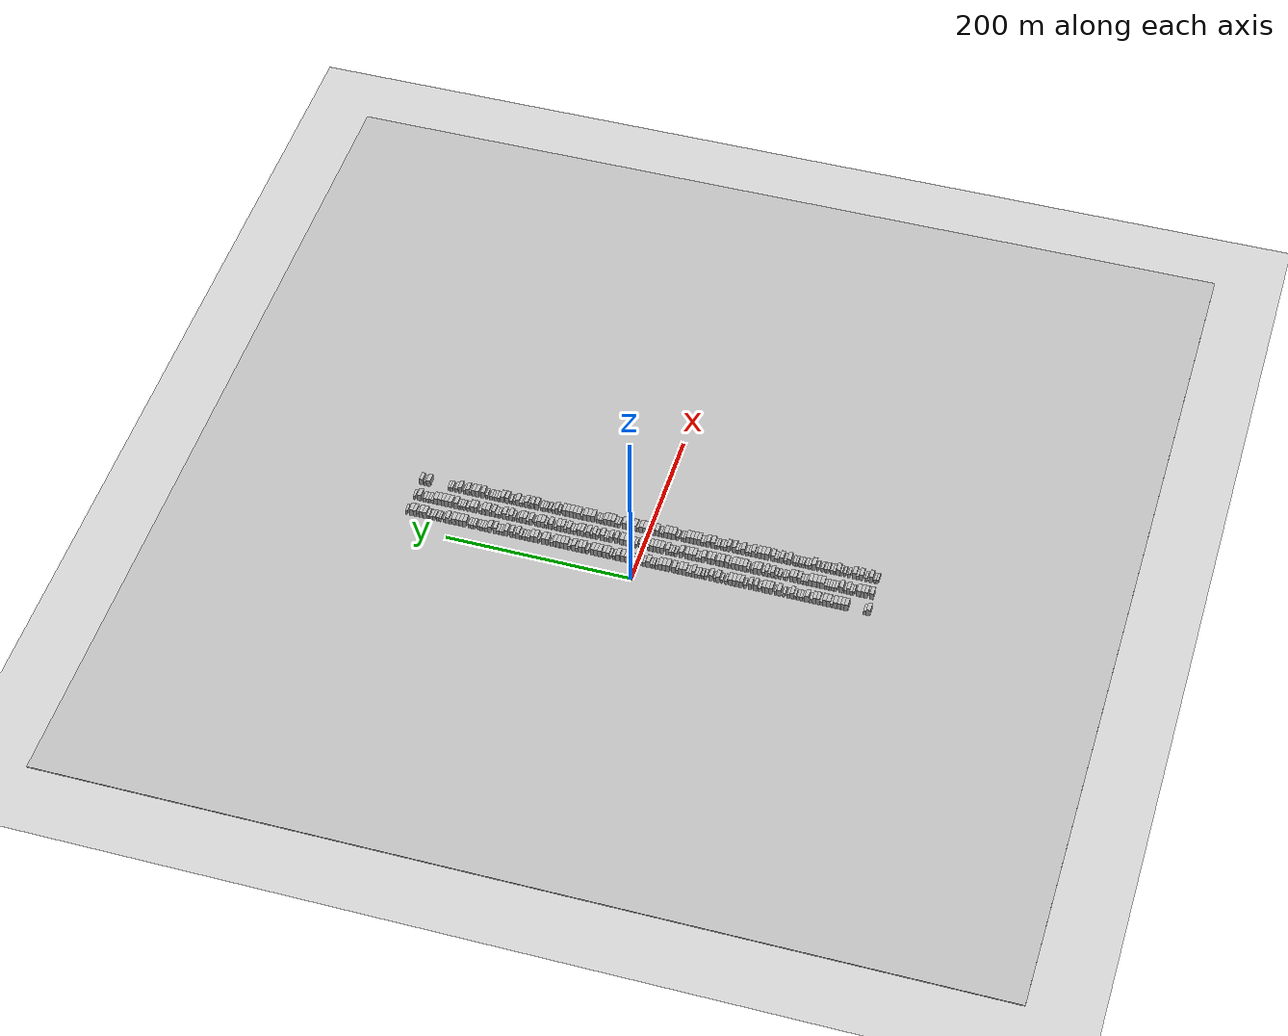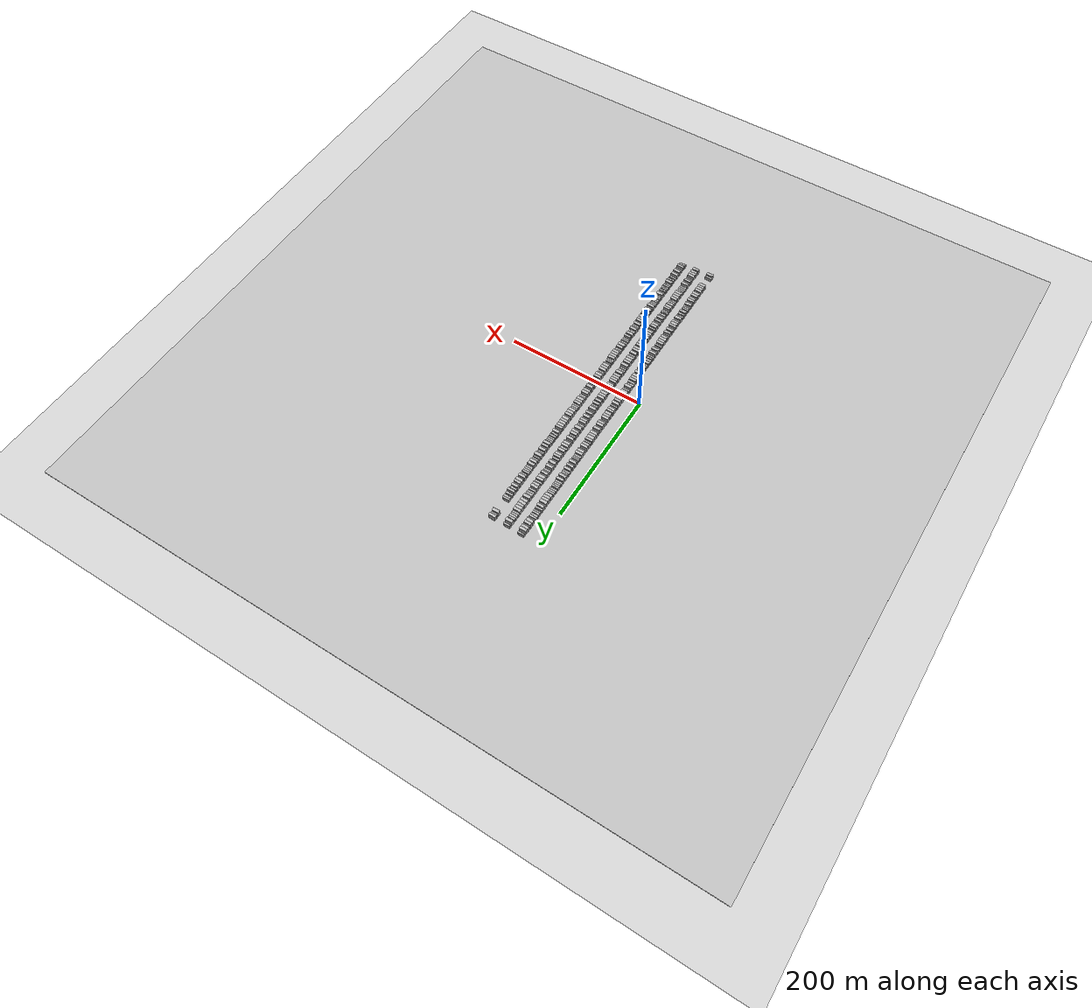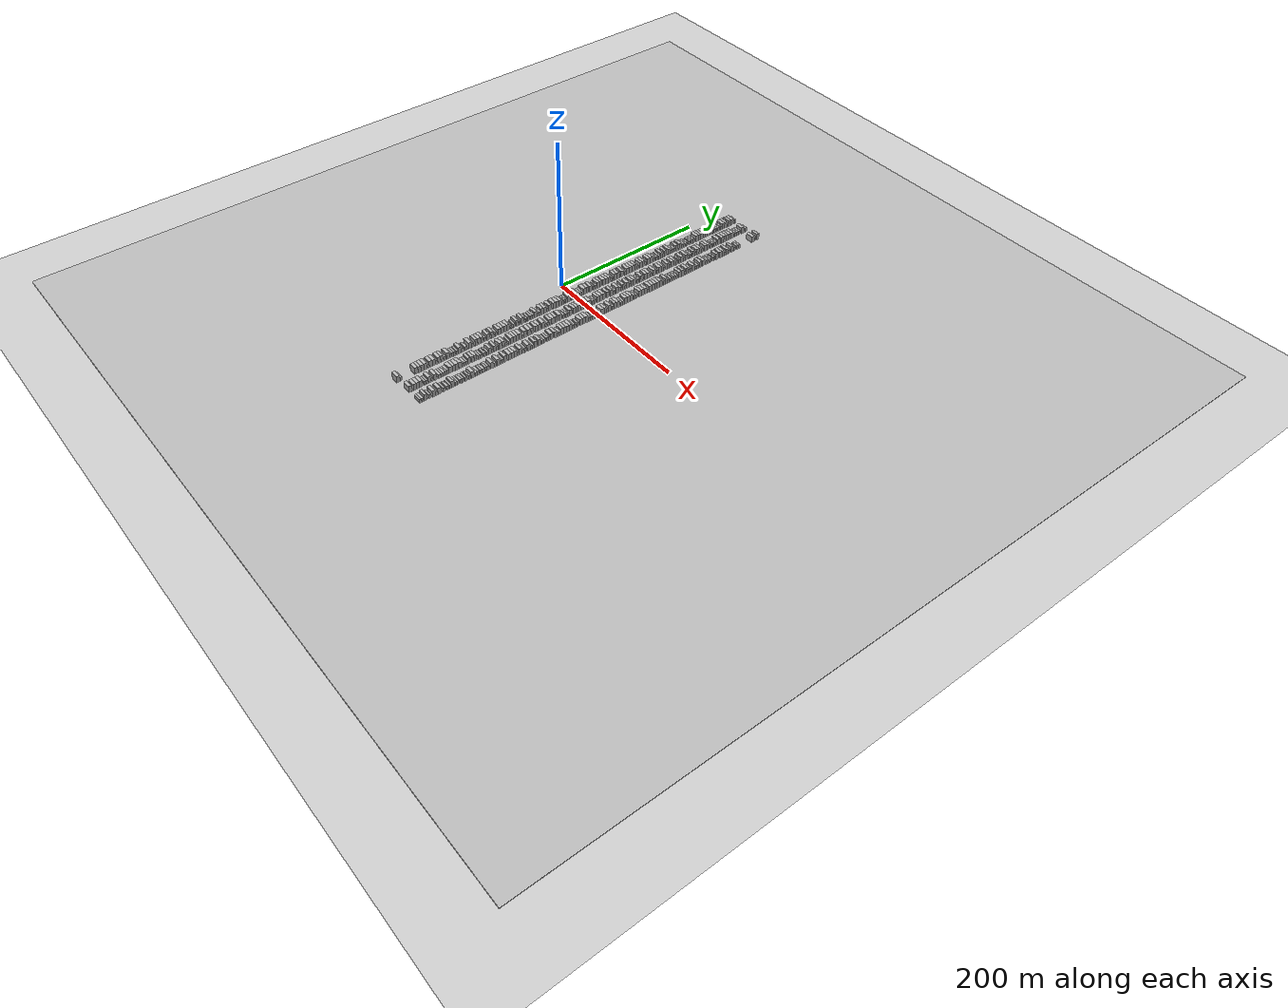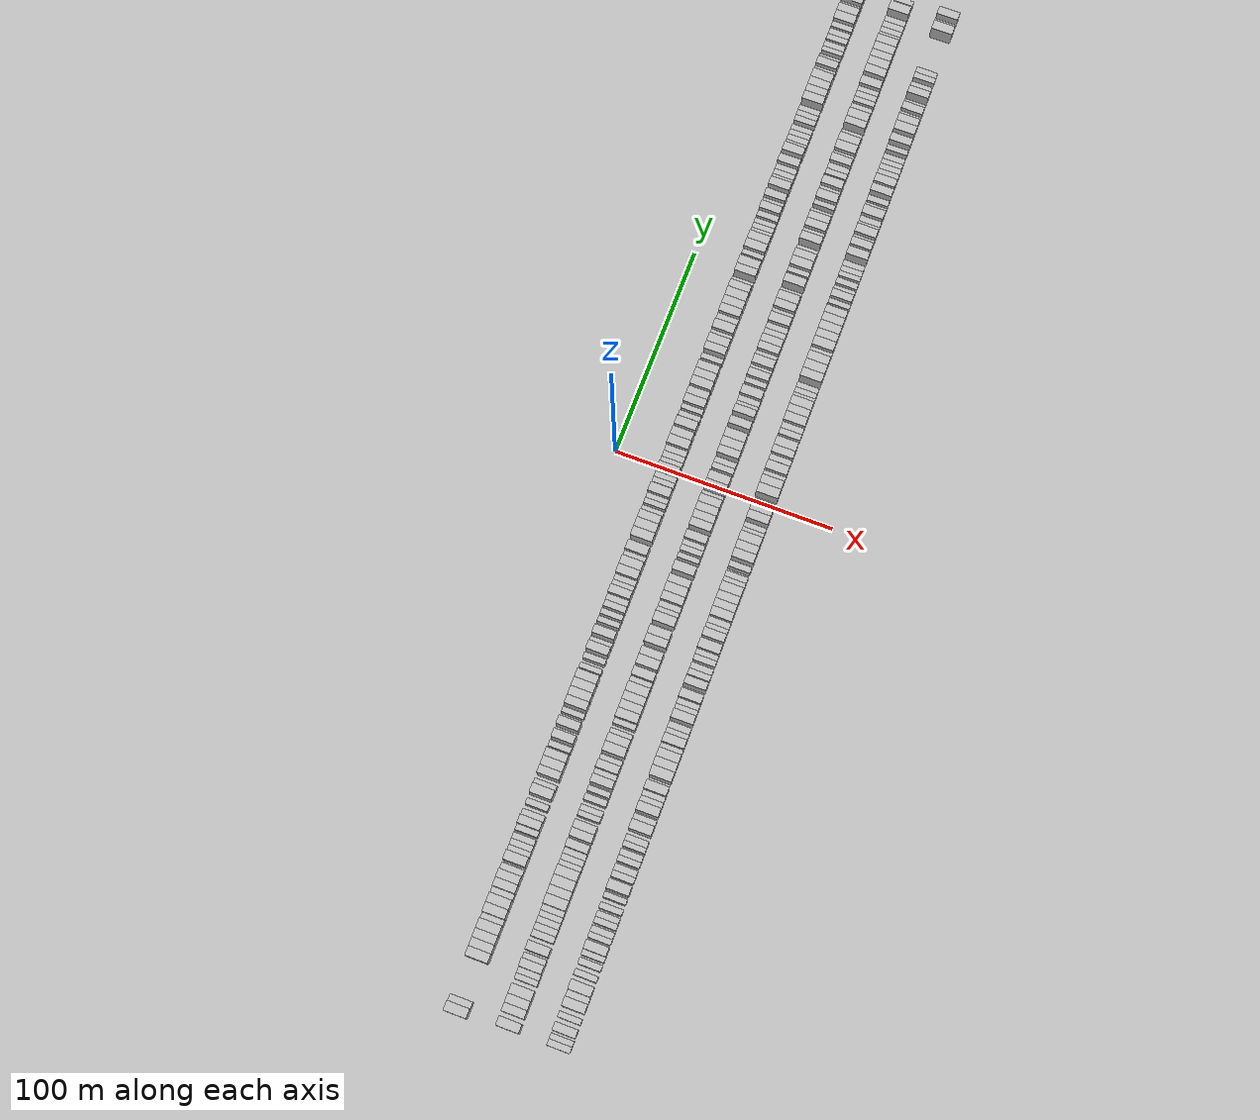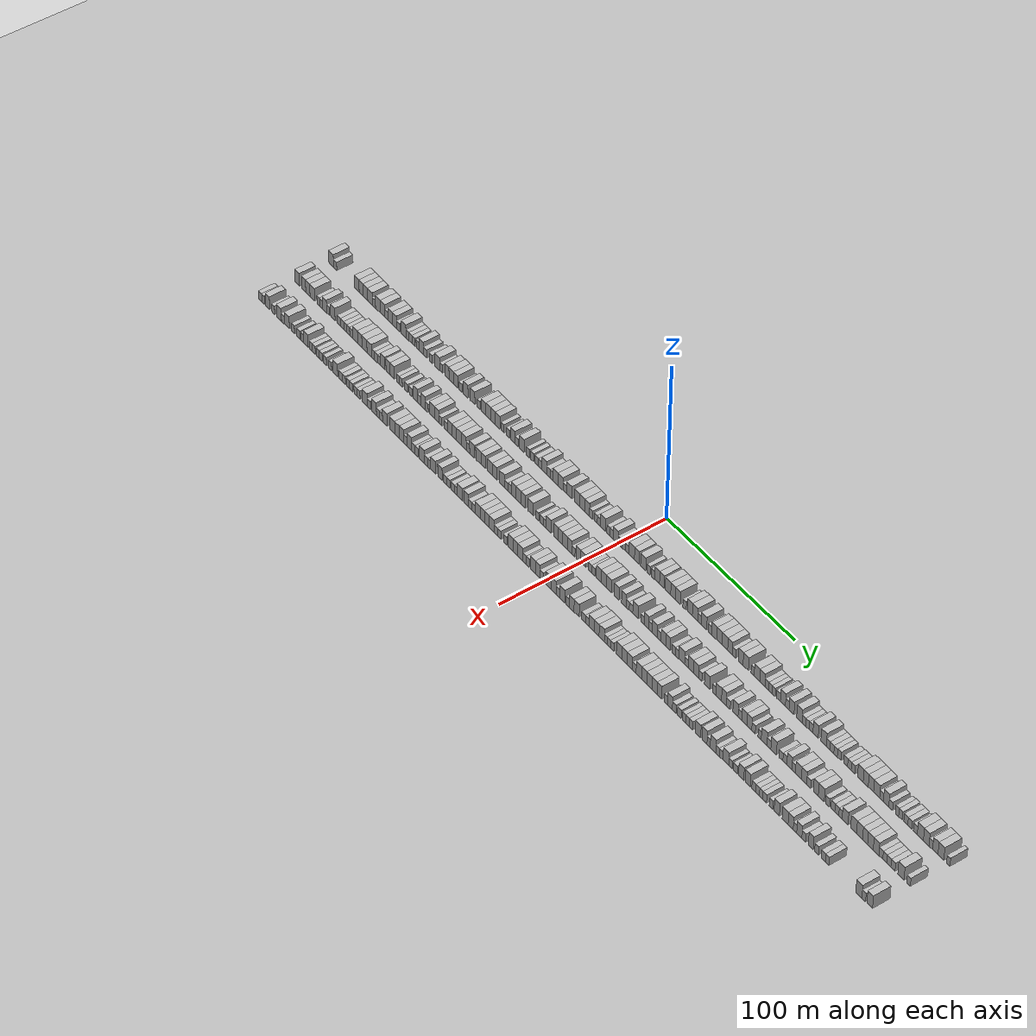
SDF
<?xml version="1.0" encoding="utf-8"?>

<sdf version="1.6">

   <world name="default">

      <gui fullscreen="0">

         <camera name="user_camera">

            <pose>-15 0 4.57585 0 0 0</pose>

            <view_controller>orbit</view_controller>

         </camera>

      </gui>

      <scene>

         <sky>

           <clouds>

             <speed>12</speed>

           </clouds>

         </sky>

         <ambient>0.4 0.4 0.4 1</ambient>

         <background>0.7 0.7 0.7 1</background>

         <shadows>1</shadows>

      </scene>

      <gravity>0 0 -9.8066</gravity>

      <magnetic_field>6e-06 2.3e-05 -4.2e-05</magnetic_field>

      <physics default="0" name="default_physics" type="ode">

         <ode>

            <solver>

               <type>quick</type>

               <iters>10</iters>

               <sor>1.0</sor>

               <use_dynamic_moi_rescaling>0</use_dynamic_moi_rescaling>

            </solver>

            <constraints>

               <cfm>0</cfm>

               <erp>0.2</erp>

               <contact_max_correcting_vel>100</contact_max_correcting_vel>

               <contact_surface_layer>0.001</contact_surface_layer>

            </constraints>

         </ode>

         <max_step_size>0.004</max_step_size>

         <real_time_factor>1</real_time_factor>

         <real_time_update_rate>250</real_time_update_rate>

      </physics>

      <light name="sun" type="directional">

         <cast_shadows>1</cast_shadows>

         <pose>0 0 10 0 0 0</pose>

         <diffuse>0.8 0.8 0.8 1</diffuse>

         <specular>0.2 0.2 0.2 1</specular>

         <attenuation>

            <range>1000</range>

            <constant>0.9</constant>

            <linear>0.01</linear>

            <quadratic>0.001</quadratic>

         </attenuation>

         <direction>-0.5 0.1 -0.9</direction>

      </light>

      <include>

         <name>ground_plane_1</name>

         <uri>model://HANNAS_ground_plane</uri>

         <pose>0 0 0  0 0 0</pose>

      </include>

      <include>

         <name>ground_plane_2</name>

         <uri>model://HANNAS_ground_plane</uri>

         <pose>100 0 0  0 0 0</pose>

      </include>

      <model name="building_1">

         <static>1</static>

         <pose frame="">25.0000 -245.8871 0 0.000000 0.000000 0.000000</pose>

         <link name="link">

            <pose frame="">0 0 4.50 0 0 0</pose>

            <collision name="collision">

               <geometry>

                  <box>

                     <size>10.0000 4.2258 9.0000</size>

                  </box>

               </geometry>

               <max_contacts>10</max_contacts>

               <surface>

                  <contact>

                     <ode/>

                  </contact>

                  <bounce/>

                  <friction>

                     <torsional>

                        <ode/>

                     </torsional>

                     <ode/>

                  </friction>

               </surface>

            </collision>

            <visual name="visual">

               <cast_shadows>0</cast_shadows>

               <geometry>

                  <box>

                     <size>10.0000 4.2258 9.0000</size>

                  </box>

               </geometry>

               <material>

                  <script>

                     <uri>model://HANNAS_wall/materials/scripts</uri>

                     <uri>model://HANNAS_wall/materials/textures</uri>

                     <name>vrc/HANNAS_wall</name>

                  </script>

               </material>

            </visual>

            <self_collide>0</self_collide>

            <enable_wind>0</enable_wind>

            <kinematic>0</kinematic>

         </link>

      </model>

      <model name="building_2">

         <static>1</static>

         <pose frame="">25.0000 -242.2962 0 0.000000 0.000000 0.000000</pose>

         <link name="link">

            <pose frame="">0 0 3.00 0 0 0</pose>

            <collision name="collision">

               <geometry>

                  <box>

                     <size>10.0000 2.9560 6.0000</size>

                  </box>

               </geometry>

               <max_contacts>10</max_contacts>

               <surface>

                  <contact>

                     <ode/>

                  </contact>

                  <bounce/>

                  <friction>

                     <torsional>

                        <ode/>

                     </torsional>

                     <ode/>

                  </friction>

               </surface>

            </collision>

            <visual name="visual">

               <cast_shadows>0</cast_shadows>

               <geometry>

                  <box>

                     <size>10.0000 2.9560 6.0000</size>

                  </box>

               </geometry>

               <material>

                  <script>

                     <uri>model://HANNAS_wall/materials/scripts</uri>

                     <uri>model://HANNAS_wall/materials/textures</uri>

                     <name>vrc/HANNAS_wall</name>

                  </script>

               </material>

            </visual>

            <self_collide>0</self_collide>

            <enable_wind>0</enable_wind>

            <kinematic>0</kinematic>

         </link>

      </model>

      <model name="building_3">

         <static>1</static>

         <pose frame="">25.0000 -222.6464 0 0.000000 0.000000 0.000000</pose>

         <link name="link">

            <pose frame="">0 0 4.50 0 0 0</pose>

            <collision name="collision">

               <geometry>

                  <box>

                     <size>10.0000 4.1145 9.0000</size>

                  </box>

               </geometry>

               <max_contacts>10</max_contacts>

               <surface>

                  <contact>

                     <ode/>

                  </contact>

                  <bounce/>

                  <friction>

                     <torsional>

                        <ode/>

                     </torsional>

                     <ode/>

                  </friction>

               </surface>

            </collision>

            <visual name="visual">

               <cast_shadows>0</cast_shadows>

               <geometry>

                  <box>

                     <size>10.0000 4.1145 9.0000</size>

                  </box>

               </geometry>

               <material>

                  <script>

                     <uri>model://HANNAS_wall/materials/scripts</uri>

                     <uri>model://HANNAS_wall/materials/textures</uri>

                     <name>vrc/HANNAS_wall</name>

                  </script>

               </material>

            </visual>

            <self_collide>0</self_collide>

            <enable_wind>0</enable_wind>

            <kinematic>0</kinematic>

         </link>

      </model>

      <model name="building_4">

         <static>1</static>

         <pose frame="">25.0000 -218.7045 0 0.000000 0.000000 0.000000</pose>

         <link name="link">

            <pose frame="">0 0 4.50 0 0 0</pose>

            <collision name="collision">

               <geometry>

                  <box>

                     <size>10.0000 3.7693 9.0000</size>

                  </box>

               </geometry>

               <max_contacts>10</max_contacts>

               <surface>

                  <contact>

                     <ode/>

                  </contact>

                  <bounce/>

                  <friction>

                     <torsional>

                        <ode/>

                     </torsional>

                     <ode/>

                  </friction>

               </surface>

            </collision>

            <visual name="visual">

               <cast_shadows>0</cast_shadows>

               <geometry>

                  <box>

                     <size>10.0000 3.7693 9.0000</size>

                  </box>

               </geometry>

               <material>

                  <script>

                     <uri>model://HANNAS_wall/materials/scripts</uri>

                     <uri>model://HANNAS_wall/materials/textures</uri>

                     <name>vrc/HANNAS_wall</name>

                  </script>

               </material>

            </visual>

            <self_collide>0</self_collide>

            <enable_wind>0</enable_wind>

            <kinematic>0</kinematic>

         </link>

      </model>

      <model name="building_5">

         <static>1</static>

         <pose frame="">25.0000 -214.8568 0 0.000000 0.000000 0.000000</pose>

         <link name="link">

            <pose frame="">0 0 4.50 0 0 0</pose>

            <collision name="collision">

               <geometry>

                  <box>

                     <size>10.0000 3.9260 9.0000</size>

                  </box>

               </geometry>

               <max_contacts>10</max_contacts>

               <surface>

                  <contact>

                     <ode/>

                  </contact>

                  <bounce/>

                  <friction>

                     <torsional>

                        <ode/>

                     </torsional>

                     <ode/>

                  </friction>

               </surface>

            </collision>

            <visual name="visual">

               <cast_shadows>0</cast_shadows>

               <geometry>

                  <box>

                     <size>10.0000 3.9260 9.0000</size>

                  </box>

               </geometry>

               <material>

                  <script>

                     <uri>model://HANNAS_wall/materials/scripts</uri>

                     <uri>model://HANNAS_wall/materials/textures</uri>

                     <name>vrc/HANNAS_wall</name>

                  </script>

               </material>

            </visual>

            <self_collide>0</self_collide>

            <enable_wind>0</enable_wind>

            <kinematic>0</kinematic>

         </link>

      </model>

      <model name="building_6">

         <static>1</static>

         <pose frame="">25.0000 -210.7227 0 0.000000 0.000000 0.000000</pose>

         <link name="link">

            <pose frame="">0 0 4.50 0 0 0</pose>

            <collision name="collision">

               <geometry>

                  <box>

                     <size>10.0000 4.3422 9.0000</size>

                  </box>

               </geometry>

               <max_contacts>10</max_contacts>

               <surface>

                  <contact>

                     <ode/>

                  </contact>

                  <bounce/>

                  <friction>

                     <torsional>

                        <ode/>

                     </torsional>

                     <ode/>

                  </friction>

               </surface>

            </collision>

            <visual name="visual">

               <cast_shadows>0</cast_shadows>

               <geometry>

                  <box>

                     <size>10.0000 4.3422 9.0000</size>

                  </box>

               </geometry>

               <material>

                  <script>

                     <uri>model://HANNAS_wall/materials/scripts</uri>

                     <uri>model://HANNAS_wall/materials/textures</uri>

                     <name>vrc/HANNAS_wall</name>

                  </script>

               </material>

            </visual>

            <self_collide>0</self_collide>

            <enable_wind>0</enable_wind>

            <kinematic>0</kinematic>

         </link>

      </model>

      <model name="building_7">

         <static>1</static>

         <pose frame="">25.0000 -207.2259 0 0.000000 0.000000 0.000000</pose>

         <link name="link">

            <pose frame="">0 0 3.00 0 0 0</pose>

            <collision name="collision">

               <geometry>

                  <box>

                     <size>10.0000 2.6515 6.0000</size>

                  </box>

               </geometry>

               <max_contacts>10</max_contacts>

               <surface>

                  <contact>

                     <ode/>

                  </contact>

                  <bounce/>

                  <friction>

                     <torsional>

                        <ode/>

                     </torsional>

                     <ode/>

                  </friction>

               </surface>

            </collision>

            <visual name="visual">

               <cast_shadows>0</cast_shadows>

               <geometry>

                  <box>

                     <size>10.0000 2.6515 6.0000</size>

                  </box>

               </geometry>

               <material>

                  <script>

                     <uri>model://HANNAS_wall/materials/scripts</uri>

                     <uri>model://HANNAS_wall/materials/textures</uri>

                     <name>vrc/HANNAS_wall</name>

                  </script>

               </material>

            </visual>

            <self_collide>0</self_collide>

            <enable_wind>0</enable_wind>

            <kinematic>0</kinematic>

         </link>

      </model>

      <model name="building_8">

         <static>1</static>

         <pose frame="">25.0000 -203.7838 0 0.000000 0.000000 0.000000</pose>

         <link name="link">

            <pose frame="">0 0 4.50 0 0 0</pose>

            <collision name="collision">

               <geometry>

                  <box>

                     <size>10.0000 4.2327 9.0000</size>

                  </box>

               </geometry>

               <max_contacts>10</max_contacts>

               <surface>

                  <contact>

                     <ode/>

                  </contact>

                  <bounce/>

                  <friction>

                     <torsional>

                        <ode/>

                     </torsional>

                     <ode/>

                  </friction>

               </surface>

            </collision>

            <visual name="visual">

               <cast_shadows>0</cast_shadows>

               <geometry>

                  <box>

                     <size>10.0000 4.2327 9.0000</size>

                  </box>

               </geometry>

               <material>

                  <script>

                     <uri>model://HANNAS_wall/materials/scripts</uri>

                     <uri>model://HANNAS_wall/materials/textures</uri>

                     <name>vrc/HANNAS_wall</name>

                  </script>

               </material>

            </visual>

            <self_collide>0</self_collide>

            <enable_wind>0</enable_wind>

            <kinematic>0</kinematic>

         </link>

      </model>

      <model name="building_9">

         <static>1</static>

         <pose frame="">25.0000 -199.5895 0 0.000000 0.000000 0.000000</pose>

         <link name="link">

            <pose frame="">0 0 4.50 0 0 0</pose>

            <collision name="collision">

               <geometry>

                  <box>

                     <size>10.0000 4.1559 9.0000</size>

                  </box>

               </geometry>

               <max_contacts>10</max_contacts>

               <surface>

                  <contact>

                     <ode/>

                  </contact>

                  <bounce/>

                  <friction>

                     <torsional>

                        <ode/>

                     </torsional>

                     <ode/>

                  </friction>

               </surface>

            </collision>

            <visual name="visual">

               <cast_shadows>0</cast_shadows>

               <geometry>

                  <box>

                     <size>10.0000 4.1559 9.0000</size>

                  </box>

               </geometry>

               <material>

                  <script>

                     <uri>model://HANNAS_wall/materials/scripts</uri>

                     <uri>model://HANNAS_wall/materials/textures</uri>

                     <name>vrc/HANNAS_wall</name>

                  </script>

               </material>

            </visual>

            <self_collide>0</self_collide>

            <enable_wind>0</enable_wind>

            <kinematic>0</kinematic>

         </link>

      </model>

      <model name="building_10">

         <static>1</static>

         <pose frame="">25.0000 -196.1094 0 0.000000 0.000000 0.000000</pose>

         <link name="link">

            <pose frame="">0 0 3.00 0 0 0</pose>

            <collision name="collision">

               <geometry>

                  <box>

                     <size>10.0000 2.8042 6.0000</size>

                  </box>

               </geometry>

               <max_contacts>10</max_contacts>

               <surface>

                  <contact>

                     <ode/>

                  </contact>

                  <bounce/>

                  <friction>

                     <torsional>

                        <ode/>

                     </torsional>

                     <ode/>

                  </friction>

               </surface>

            </collision>

            <visual name="visual">

               <cast_shadows>0</cast_shadows>

               <geometry>

                  <box>

                     <size>10.0000 2.8042 6.0000</size>

                  </box>

               </geometry>

               <material>

                  <script>

                     <uri>model://HANNAS_wall/materials/scripts</uri>

                     <uri>model://HANNAS_wall/materials/textures</uri>

                     <name>vrc/HANNAS_wall</name>

                  </script>

               </material>

            </visual>

            <self_collide>0</self_collide>

            <enable_wind>0</enable_wind>

            <kinematic>0</kinematic>

         </link>

      </model>

      <model name="building_11">

         <static>1</static>

         <pose frame="">25.0000 -192.8025 0 0.000000 0.000000 0.000000</pose>

         <link name="link">

            <pose frame="">0 0 4.50 0 0 0</pose>

            <collision name="collision">

               <geometry>

                  <box>

                     <size>10.0000 3.8097 9.0000</size>

                  </box>

               </geometry>

               <max_contacts>10</max_contacts>

               <surface>

                  <contact>

                     <ode/>

                  </contact>

                  <bounce/>

                  <friction>

                     <torsional>

                        <ode/>

                     </torsional>

                     <ode/>

                  </friction>

               </surface>

            </collision>

            <visual name="visual">

               <cast_shadows>0</cast_shadows>

               <geometry>

                  <box>

                     <size>10.0000 3.8097 9.0000</size>

                  </box>

               </geometry>

               <material>

                  <script>

                     <uri>model://HANNAS_wall/materials/scripts</uri>

                     <uri>model://HANNAS_wall/materials/textures</uri>

                     <name>vrc/HANNAS_wall</name>

                  </script>

               </material>

            </visual>

            <self_collide>0</self_collide>

            <enable_wind>0</enable_wind>

            <kinematic>0</kinematic>

         </link>

      </model>

      <model name="building_12">

         <static>1</static>

         <pose frame="">25.0000 -189.0350 0 0.000000 0.000000 0.000000</pose>

         <link name="link">

            <pose frame="">0 0 4.50 0 0 0</pose>

            <collision name="collision">

               <geometry>

                  <box>

                     <size>10.0000 3.7252 9.0000</size>

                  </box>

               </geometry>

               <max_contacts>10</max_contacts>

               <surface>

                  <contact>

                     <ode/>

                  </contact>

                  <bounce/>

                  <friction>

                     <torsional>

                        <ode/>

                     </torsional>

                     <ode/>

                  </friction>

               </surface>

            </collision>

            <visual name="visual">

               <cast_shadows>0</cast_shadows>

               <geometry>

                  <box>

                     <size>10.0000 3.7252 9.0000</size>

                  </box>

               </geometry>

               <material>

                  <script>

                     <uri>model://HANNAS_wall/materials/scripts</uri>

                     <uri>model://HANNAS_wall/materials/textures</uri>

                     <name>vrc/HANNAS_wall</name>

                  </script>

               </material>

            </visual>

            <self_collide>0</self_collide>

            <enable_wind>0</enable_wind>

            <kinematic>0</kinematic>

         </link>

      </model>

      <model name="building_13">

         <static>1</static>

         <pose frame="">25.0000 -185.6824 0 0.000000 0.000000 0.000000</pose>

         <link name="link">

            <pose frame="">0 0 3.00 0 0 0</pose>

            <collision name="collision">

               <geometry>

                  <box>

                     <size>10.0000 2.9801 6.0000</size>

                  </box>

               </geometry>

               <max_contacts>10</max_contacts>

               <surface>

                  <contact>

                     <ode/>

                  </contact>

                  <bounce/>

                  <friction>

                     <torsional>

                        <ode/>

                     </torsional>

                     <ode/>

                  </friction>

               </surface>

            </collision>

            <visual name="visual">

               <cast_shadows>0</cast_shadows>

               <geometry>

                  <box>

                     <size>10.0000 2.9801 6.0000</size>

                  </box>

               </geometry>

               <material>

                  <script>

                     <uri>model://HANNAS_wall/materials/scripts</uri>

                     <uri>model://HANNAS_wall/materials/textures</uri>

                     <name>vrc/HANNAS_wall</name>

                  </script>

               </material>

            </visual>

            <self_collide>0</self_collide>

            <enable_wind>0</enable_wind>

            <kinematic>0</kinematic>

         </link>

      </model>

      <model name="building_14">

         <static>1</static>

         <pose frame="">25.0000 -181.0683 0 0.000000 0.000000 0.000000</pose>

         <link name="link">

            <pose frame="">0 0 4.50 0 0 0</pose>

            <collision name="collision">

               <geometry>

                  <box>

                     <size>10.0000 4.2480 9.0000</size>

                  </box>

               </geometry>

               <max_contacts>10</max_contacts>

               <surface>

                  <contact>

                     <ode/>

                  </contact>

                  <bounce/>

                  <friction>

                     <torsional>

                        <ode/>

                     </torsional>

                     <ode/>

                  </friction>

               </surface>

            </collision>

            <visual name="visual">

               <cast_shadows>0</cast_shadows>

               <geometry>

                  <box>

                     <size>10.0000 4.2480 9.0000</size>

                  </box>

               </geometry>

               <material>

                  <script>

                     <uri>model://HANNAS_wall/materials/scripts</uri>

                     <uri>model://HANNAS_wall/materials/textures</uri>

                     <name>vrc/HANNAS_wall</name>

                  </script>

               </material>

            </visual>

            <self_collide>0</self_collide>

            <enable_wind>0</enable_wind>

            <kinematic>0</kinematic>

         </link>

      </model>

      <model name="building_15">

         <static>1</static>

         <pose frame="">25.0000 -177.6660 0 0.000000 0.000000 0.000000</pose>

         <link name="link">

            <pose frame="">0 0 3.00 0 0 0</pose>

            <collision name="collision">

               <geometry>

                  <box>

                     <size>10.0000 2.5567 6.0000</size>

                  </box>

               </geometry>

               <max_contacts>10</max_contacts>

               <surface>

                  <contact>

                     <ode/>

                  </contact>

                  <bounce/>

                  <friction>

                     <torsional>

                        <ode/>

                     </torsional>

                     <ode/>

                  </friction>

               </surface>

            </collision>

            <visual name="visual">

               <cast_shadows>0</cast_shadows>

               <geometry>

                  <box>

                     <size>10.0000 2.5567 6.0000</size>

                  </box>

               </geometry>

               <material>

                  <script>

                     <uri>model://HANNAS_wall/materials/scripts</uri>

                     <uri>model://HANNAS_wall/materials/textures</uri>

                     <name>vrc/HANNAS_wall</name>

                  </script>

               </material>

            </visual>

            <self_collide>0</self_collide>

            <enable_wind>0</enable_wind>

            <kinematic>0</kinematic>

         </link>

      </model>

      <model name="building_16">

         <static>1</static>

         <pose frame="">25.0000 -175.0157 0 0.000000 0.000000 0.000000</pose>

         <link name="link">

            <pose frame="">0 0 3.00 0 0 0</pose>

            <collision name="collision">

               <geometry>

                  <box>

                     <size>10.0000 2.7439 6.0000</size>

                  </box>

               </geometry>

               <max_contacts>10</max_contacts>

               <surface>

                  <contact>

                     <ode/>

                  </contact>

                  <bounce/>

                  <friction>

                     <torsional>

                        <ode/>

                     </torsional>

                     <ode/>

                  </friction>

               </surface>

            </collision>

            <visual name="visual">

               <cast_shadows>0</cast_shadows>

               <geometry>

                  <box>

                     <size>10.0000 2.7439 6.0000</size>

                  </box>

               </geometry>

               <material>

                  <script>

                     <uri>model://HANNAS_wall/materials/scripts</uri>

                     <uri>model://HANNAS_wall/materials/textures</uri>

                     <name>vrc/HANNAS_wall</name>

                  </script>

               </material>

            </visual>

            <self_collide>0</self_collide>

            <enable_wind>0</enable_wind>

            <kinematic>0</kinematic>

         </link>

      </model>

      <model name="building_17">

         <static>1</static>

         <pose frame="">25.0000 -172.2766 0 0.000000 0.000000 0.000000</pose>

         <link name="link">

            <pose frame="">0 0 3.00 0 0 0</pose>

            <collision name="collision">

               <geometry>

                  <box>

                     <size>10.0000 2.7342 6.0000</size>

                  </box>

               </geometry>

               <max_contacts>10</max_contacts>

               <surface>

                  <contact>

                     <ode/>

                  </contact>

                  <bounce/>

                  <friction>

                     <torsional>

                        <ode/>

                     </torsional>

                     <ode/>

                  </friction>

               </surface>

            </collision>

            <visual name="visual">

               <cast_shadows>0</cast_shadows>

               <geometry>

                  <box>

                     <size>10.0000 2.7342 6.0000</size>

                  </box>

               </geometry>

               <material>

                  <script>

                     <uri>model://HANNAS_wall/materials/scripts</uri>

                     <uri>model://HANNAS_wall/materials/textures</uri>

                     <name>vrc/HANNAS_wall</name>

                  </script>

               </material>

            </visual>

            <self_collide>0</self_collide>

            <enable_wind>0</enable_wind>

            <kinematic>0</kinematic>

         </link>

      </model>

      <model name="building_18">

         <static>1</static>

         <pose frame="">25.0000 -168.5623 0 0.000000 0.000000 0.000000</pose>

         <link name="link">

            <pose frame="">0 0 3.00 0 0 0</pose>

            <collision name="collision">

               <geometry>

                  <box>

                     <size>10.0000 2.6944 6.0000</size>

                  </box>

               </geometry>

               <max_contacts>10</max_contacts>

               <surface>

                  <contact>

                     <ode/>

                  </contact>

                  <bounce/>

                  <friction>

                     <torsional>

                        <ode/>

                     </torsional>

                     <ode/>

                  </friction>

               </surface>

            </collision>

            <visual name="visual">

               <cast_shadows>0</cast_shadows>

               <geometry>

                  <box>

                     <size>10.0000 2.6944 6.0000</size>

                  </box>

               </geometry>

               <material>

                  <script>

                     <uri>model://HANNAS_wall/materials/scripts</uri>

                     <uri>model://HANNAS_wall/materials/textures</uri>

                     <name>vrc/HANNAS_wall</name>

                  </script>

               </material>

            </visual>

            <self_collide>0</self_collide>

            <enable_wind>0</enable_wind>

            <kinematic>0</kinematic>

         </link>

      </model>

      <model name="building_19">

         <static>1</static>

         <pose frame="">25.0000 -165.3175 0 0.000000 0.000000 0.000000</pose>

         <link name="link">

            <pose frame="">0 0 4.50 0 0 0</pose>

            <collision name="collision">

               <geometry>

                  <box>

                     <size>10.0000 3.7954 9.0000</size>

                  </box>

               </geometry>

               <max_contacts>10</max_contacts>

               <surface>

                  <contact>

                     <ode/>

                  </contact>

                  <bounce/>

                  <friction>

                     <torsional>

                        <ode/>

                     </torsional>

                     <ode/>

                  </friction>

               </surface>

            </collision>

            <visual name="visual">

               <cast_shadows>0</cast_shadows>

               <geometry>

                  <box>

                     <size>10.0000 3.7954 9.0000</size>

                  </box>

               </geometry>

               <material>

                  <script>

                     <uri>model://HANNAS_wall/materials/scripts</uri>

                     <uri>model://HANNAS_wall/materials/textures</uri>

                     <name>vrc/HANNAS_wall</name>

                  </script>

               </material>

            </visual>

            <self_collide>0</self_collide>

            <enable_wind>0</enable_wind>

            <kinematic>0</kinematic>

         </link>

      </model>

      <model name="building_20">

         <static>1</static>

         <pose frame="">25.0000 -161.9389 0 0.000000 0.000000 0.000000</pose>

         <link name="link">

            <pose frame="">0 0 3.00 0 0 0</pose>

            <collision name="collision">

               <geometry>

                  <box>

                     <size>10.0000 2.9617 6.0000</size>

                  </box>

               </geometry>

               <max_contacts>10</max_contacts>

               <surface>

                  <contact>

                     <ode/>

                  </contact>

                  <bounce/>

                  <friction>

                     <torsional>

                        <ode/>

                     </torsional>

                     <ode/>

                  </friction>

               </surface>

            </collision>

            <visual name="visual">

               <cast_shadows>0</cast_shadows>

               <geometry>

                  <box>

                     <size>10.0000 2.9617 6.0000</size>

                  </box>

               </geometry>

               <material>

                  <script>

                     <uri>model://HANNAS_wall/materials/scripts</uri>

                     <uri>model://HANNAS_wall/materials/textures</uri>

                     <name>vrc/HANNAS_wall</name>

                  </script>

               </material>

            </visual>

            <self_collide>0</self_collide>

            <enable_wind>0</enable_wind>

            <kinematic>0</kinematic>

         </link>

      </model>

      <model name="building_21">

         <static>1</static>

         <pose frame="">25.0000 -157.0666 0 0.000000 0.000000 0.000000</pose>

         <link name="link">

            <pose frame="">0 0 3.00 0 0 0</pose>

            <collision name="collision">

               <geometry>

                  <box>

                     <size>10.0000 2.7829 6.0000</size>

                  </box>

               </geometry>

               <max_contacts>10</max_contacts>

               <surface>

                  <contact>

                     <ode/>

                  </contact>

                  <bounce/>

                  <friction>

                     <torsional>

                        <ode/>

                     </torsional>

                     <ode/>

                  </friction>

               </surface>

            </collision>

            <visual name="visual">

               <cast_shadows>0</cast_shadows>

               <geometry>

                  <box>

                     <size>10.0000 2.7829 6.0000</size>

                  </box>

               </geometry>

               <material>

                  <script>

                     <uri>model://HANNAS_wall/materials/scripts</uri>

                     <uri>model://HANNAS_wall/materials/textures</uri>

                     <name>vrc/HANNAS_wall</name>

                  </script>

               </material>

            </visual>

            <self_collide>0</self_collide>

            <enable_wind>0</enable_wind>

            <kinematic>0</kinematic>

         </link>

      </model>

      <model name="building_22">

         <static>1</static>

         <pose frame="">25.0000 -151.5205 0 0.000000 0.000000 0.000000</pose>

         <link name="link">

            <pose frame="">0 0 4.50 0 0 0</pose>

            <collision name="collision">

               <geometry>

                  <box>

                     <size>10.0000 4.3093 9.0000</size>

                  </box>

               </geometry>

               <max_contacts>10</max_contacts>

               <surface>

                  <contact>

                     <ode/>

                  </contact>

                  <bounce/>

                  <friction>

                     <torsional>

                        <ode/>

                     </torsional>

                     <ode/>

                  </friction>

               </surface>

            </collision>

            <visual name="visual">

               <cast_shadows>0</cast_shadows>

               <geometry>

                  <box>

                     <size>10.0000 4.3093 9.0000</size>

                  </box>

               </geometry>

               <material>

                  <script>

                     <uri>model://HANNAS_wall/materials/scripts</uri>

                     <uri>model://HANNAS_wall/materials/textures</uri>

                     <name>vrc/HANNAS_wall</name>

                  </script>

               </material>

            </visual>

            <self_collide>0</self_collide>

            <enable_wind>0</enable_wind>

            <kinematic>0</kinematic>

         </link>

      </model>

      <model name="building_23">

         <static>1</static>

         <pose frame="">25.0000 -148.1344 0 0.000000 0.000000 0.000000</pose>

         <link name="link">

            <pose frame="">0 0 3.00 0 0 0</pose>

            <collision name="collision">

               <geometry>

                  <box>

                     <size>10.0000 2.4628 6.0000</size>

                  </box>

               </geometry>

               <max_contacts>10</max_contacts>

               <surface>

                  <contact>

                     <ode/>

                  </contact>

                  <bounce/>

                  <friction>

                     <torsional>

                        <ode/>

                     </torsional>

                     <ode/>

                  </friction>

               </surface>

            </collision>

            <visual name="visual">

               <cast_shadows>0</cast_shadows>

               <geometry>

                  <box>

                     <size>10.0000 2.4628 6.0000</size>

                  </box>

               </geometry>

               <material>

                  <script>

                     <uri>model://HANNAS_wall/materials/scripts</uri>

                     <uri>model://HANNAS_wall/materials/textures</uri>

                     <name>vrc/HANNAS_wall</name>

                  </script>

               </material>

            </visual>

            <self_collide>0</self_collide>

            <enable_wind>0</enable_wind>

            <kinematic>0</kinematic>

         </link>

      </model>

      <model name="building_24">

         <static>1</static>

         <pose frame="">25.0000 -143.0938 0 0.000000 0.000000 0.000000</pose>

         <link name="link">

            <pose frame="">0 0 4.50 0 0 0</pose>

            <collision name="collision">

               <geometry>

                  <box>

                     <size>10.0000 3.6184 9.0000</size>

                  </box>

               </geometry>

               <max_contacts>10</max_contacts>

               <surface>

                  <contact>

                     <ode/>

                  </contact>

                  <bounce/>

                  <friction>

                     <torsional>

                        <ode/>

                     </torsional>

                     <ode/>

                  </friction>

               </surface>

            </collision>

            <visual name="visual">

               <cast_shadows>0</cast_shadows>

               <geometry>

                  <box>

                     <size>10.0000 3.6184 9.0000</size>

                  </box>

               </geometry>

               <material>

                  <script>

                     <uri>model://HANNAS_wall/materials/scripts</uri>

                     <uri>model://HANNAS_wall/materials/textures</uri>

                     <name>vrc/HANNAS_wall</name>

                  </script>

               </material>

            </visual>

            <self_collide>0</self_collide>

            <enable_wind>0</enable_wind>

            <kinematic>0</kinematic>

         </link>

      </model>

      <model name="building_25">

         <static>1</static>

         <pose frame="">25.0000 -139.2067 0 0.000000 0.000000 0.000000</pose>

         <link name="link">

            <pose frame="">0 0 4.50 0 0 0</pose>

            <collision name="collision">

               <geometry>

                  <box>

                     <size>10.0000 4.1557 9.0000</size>

                  </box>

               </geometry>

               <max_contacts>10</max_contacts>

               <surface>

                  <contact>

                     <ode/>

                  </contact>

                  <bounce/>

                  <friction>

                     <torsional>

                        <ode/>

                     </torsional>

                     <ode/>

                  </friction>

               </surface>

            </collision>

            <visual name="visual">

               <cast_shadows>0</cast_shadows>

               <geometry>

                  <box>

                     <size>10.0000 4.1557 9.0000</size>

                  </box>

               </geometry>

               <material>

                  <script>

                     <uri>model://HANNAS_wall/materials/scripts</uri>

                     <uri>model://HANNAS_wall/materials/textures</uri>

                     <name>vrc/HANNAS_wall</name>

                  </script>

               </material>

            </visual>

            <self_collide>0</self_collide>

            <enable_wind>0</enable_wind>

            <kinematic>0</kinematic>

         </link>

      </model>

      <model name="building_26">

         <static>1</static>

         <pose frame="">25.0000 -135.2966 0 0.000000 0.000000 0.000000</pose>

         <link name="link">

            <pose frame="">0 0 4.50 0 0 0</pose>

            <collision name="collision">

               <geometry>

                  <box>

                     <size>10.0000 3.6646 9.0000</size>

                  </box>

               </geometry>

               <max_contacts>10</max_contacts>

               <surface>

                  <contact>

                     <ode/>

                  </contact>

                  <bounce/>

                  <friction>

                     <torsional>

                        <ode/>

                     </torsional>

                     <ode/>

                  </friction>

               </surface>

            </collision>

            <visual name="visual">

               <cast_shadows>0</cast_shadows>

               <geometry>

                  <box>

                     <size>10.0000 3.6646 9.0000</size>

                  </box>

               </geometry>

               <material>

                  <script>

                     <uri>model://HANNAS_wall/materials/scripts</uri>

                     <uri>model://HANNAS_wall/materials/textures</uri>

                     <name>vrc/HANNAS_wall</name>

                  </script>

               </material>

            </visual>

            <self_collide>0</self_collide>

            <enable_wind>0</enable_wind>

            <kinematic>0</kinematic>

         </link>

      </model>

      <model name="building_27">

         <static>1</static>

         <pose frame="">25.0000 -131.1052 0 0.000000 0.000000 0.000000</pose>

         <link name="link">

            <pose frame="">0 0 3.00 0 0 0</pose>

            <collision name="collision">

               <geometry>

                  <box>

                     <size>10.0000 2.7181 6.0000</size>

                  </box>

               </geometry>

               <max_contacts>10</max_contacts>

               <surface>

                  <contact>

                     <ode/>

                  </contact>

                  <bounce/>

                  <friction>

                     <torsional>

                        <ode/>

                     </torsional>

                     <ode/>

                  </friction>

               </surface>

            </collision>

            <visual name="visual">

               <cast_shadows>0</cast_shadows>

               <geometry>

                  <box>

                     <size>10.0000 2.7181 6.0000</size>

                  </box>

               </geometry>

               <material>

                  <script>

                     <uri>model://HANNAS_wall/materials/scripts</uri>

                     <uri>model://HANNAS_wall/materials/textures</uri>

                     <name>vrc/HANNAS_wall</name>

                  </script>

               </material>

            </visual>

            <self_collide>0</self_collide>

            <enable_wind>0</enable_wind>

            <kinematic>0</kinematic>

         </link>

      </model>

      <model name="building_28">

         <static>1</static>

         <pose frame="">25.0000 -126.8285 0 0.000000 0.000000 0.000000</pose>

         <link name="link">

            <pose frame="">0 0 4.50 0 0 0</pose>

            <collision name="collision">

               <geometry>

                  <box>

                     <size>10.0000 3.8353 9.0000</size>

                  </box>

               </geometry>

               <max_contacts>10</max_contacts>

               <surface>

                  <contact>

                     <ode/>

                  </contact>

                  <bounce/>

                  <friction>

                     <torsional>

                        <ode/>

                     </torsional>

                     <ode/>

                  </friction>

               </surface>

            </collision>

            <visual name="visual">

               <cast_shadows>0</cast_shadows>

               <geometry>

                  <box>

                     <size>10.0000 3.8353 9.0000</size>

                  </box>

               </geometry>

               <material>

                  <script>

                     <uri>model://HANNAS_wall/materials/scripts</uri>

                     <uri>model://HANNAS_wall/materials/textures</uri>

                     <name>vrc/HANNAS_wall</name>

                  </script>

               </material>

            </visual>

            <self_collide>0</self_collide>

            <enable_wind>0</enable_wind>

            <kinematic>0</kinematic>

         </link>

      </model>

      <model name="building_29">

         <static>1</static>

         <pose frame="">25.0000 -120.9563 0 0.000000 0.000000 0.000000</pose>

         <link name="link">

            <pose frame="">0 0 4.50 0 0 0</pose>

            <collision name="collision">

               <geometry>

                  <box>

                     <size>10.0000 3.9092 9.0000</size>

                  </box>

               </geometry>

               <max_contacts>10</max_contacts>

               <surface>

                  <contact>

                     <ode/>

                  </contact>

                  <bounce/>

                  <friction>

                     <torsional>

                        <ode/>

                     </torsional>

                     <ode/>

                  </friction>

               </surface>

            </collision>

            <visual name="visual">

               <cast_shadows>0</cast_shadows>

               <geometry>

                  <box>

                     <size>10.0000 3.9092 9.0000</size>

                  </box>

               </geometry>

               <material>

                  <script>

                     <uri>model://HANNAS_wall/materials/scripts</uri>

                     <uri>model://HANNAS_wall/materials/textures</uri>

                     <name>vrc/HANNAS_wall</name>

                  </script>

               </material>

            </visual>

            <self_collide>0</self_collide>

            <enable_wind>0</enable_wind>

            <kinematic>0</kinematic>

         </link>

      </model>

      <model name="building_30">

         <static>1</static>

         <pose frame="">25.0000 -115.7541 0 0.000000 0.000000 0.000000</pose>

         <link name="link">

            <pose frame="">0 0 3.00 0 0 0</pose>

            <collision name="collision">

               <geometry>

                  <box>

                     <size>10.0000 2.4952 6.0000</size>

                  </box>

               </geometry>

               <max_contacts>10</max_contacts>

               <surface>

                  <contact>

                     <ode/>

                  </contact>

                  <bounce/>

                  <friction>

                     <torsional>

                        <ode/>

                     </torsional>

                     <ode/>

                  </friction>

               </surface>

            </collision>

            <visual name="visual">

               <cast_shadows>0</cast_shadows>

               <geometry>

                  <box>

                     <size>10.0000 2.4952 6.0000</size>

                  </box>

               </geometry>

               <material>

                  <script>

                     <uri>model://HANNAS_wall/materials/scripts</uri>

                     <uri>model://HANNAS_wall/materials/textures</uri>

                     <name>vrc/HANNAS_wall</name>

                  </script>

               </material>

            </visual>

            <self_collide>0</self_collide>

            <enable_wind>0</enable_wind>

            <kinematic>0</kinematic>

         </link>

      </model>

      <model name="building_31">

         <static>1</static>

         <pose frame="">25.0000 -111.5837 0 0.000000 0.000000 0.000000</pose>

         <link name="link">

            <pose frame="">0 0 4.50 0 0 0</pose>

            <collision name="collision">

               <geometry>

                  <box>

                     <size>10.0000 3.8456 9.0000</size>

                  </box>

               </geometry>

               <max_contacts>10</max_contacts>

               <surface>

                  <contact>

                     <ode/>

                  </contact>

                  <bounce/>

                  <friction>

                     <torsional>

                        <ode/>

                     </torsional>

                     <ode/>

                  </friction>

               </surface>

            </collision>

            <visual name="visual">

               <cast_shadows>0</cast_shadows>

               <geometry>

                  <box>

                     <size>10.0000 3.8456 9.0000</size>

                  </box>

               </geometry>

               <material>

                  <script>

                     <uri>model://HANNAS_wall/materials/scripts</uri>

                     <uri>model://HANNAS_wall/materials/textures</uri>

                     <name>vrc/HANNAS_wall</name>

                  </script>

               </material>

            </visual>

            <self_collide>0</self_collide>

            <enable_wind>0</enable_wind>

            <kinematic>0</kinematic>

         </link>

      </model>

      <model name="building_32">

         <static>1</static>

         <pose frame="">25.0000 -107.6422 0 0.000000 0.000000 0.000000</pose>

         <link name="link">

            <pose frame="">0 0 4.50 0 0 0</pose>

            <collision name="collision">

               <geometry>

                  <box>

                     <size>10.0000 4.0375 9.0000</size>

                  </box>

               </geometry>

               <max_contacts>10</max_contacts>

               <surface>

                  <contact>

                     <ode/>

                  </contact>

                  <bounce/>

                  <friction>

                     <torsional>

                        <ode/>

                     </torsional>

                     <ode/>

                  </friction>

               </surface>

            </collision>

            <visual name="visual">

               <cast_shadows>0</cast_shadows>

               <geometry>

                  <box>

                     <size>10.0000 4.0375 9.0000</size>

                  </box>

               </geometry>

               <material>

                  <script>

                     <uri>model://HANNAS_wall/materials/scripts</uri>

                     <uri>model://HANNAS_wall/materials/textures</uri>

                     <name>vrc/HANNAS_wall</name>

                  </script>

               </material>

            </visual>

            <self_collide>0</self_collide>

            <enable_wind>0</enable_wind>

            <kinematic>0</kinematic>

         </link>

      </model>

      <model name="building_33">

         <static>1</static>

         <pose frame="">25.0000 -103.5976 0 0.000000 0.000000 0.000000</pose>

         <link name="link">

            <pose frame="">0 0 4.50 0 0 0</pose>

            <collision name="collision">

               <geometry>

                  <box>

                     <size>10.0000 4.0516 9.0000</size>

                  </box>

               </geometry>

               <max_contacts>10</max_contacts>

               <surface>

                  <contact>

                     <ode/>

                  </contact>

                  <bounce/>

                  <friction>

                     <torsional>

                        <ode/>

                     </torsional>

                     <ode/>

                  </friction>

               </surface>

            </collision>

            <visual name="visual">

               <cast_shadows>0</cast_shadows>

               <geometry>

                  <box>

                     <size>10.0000 4.0516 9.0000</size>

                  </box>

               </geometry>

               <material>

                  <script>

                     <uri>model://HANNAS_wall/materials/scripts</uri>

                     <uri>model://HANNAS_wall/materials/textures</uri>

                     <name>vrc/HANNAS_wall</name>

                  </script>

               </material>

            </visual>

            <self_collide>0</self_collide>

            <enable_wind>0</enable_wind>

            <kinematic>0</kinematic>

         </link>

      </model>

      <model name="building_34">

         <static>1</static>

         <pose frame="">25.0000 -99.6055 0 0.000000 0.000000 0.000000</pose>

         <link name="link">

            <pose frame="">0 0 4.50 0 0 0</pose>

            <collision name="collision">

               <geometry>

                  <box>

                     <size>10.0000 3.9325 9.0000</size>

                  </box>

               </geometry>

               <max_contacts>10</max_contacts>

               <surface>

                  <contact>

                     <ode/>

                  </contact>

                  <bounce/>

                  <friction>

                     <torsional>

                        <ode/>

                     </torsional>

                     <ode/>

                  </friction>

               </surface>

            </collision>

            <visual name="visual">

               <cast_shadows>0</cast_shadows>

               <geometry>

                  <box>

                     <size>10.0000 3.9325 9.0000</size>

                  </box>

               </geometry>

               <material>

                  <script>

                     <uri>model://HANNAS_wall/materials/scripts</uri>

                     <uri>model://HANNAS_wall/materials/textures</uri>

                     <name>vrc/HANNAS_wall</name>

                  </script>

               </material>

            </visual>

            <self_collide>0</self_collide>

            <enable_wind>0</enable_wind>

            <kinematic>0</kinematic>

         </link>

      </model>

      <model name="building_35">

         <static>1</static>

         <pose frame="">25.0000 -95.4043 0 0.000000 0.000000 0.000000</pose>

         <link name="link">

            <pose frame="">0 0 3.00 0 0 0</pose>

            <collision name="collision">

               <geometry>

                  <box>

                     <size>10.0000 2.4700 6.0000</size>

                  </box>

               </geometry>

               <max_contacts>10</max_contacts>

               <surface>

                  <contact>

                     <ode/>

                  </contact>

                  <bounce/>

                  <friction>

                     <torsional>

                        <ode/>

                     </torsional>

                     <ode/>

                  </friction>

               </surface>

            </collision>

            <visual name="visual">

               <cast_shadows>0</cast_shadows>

               <geometry>

                  <box>

                     <size>10.0000 2.4700 6.0000</size>

                  </box>

               </geometry>

               <material>

                  <script>

                     <uri>model://HANNAS_wall/materials/scripts</uri>

                     <uri>model://HANNAS_wall/materials/textures</uri>

                     <name>vrc/HANNAS_wall</name>

                  </script>

               </material>

            </visual>

            <self_collide>0</self_collide>

            <enable_wind>0</enable_wind>

            <kinematic>0</kinematic>

         </link>

      </model>

      <model name="building_36">

         <static>1</static>

         <pose frame="">25.0000 -90.8186 0 0.000000 0.000000 0.000000</pose>

         <link name="link">

            <pose frame="">0 0 3.00 0 0 0</pose>

            <collision name="collision">

               <geometry>

                  <box>

                     <size>10.0000 2.7014 6.0000</size>

                  </box>

               </geometry>

               <max_contacts>10</max_contacts>

               <surface>

                  <contact>

                     <ode/>

                  </contact>

                  <bounce/>

                  <friction>

                     <torsional>

                        <ode/>

                     </torsional>

                     <ode/>

                  </friction>

               </surface>

            </collision>

            <visual name="visual">

               <cast_shadows>0</cast_shadows>

               <geometry>

                  <box>

                     <size>10.0000 2.7014 6.0000</size>

                  </box>

               </geometry>

               <material>

                  <script>

                     <uri>model://HANNAS_wall/materials/scripts</uri>

                     <uri>model://HANNAS_wall/materials/textures</uri>

                     <name>vrc/HANNAS_wall</name>

                  </script>

               </material>

            </visual>

            <self_collide>0</self_collide>

            <enable_wind>0</enable_wind>

            <kinematic>0</kinematic>

         </link>

      </model>

      <model name="building_37">

         <static>1</static>

         <pose frame="">25.0000 -86.5181 0 0.000000 0.000000 0.000000</pose>

         <link name="link">

            <pose frame="">0 0 4.50 0 0 0</pose>

            <collision name="collision">

               <geometry>

                  <box>

                     <size>10.0000 3.8995 9.0000</size>

                  </box>

               </geometry>

               <max_contacts>10</max_contacts>

               <surface>

                  <contact>

                     <ode/>

                  </contact>

                  <bounce/>

                  <friction>

                     <torsional>

                        <ode/>

                     </torsional>

                     <ode/>

                  </friction>

               </surface>

            </collision>

            <visual name="visual">

               <cast_shadows>0</cast_shadows>

               <geometry>

                  <box>

                     <size>10.0000 3.8995 9.0000</size>

                  </box>

               </geometry>

               <material>

                  <script>

                     <uri>model://HANNAS_wall/materials/scripts</uri>

                     <uri>model://HANNAS_wall/materials/textures</uri>

                     <name>vrc/HANNAS_wall</name>

                  </script>

               </material>

            </visual>

            <self_collide>0</self_collide>

            <enable_wind>0</enable_wind>

            <kinematic>0</kinematic>

         </link>

      </model>

      <model name="building_38">

         <static>1</static>

         <pose frame="">25.0000 -83.3470 0 0.000000 0.000000 0.000000</pose>

         <link name="link">

            <pose frame="">0 0 3.00 0 0 0</pose>

            <collision name="collision">

               <geometry>

                  <box>

                     <size>10.0000 2.4427 6.0000</size>

                  </box>

               </geometry>

               <max_contacts>10</max_contacts>

               <surface>

                  <contact>

                     <ode/>

                  </contact>

                  <bounce/>

                  <friction>

                     <torsional>

                        <ode/>

                     </torsional>

                     <ode/>

                  </friction>

               </surface>

            </collision>

            <visual name="visual">

               <cast_shadows>0</cast_shadows>

               <geometry>

                  <box>

                     <size>10.0000 2.4427 6.0000</size>

                  </box>

               </geometry>

               <material>

                  <script>

                     <uri>model://HANNAS_wall/materials/scripts</uri>

                     <uri>model://HANNAS_wall/materials/textures</uri>

                     <name>vrc/HANNAS_wall</name>

                  </script>

               </material>

            </visual>

            <self_collide>0</self_collide>

            <enable_wind>0</enable_wind>

            <kinematic>0</kinematic>

         </link>

      </model>

      <model name="building_39">

         <static>1</static>

         <pose frame="">25.0000 -79.1743 0 0.000000 0.000000 0.000000</pose>

         <link name="link">

            <pose frame="">0 0 4.50 0 0 0</pose>

            <collision name="collision">

               <geometry>

                  <box>

                     <size>10.0000 3.9026 9.0000</size>

                  </box>

               </geometry>

               <max_contacts>10</max_contacts>

               <surface>

                  <contact>

                     <ode/>

                  </contact>

                  <bounce/>

                  <friction>

                     <torsional>

                        <ode/>

                     </torsional>

                     <ode/>

                  </friction>

               </surface>

            </collision>

            <visual name="visual">

               <cast_shadows>0</cast_shadows>

               <geometry>

                  <box>

                     <size>10.0000 3.9026 9.0000</size>

                  </box>

               </geometry>

               <material>

                  <script>

                     <uri>model://HANNAS_wall/materials/scripts</uri>

                     <uri>model://HANNAS_wall/materials/textures</uri>

                     <name>vrc/HANNAS_wall</name>

                  </script>

               </material>

            </visual>

            <self_collide>0</self_collide>

            <enable_wind>0</enable_wind>

            <kinematic>0</kinematic>

         </link>

      </model>

      <model name="building_40">

         <static>1</static>

         <pose frame="">25.0000 -73.9333 0 0.000000 0.000000 0.000000</pose>

         <link name="link">

            <pose frame="">0 0 3.00 0 0 0</pose>

            <collision name="collision">

               <geometry>

                  <box>

                     <size>10.0000 2.5794 6.0000</size>

                  </box>

               </geometry>

               <max_contacts>10</max_contacts>

               <surface>

                  <contact>

                     <ode/>

                  </contact>

                  <bounce/>

                  <friction>

                     <torsional>

                        <ode/>

                     </torsional>

                     <ode/>

                  </friction>

               </surface>

            </collision>

            <visual name="visual">

               <cast_shadows>0</cast_shadows>

               <geometry>

                  <box>

                     <size>10.0000 2.5794 6.0000</size>

                  </box>

               </geometry>

               <material>

                  <script>

                     <uri>model://HANNAS_wall/materials/scripts</uri>

                     <uri>model://HANNAS_wall/materials/textures</uri>

                     <name>vrc/HANNAS_wall</name>

                  </script>

               </material>

            </visual>

            <self_collide>0</self_collide>

            <enable_wind>0</enable_wind>

            <kinematic>0</kinematic>

         </link>

      </model>

      <model name="building_41">

         <static>1</static>

         <pose frame="">25.0000 -70.3385 0 0.000000 0.000000 0.000000</pose>

         <link name="link">

            <pose frame="">0 0 3.00 0 0 0</pose>

            <collision name="collision">

               <geometry>

                  <box>

                     <size>10.0000 2.6103 6.0000</size>

                  </box>

               </geometry>

               <max_contacts>10</max_contacts>

               <surface>

                  <contact>

                     <ode/>

                  </contact>

                  <bounce/>

                  <friction>

                     <torsional>

                        <ode/>

                     </torsional>

                     <ode/>

                  </friction>

               </surface>

            </collision>

            <visual name="visual">

               <cast_shadows>0</cast_shadows>

               <geometry>

                  <box>

                     <size>10.0000 2.6103 6.0000</size>

                  </box>

               </geometry>

               <material>

                  <script>

                     <uri>model://HANNAS_wall/materials/scripts</uri>

                     <uri>model://HANNAS_wall/materials/textures</uri>

                     <name>vrc/HANNAS_wall</name>

                  </script>

               </material>

            </visual>

            <self_collide>0</self_collide>

            <enable_wind>0</enable_wind>

            <kinematic>0</kinematic>

         </link>

      </model>

      <model name="building_42">

         <static>1</static>

         <pose frame="">25.0000 -66.5599 0 0.000000 0.000000 0.000000</pose>

         <link name="link">

            <pose frame="">0 0 3.00 0 0 0</pose>

            <collision name="collision">

               <geometry>

                  <box>

                     <size>10.0000 2.9468 6.0000</size>

                  </box>

               </geometry>

               <max_contacts>10</max_contacts>

               <surface>

                  <contact>

                     <ode/>

                  </contact>

                  <bounce/>

                  <friction>

                     <torsional>

                        <ode/>

                     </torsional>

                     <ode/>

                  </friction>

               </surface>

            </collision>

            <visual name="visual">

               <cast_shadows>0</cast_shadows>

               <geometry>

                  <box>

                     <size>10.0000 2.9468 6.0000</size>

                  </box>

               </geometry>

               <material>

                  <script>

                     <uri>model://HANNAS_wall/materials/scripts</uri>

                     <uri>model://HANNAS_wall/materials/textures</uri>

                     <name>vrc/HANNAS_wall</name>

                  </script>

               </material>

            </visual>

            <self_collide>0</self_collide>

            <enable_wind>0</enable_wind>

            <kinematic>0</kinematic>

         </link>

      </model>

      <model name="building_43">

         <static>1</static>

         <pose frame="">25.0000 -63.6594 0 0.000000 0.000000 0.000000</pose>

         <link name="link">

            <pose frame="">0 0 3.00 0 0 0</pose>

            <collision name="collision">

               <geometry>

                  <box>

                     <size>10.0000 2.8542 6.0000</size>

                  </box>

               </geometry>

               <max_contacts>10</max_contacts>

               <surface>

                  <contact>

                     <ode/>

                  </contact>

                  <bounce/>

                  <friction>

                     <torsional>

                        <ode/>

                     </torsional>

                     <ode/>

                  </friction>

               </surface>

            </collision>

            <visual name="visual">

               <cast_shadows>0</cast_shadows>

               <geometry>

                  <box>

                     <size>10.0000 2.8542 6.0000</size>

                  </box>

               </geometry>

               <material>

                  <script>

                     <uri>model://HANNAS_wall/materials/scripts</uri>

                     <uri>model://HANNAS_wall/materials/textures</uri>

                     <name>vrc/HANNAS_wall</name>

                  </script>

               </material>

            </visual>

            <self_collide>0</self_collide>

            <enable_wind>0</enable_wind>

            <kinematic>0</kinematic>

         </link>

      </model>

      <model name="building_44">

         <static>1</static>

         <pose frame="">25.0000 -60.3296 0 0.000000 0.000000 0.000000</pose>

         <link name="link">

            <pose frame="">0 0 4.50 0 0 0</pose>

            <collision name="collision">

               <geometry>

                  <box>

                     <size>10.0000 3.8053 9.0000</size>

                  </box>

               </geometry>

               <max_contacts>10</max_contacts>

               <surface>

                  <contact>

                     <ode/>

                  </contact>

                  <bounce/>

                  <friction>

                     <torsional>

                        <ode/>

                     </torsional>

                     <ode/>

                  </friction>

               </surface>

            </collision>

            <visual name="visual">

               <cast_shadows>0</cast_shadows>

               <geometry>

                  <box>

                     <size>10.0000 3.8053 9.0000</size>

                  </box>

               </geometry>

               <material>

                  <script>

                     <uri>model://HANNAS_wall/materials/scripts</uri>

                     <uri>model://HANNAS_wall/materials/textures</uri>

                     <name>vrc/HANNAS_wall</name>

                  </script>

               </material>

            </visual>

            <self_collide>0</self_collide>

            <enable_wind>0</enable_wind>

            <kinematic>0</kinematic>

         </link>

      </model>

      <model name="building_45">

         <static>1</static>

         <pose frame="">25.0000 -57.0089 0 0.000000 0.000000 0.000000</pose>

         <link name="link">

            <pose frame="">0 0 3.00 0 0 0</pose>

            <collision name="collision">

               <geometry>

                  <box>

                     <size>10.0000 2.8361 6.0000</size>

                  </box>

               </geometry>

               <max_contacts>10</max_contacts>

               <surface>

                  <contact>

                     <ode/>

                  </contact>

                  <bounce/>

                  <friction>

                     <torsional>

                        <ode/>

                     </torsional>

                     <ode/>

                  </friction>

               </surface>

            </collision>

            <visual name="visual">

               <cast_shadows>0</cast_shadows>

               <geometry>

                  <box>

                     <size>10.0000 2.8361 6.0000</size>

                  </box>

               </geometry>

               <material>

                  <script>

                     <uri>model://HANNAS_wall/materials/scripts</uri>

                     <uri>model://HANNAS_wall/materials/textures</uri>

                     <name>vrc/HANNAS_wall</name>

                  </script>

               </material>

            </visual>

            <self_collide>0</self_collide>

            <enable_wind>0</enable_wind>

            <kinematic>0</kinematic>

         </link>

      </model>

      <model name="building_46">

         <static>1</static>

         <pose frame="">25.0000 -54.2836 0 0.000000 0.000000 0.000000</pose>

         <link name="link">

            <pose frame="">0 0 3.00 0 0 0</pose>

            <collision name="collision">

               <geometry>

                  <box>

                     <size>10.0000 2.6145 6.0000</size>

                  </box>

               </geometry>

               <max_contacts>10</max_contacts>

               <surface>

                  <contact>

                     <ode/>

                  </contact>

                  <bounce/>

                  <friction>

                     <torsional>

                        <ode/>

                     </torsional>

                     <ode/>

                  </friction>

               </surface>

            </collision>

            <visual name="visual">

               <cast_shadows>0</cast_shadows>

               <geometry>

                  <box>

                     <size>10.0000 2.6145 6.0000</size>

                  </box>

               </geometry>

               <material>

                  <script>

                     <uri>model://HANNAS_wall/materials/scripts</uri>

                     <uri>model://HANNAS_wall/materials/textures</uri>

                     <name>vrc/HANNAS_wall</name>

                  </script>

               </material>

            </visual>

            <self_collide>0</self_collide>

            <enable_wind>0</enable_wind>

            <kinematic>0</kinematic>

         </link>

      </model>

      <model name="building_47">

         <static>1</static>

         <pose frame="">25.0000 -50.9097 0 0.000000 0.000000 0.000000</pose>

         <link name="link">

            <pose frame="">0 0 4.50 0 0 0</pose>

            <collision name="collision">

               <geometry>

                  <box>

                     <size>10.0000 4.1334 9.0000</size>

                  </box>

               </geometry>

               <max_contacts>10</max_contacts>

               <surface>

                  <contact>

                     <ode/>

                  </contact>

                  <bounce/>

                  <friction>

                     <torsional>

                        <ode/>

                     </torsional>

                     <ode/>

                  </friction>

               </surface>

            </collision>

            <visual name="visual">

               <cast_shadows>0</cast_shadows>

               <geometry>

                  <box>

                     <size>10.0000 4.1334 9.0000</size>

                  </box>

               </geometry>

               <material>

                  <script>

                     <uri>model://HANNAS_wall/materials/scripts</uri>

                     <uri>model://HANNAS_wall/materials/textures</uri>

                     <name>vrc/HANNAS_wall</name>

                  </script>

               </material>

            </visual>

            <self_collide>0</self_collide>

            <enable_wind>0</enable_wind>

            <kinematic>0</kinematic>

         </link>

      </model>

      <model name="building_48">

         <static>1</static>

         <pose frame="">25.0000 -46.7905 0 0.000000 0.000000 0.000000</pose>

         <link name="link">

            <pose frame="">0 0 4.50 0 0 0</pose>

            <collision name="collision">

               <geometry>

                  <box>

                     <size>10.0000 4.1050 9.0000</size>

                  </box>

               </geometry>

               <max_contacts>10</max_contacts>

               <surface>

                  <contact>

                     <ode/>

                  </contact>

                  <bounce/>

                  <friction>

                     <torsional>

                        <ode/>

                     </torsional>

                     <ode/>

                  </friction>

               </surface>

            </collision>

            <visual name="visual">

               <cast_shadows>0</cast_shadows>

               <geometry>

                  <box>

                     <size>10.0000 4.1050 9.0000</size>

                  </box>

               </geometry>

               <material>

                  <script>

                     <uri>model://HANNAS_wall/materials/scripts</uri>

                     <uri>model://HANNAS_wall/materials/textures</uri>

                     <name>vrc/HANNAS_wall</name>

                  </script>

               </material>

            </visual>

            <self_collide>0</self_collide>

            <enable_wind>0</enable_wind>

            <kinematic>0</kinematic>

         </link>

      </model>

      <model name="building_49">

         <static>1</static>

         <pose frame="">25.0000 -43.2898 0 0.000000 0.000000 0.000000</pose>

         <link name="link">

            <pose frame="">0 0 3.00 0 0 0</pose>

            <collision name="collision">

               <geometry>

                  <box>

                     <size>10.0000 2.8965 6.0000</size>

                  </box>

               </geometry>

               <max_contacts>10</max_contacts>

               <surface>

                  <contact>

                     <ode/>

                  </contact>

                  <bounce/>

                  <friction>

                     <torsional>

                        <ode/>

                     </torsional>

                     <ode/>

                  </friction>

               </surface>

            </collision>

            <visual name="visual">

               <cast_shadows>0</cast_shadows>

               <geometry>

                  <box>

                     <size>10.0000 2.8965 6.0000</size>

                  </box>

               </geometry>

               <material>

                  <script>

                     <uri>model://HANNAS_wall/materials/scripts</uri>

                     <uri>model://HANNAS_wall/materials/textures</uri>

                     <name>vrc/HANNAS_wall</name>

                  </script>

               </material>

            </visual>

            <self_collide>0</self_collide>

            <enable_wind>0</enable_wind>

            <kinematic>0</kinematic>

         </link>

      </model>

      <model name="building_50">

         <static>1</static>

         <pose frame="">25.0000 -39.6009 0 0.000000 0.000000 0.000000</pose>

         <link name="link">

            <pose frame="">0 0 4.50 0 0 0</pose>

            <collision name="collision">

               <geometry>

                  <box>

                     <size>10.0000 4.4813 9.0000</size>

                  </box>

               </geometry>

               <max_contacts>10</max_contacts>

               <surface>

                  <contact>

                     <ode/>

                  </contact>

                  <bounce/>

                  <friction>

                     <torsional>

                        <ode/>

                     </torsional>

                     <ode/>

                  </friction>

               </surface>

            </collision>

            <visual name="visual">

               <cast_shadows>0</cast_shadows>

               <geometry>

                  <box>

                     <size>10.0000 4.4813 9.0000</size>

                  </box>

               </geometry>

               <material>

                  <script>

                     <uri>model://HANNAS_wall/materials/scripts</uri>

                     <uri>model://HANNAS_wall/materials/textures</uri>

                     <name>vrc/HANNAS_wall</name>

                  </script>

               </material>

            </visual>

            <self_collide>0</self_collide>

            <enable_wind>0</enable_wind>

            <kinematic>0</kinematic>

         </link>

      </model>

      <model name="building_51">

         <static>1</static>

         <pose frame="">25.0000 -33.2024 0 0.000000 0.000000 0.000000</pose>

         <link name="link">

            <pose frame="">0 0 4.50 0 0 0</pose>

            <collision name="collision">

               <geometry>

                  <box>

                     <size>10.0000 4.3157 9.0000</size>

                  </box>

               </geometry>

               <max_contacts>10</max_contacts>

               <surface>

                  <contact>

                     <ode/>

                  </contact>

                  <bounce/>

                  <friction>

                     <torsional>

                        <ode/>

                     </torsional>

                     <ode/>

                  </friction>

               </surface>

            </collision>

            <visual name="visual">

               <cast_shadows>0</cast_shadows>

               <geometry>

                  <box>

                     <size>10.0000 4.3157 9.0000</size>

                  </box>

               </geometry>

               <material>

                  <script>

                     <uri>model://HANNAS_wall/materials/scripts</uri>

                     <uri>model://HANNAS_wall/materials/textures</uri>

                     <name>vrc/HANNAS_wall</name>

                  </script>

               </material>

            </visual>

            <self_collide>0</self_collide>

            <enable_wind>0</enable_wind>

            <kinematic>0</kinematic>

         </link>

      </model>

      <model name="building_52">

         <static>1</static>

         <pose frame="">25.0000 -28.8825 0 0.000000 0.000000 0.000000</pose>

         <link name="link">

            <pose frame="">0 0 4.50 0 0 0</pose>

            <collision name="collision">

               <geometry>

                  <box>

                     <size>10.0000 4.3240 9.0000</size>

                  </box>

               </geometry>

               <max_contacts>10</max_contacts>

               <surface>

                  <contact>

                     <ode/>

                  </contact>

                  <bounce/>

                  <friction>

                     <torsional>

                        <ode/>

                     </torsional>

                     <ode/>

                  </friction>

               </surface>

            </collision>

            <visual name="visual">

               <cast_shadows>0</cast_shadows>

               <geometry>

                  <box>

                     <size>10.0000 4.3240 9.0000</size>

                  </box>

               </geometry>

               <material>

                  <script>

                     <uri>model://HANNAS_wall/materials/scripts</uri>

                     <uri>model://HANNAS_wall/materials/textures</uri>

                     <name>vrc/HANNAS_wall</name>

                  </script>

               </material>

            </visual>

            <self_collide>0</self_collide>

            <enable_wind>0</enable_wind>

            <kinematic>0</kinematic>

         </link>

      </model>

      <model name="building_53">

         <static>1</static>

         <pose frame="">25.0000 -24.8247 0 0.000000 0.000000 0.000000</pose>

         <link name="link">

            <pose frame="">0 0 4.50 0 0 0</pose>

            <collision name="collision">

               <geometry>

                  <box>

                     <size>10.0000 3.7916 9.0000</size>

                  </box>

               </geometry>

               <max_contacts>10</max_contacts>

               <surface>

                  <contact>

                     <ode/>

                  </contact>

                  <bounce/>

                  <friction>

                     <torsional>

                        <ode/>

                     </torsional>

                     <ode/>

                  </friction>

               </surface>

            </collision>

            <visual name="visual">

               <cast_shadows>0</cast_shadows>

               <geometry>

                  <box>

                     <size>10.0000 3.7916 9.0000</size>

                  </box>

               </geometry>

               <material>

                  <script>

                     <uri>model://HANNAS_wall/materials/scripts</uri>

                     <uri>model://HANNAS_wall/materials/textures</uri>

                     <name>vrc/HANNAS_wall</name>

                  </script>

               </material>

            </visual>

            <self_collide>0</self_collide>

            <enable_wind>0</enable_wind>

            <kinematic>0</kinematic>

         </link>

      </model>

      <model name="building_54">

         <static>1</static>

         <pose frame="">25.0000 -21.5169 0 0.000000 0.000000 0.000000</pose>

         <link name="link">

            <pose frame="">0 0 3.00 0 0 0</pose>

            <collision name="collision">

               <geometry>

                  <box>

                     <size>10.0000 2.8240 6.0000</size>

                  </box>

               </geometry>

               <max_contacts>10</max_contacts>

               <surface>

                  <contact>

                     <ode/>

                  </contact>

                  <bounce/>

                  <friction>

                     <torsional>

                        <ode/>

                     </torsional>

                     <ode/>

                  </friction>

               </surface>

            </collision>

            <visual name="visual">

               <cast_shadows>0</cast_shadows>

               <geometry>

                  <box>

                     <size>10.0000 2.8240 6.0000</size>

                  </box>

               </geometry>

               <material>

                  <script>

                     <uri>model://HANNAS_wall/materials/scripts</uri>

                     <uri>model://HANNAS_wall/materials/textures</uri>

                     <name>vrc/HANNAS_wall</name>

                  </script>

               </material>

            </visual>

            <self_collide>0</self_collide>

            <enable_wind>0</enable_wind>

            <kinematic>0</kinematic>

         </link>

      </model>

      <model name="building_55">

         <static>1</static>

         <pose frame="">25.0000 -17.8213 0 0.000000 0.000000 0.000000</pose>

         <link name="link">

            <pose frame="">0 0 3.00 0 0 0</pose>

            <collision name="collision">

               <geometry>

                  <box>

                     <size>10.0000 2.5672 6.0000</size>

                  </box>

               </geometry>

               <max_contacts>10</max_contacts>

               <surface>

                  <contact>

                     <ode/>

                  </contact>

                  <bounce/>

                  <friction>

                     <torsional>

                        <ode/>

                     </torsional>

                     <ode/>

                  </friction>

               </surface>

            </collision>

            <visual name="visual">

               <cast_shadows>0</cast_shadows>

               <geometry>

                  <box>

                     <size>10.0000 2.5672 6.0000</size>

                  </box>

               </geometry>

               <material>

                  <script>

                     <uri>model://HANNAS_wall/materials/scripts</uri>

                     <uri>model://HANNAS_wall/materials/textures</uri>

                     <name>vrc/HANNAS_wall</name>

                  </script>

               </material>

            </visual>

            <self_collide>0</self_collide>

            <enable_wind>0</enable_wind>

            <kinematic>0</kinematic>

         </link>

      </model>

      <model name="building_56">

         <static>1</static>

         <pose frame="">25.0000 -15.3279 0 0.000000 0.000000 0.000000</pose>

         <link name="link">

            <pose frame="">0 0 3.00 0 0 0</pose>

            <collision name="collision">

               <geometry>

                  <box>

                     <size>10.0000 2.4195 6.0000</size>

                  </box>

               </geometry>

               <max_contacts>10</max_contacts>

               <surface>

                  <contact>

                     <ode/>

                  </contact>

                  <bounce/>

                  <friction>

                     <torsional>

                        <ode/>

                     </torsional>

                     <ode/>

                  </friction>

               </surface>

            </collision>

            <visual name="visual">

               <cast_shadows>0</cast_shadows>

               <geometry>

                  <box>

                     <size>10.0000 2.4195 6.0000</size>

                  </box>

               </geometry>

               <material>

                  <script>

                     <uri>model://HANNAS_wall/materials/scripts</uri>

                     <uri>model://HANNAS_wall/materials/textures</uri>

                     <name>vrc/HANNAS_wall</name>

                  </script>

               </material>

            </visual>

            <self_collide>0</self_collide>

            <enable_wind>0</enable_wind>

            <kinematic>0</kinematic>

         </link>

      </model>

      <model name="building_57">

         <static>1</static>

         <pose frame="">25.0000 -11.9691 0 0.000000 0.000000 0.000000</pose>

         <link name="link">

            <pose frame="">0 0 4.50 0 0 0</pose>

            <collision name="collision">

               <geometry>

                  <box>

                     <size>10.0000 4.2981 9.0000</size>

                  </box>

               </geometry>

               <max_contacts>10</max_contacts>

               <surface>

                  <contact>

                     <ode/>

                  </contact>

                  <bounce/>

                  <friction>

                     <torsional>

                        <ode/>

                     </torsional>

                     <ode/>

                  </friction>

               </surface>

            </collision>

            <visual name="visual">

               <cast_shadows>0</cast_shadows>

               <geometry>

                  <box>

                     <size>10.0000 4.2981 9.0000</size>

                  </box>

               </geometry>

               <material>

                  <script>

                     <uri>model://HANNAS_wall/materials/scripts</uri>

                     <uri>model://HANNAS_wall/materials/textures</uri>

                     <name>vrc/HANNAS_wall</name>

                  </script>

               </material>

            </visual>

            <self_collide>0</self_collide>

            <enable_wind>0</enable_wind>

            <kinematic>0</kinematic>

         </link>

      </model>

      <model name="building_58">

         <static>1</static>

         <pose frame="">25.0000 -7.5901 0 0.000000 0.000000 0.000000</pose>

         <link name="link">

            <pose frame="">0 0 3.00 0 0 0</pose>

            <collision name="collision">

               <geometry>

                  <box>

                     <size>10.0000 2.4600 6.0000</size>

                  </box>

               </geometry>

               <max_contacts>10</max_contacts>

               <surface>

                  <contact>

                     <ode/>

                  </contact>

                  <bounce/>

                  <friction>

                     <torsional>

                        <ode/>

                     </torsional>

                     <ode/>

                  </friction>

               </surface>

            </collision>

            <visual name="visual">

               <cast_shadows>0</cast_shadows>

               <geometry>

                  <box>

                     <size>10.0000 2.4600 6.0000</size>

                  </box>

               </geometry>

               <material>

                  <script>

                     <uri>model://HANNAS_wall/materials/scripts</uri>

                     <uri>model://HANNAS_wall/materials/textures</uri>

                     <name>vrc/HANNAS_wall</name>

                  </script>

               </material>

            </visual>

            <self_collide>0</self_collide>

            <enable_wind>0</enable_wind>

            <kinematic>0</kinematic>

         </link>

      </model>

      <model name="building_59">

         <static>1</static>

         <pose frame="">25.0000 -5.0521 0 0.000000 0.000000 0.000000</pose>

         <link name="link">

            <pose frame="">0 0 3.00 0 0 0</pose>

            <collision name="collision">

               <geometry>

                  <box>

                     <size>10.0000 2.6160 6.0000</size>

                  </box>

               </geometry>

               <max_contacts>10</max_contacts>

               <surface>

                  <contact>

                     <ode/>

                  </contact>

                  <bounce/>

                  <friction>

                     <torsional>

                        <ode/>

                     </torsional>

                     <ode/>

                  </friction>

               </surface>

            </collision>

            <visual name="visual">

               <cast_shadows>0</cast_shadows>

               <geometry>

                  <box>

                     <size>10.0000 2.6160 6.0000</size>

                  </box>

               </geometry>

               <material>

                  <script>

                     <uri>model://HANNAS_wall/materials/scripts</uri>

                     <uri>model://HANNAS_wall/materials/textures</uri>

                     <name>vrc/HANNAS_wall</name>

                  </script>

               </material>

            </visual>

            <self_collide>0</self_collide>

            <enable_wind>0</enable_wind>

            <kinematic>0</kinematic>

         </link>

      </model>

      <model name="building_60">

         <static>1</static>

         <pose frame="">25.0000 -1.6668 0 0.000000 0.000000 0.000000</pose>

         <link name="link">

            <pose frame="">0 0 4.50 0 0 0</pose>

            <collision name="collision">

               <geometry>

                  <box>

                     <size>10.0000 4.1545 9.0000</size>

                  </box>

               </geometry>

               <max_contacts>10</max_contacts>

               <surface>

                  <contact>

                     <ode/>

                  </contact>

                  <bounce/>

                  <friction>

                     <torsional>

                        <ode/>

                     </torsional>

                     <ode/>

                  </friction>

               </surface>

            </collision>

            <visual name="visual">

               <cast_shadows>0</cast_shadows>

               <geometry>

                  <box>

                     <size>10.0000 4.1545 9.0000</size>

                  </box>

               </geometry>

               <material>

                  <script>

                     <uri>model://HANNAS_wall/materials/scripts</uri>

                     <uri>model://HANNAS_wall/materials/textures</uri>

                     <name>vrc/HANNAS_wall</name>

                  </script>

               </material>

            </visual>

            <self_collide>0</self_collide>

            <enable_wind>0</enable_wind>

            <kinematic>0</kinematic>

         </link>

      </model>

      <model name="building_61">

         <static>1</static>

         <pose frame="">25.0000 1.9096 0 0.000000 0.000000 0.000000</pose>

         <link name="link">

            <pose frame="">0 0 3.00 0 0 0</pose>

            <collision name="collision">

               <geometry>

                  <box>

                     <size>10.0000 2.9982 6.0000</size>

                  </box>

               </geometry>

               <max_contacts>10</max_contacts>

               <surface>

                  <contact>

                     <ode/>

                  </contact>

                  <bounce/>

                  <friction>

                     <torsional>

                        <ode/>

                     </torsional>

                     <ode/>

                  </friction>

               </surface>

            </collision>

            <visual name="visual">

               <cast_shadows>0</cast_shadows>

               <geometry>

                  <box>

                     <size>10.0000 2.9982 6.0000</size>

                  </box>

               </geometry>

               <material>

                  <script>

                     <uri>model://HANNAS_wall/materials/scripts</uri>

                     <uri>model://HANNAS_wall/materials/textures</uri>

                     <name>vrc/HANNAS_wall</name>

                  </script>

               </material>

            </visual>

            <self_collide>0</self_collide>

            <enable_wind>0</enable_wind>

            <kinematic>0</kinematic>

         </link>

      </model>

      <model name="building_62">

         <static>1</static>

         <pose frame="">25.0000 4.8385 0 0.000000 0.000000 0.000000</pose>

         <link name="link">

            <pose frame="">0 0 3.00 0 0 0</pose>

            <collision name="collision">

               <geometry>

                  <box>

                     <size>10.0000 2.8597 6.0000</size>

                  </box>

               </geometry>

               <max_contacts>10</max_contacts>

               <surface>

                  <contact>

                     <ode/>

                  </contact>

                  <bounce/>

                  <friction>

                     <torsional>

                        <ode/>

                     </torsional>

                     <ode/>

                  </friction>

               </surface>

            </collision>

            <visual name="visual">

               <cast_shadows>0</cast_shadows>

               <geometry>

                  <box>

                     <size>10.0000 2.8597 6.0000</size>

                  </box>

               </geometry>

               <material>

                  <script>

                     <uri>model://HANNAS_wall/materials/scripts</uri>

                     <uri>model://HANNAS_wall/materials/textures</uri>

                     <name>vrc/HANNAS_wall</name>

                  </script>

               </material>

            </visual>

            <self_collide>0</self_collide>

            <enable_wind>0</enable_wind>

            <kinematic>0</kinematic>

         </link>

      </model>

      <model name="building_63">

         <static>1</static>

         <pose frame="">25.0000 7.7347 0 0.000000 0.000000 0.000000</pose>

         <link name="link">

            <pose frame="">0 0 3.00 0 0 0</pose>

            <collision name="collision">

               <geometry>

                  <box>

                     <size>10.0000 2.9326 6.0000</size>

                  </box>

               </geometry>

               <max_contacts>10</max_contacts>

               <surface>

                  <contact>

                     <ode/>

                  </contact>

                  <bounce/>

                  <friction>

                     <torsional>

                        <ode/>

                     </torsional>

                     <ode/>

                  </friction>

               </surface>

            </collision>

            <visual name="visual">

               <cast_shadows>0</cast_shadows>

               <geometry>

                  <box>

                     <size>10.0000 2.9326 6.0000</size>

                  </box>

               </geometry>

               <material>

                  <script>

                     <uri>model://HANNAS_wall/materials/scripts</uri>

                     <uri>model://HANNAS_wall/materials/textures</uri>

                     <name>vrc/HANNAS_wall</name>

                  </script>

               </material>

            </visual>

            <self_collide>0</self_collide>

            <enable_wind>0</enable_wind>

            <kinematic>0</kinematic>

         </link>

      </model>

      <model name="building_64">

         <static>1</static>

         <pose frame="">25.0000 11.3584 0 0.000000 0.000000 0.000000</pose>

         <link name="link">

            <pose frame="">0 0 4.50 0 0 0</pose>

            <collision name="collision">

               <geometry>

                  <box>

                     <size>10.0000 4.3148 9.0000</size>

                  </box>

               </geometry>

               <max_contacts>10</max_contacts>

               <surface>

                  <contact>

                     <ode/>

                  </contact>

                  <bounce/>

                  <friction>

                     <torsional>

                        <ode/>

                     </torsional>

                     <ode/>

                  </friction>

               </surface>

            </collision>

            <visual name="visual">

               <cast_shadows>0</cast_shadows>

               <geometry>

                  <box>

                     <size>10.0000 4.3148 9.0000</size>

                  </box>

               </geometry>

               <material>

                  <script>

                     <uri>model://HANNAS_wall/materials/scripts</uri>

                     <uri>model://HANNAS_wall/materials/textures</uri>

                     <name>vrc/HANNAS_wall</name>

                  </script>

               </material>

            </visual>

            <self_collide>0</self_collide>

            <enable_wind>0</enable_wind>

            <kinematic>0</kinematic>

         </link>

      </model>

      <model name="building_65">

         <static>1</static>

         <pose frame="">25.0000 15.4725 0 0.000000 0.000000 0.000000</pose>

         <link name="link">

            <pose frame="">0 0 4.50 0 0 0</pose>

            <collision name="collision">

               <geometry>

                  <box>

                     <size>10.0000 3.9134 9.0000</size>

                  </box>

               </geometry>

               <max_contacts>10</max_contacts>

               <surface>

                  <contact>

                     <ode/>

                  </contact>

                  <bounce/>

                  <friction>

                     <torsional>

                        <ode/>

                     </torsional>

                     <ode/>

                  </friction>

               </surface>

            </collision>

            <visual name="visual">

               <cast_shadows>0</cast_shadows>

               <geometry>

                  <box>

                     <size>10.0000 3.9134 9.0000</size>

                  </box>

               </geometry>

               <material>

                  <script>

                     <uri>model://HANNAS_wall/materials/scripts</uri>

                     <uri>model://HANNAS_wall/materials/textures</uri>

                     <name>vrc/HANNAS_wall</name>

                  </script>

               </material>

            </visual>

            <self_collide>0</self_collide>

            <enable_wind>0</enable_wind>

            <kinematic>0</kinematic>

         </link>

      </model>

      <model name="building_66">

         <static>1</static>

         <pose frame="">25.0000 20.5150 0 0.000000 0.000000 0.000000</pose>

         <link name="link">

            <pose frame="">0 0 4.50 0 0 0</pose>

            <collision name="collision">

               <geometry>

                  <box>

                     <size>10.0000 4.1715 9.0000</size>

                  </box>

               </geometry>

               <max_contacts>10</max_contacts>

               <surface>

                  <contact>

                     <ode/>

                  </contact>

                  <bounce/>

                  <friction>

                     <torsional>

                        <ode/>

                     </torsional>

                     <ode/>

                  </friction>

               </surface>

            </collision>

            <visual name="visual">

               <cast_shadows>0</cast_shadows>

               <geometry>

                  <box>

                     <size>10.0000 4.1715 9.0000</size>

                  </box>

               </geometry>

               <material>

                  <script>

                     <uri>model://HANNAS_wall/materials/scripts</uri>

                     <uri>model://HANNAS_wall/materials/textures</uri>

                     <name>vrc/HANNAS_wall</name>

                  </script>

               </material>

            </visual>

            <self_collide>0</self_collide>

            <enable_wind>0</enable_wind>

            <kinematic>0</kinematic>

         </link>

      </model>

      <model name="building_67">

         <static>1</static>

         <pose frame="">25.0000 24.8440 0 0.000000 0.000000 0.000000</pose>

         <link name="link">

            <pose frame="">0 0 3.00 0 0 0</pose>

            <collision name="collision">

               <geometry>

                  <box>

                     <size>10.0000 2.4864 6.0000</size>

                  </box>

               </geometry>

               <max_contacts>10</max_contacts>

               <surface>

                  <contact>

                     <ode/>

                  </contact>

                  <bounce/>

                  <friction>

                     <torsional>

                        <ode/>

                     </torsional>

                     <ode/>

                  </friction>

               </surface>

            </collision>

            <visual name="visual">

               <cast_shadows>0</cast_shadows>

               <geometry>

                  <box>

                     <size>10.0000 2.4864 6.0000</size>

                  </box>

               </geometry>

               <material>

                  <script>

                     <uri>model://HANNAS_wall/materials/scripts</uri>

                     <uri>model://HANNAS_wall/materials/textures</uri>

                     <name>vrc/HANNAS_wall</name>

                  </script>

               </material>

            </visual>

            <self_collide>0</self_collide>

            <enable_wind>0</enable_wind>

            <kinematic>0</kinematic>

         </link>

      </model>

      <model name="building_68">

         <static>1</static>

         <pose frame="">25.0000 28.3277 0 0.000000 0.000000 0.000000</pose>

         <link name="link">

            <pose frame="">0 0 3.00 0 0 0</pose>

            <collision name="collision">

               <geometry>

                  <box>

                     <size>10.0000 2.4811 6.0000</size>

                  </box>

               </geometry>

               <max_contacts>10</max_contacts>

               <surface>

                  <contact>

                     <ode/>

                  </contact>

                  <bounce/>

                  <friction>

                     <torsional>

                        <ode/>

                     </torsional>

                     <ode/>

                  </friction>

               </surface>

            </collision>

            <visual name="visual">

               <cast_shadows>0</cast_shadows>

               <geometry>

                  <box>

                     <size>10.0000 2.4811 6.0000</size>

                  </box>

               </geometry>

               <material>

                  <script>

                     <uri>model://HANNAS_wall/materials/scripts</uri>

                     <uri>model://HANNAS_wall/materials/textures</uri>

                     <name>vrc/HANNAS_wall</name>

                  </script>

               </material>

            </visual>

            <self_collide>0</self_collide>

            <enable_wind>0</enable_wind>

            <kinematic>0</kinematic>

         </link>

      </model>

      <model name="building_69">

         <static>1</static>

         <pose frame="">25.0000 31.5768 0 0.000000 0.000000 0.000000</pose>

         <link name="link">

            <pose frame="">0 0 4.50 0 0 0</pose>

            <collision name="collision">

               <geometry>

                  <box>

                     <size>10.0000 4.0170 9.0000</size>

                  </box>

               </geometry>

               <max_contacts>10</max_contacts>

               <surface>

                  <contact>

                     <ode/>

                  </contact>

                  <bounce/>

                  <friction>

                     <torsional>

                        <ode/>

                     </torsional>

                     <ode/>

                  </friction>

               </surface>

            </collision>

            <visual name="visual">

               <cast_shadows>0</cast_shadows>

               <geometry>

                  <box>

                     <size>10.0000 4.0170 9.0000</size>

                  </box>

               </geometry>

               <material>

                  <script>

                     <uri>model://HANNAS_wall/materials/scripts</uri>

                     <uri>model://HANNAS_wall/materials/textures</uri>

                     <name>vrc/HANNAS_wall</name>

                  </script>

               </material>

            </visual>

            <self_collide>0</self_collide>

            <enable_wind>0</enable_wind>

            <kinematic>0</kinematic>

         </link>

      </model>

      <model name="building_70">

         <static>1</static>

         <pose frame="">25.0000 35.3910 0 0.000000 0.000000 0.000000</pose>

         <link name="link">

            <pose frame="">0 0 4.50 0 0 0</pose>

            <collision name="collision">

               <geometry>

                  <box>

                     <size>10.0000 3.6114 9.0000</size>

                  </box>

               </geometry>

               <max_contacts>10</max_contacts>

               <surface>

                  <contact>

                     <ode/>

                  </contact>

                  <bounce/>

                  <friction>

                     <torsional>

                        <ode/>

                     </torsional>

                     <ode/>

                  </friction>

               </surface>

            </collision>

            <visual name="visual">

               <cast_shadows>0</cast_shadows>

               <geometry>

                  <box>

                     <size>10.0000 3.6114 9.0000</size>

                  </box>

               </geometry>

               <material>

                  <script>

                     <uri>model://HANNAS_wall/materials/scripts</uri>

                     <uri>model://HANNAS_wall/materials/textures</uri>

                     <name>vrc/HANNAS_wall</name>

                  </script>

               </material>

            </visual>

            <self_collide>0</self_collide>

            <enable_wind>0</enable_wind>

            <kinematic>0</kinematic>

         </link>

      </model>

      <model name="building_71">

         <static>1</static>

         <pose frame="">25.0000 40.3313 0 0.000000 0.000000 0.000000</pose>

         <link name="link">

            <pose frame="">0 0 4.50 0 0 0</pose>

            <collision name="collision">

               <geometry>

                  <box>

                     <size>10.0000 4.2693 9.0000</size>

                  </box>

               </geometry>

               <max_contacts>10</max_contacts>

               <surface>

                  <contact>

                     <ode/>

                  </contact>

                  <bounce/>

                  <friction>

                     <torsional>

                        <ode/>

                     </torsional>

                     <ode/>

                  </friction>

               </surface>

            </collision>

            <visual name="visual">

               <cast_shadows>0</cast_shadows>

               <geometry>

                  <box>

                     <size>10.0000 4.2693 9.0000</size>

                  </box>

               </geometry>

               <material>

                  <script>

                     <uri>model://HANNAS_wall/materials/scripts</uri>

                     <uri>model://HANNAS_wall/materials/textures</uri>

                     <name>vrc/HANNAS_wall</name>

                  </script>

               </material>

            </visual>

            <self_collide>0</self_collide>

            <enable_wind>0</enable_wind>

            <kinematic>0</kinematic>

         </link>

      </model>

      <model name="building_72">

         <static>1</static>

         <pose frame="">25.0000 44.3819 0 0.000000 0.000000 0.000000</pose>

         <link name="link">

            <pose frame="">0 0 4.50 0 0 0</pose>

            <collision name="collision">

               <geometry>

                  <box>

                     <size>10.0000 3.8319 9.0000</size>

                  </box>

               </geometry>

               <max_contacts>10</max_contacts>

               <surface>

                  <contact>

                     <ode/>

                  </contact>

                  <bounce/>

                  <friction>

                     <torsional>

                        <ode/>

                     </torsional>

                     <ode/>

                  </friction>

               </surface>

            </collision>

            <visual name="visual">

               <cast_shadows>0</cast_shadows>

               <geometry>

                  <box>

                     <size>10.0000 3.8319 9.0000</size>

                  </box>

               </geometry>

               <material>

                  <script>

                     <uri>model://HANNAS_wall/materials/scripts</uri>

                     <uri>model://HANNAS_wall/materials/textures</uri>

                     <name>vrc/HANNAS_wall</name>

                  </script>

               </material>

            </visual>

            <self_collide>0</self_collide>

            <enable_wind>0</enable_wind>

            <kinematic>0</kinematic>

         </link>

      </model>

      <model name="building_73">

         <static>1</static>

         <pose frame="">25.0000 48.1872 0 0.000000 0.000000 0.000000</pose>

         <link name="link">

            <pose frame="">0 0 4.50 0 0 0</pose>

            <collision name="collision">

               <geometry>

                  <box>

                     <size>10.0000 3.7786 9.0000</size>

                  </box>

               </geometry>

               <max_contacts>10</max_contacts>

               <surface>

                  <contact>

                     <ode/>

                  </contact>

                  <bounce/>

                  <friction>

                     <torsional>

                        <ode/>

                     </torsional>

                     <ode/>

                  </friction>

               </surface>

            </collision>

            <visual name="visual">

               <cast_shadows>0</cast_shadows>

               <geometry>

                  <box>

                     <size>10.0000 3.7786 9.0000</size>

                  </box>

               </geometry>

               <material>

                  <script>

                     <uri>model://HANNAS_wall/materials/scripts</uri>

                     <uri>model://HANNAS_wall/materials/textures</uri>

                     <name>vrc/HANNAS_wall</name>

                  </script>

               </material>

            </visual>

            <self_collide>0</self_collide>

            <enable_wind>0</enable_wind>

            <kinematic>0</kinematic>

         </link>

      </model>

      <model name="building_74">

         <static>1</static>

         <pose frame="">25.0000 53.4099 0 0.000000 0.000000 0.000000</pose>

         <link name="link">

            <pose frame="">0 0 3.00 0 0 0</pose>

            <collision name="collision">

               <geometry>

                  <box>

                     <size>10.0000 2.6668 6.0000</size>

                  </box>

               </geometry>

               <max_contacts>10</max_contacts>

               <surface>

                  <contact>

                     <ode/>

                  </contact>

                  <bounce/>

                  <friction>

                     <torsional>

                        <ode/>

                     </torsional>

                     <ode/>

                  </friction>

               </surface>

            </collision>

            <visual name="visual">

               <cast_shadows>0</cast_shadows>

               <geometry>

                  <box>

                     <size>10.0000 2.6668 6.0000</size>

                  </box>

               </geometry>

               <material>

                  <script>

                     <uri>model://HANNAS_wall/materials/scripts</uri>

                     <uri>model://HANNAS_wall/materials/textures</uri>

                     <name>vrc/HANNAS_wall</name>

                  </script>

               </material>

            </visual>

            <self_collide>0</self_collide>

            <enable_wind>0</enable_wind>

            <kinematic>0</kinematic>

         </link>

      </model>

      <model name="building_75">

         <static>1</static>

         <pose frame="">25.0000 57.6480 0 0.000000 0.000000 0.000000</pose>

         <link name="link">

            <pose frame="">0 0 4.50 0 0 0</pose>

            <collision name="collision">

               <geometry>

                  <box>

                     <size>10.0000 3.8094 9.0000</size>

                  </box>

               </geometry>

               <max_contacts>10</max_contacts>

               <surface>

                  <contact>

                     <ode/>

                  </contact>

                  <bounce/>

                  <friction>

                     <torsional>

                        <ode/>

                     </torsional>

                     <ode/>

                  </friction>

               </surface>

            </collision>

            <visual name="visual">

               <cast_shadows>0</cast_shadows>

               <geometry>

                  <box>

                     <size>10.0000 3.8094 9.0000</size>

                  </box>

               </geometry>

               <material>

                  <script>

                     <uri>model://HANNAS_wall/materials/scripts</uri>

                     <uri>model://HANNAS_wall/materials/textures</uri>

                     <name>vrc/HANNAS_wall</name>

                  </script>

               </material>

            </visual>

            <self_collide>0</self_collide>

            <enable_wind>0</enable_wind>

            <kinematic>0</kinematic>

         </link>

      </model>

      <model name="building_76">

         <static>1</static>

         <pose frame="">25.0000 61.6300 0 0.000000 0.000000 0.000000</pose>

         <link name="link">

            <pose frame="">0 0 4.50 0 0 0</pose>

            <collision name="collision">

               <geometry>

                  <box>

                     <size>10.0000 4.1546 9.0000</size>

                  </box>

               </geometry>

               <max_contacts>10</max_contacts>

               <surface>

                  <contact>

                     <ode/>

                  </contact>

                  <bounce/>

                  <friction>

                     <torsional>

                        <ode/>

                     </torsional>

                     <ode/>

                  </friction>

               </surface>

            </collision>

            <visual name="visual">

               <cast_shadows>0</cast_shadows>

               <geometry>

                  <box>

                     <size>10.0000 4.1546 9.0000</size>

                  </box>

               </geometry>

               <material>

                  <script>

                     <uri>model://HANNAS_wall/materials/scripts</uri>

                     <uri>model://HANNAS_wall/materials/textures</uri>

                     <name>vrc/HANNAS_wall</name>

                  </script>

               </material>

            </visual>

            <self_collide>0</self_collide>

            <enable_wind>0</enable_wind>

            <kinematic>0</kinematic>

         </link>

      </model>

      <model name="building_77">

         <static>1</static>

         <pose frame="">25.0000 65.0552 0 0.000000 0.000000 0.000000</pose>

         <link name="link">

            <pose frame="">0 0 3.00 0 0 0</pose>

            <collision name="collision">

               <geometry>

                  <box>

                     <size>10.0000 2.6957 6.0000</size>

                  </box>

               </geometry>

               <max_contacts>10</max_contacts>

               <surface>

                  <contact>

                     <ode/>

                  </contact>

                  <bounce/>

                  <friction>

                     <torsional>

                        <ode/>

                     </torsional>

                     <ode/>

                  </friction>

               </surface>

            </collision>

            <visual name="visual">

               <cast_shadows>0</cast_shadows>

               <geometry>

                  <box>

                     <size>10.0000 2.6957 6.0000</size>

                  </box>

               </geometry>

               <material>

                  <script>

                     <uri>model://HANNAS_wall/materials/scripts</uri>

                     <uri>model://HANNAS_wall/materials/textures</uri>

                     <name>vrc/HANNAS_wall</name>

                  </script>

               </material>

            </visual>

            <self_collide>0</self_collide>

            <enable_wind>0</enable_wind>

            <kinematic>0</kinematic>

         </link>

      </model>

      <model name="building_78">

         <static>1</static>

         <pose frame="">25.0000 68.6142 0 0.000000 0.000000 0.000000</pose>

         <link name="link">

            <pose frame="">0 0 4.50 0 0 0</pose>

            <collision name="collision">

               <geometry>

                  <box>

                     <size>10.0000 4.4223 9.0000</size>

                  </box>

               </geometry>

               <max_contacts>10</max_contacts>

               <surface>

                  <contact>

                     <ode/>

                  </contact>

                  <bounce/>

                  <friction>

                     <torsional>

                        <ode/>

                     </torsional>

                     <ode/>

                  </friction>

               </surface>

            </collision>

            <visual name="visual">

               <cast_shadows>0</cast_shadows>

               <geometry>

                  <box>

                     <size>10.0000 4.4223 9.0000</size>

                  </box>

               </geometry>

               <material>

                  <script>

                     <uri>model://HANNAS_wall/materials/scripts</uri>

                     <uri>model://HANNAS_wall/materials/textures</uri>

                     <name>vrc/HANNAS_wall</name>

                  </script>

               </material>

            </visual>

            <self_collide>0</self_collide>

            <enable_wind>0</enable_wind>

            <kinematic>0</kinematic>

         </link>

      </model>

      <model name="building_79">

         <static>1</static>

         <pose frame="">25.0000 73.2678 0 0.000000 0.000000 0.000000</pose>

         <link name="link">

            <pose frame="">0 0 3.00 0 0 0</pose>

            <collision name="collision">

               <geometry>

                  <box>

                     <size>10.0000 2.8849 6.0000</size>

                  </box>

               </geometry>

               <max_contacts>10</max_contacts>

               <surface>

                  <contact>

                     <ode/>

                  </contact>

                  <bounce/>

                  <friction>

                     <torsional>

                        <ode/>

                     </torsional>

                     <ode/>

                  </friction>

               </surface>

            </collision>

            <visual name="visual">

               <cast_shadows>0</cast_shadows>

               <geometry>

                  <box>

                     <size>10.0000 2.8849 6.0000</size>

                  </box>

               </geometry>

               <material>

                  <script>

                     <uri>model://HANNAS_wall/materials/scripts</uri>

                     <uri>model://HANNAS_wall/materials/textures</uri>

                     <name>vrc/HANNAS_wall</name>

                  </script>

               </material>

            </visual>

            <self_collide>0</self_collide>

            <enable_wind>0</enable_wind>

            <kinematic>0</kinematic>

         </link>

      </model>

      <model name="building_80">

         <static>1</static>

         <pose frame="">25.0000 76.7504 0 0.000000 0.000000 0.000000</pose>

         <link name="link">

            <pose frame="">0 0 4.50 0 0 0</pose>

            <collision name="collision">

               <geometry>

                  <box>

                     <size>10.0000 4.0803 9.0000</size>

                  </box>

               </geometry>

               <max_contacts>10</max_contacts>

               <surface>

                  <contact>

                     <ode/>

                  </contact>

                  <bounce/>

                  <friction>

                     <torsional>

                        <ode/>

                     </torsional>

                     <ode/>

                  </friction>

               </surface>

            </collision>

            <visual name="visual">

               <cast_shadows>0</cast_shadows>

               <geometry>

                  <box>

                     <size>10.0000 4.0803 9.0000</size>

                  </box>

               </geometry>

               <material>

                  <script>

                     <uri>model://HANNAS_wall/materials/scripts</uri>

                     <uri>model://HANNAS_wall/materials/textures</uri>

                     <name>vrc/HANNAS_wall</name>

                  </script>

               </material>

            </visual>

            <self_collide>0</self_collide>

            <enable_wind>0</enable_wind>

            <kinematic>0</kinematic>

         </link>

      </model>

      <model name="building_81">

         <static>1</static>

         <pose frame="">25.0000 80.7810 0 0.000000 0.000000 0.000000</pose>

         <link name="link">

            <pose frame="">0 0 4.50 0 0 0</pose>

            <collision name="collision">

               <geometry>

                  <box>

                     <size>10.0000 3.9807 9.0000</size>

                  </box>

               </geometry>

               <max_contacts>10</max_contacts>

               <surface>

                  <contact>

                     <ode/>

                  </contact>

                  <bounce/>

                  <friction>

                     <torsional>

                        <ode/>

                     </torsional>

                     <ode/>

                  </friction>

               </surface>

            </collision>

            <visual name="visual">

               <cast_shadows>0</cast_shadows>

               <geometry>

                  <box>

                     <size>10.0000 3.9807 9.0000</size>

                  </box>

               </geometry>

               <material>

                  <script>

                     <uri>model://HANNAS_wall/materials/scripts</uri>

                     <uri>model://HANNAS_wall/materials/textures</uri>

                     <name>vrc/HANNAS_wall</name>

                  </script>

               </material>

            </visual>

            <self_collide>0</self_collide>

            <enable_wind>0</enable_wind>

            <kinematic>0</kinematic>

         </link>

      </model>

      <model name="building_82">

         <static>1</static>

         <pose frame="">25.0000 84.9619 0 0.000000 0.000000 0.000000</pose>

         <link name="link">

            <pose frame="">0 0 4.50 0 0 0</pose>

            <collision name="collision">

               <geometry>

                  <box>

                     <size>10.0000 4.3811 9.0000</size>

                  </box>

               </geometry>

               <max_contacts>10</max_contacts>

               <surface>

                  <contact>

                     <ode/>

                  </contact>

                  <bounce/>

                  <friction>

                     <torsional>

                        <ode/>

                     </torsional>

                     <ode/>

                  </friction>

               </surface>

            </collision>

            <visual name="visual">

               <cast_shadows>0</cast_shadows>

               <geometry>

                  <box>

                     <size>10.0000 4.3811 9.0000</size>

                  </box>

               </geometry>

               <material>

                  <script>

                     <uri>model://HANNAS_wall/materials/scripts</uri>

                     <uri>model://HANNAS_wall/materials/textures</uri>

                     <name>vrc/HANNAS_wall</name>

                  </script>

               </material>

            </visual>

            <self_collide>0</self_collide>

            <enable_wind>0</enable_wind>

            <kinematic>0</kinematic>

         </link>

      </model>

      <model name="building_83">

         <static>1</static>

         <pose frame="">25.0000 88.9683 0 0.000000 0.000000 0.000000</pose>

         <link name="link">

            <pose frame="">0 0 4.50 0 0 0</pose>

            <collision name="collision">

               <geometry>

                  <box>

                     <size>10.0000 3.6317 9.0000</size>

                  </box>

               </geometry>

               <max_contacts>10</max_contacts>

               <surface>

                  <contact>

                     <ode/>

                  </contact>

                  <bounce/>

                  <friction>

                     <torsional>

                        <ode/>

                     </torsional>

                     <ode/>

                  </friction>

               </surface>

            </collision>

            <visual name="visual">

               <cast_shadows>0</cast_shadows>

               <geometry>

                  <box>

                     <size>10.0000 3.6317 9.0000</size>

                  </box>

               </geometry>

               <material>

                  <script>

                     <uri>model://HANNAS_wall/materials/scripts</uri>

                     <uri>model://HANNAS_wall/materials/textures</uri>

                     <name>vrc/HANNAS_wall</name>

                  </script>

               </material>

            </visual>

            <self_collide>0</self_collide>

            <enable_wind>0</enable_wind>

            <kinematic>0</kinematic>

         </link>

      </model>

      <model name="building_84">

         <static>1</static>

         <pose frame="">25.0000 92.0663 0 0.000000 0.000000 0.000000</pose>

         <link name="link">

            <pose frame="">0 0 3.00 0 0 0</pose>

            <collision name="collision">

               <geometry>

                  <box>

                     <size>10.0000 2.5644 6.0000</size>

                  </box>

               </geometry>

               <max_contacts>10</max_contacts>

               <surface>

                  <contact>

                     <ode/>

                  </contact>

                  <bounce/>

                  <friction>

                     <torsional>

                        <ode/>

                     </torsional>

                     <ode/>

                  </friction>

               </surface>

            </collision>

            <visual name="visual">

               <cast_shadows>0</cast_shadows>

               <geometry>

                  <box>

                     <size>10.0000 2.5644 6.0000</size>

                  </box>

               </geometry>

               <material>

                  <script>

                     <uri>model://HANNAS_wall/materials/scripts</uri>

                     <uri>model://HANNAS_wall/materials/textures</uri>

                     <name>vrc/HANNAS_wall</name>

                  </script>

               </material>

            </visual>

            <self_collide>0</self_collide>

            <enable_wind>0</enable_wind>

            <kinematic>0</kinematic>

         </link>

      </model>

      <model name="building_85">

         <static>1</static>

         <pose frame="">25.0000 97.2044 0 0.000000 0.000000 0.000000</pose>

         <link name="link">

            <pose frame="">0 0 4.50 0 0 0</pose>

            <collision name="collision">

               <geometry>

                  <box>

                     <size>10.0000 3.7118 9.0000</size>

                  </box>

               </geometry>

               <max_contacts>10</max_contacts>

               <surface>

                  <contact>

                     <ode/>

                  </contact>

                  <bounce/>

                  <friction>

                     <torsional>

                        <ode/>

                     </torsional>

                     <ode/>

                  </friction>

               </surface>

            </collision>

            <visual name="visual">

               <cast_shadows>0</cast_shadows>

               <geometry>

                  <box>

                     <size>10.0000 3.7118 9.0000</size>

                  </box>

               </geometry>

               <material>

                  <script>

                     <uri>model://HANNAS_wall/materials/scripts</uri>

                     <uri>model://HANNAS_wall/materials/textures</uri>

                     <name>vrc/HANNAS_wall</name>

                  </script>

               </material>

            </visual>

            <self_collide>0</self_collide>

            <enable_wind>0</enable_wind>

            <kinematic>0</kinematic>

         </link>

      </model>

      <model name="building_86">

         <static>1</static>

         <pose frame="">25.0000 101.1151 0 0.000000 0.000000 0.000000</pose>

         <link name="link">

            <pose frame="">0 0 4.50 0 0 0</pose>

            <collision name="collision">

               <geometry>

                  <box>

                     <size>10.0000 4.1097 9.0000</size>

                  </box>

               </geometry>

               <max_contacts>10</max_contacts>

               <surface>

                  <contact>

                     <ode/>

                  </contact>

                  <bounce/>

                  <friction>

                     <torsional>

                        <ode/>

                     </torsional>

                     <ode/>

                  </friction>

               </surface>

            </collision>

            <visual name="visual">

               <cast_shadows>0</cast_shadows>

               <geometry>

                  <box>

                     <size>10.0000 4.1097 9.0000</size>

                  </box>

               </geometry>

               <material>

                  <script>

                     <uri>model://HANNAS_wall/materials/scripts</uri>

                     <uri>model://HANNAS_wall/materials/textures</uri>

                     <name>vrc/HANNAS_wall</name>

                  </script>

               </material>

            </visual>

            <self_collide>0</self_collide>

            <enable_wind>0</enable_wind>

            <kinematic>0</kinematic>

         </link>

      </model>

      <model name="building_87">

         <static>1</static>

         <pose frame="">25.0000 106.3921 0 0.000000 0.000000 0.000000</pose>

         <link name="link">

            <pose frame="">0 0 3.00 0 0 0</pose>

            <collision name="collision">

               <geometry>

                  <box>

                     <size>10.0000 2.4443 6.0000</size>

                  </box>

               </geometry>

               <max_contacts>10</max_contacts>

               <surface>

                  <contact>

                     <ode/>

                  </contact>

                  <bounce/>

                  <friction>

                     <torsional>

                        <ode/>

                     </torsional>

                     <ode/>

                  </friction>

               </surface>

            </collision>

            <visual name="visual">

               <cast_shadows>0</cast_shadows>

               <geometry>

                  <box>

                     <size>10.0000 2.4443 6.0000</size>

                  </box>

               </geometry>

               <material>

                  <script>

                     <uri>model://HANNAS_wall/materials/scripts</uri>

                     <uri>model://HANNAS_wall/materials/textures</uri>

                     <name>vrc/HANNAS_wall</name>

                  </script>

               </material>

            </visual>

            <self_collide>0</self_collide>

            <enable_wind>0</enable_wind>

            <kinematic>0</kinematic>

         </link>

      </model>

      <model name="building_88">

         <static>1</static>

         <pose frame="">25.0000 109.7553 0 0.000000 0.000000 0.000000</pose>

         <link name="link">

            <pose frame="">0 0 4.50 0 0 0</pose>

            <collision name="collision">

               <geometry>

                  <box>

                     <size>10.0000 4.2820 9.0000</size>

                  </box>

               </geometry>

               <max_contacts>10</max_contacts>

               <surface>

                  <contact>

                     <ode/>

                  </contact>

                  <bounce/>

                  <friction>

                     <torsional>

                        <ode/>

                     </torsional>

                     <ode/>

                  </friction>

               </surface>

            </collision>

            <visual name="visual">

               <cast_shadows>0</cast_shadows>

               <geometry>

                  <box>

                     <size>10.0000 4.2820 9.0000</size>

                  </box>

               </geometry>

               <material>

                  <script>

                     <uri>model://HANNAS_wall/materials/scripts</uri>

                     <uri>model://HANNAS_wall/materials/textures</uri>

                     <name>vrc/HANNAS_wall</name>

                  </script>

               </material>

            </visual>

            <self_collide>0</self_collide>

            <enable_wind>0</enable_wind>

            <kinematic>0</kinematic>

         </link>

      </model>

      <model name="building_89">

         <static>1</static>

         <pose frame="">25.0000 113.9008 0 0.000000 0.000000 0.000000</pose>

         <link name="link">

            <pose frame="">0 0 4.50 0 0 0</pose>

            <collision name="collision">

               <geometry>

                  <box>

                     <size>10.0000 4.0090 9.0000</size>

                  </box>

               </geometry>

               <max_contacts>10</max_contacts>

               <surface>

                  <contact>

                     <ode/>

                  </contact>

                  <bounce/>

                  <friction>

                     <torsional>

                        <ode/>

                     </torsional>

                     <ode/>

                  </friction>

               </surface>

            </collision>

            <visual name="visual">

               <cast_shadows>0</cast_shadows>

               <geometry>

                  <box>

                     <size>10.0000 4.0090 9.0000</size>

                  </box>

               </geometry>

               <material>

                  <script>

                     <uri>model://HANNAS_wall/materials/scripts</uri>

                     <uri>model://HANNAS_wall/materials/textures</uri>

                     <name>vrc/HANNAS_wall</name>

                  </script>

               </material>

            </visual>

            <self_collide>0</self_collide>

            <enable_wind>0</enable_wind>

            <kinematic>0</kinematic>

         </link>

      </model>

      <model name="building_90">

         <static>1</static>

         <pose frame="">25.0000 117.2914 0 0.000000 0.000000 0.000000</pose>

         <link name="link">

            <pose frame="">0 0 3.00 0 0 0</pose>

            <collision name="collision">

               <geometry>

                  <box>

                     <size>10.0000 2.7720 6.0000</size>

                  </box>

               </geometry>

               <max_contacts>10</max_contacts>

               <surface>

                  <contact>

                     <ode/>

                  </contact>

                  <bounce/>

                  <friction>

                     <torsional>

                        <ode/>

                     </torsional>

                     <ode/>

                  </friction>

               </surface>

            </collision>

            <visual name="visual">

               <cast_shadows>0</cast_shadows>

               <geometry>

                  <box>

                     <size>10.0000 2.7720 6.0000</size>

                  </box>

               </geometry>

               <material>

                  <script>

                     <uri>model://HANNAS_wall/materials/scripts</uri>

                     <uri>model://HANNAS_wall/materials/textures</uri>

                     <name>vrc/HANNAS_wall</name>

                  </script>

               </material>

            </visual>

            <self_collide>0</self_collide>

            <enable_wind>0</enable_wind>

            <kinematic>0</kinematic>

         </link>

      </model>

      <model name="building_91">

         <static>1</static>

         <pose frame="">25.0000 119.9658 0 0.000000 0.000000 0.000000</pose>

         <link name="link">

            <pose frame="">0 0 3.00 0 0 0</pose>

            <collision name="collision">

               <geometry>

                  <box>

                     <size>10.0000 2.5768 6.0000</size>

                  </box>

               </geometry>

               <max_contacts>10</max_contacts>

               <surface>

                  <contact>

                     <ode/>

                  </contact>

                  <bounce/>

                  <friction>

                     <torsional>

                        <ode/>

                     </torsional>

                     <ode/>

                  </friction>

               </surface>

            </collision>

            <visual name="visual">

               <cast_shadows>0</cast_shadows>

               <geometry>

                  <box>

                     <size>10.0000 2.5768 6.0000</size>

                  </box>

               </geometry>

               <material>

                  <script>

                     <uri>model://HANNAS_wall/materials/scripts</uri>

                     <uri>model://HANNAS_wall/materials/textures</uri>

                     <name>vrc/HANNAS_wall</name>

                  </script>

               </material>

            </visual>

            <self_collide>0</self_collide>

            <enable_wind>0</enable_wind>

            <kinematic>0</kinematic>

         </link>

      </model>

      <model name="building_92">

         <static>1</static>

         <pose frame="">25.0000 122.4704 0 0.000000 0.000000 0.000000</pose>

         <link name="link">

            <pose frame="">0 0 3.00 0 0 0</pose>

            <collision name="collision">

               <geometry>

                  <box>

                     <size>10.0000 2.4324 6.0000</size>

                  </box>

               </geometry>

               <max_contacts>10</max_contacts>

               <surface>

                  <contact>

                     <ode/>

                  </contact>

                  <bounce/>

                  <friction>

                     <torsional>

                        <ode/>

                     </torsional>

                     <ode/>

                  </friction>

               </surface>

            </collision>

            <visual name="visual">

               <cast_shadows>0</cast_shadows>

               <geometry>

                  <box>

                     <size>10.0000 2.4324 6.0000</size>

                  </box>

               </geometry>

               <material>

                  <script>

                     <uri>model://HANNAS_wall/materials/scripts</uri>

                     <uri>model://HANNAS_wall/materials/textures</uri>

                     <name>vrc/HANNAS_wall</name>

                  </script>

               </material>

            </visual>

            <self_collide>0</self_collide>

            <enable_wind>0</enable_wind>

            <kinematic>0</kinematic>

         </link>

      </model>

      <model name="building_93">

         <static>1</static>

         <pose frame="">25.0000 126.1448 0 0.000000 0.000000 0.000000</pose>

         <link name="link">

            <pose frame="">0 0 3.00 0 0 0</pose>

            <collision name="collision">

               <geometry>

                  <box>

                     <size>10.0000 2.9164 6.0000</size>

                  </box>

               </geometry>

               <max_contacts>10</max_contacts>

               <surface>

                  <contact>

                     <ode/>

                  </contact>

                  <bounce/>

                  <friction>

                     <torsional>

                        <ode/>

                     </torsional>

                     <ode/>

                  </friction>

               </surface>

            </collision>

            <visual name="visual">

               <cast_shadows>0</cast_shadows>

               <geometry>

                  <box>

                     <size>10.0000 2.9164 6.0000</size>

                  </box>

               </geometry>

               <material>

                  <script>

                     <uri>model://HANNAS_wall/materials/scripts</uri>

                     <uri>model://HANNAS_wall/materials/textures</uri>

                     <name>vrc/HANNAS_wall</name>

                  </script>

               </material>

            </visual>

            <self_collide>0</self_collide>

            <enable_wind>0</enable_wind>

            <kinematic>0</kinematic>

         </link>

      </model>

      <model name="building_94">

         <static>1</static>

         <pose frame="">25.0000 129.4947 0 0.000000 0.000000 0.000000</pose>

         <link name="link">

            <pose frame="">0 0 4.50 0 0 0</pose>

            <collision name="collision">

               <geometry>

                  <box>

                     <size>10.0000 3.7833 9.0000</size>

                  </box>

               </geometry>

               <max_contacts>10</max_contacts>

               <surface>

                  <contact>

                     <ode/>

                  </contact>

                  <bounce/>

                  <friction>

                     <torsional>

                        <ode/>

                     </torsional>

                     <ode/>

                  </friction>

               </surface>

            </collision>

            <visual name="visual">

               <cast_shadows>0</cast_shadows>

               <geometry>

                  <box>

                     <size>10.0000 3.7833 9.0000</size>

                  </box>

               </geometry>

               <material>

                  <script>

                     <uri>model://HANNAS_wall/materials/scripts</uri>

                     <uri>model://HANNAS_wall/materials/textures</uri>

                     <name>vrc/HANNAS_wall</name>

                  </script>

               </material>

            </visual>

            <self_collide>0</self_collide>

            <enable_wind>0</enable_wind>

            <kinematic>0</kinematic>

         </link>

      </model>

      <model name="building_95">

         <static>1</static>

         <pose frame="">25.0000 132.7863 0 0.000000 0.000000 0.000000</pose>

         <link name="link">

            <pose frame="">0 0 3.00 0 0 0</pose>

            <collision name="collision">

               <geometry>

                  <box>

                     <size>10.0000 2.8001 6.0000</size>

                  </box>

               </geometry>

               <max_contacts>10</max_contacts>

               <surface>

                  <contact>

                     <ode/>

                  </contact>

                  <bounce/>

                  <friction>

                     <torsional>

                        <ode/>

                     </torsional>

                     <ode/>

                  </friction>

               </surface>

            </collision>

            <visual name="visual">

               <cast_shadows>0</cast_shadows>

               <geometry>

                  <box>

                     <size>10.0000 2.8001 6.0000</size>

                  </box>

               </geometry>

               <material>

                  <script>

                     <uri>model://HANNAS_wall/materials/scripts</uri>

                     <uri>model://HANNAS_wall/materials/textures</uri>

                     <name>vrc/HANNAS_wall</name>

                  </script>

               </material>

            </visual>

            <self_collide>0</self_collide>

            <enable_wind>0</enable_wind>

            <kinematic>0</kinematic>

         </link>

      </model>

      <model name="building_96">

         <static>1</static>

         <pose frame="">25.0000 136.0582 0 0.000000 0.000000 0.000000</pose>

         <link name="link">

            <pose frame="">0 0 4.50 0 0 0</pose>

            <collision name="collision">

               <geometry>

                  <box>

                     <size>10.0000 3.7438 9.0000</size>

                  </box>

               </geometry>

               <max_contacts>10</max_contacts>

               <surface>

                  <contact>

                     <ode/>

                  </contact>

                  <bounce/>

                  <friction>

                     <torsional>

                        <ode/>

                     </torsional>

                     <ode/>

                  </friction>

               </surface>

            </collision>

            <visual name="visual">

               <cast_shadows>0</cast_shadows>

               <geometry>

                  <box>

                     <size>10.0000 3.7438 9.0000</size>

                  </box>

               </geometry>

               <material>

                  <script>

                     <uri>model://HANNAS_wall/materials/scripts</uri>

                     <uri>model://HANNAS_wall/materials/textures</uri>

                     <name>vrc/HANNAS_wall</name>

                  </script>

               </material>

            </visual>

            <self_collide>0</self_collide>

            <enable_wind>0</enable_wind>

            <kinematic>0</kinematic>

         </link>

      </model>

      <model name="building_97">

         <static>1</static>

         <pose frame="">25.0000 141.9576 0 0.000000 0.000000 0.000000</pose>

         <link name="link">

            <pose frame="">0 0 4.50 0 0 0</pose>

            <collision name="collision">

               <geometry>

                  <box>

                     <size>10.0000 4.0549 9.0000</size>

                  </box>

               </geometry>

               <max_contacts>10</max_contacts>

               <surface>

                  <contact>

                     <ode/>

                  </contact>

                  <bounce/>

                  <friction>

                     <torsional>

                        <ode/>

                     </torsional>

                     <ode/>

                  </friction>

               </surface>

            </collision>

            <visual name="visual">

               <cast_shadows>0</cast_shadows>

               <geometry>

                  <box>

                     <size>10.0000 4.0549 9.0000</size>

                  </box>

               </geometry>

               <material>

                  <script>

                     <uri>model://HANNAS_wall/materials/scripts</uri>

                     <uri>model://HANNAS_wall/materials/textures</uri>

                     <name>vrc/HANNAS_wall</name>

                  </script>

               </material>

            </visual>

            <self_collide>0</self_collide>

            <enable_wind>0</enable_wind>

            <kinematic>0</kinematic>

         </link>

      </model>

      <model name="building_98">

         <static>1</static>

         <pose frame="">25.0000 145.3249 0 0.000000 0.000000 0.000000</pose>

         <link name="link">

            <pose frame="">0 0 3.00 0 0 0</pose>

            <collision name="collision">

               <geometry>

                  <box>

                     <size>10.0000 2.6799 6.0000</size>

                  </box>

               </geometry>

               <max_contacts>10</max_contacts>

               <surface>

                  <contact>

                     <ode/>

                  </contact>

                  <bounce/>

                  <friction>

                     <torsional>

                        <ode/>

                     </torsional>

                     <ode/>

                  </friction>

               </surface>

            </collision>

            <visual name="visual">

               <cast_shadows>0</cast_shadows>

               <geometry>

                  <box>

                     <size>10.0000 2.6799 6.0000</size>

                  </box>

               </geometry>

               <material>

                  <script>

                     <uri>model://HANNAS_wall/materials/scripts</uri>

                     <uri>model://HANNAS_wall/materials/textures</uri>

                     <name>vrc/HANNAS_wall</name>

                  </script>

               </material>

            </visual>

            <self_collide>0</self_collide>

            <enable_wind>0</enable_wind>

            <kinematic>0</kinematic>

         </link>

      </model>

      <model name="building_99">

         <static>1</static>

         <pose frame="">25.0000 147.9921 0 0.000000 0.000000 0.000000</pose>

         <link name="link">

            <pose frame="">0 0 3.00 0 0 0</pose>

            <collision name="collision">

               <geometry>

                  <box>

                     <size>10.0000 2.6544 6.0000</size>

                  </box>

               </geometry>

               <max_contacts>10</max_contacts>

               <surface>

                  <contact>

                     <ode/>

                  </contact>

                  <bounce/>

                  <friction>

                     <torsional>

                        <ode/>

                     </torsional>

                     <ode/>

                  </friction>

               </surface>

            </collision>

            <visual name="visual">

               <cast_shadows>0</cast_shadows>

               <geometry>

                  <box>

                     <size>10.0000 2.6544 6.0000</size>

                  </box>

               </geometry>

               <material>

                  <script>

                     <uri>model://HANNAS_wall/materials/scripts</uri>

                     <uri>model://HANNAS_wall/materials/textures</uri>

                     <name>vrc/HANNAS_wall</name>

                  </script>

               </material>

            </visual>

            <self_collide>0</self_collide>

            <enable_wind>0</enable_wind>

            <kinematic>0</kinematic>

         </link>

      </model>

      <model name="building_100">

         <static>1</static>

         <pose frame="">25.0000 150.7420 0 0.000000 0.000000 0.000000</pose>

         <link name="link">

            <pose frame="">0 0 3.00 0 0 0</pose>

            <collision name="collision">

               <geometry>

                  <box>

                     <size>10.0000 2.8455 6.0000</size>

                  </box>

               </geometry>

               <max_contacts>10</max_contacts>

               <surface>

                  <contact>

                     <ode/>

                  </contact>

                  <bounce/>

                  <friction>

                     <torsional>

                        <ode/>

                     </torsional>

                     <ode/>

                  </friction>

               </surface>

            </collision>

            <visual name="visual">

               <cast_shadows>0</cast_shadows>

               <geometry>

                  <box>

                     <size>10.0000 2.8455 6.0000</size>

                  </box>

               </geometry>

               <material>

                  <script>

                     <uri>model://HANNAS_wall/materials/scripts</uri>

                     <uri>model://HANNAS_wall/materials/textures</uri>

                     <name>vrc/HANNAS_wall</name>

                  </script>

               </material>

            </visual>

            <self_collide>0</self_collide>

            <enable_wind>0</enable_wind>

            <kinematic>0</kinematic>

         </link>

      </model>

      <model name="building_101">

         <static>1</static>

         <pose frame="">25.0000 154.1383 0 0.000000 0.000000 0.000000</pose>

         <link name="link">

            <pose frame="">0 0 4.50 0 0 0</pose>

            <collision name="collision">

               <geometry>

                  <box>

                     <size>10.0000 3.9469 9.0000</size>

                  </box>

               </geometry>

               <max_contacts>10</max_contacts>

               <surface>

                  <contact>

                     <ode/>

                  </contact>

                  <bounce/>

                  <friction>

                     <torsional>

                        <ode/>

                     </torsional>

                     <ode/>

                  </friction>

               </surface>

            </collision>

            <visual name="visual">

               <cast_shadows>0</cast_shadows>

               <geometry>

                  <box>

                     <size>10.0000 3.9469 9.0000</size>

                  </box>

               </geometry>

               <material>

                  <script>

                     <uri>model://HANNAS_wall/materials/scripts</uri>

                     <uri>model://HANNAS_wall/materials/textures</uri>

                     <name>vrc/HANNAS_wall</name>

                  </script>

               </material>

            </visual>

            <self_collide>0</self_collide>

            <enable_wind>0</enable_wind>

            <kinematic>0</kinematic>

         </link>

      </model>

      <model name="building_102">

         <static>1</static>

         <pose frame="">25.0000 160.1767 0 0.000000 0.000000 0.000000</pose>

         <link name="link">

            <pose frame="">0 0 4.50 0 0 0</pose>

            <collision name="collision">

               <geometry>

                  <box>

                     <size>10.0000 4.1299 9.0000</size>

                  </box>

               </geometry>

               <max_contacts>10</max_contacts>

               <surface>

                  <contact>

                     <ode/>

                  </contact>

                  <bounce/>

                  <friction>

                     <torsional>

                        <ode/>

                     </torsional>

                     <ode/>

                  </friction>

               </surface>

            </collision>

            <visual name="visual">

               <cast_shadows>0</cast_shadows>

               <geometry>

                  <box>

                     <size>10.0000 4.1299 9.0000</size>

                  </box>

               </geometry>

               <material>

                  <script>

                     <uri>model://HANNAS_wall/materials/scripts</uri>

                     <uri>model://HANNAS_wall/materials/textures</uri>

                     <name>vrc/HANNAS_wall</name>

                  </script>

               </material>

            </visual>

            <self_collide>0</self_collide>

            <enable_wind>0</enable_wind>

            <kinematic>0</kinematic>

         </link>

      </model>

      <model name="building_103">

         <static>1</static>

         <pose frame="">25.0000 163.5694 0 0.000000 0.000000 0.000000</pose>

         <link name="link">

            <pose frame="">0 0 3.00 0 0 0</pose>

            <collision name="collision">

               <geometry>

                  <box>

                     <size>10.0000 2.6556 6.0000</size>

                  </box>

               </geometry>

               <max_contacts>10</max_contacts>

               <surface>

                  <contact>

                     <ode/>

                  </contact>

                  <bounce/>

                  <friction>

                     <torsional>

                        <ode/>

                     </torsional>

                     <ode/>

                  </friction>

               </surface>

            </collision>

            <visual name="visual">

               <cast_shadows>0</cast_shadows>

               <geometry>

                  <box>

                     <size>10.0000 2.6556 6.0000</size>

                  </box>

               </geometry>

               <material>

                  <script>

                     <uri>model://HANNAS_wall/materials/scripts</uri>

                     <uri>model://HANNAS_wall/materials/textures</uri>

                     <name>vrc/HANNAS_wall</name>

                  </script>

               </material>

            </visual>

            <self_collide>0</self_collide>

            <enable_wind>0</enable_wind>

            <kinematic>0</kinematic>

         </link>

      </model>

      <model name="building_104">

         <static>1</static>

         <pose frame="">25.0000 166.3553 0 0.000000 0.000000 0.000000</pose>

         <link name="link">

            <pose frame="">0 0 3.00 0 0 0</pose>

            <collision name="collision">

               <geometry>

                  <box>

                     <size>10.0000 2.9161 6.0000</size>

                  </box>

               </geometry>

               <max_contacts>10</max_contacts>

               <surface>

                  <contact>

                     <ode/>

                  </contact>

                  <bounce/>

                  <friction>

                     <torsional>

                        <ode/>

                     </torsional>

                     <ode/>

                  </friction>

               </surface>

            </collision>

            <visual name="visual">

               <cast_shadows>0</cast_shadows>

               <geometry>

                  <box>

                     <size>10.0000 2.9161 6.0000</size>

                  </box>

               </geometry>

               <material>

                  <script>

                     <uri>model://HANNAS_wall/materials/scripts</uri>

                     <uri>model://HANNAS_wall/materials/textures</uri>

                     <name>vrc/HANNAS_wall</name>

                  </script>

               </material>

            </visual>

            <self_collide>0</self_collide>

            <enable_wind>0</enable_wind>

            <kinematic>0</kinematic>

         </link>

      </model>

      <model name="building_105">

         <static>1</static>

         <pose frame="">25.0000 169.1147 0 0.000000 0.000000 0.000000</pose>

         <link name="link">

            <pose frame="">0 0 3.00 0 0 0</pose>

            <collision name="collision">

               <geometry>

                  <box>

                     <size>10.0000 2.6028 6.0000</size>

                  </box>

               </geometry>

               <max_contacts>10</max_contacts>

               <surface>

                  <contact>

                     <ode/>

                  </contact>

                  <bounce/>

                  <friction>

                     <torsional>

                        <ode/>

                     </torsional>

                     <ode/>

                  </friction>

               </surface>

            </collision>

            <visual name="visual">

               <cast_shadows>0</cast_shadows>

               <geometry>

                  <box>

                     <size>10.0000 2.6028 6.0000</size>

                  </box>

               </geometry>

               <material>

                  <script>

                     <uri>model://HANNAS_wall/materials/scripts</uri>

                     <uri>model://HANNAS_wall/materials/textures</uri>

                     <name>vrc/HANNAS_wall</name>

                  </script>

               </material>

            </visual>

            <self_collide>0</self_collide>

            <enable_wind>0</enable_wind>

            <kinematic>0</kinematic>

         </link>

      </model>

      <model name="building_106">

         <static>1</static>

         <pose frame="">25.0000 171.7800 0 0.000000 0.000000 0.000000</pose>

         <link name="link">

            <pose frame="">0 0 3.00 0 0 0</pose>

            <collision name="collision">

               <geometry>

                  <box>

                     <size>10.0000 2.7277 6.0000</size>

                  </box>

               </geometry>

               <max_contacts>10</max_contacts>

               <surface>

                  <contact>

                     <ode/>

                  </contact>

                  <bounce/>

                  <friction>

                     <torsional>

                        <ode/>

                     </torsional>

                     <ode/>

                  </friction>

               </surface>

            </collision>

            <visual name="visual">

               <cast_shadows>0</cast_shadows>

               <geometry>

                  <box>

                     <size>10.0000 2.7277 6.0000</size>

                  </box>

               </geometry>

               <material>

                  <script>

                     <uri>model://HANNAS_wall/materials/scripts</uri>

                     <uri>model://HANNAS_wall/materials/textures</uri>

                     <name>vrc/HANNAS_wall</name>

                  </script>

               </material>

            </visual>

            <self_collide>0</self_collide>

            <enable_wind>0</enable_wind>

            <kinematic>0</kinematic>

         </link>

      </model>

      <model name="building_107">

         <static>1</static>

         <pose frame="">25.0000 176.5741 0 0.000000 0.000000 0.000000</pose>

         <link name="link">

            <pose frame="">0 0 3.00 0 0 0</pose>

            <collision name="collision">

               <geometry>

                  <box>

                     <size>10.0000 2.8607 6.0000</size>

                  </box>

               </geometry>

               <max_contacts>10</max_contacts>

               <surface>

                  <contact>

                     <ode/>

                  </contact>

                  <bounce/>

                  <friction>

                     <torsional>

                        <ode/>

                     </torsional>

                     <ode/>

                  </friction>

               </surface>

            </collision>

            <visual name="visual">

               <cast_shadows>0</cast_shadows>

               <geometry>

                  <box>

                     <size>10.0000 2.8607 6.0000</size>

                  </box>

               </geometry>

               <material>

                  <script>

                     <uri>model://HANNAS_wall/materials/scripts</uri>

                     <uri>model://HANNAS_wall/materials/textures</uri>

                     <name>vrc/HANNAS_wall</name>

                  </script>

               </material>

            </visual>

            <self_collide>0</self_collide>

            <enable_wind>0</enable_wind>

            <kinematic>0</kinematic>

         </link>

      </model>

      <model name="building_108">

         <static>1</static>

         <pose frame="">25.0000 179.3434 0 0.000000 0.000000 0.000000</pose>

         <link name="link">

            <pose frame="">0 0 3.00 0 0 0</pose>

            <collision name="collision">

               <geometry>

                  <box>

                     <size>10.0000 2.6778 6.0000</size>

                  </box>

               </geometry>

               <max_contacts>10</max_contacts>

               <surface>

                  <contact>

                     <ode/>

                  </contact>

                  <bounce/>

                  <friction>

                     <torsional>

                        <ode/>

                     </torsional>

                     <ode/>

                  </friction>

               </surface>

            </collision>

            <visual name="visual">

               <cast_shadows>0</cast_shadows>

               <geometry>

                  <box>

                     <size>10.0000 2.6778 6.0000</size>

                  </box>

               </geometry>

               <material>

                  <script>

                     <uri>model://HANNAS_wall/materials/scripts</uri>

                     <uri>model://HANNAS_wall/materials/textures</uri>

                     <name>vrc/HANNAS_wall</name>

                  </script>

               </material>

            </visual>

            <self_collide>0</self_collide>

            <enable_wind>0</enable_wind>

            <kinematic>0</kinematic>

         </link>

      </model>

      <model name="building_109">

         <static>1</static>

         <pose frame="">25.0000 182.0300 0 0.000000 0.000000 0.000000</pose>

         <link name="link">

            <pose frame="">0 0 3.00 0 0 0</pose>

            <collision name="collision">

               <geometry>

                  <box>

                     <size>10.0000 2.6956 6.0000</size>

                  </box>

               </geometry>

               <max_contacts>10</max_contacts>

               <surface>

                  <contact>

                     <ode/>

                  </contact>

                  <bounce/>

                  <friction>

                     <torsional>

                        <ode/>

                     </torsional>

                     <ode/>

                  </friction>

               </surface>

            </collision>

            <visual name="visual">

               <cast_shadows>0</cast_shadows>

               <geometry>

                  <box>

                     <size>10.0000 2.6956 6.0000</size>

                  </box>

               </geometry>

               <material>

                  <script>

                     <uri>model://HANNAS_wall/materials/scripts</uri>

                     <uri>model://HANNAS_wall/materials/textures</uri>

                     <name>vrc/HANNAS_wall</name>

                  </script>

               </material>

            </visual>

            <self_collide>0</self_collide>

            <enable_wind>0</enable_wind>

            <kinematic>0</kinematic>

         </link>

      </model>

      <model name="building_110">

         <static>1</static>

         <pose frame="">25.0000 187.4806 0 0.000000 0.000000 0.000000</pose>

         <link name="link">

            <pose frame="">0 0 4.50 0 0 0</pose>

            <collision name="collision">

               <geometry>

                  <box>

                     <size>10.0000 4.2055 9.0000</size>

                  </box>

               </geometry>

               <max_contacts>10</max_contacts>

               <surface>

                  <contact>

                     <ode/>

                  </contact>

                  <bounce/>

                  <friction>

                     <torsional>

                        <ode/>

                     </torsional>

                     <ode/>

                  </friction>

               </surface>

            </collision>

            <visual name="visual">

               <cast_shadows>0</cast_shadows>

               <geometry>

                  <box>

                     <size>10.0000 4.2055 9.0000</size>

                  </box>

               </geometry>

               <material>

                  <script>

                     <uri>model://HANNAS_wall/materials/scripts</uri>

                     <uri>model://HANNAS_wall/materials/textures</uri>

                     <name>vrc/HANNAS_wall</name>

                  </script>

               </material>

            </visual>

            <self_collide>0</self_collide>

            <enable_wind>0</enable_wind>

            <kinematic>0</kinematic>

         </link>

      </model>

      <model name="building_111">

         <static>1</static>

         <pose frame="">25.0000 191.4125 0 0.000000 0.000000 0.000000</pose>

         <link name="link">

            <pose frame="">0 0 4.50 0 0 0</pose>

            <collision name="collision">

               <geometry>

                  <box>

                     <size>10.0000 3.6583 9.0000</size>

                  </box>

               </geometry>

               <max_contacts>10</max_contacts>

               <surface>

                  <contact>

                     <ode/>

                  </contact>

                  <bounce/>

                  <friction>

                     <torsional>

                        <ode/>

                     </torsional>

                     <ode/>

                  </friction>

               </surface>

            </collision>

            <visual name="visual">

               <cast_shadows>0</cast_shadows>

               <geometry>

                  <box>

                     <size>10.0000 3.6583 9.0000</size>

                  </box>

               </geometry>

               <material>

                  <script>

                     <uri>model://HANNAS_wall/materials/scripts</uri>

                     <uri>model://HANNAS_wall/materials/textures</uri>

                     <name>vrc/HANNAS_wall</name>

                  </script>

               </material>

            </visual>

            <self_collide>0</self_collide>

            <enable_wind>0</enable_wind>

            <kinematic>0</kinematic>

         </link>

      </model>

      <model name="building_112">

         <static>1</static>

         <pose frame="">25.0000 195.2253 0 0.000000 0.000000 0.000000</pose>

         <link name="link">

            <pose frame="">0 0 4.50 0 0 0</pose>

            <collision name="collision">

               <geometry>

                  <box>

                     <size>10.0000 3.9674 9.0000</size>

                  </box>

               </geometry>

               <max_contacts>10</max_contacts>

               <surface>

                  <contact>

                     <ode/>

                  </contact>

                  <bounce/>

                  <friction>

                     <torsional>

                        <ode/>

                     </torsional>

                     <ode/>

                  </friction>

               </surface>

            </collision>

            <visual name="visual">

               <cast_shadows>0</cast_shadows>

               <geometry>

                  <box>

                     <size>10.0000 3.9674 9.0000</size>

                  </box>

               </geometry>

               <material>

                  <script>

                     <uri>model://HANNAS_wall/materials/scripts</uri>

                     <uri>model://HANNAS_wall/materials/textures</uri>

                     <name>vrc/HANNAS_wall</name>

                  </script>

               </material>

            </visual>

            <self_collide>0</self_collide>

            <enable_wind>0</enable_wind>

            <kinematic>0</kinematic>

         </link>

      </model>

      <model name="building_113">

         <static>1</static>

         <pose frame="">25.0000 199.4146 0 0.000000 0.000000 0.000000</pose>

         <link name="link">

            <pose frame="">0 0 4.50 0 0 0</pose>

            <collision name="collision">

               <geometry>

                  <box>

                     <size>10.0000 4.4111 9.0000</size>

                  </box>

               </geometry>

               <max_contacts>10</max_contacts>

               <surface>

                  <contact>

                     <ode/>

                  </contact>

                  <bounce/>

                  <friction>

                     <torsional>

                        <ode/>

                     </torsional>

                     <ode/>

                  </friction>

               </surface>

            </collision>

            <visual name="visual">

               <cast_shadows>0</cast_shadows>

               <geometry>

                  <box>

                     <size>10.0000 4.4111 9.0000</size>

                  </box>

               </geometry>

               <material>

                  <script>

                     <uri>model://HANNAS_wall/materials/scripts</uri>

                     <uri>model://HANNAS_wall/materials/textures</uri>

                     <name>vrc/HANNAS_wall</name>

                  </script>

               </material>

            </visual>

            <self_collide>0</self_collide>

            <enable_wind>0</enable_wind>

            <kinematic>0</kinematic>

         </link>

      </model>

      <model name="building_114">

         <static>1</static>

         <pose frame="">25.0000 202.9931 0 0.000000 0.000000 0.000000</pose>

         <link name="link">

            <pose frame="">0 0 3.00 0 0 0</pose>

            <collision name="collision">

               <geometry>

                  <box>

                     <size>10.0000 2.7460 6.0000</size>

                  </box>

               </geometry>

               <max_contacts>10</max_contacts>

               <surface>

                  <contact>

                     <ode/>

                  </contact>

                  <bounce/>

                  <friction>

                     <torsional>

                        <ode/>

                     </torsional>

                     <ode/>

                  </friction>

               </surface>

            </collision>

            <visual name="visual">

               <cast_shadows>0</cast_shadows>

               <geometry>

                  <box>

                     <size>10.0000 2.7460 6.0000</size>

                  </box>

               </geometry>

               <material>

                  <script>

                     <uri>model://HANNAS_wall/materials/scripts</uri>

                     <uri>model://HANNAS_wall/materials/textures</uri>

                     <name>vrc/HANNAS_wall</name>

                  </script>

               </material>

            </visual>

            <self_collide>0</self_collide>

            <enable_wind>0</enable_wind>

            <kinematic>0</kinematic>

         </link>

      </model>

      <model name="building_115">

         <static>1</static>

         <pose frame="">25.0000 206.3150 0 0.000000 0.000000 0.000000</pose>

         <link name="link">

            <pose frame="">0 0 4.50 0 0 0</pose>

            <collision name="collision">

               <geometry>

                  <box>

                     <size>10.0000 3.8978 9.0000</size>

                  </box>

               </geometry>

               <max_contacts>10</max_contacts>

               <surface>

                  <contact>

                     <ode/>

                  </contact>

                  <bounce/>

                  <friction>

                     <torsional>

                        <ode/>

                     </torsional>

                     <ode/>

                  </friction>

               </surface>

            </collision>

            <visual name="visual">

               <cast_shadows>0</cast_shadows>

               <geometry>

                  <box>

                     <size>10.0000 3.8978 9.0000</size>

                  </box>

               </geometry>

               <material>

                  <script>

                     <uri>model://HANNAS_wall/materials/scripts</uri>

                     <uri>model://HANNAS_wall/materials/textures</uri>

                     <name>vrc/HANNAS_wall</name>

                  </script>

               </material>

            </visual>

            <self_collide>0</self_collide>

            <enable_wind>0</enable_wind>

            <kinematic>0</kinematic>

         </link>

      </model>

      <model name="building_116">

         <static>1</static>

         <pose frame="">25.0000 209.6416 0 0.000000 0.000000 0.000000</pose>

         <link name="link">

            <pose frame="">0 0 3.00 0 0 0</pose>

            <collision name="collision">

               <geometry>

                  <box>

                     <size>10.0000 2.7554 6.0000</size>

                  </box>

               </geometry>

               <max_contacts>10</max_contacts>

               <surface>

                  <contact>

                     <ode/>

                  </contact>

                  <bounce/>

                  <friction>

                     <torsional>

                        <ode/>

                     </torsional>

                     <ode/>

                  </friction>

               </surface>

            </collision>

            <visual name="visual">

               <cast_shadows>0</cast_shadows>

               <geometry>

                  <box>

                     <size>10.0000 2.7554 6.0000</size>

                  </box>

               </geometry>

               <material>

                  <script>

                     <uri>model://HANNAS_wall/materials/scripts</uri>

                     <uri>model://HANNAS_wall/materials/textures</uri>

                     <name>vrc/HANNAS_wall</name>

                  </script>

               </material>

            </visual>

            <self_collide>0</self_collide>

            <enable_wind>0</enable_wind>

            <kinematic>0</kinematic>

         </link>

      </model>

      <model name="building_117">

         <static>1</static>

         <pose frame="">25.0000 214.2258 0 0.000000 0.000000 0.000000</pose>

         <link name="link">

            <pose frame="">0 0 3.00 0 0 0</pose>

            <collision name="collision">

               <geometry>

                  <box>

                     <size>10.0000 2.4129 6.0000</size>

                  </box>

               </geometry>

               <max_contacts>10</max_contacts>

               <surface>

                  <contact>

                     <ode/>

                  </contact>

                  <bounce/>

                  <friction>

                     <torsional>

                        <ode/>

                     </torsional>

                     <ode/>

                  </friction>

               </surface>

            </collision>

            <visual name="visual">

               <cast_shadows>0</cast_shadows>

               <geometry>

                  <box>

                     <size>10.0000 2.4129 6.0000</size>

                  </box>

               </geometry>

               <material>

                  <script>

                     <uri>model://HANNAS_wall/materials/scripts</uri>

                     <uri>model://HANNAS_wall/materials/textures</uri>

                     <name>vrc/HANNAS_wall</name>

                  </script>

               </material>

            </visual>

            <self_collide>0</self_collide>

            <enable_wind>0</enable_wind>

            <kinematic>0</kinematic>

         </link>

      </model>

      <model name="building_118">

         <static>1</static>

         <pose frame="">25.0000 216.8191 0 0.000000 0.000000 0.000000</pose>

         <link name="link">

            <pose frame="">0 0 3.00 0 0 0</pose>

            <collision name="collision">

               <geometry>

                  <box>

                     <size>10.0000 2.7737 6.0000</size>

                  </box>

               </geometry>

               <max_contacts>10</max_contacts>

               <surface>

                  <contact>

                     <ode/>

                  </contact>

                  <bounce/>

                  <friction>

                     <torsional>

                        <ode/>

                     </torsional>

                     <ode/>

                  </friction>

               </surface>

            </collision>

            <visual name="visual">

               <cast_shadows>0</cast_shadows>

               <geometry>

                  <box>

                     <size>10.0000 2.7737 6.0000</size>

                  </box>

               </geometry>

               <material>

                  <script>

                     <uri>model://HANNAS_wall/materials/scripts</uri>

                     <uri>model://HANNAS_wall/materials/textures</uri>

                     <name>vrc/HANNAS_wall</name>

                  </script>

               </material>

            </visual>

            <self_collide>0</self_collide>

            <enable_wind>0</enable_wind>

            <kinematic>0</kinematic>

         </link>

      </model>

      <model name="building_119">

         <static>1</static>

         <pose frame="">25.0000 220.6476 0 0.000000 0.000000 0.000000</pose>

         <link name="link">

            <pose frame="">0 0 3.00 0 0 0</pose>

            <collision name="collision">

               <geometry>

                  <box>

                     <size>10.0000 2.8833 6.0000</size>

                  </box>

               </geometry>

               <max_contacts>10</max_contacts>

               <surface>

                  <contact>

                     <ode/>

                  </contact>

                  <bounce/>

                  <friction>

                     <torsional>

                        <ode/>

                     </torsional>

                     <ode/>

                  </friction>

               </surface>

            </collision>

            <visual name="visual">

               <cast_shadows>0</cast_shadows>

               <geometry>

                  <box>

                     <size>10.0000 2.8833 6.0000</size>

                  </box>

               </geometry>

               <material>

                  <script>

                     <uri>model://HANNAS_wall/materials/scripts</uri>

                     <uri>model://HANNAS_wall/materials/textures</uri>

                     <name>vrc/HANNAS_wall</name>

                  </script>

               </material>

            </visual>

            <self_collide>0</self_collide>

            <enable_wind>0</enable_wind>

            <kinematic>0</kinematic>

         </link>

      </model>

      <model name="building_120">

         <static>1</static>

         <pose frame="">25.0000 223.5836 0 0.000000 0.000000 0.000000</pose>

         <link name="link">

            <pose frame="">0 0 3.00 0 0 0</pose>

            <collision name="collision">

               <geometry>

                  <box>

                     <size>10.0000 2.9889 6.0000</size>

                  </box>

               </geometry>

               <max_contacts>10</max_contacts>

               <surface>

                  <contact>

                     <ode/>

                  </contact>

                  <bounce/>

                  <friction>

                     <torsional>

                        <ode/>

                     </torsional>

                     <ode/>

                  </friction>

               </surface>

            </collision>

            <visual name="visual">

               <cast_shadows>0</cast_shadows>

               <geometry>

                  <box>

                     <size>10.0000 2.9889 6.0000</size>

                  </box>

               </geometry>

               <material>

                  <script>

                     <uri>model://HANNAS_wall/materials/scripts</uri>

                     <uri>model://HANNAS_wall/materials/textures</uri>

                     <name>vrc/HANNAS_wall</name>

                  </script>

               </material>

            </visual>

            <self_collide>0</self_collide>

            <enable_wind>0</enable_wind>

            <kinematic>0</kinematic>

         </link>

      </model>

      <model name="building_121">

         <static>1</static>

         <pose frame="">25.0000 227.5169 0 0.000000 0.000000 0.000000</pose>

         <link name="link">

            <pose frame="">0 0 3.00 0 0 0</pose>

            <collision name="collision">

               <geometry>

                  <box>

                     <size>10.0000 2.8777 6.0000</size>

                  </box>

               </geometry>

               <max_contacts>10</max_contacts>

               <surface>

                  <contact>

                     <ode/>

                  </contact>

                  <bounce/>

                  <friction>

                     <torsional>

                        <ode/>

                     </torsional>

                     <ode/>

                  </friction>

               </surface>

            </collision>

            <visual name="visual">

               <cast_shadows>0</cast_shadows>

               <geometry>

                  <box>

                     <size>10.0000 2.8777 6.0000</size>

                  </box>

               </geometry>

               <material>

                  <script>

                     <uri>model://HANNAS_wall/materials/scripts</uri>

                     <uri>model://HANNAS_wall/materials/textures</uri>

                     <name>vrc/HANNAS_wall</name>

                  </script>

               </material>

            </visual>

            <self_collide>0</self_collide>

            <enable_wind>0</enable_wind>

            <kinematic>0</kinematic>

         </link>

      </model>

      <model name="building_122">

         <static>1</static>

         <pose frame="">25.0000 231.1664 0 0.000000 0.000000 0.000000</pose>

         <link name="link">

            <pose frame="">0 0 4.50 0 0 0</pose>

            <collision name="collision">

               <geometry>

                  <box>

                     <size>10.0000 4.4213 9.0000</size>

                  </box>

               </geometry>

               <max_contacts>10</max_contacts>

               <surface>

                  <contact>

                     <ode/>

                  </contact>

                  <bounce/>

                  <friction>

                     <torsional>

                        <ode/>

                     </torsional>

                     <ode/>

                  </friction>

               </surface>

            </collision>

            <visual name="visual">

               <cast_shadows>0</cast_shadows>

               <geometry>

                  <box>

                     <size>10.0000 4.4213 9.0000</size>

                  </box>

               </geometry>

               <material>

                  <script>

                     <uri>model://HANNAS_wall/materials/scripts</uri>

                     <uri>model://HANNAS_wall/materials/textures</uri>

                     <name>vrc/HANNAS_wall</name>

                  </script>

               </material>

            </visual>

            <self_collide>0</self_collide>

            <enable_wind>0</enable_wind>

            <kinematic>0</kinematic>

         </link>

      </model>

      <model name="building_123">

         <static>1</static>

         <pose frame="">25.0000 235.3961 0 0.000000 0.000000 0.000000</pose>

         <link name="link">

            <pose frame="">0 0 4.50 0 0 0</pose>

            <collision name="collision">

               <geometry>

                  <box>

                     <size>10.0000 4.0381 9.0000</size>

                  </box>

               </geometry>

               <max_contacts>10</max_contacts>

               <surface>

                  <contact>

                     <ode/>

                  </contact>

                  <bounce/>

                  <friction>

                     <torsional>

                        <ode/>

                     </torsional>

                     <ode/>

                  </friction>

               </surface>

            </collision>

            <visual name="visual">

               <cast_shadows>0</cast_shadows>

               <geometry>

                  <box>

                     <size>10.0000 4.0381 9.0000</size>

                  </box>

               </geometry>

               <material>

                  <script>

                     <uri>model://HANNAS_wall/materials/scripts</uri>

                     <uri>model://HANNAS_wall/materials/textures</uri>

                     <name>vrc/HANNAS_wall</name>

                  </script>

               </material>

            </visual>

            <self_collide>0</self_collide>

            <enable_wind>0</enable_wind>

            <kinematic>0</kinematic>

         </link>

      </model>

      <model name="building_124">

         <static>1</static>

         <pose frame="">25.0000 238.7110 0 0.000000 0.000000 0.000000</pose>

         <link name="link">

            <pose frame="">0 0 3.00 0 0 0</pose>

            <collision name="collision">

               <geometry>

                  <box>

                     <size>10.0000 2.5919 6.0000</size>

                  </box>

               </geometry>

               <max_contacts>10</max_contacts>

               <surface>

                  <contact>

                     <ode/>

                  </contact>

                  <bounce/>

                  <friction>

                     <torsional>

                        <ode/>

                     </torsional>

                     <ode/>

                  </friction>

               </surface>

            </collision>

            <visual name="visual">

               <cast_shadows>0</cast_shadows>

               <geometry>

                  <box>

                     <size>10.0000 2.5919 6.0000</size>

                  </box>

               </geometry>

               <material>

                  <script>

                     <uri>model://HANNAS_wall/materials/scripts</uri>

                     <uri>model://HANNAS_wall/materials/textures</uri>

                     <name>vrc/HANNAS_wall</name>

                  </script>

               </material>

            </visual>

            <self_collide>0</self_collide>

            <enable_wind>0</enable_wind>

            <kinematic>0</kinematic>

         </link>

      </model>

      <model name="building_125">

         <static>1</static>

         <pose frame="">25.0000 241.9118 0 0.000000 0.000000 0.000000</pose>

         <link name="link">

            <pose frame="">0 0 4.50 0 0 0</pose>

            <collision name="collision">

               <geometry>

                  <box>

                     <size>10.0000 3.8096 9.0000</size>

                  </box>

               </geometry>

               <max_contacts>10</max_contacts>

               <surface>

                  <contact>

                     <ode/>

                  </contact>

                  <bounce/>

                  <friction>

                     <torsional>

                        <ode/>

                     </torsional>

                     <ode/>

                  </friction>

               </surface>

            </collision>

            <visual name="visual">

               <cast_shadows>0</cast_shadows>

               <geometry>

                  <box>

                     <size>10.0000 3.8096 9.0000</size>

                  </box>

               </geometry>

               <material>

                  <script>

                     <uri>model://HANNAS_wall/materials/scripts</uri>

                     <uri>model://HANNAS_wall/materials/textures</uri>

                     <name>vrc/HANNAS_wall</name>

                  </script>

               </material>

            </visual>

            <self_collide>0</self_collide>

            <enable_wind>0</enable_wind>

            <kinematic>0</kinematic>

         </link>

      </model>

      <model name="building_126">

         <static>1</static>

         <pose frame="">25.0000 245.8992 0 0.000000 0.000000 0.000000</pose>

         <link name="link">

            <pose frame="">0 0 4.50 0 0 0</pose>

            <collision name="collision">

               <geometry>

                  <box>

                     <size>10.0000 4.1652 9.0000</size>

                  </box>

               </geometry>

               <max_contacts>10</max_contacts>

               <surface>

                  <contact>

                     <ode/>

                  </contact>

                  <bounce/>

                  <friction>

                     <torsional>

                        <ode/>

                     </torsional>

                     <ode/>

                  </friction>

               </surface>

            </collision>

            <visual name="visual">

               <cast_shadows>0</cast_shadows>

               <geometry>

                  <box>

                     <size>10.0000 4.1652 9.0000</size>

                  </box>

               </geometry>

               <material>

                  <script>

                     <uri>model://HANNAS_wall/materials/scripts</uri>

                     <uri>model://HANNAS_wall/materials/textures</uri>

                     <name>vrc/HANNAS_wall</name>

                  </script>

               </material>

            </visual>

            <self_collide>0</self_collide>

            <enable_wind>0</enable_wind>

            <kinematic>0</kinematic>

         </link>

      </model>

      <model name="building_127">

         <static>1</static>

         <pose frame="">25.0000 251.1866 0 0.000000 0.000000 0.000000</pose>

         <link name="link">

            <pose frame="">0 0 3.00 0 0 0</pose>

            <collision name="collision">

               <geometry>

                  <box>

                     <size>10.0000 2.4098 6.0000</size>

                  </box>

               </geometry>

               <max_contacts>10</max_contacts>

               <surface>

                  <contact>

                     <ode/>

                  </contact>

                  <bounce/>

                  <friction>

                     <torsional>

                        <ode/>

                     </torsional>

                     <ode/>

                  </friction>

               </surface>

            </collision>

            <visual name="visual">

               <cast_shadows>0</cast_shadows>

               <geometry>

                  <box>

                     <size>10.0000 2.4098 6.0000</size>

                  </box>

               </geometry>

               <material>

                  <script>

                     <uri>model://HANNAS_wall/materials/scripts</uri>

                     <uri>model://HANNAS_wall/materials/textures</uri>

                     <name>vrc/HANNAS_wall</name>

                  </script>

               </material>

            </visual>

            <self_collide>0</self_collide>

            <enable_wind>0</enable_wind>

            <kinematic>0</kinematic>

         </link>

      </model>

      <model name="building_128">

         <static>1</static>

         <pose frame="">47.0000 -243.9754 0 0.000000 0.000000 0.000000</pose>

         <link name="link">

            <pose frame="">0 0 4.50 0 0 0</pose>

            <collision name="collision">

               <geometry>

                  <box>

                     <size>10.0000 4.0492 9.0000</size>

                  </box>

               </geometry>

               <max_contacts>10</max_contacts>

               <surface>

                  <contact>

                     <ode/>

                  </contact>

                  <bounce/>

                  <friction>

                     <torsional>

                        <ode/>

                     </torsional>

                     <ode/>

                  </friction>

               </surface>

            </collision>

            <visual name="visual">

               <cast_shadows>0</cast_shadows>

               <geometry>

                  <box>

                     <size>10.0000 4.0492 9.0000</size>

                  </box>

               </geometry>

               <material>

                  <script>

                     <uri>model://HANNAS_wall/materials/scripts</uri>

                     <uri>model://HANNAS_wall/materials/textures</uri>

                     <name>vrc/HANNAS_wall</name>

                  </script>

               </material>

            </visual>

            <self_collide>0</self_collide>

            <enable_wind>0</enable_wind>

            <kinematic>0</kinematic>

         </link>

      </model>

      <model name="building_129">

         <static>1</static>

         <pose frame="">47.0000 -238.1112 0 0.000000 0.000000 0.000000</pose>

         <link name="link">

            <pose frame="">0 0 4.50 0 0 0</pose>

            <collision name="collision">

               <geometry>

                  <box>

                     <size>10.0000 3.6793 9.0000</size>

                  </box>

               </geometry>

               <max_contacts>10</max_contacts>

               <surface>

                  <contact>

                     <ode/>

                  </contact>

                  <bounce/>

                  <friction>

                     <torsional>

                        <ode/>

                     </torsional>

                     <ode/>

                  </friction>

               </surface>

            </collision>

            <visual name="visual">

               <cast_shadows>0</cast_shadows>

               <geometry>

                  <box>

                     <size>10.0000 3.6793 9.0000</size>

                  </box>

               </geometry>

               <material>

                  <script>

                     <uri>model://HANNAS_wall/materials/scripts</uri>

                     <uri>model://HANNAS_wall/materials/textures</uri>

                     <name>vrc/HANNAS_wall</name>

                  </script>

               </material>

            </visual>

            <self_collide>0</self_collide>

            <enable_wind>0</enable_wind>

            <kinematic>0</kinematic>

         </link>

      </model>

      <model name="building_130">

         <static>1</static>

         <pose frame="">47.0000 -234.3474 0 0.000000 0.000000 0.000000</pose>

         <link name="link">

            <pose frame="">0 0 4.50 0 0 0</pose>

            <collision name="collision">

               <geometry>

                  <box>

                     <size>10.0000 3.8482 9.0000</size>

                  </box>

               </geometry>

               <max_contacts>10</max_contacts>

               <surface>

                  <contact>

                     <ode/>

                  </contact>

                  <bounce/>

                  <friction>

                     <torsional>

                        <ode/>

                     </torsional>

                     <ode/>

                  </friction>

               </surface>

            </collision>

            <visual name="visual">

               <cast_shadows>0</cast_shadows>

               <geometry>

                  <box>

                     <size>10.0000 3.8482 9.0000</size>

                  </box>

               </geometry>

               <material>

                  <script>

                     <uri>model://HANNAS_wall/materials/scripts</uri>

                     <uri>model://HANNAS_wall/materials/textures</uri>

                     <name>vrc/HANNAS_wall</name>

                  </script>

               </material>

            </visual>

            <self_collide>0</self_collide>

            <enable_wind>0</enable_wind>

            <kinematic>0</kinematic>

         </link>

      </model>

      <model name="building_131">

         <static>1</static>

         <pose frame="">47.0000 -230.2635 0 0.000000 0.000000 0.000000</pose>

         <link name="link">

            <pose frame="">0 0 4.50 0 0 0</pose>

            <collision name="collision">

               <geometry>

                  <box>

                     <size>10.0000 4.3196 9.0000</size>

                  </box>

               </geometry>

               <max_contacts>10</max_contacts>

               <surface>

                  <contact>

                     <ode/>

                  </contact>

                  <bounce/>

                  <friction>

                     <torsional>

                        <ode/>

                     </torsional>

                     <ode/>

                  </friction>

               </surface>

            </collision>

            <visual name="visual">

               <cast_shadows>0</cast_shadows>

               <geometry>

                  <box>

                     <size>10.0000 4.3196 9.0000</size>

                  </box>

               </geometry>

               <material>

                  <script>

                     <uri>model://HANNAS_wall/materials/scripts</uri>

                     <uri>model://HANNAS_wall/materials/textures</uri>

                     <name>vrc/HANNAS_wall</name>

                  </script>

               </material>

            </visual>

            <self_collide>0</self_collide>

            <enable_wind>0</enable_wind>

            <kinematic>0</kinematic>

         </link>

      </model>

      <model name="building_132">

         <static>1</static>

         <pose frame="">47.0000 -224.8671 0 0.000000 0.000000 0.000000</pose>

         <link name="link">

            <pose frame="">0 0 3.00 0 0 0</pose>

            <collision name="collision">

               <geometry>

                  <box>

                     <size>10.0000 2.4732 6.0000</size>

                  </box>

               </geometry>

               <max_contacts>10</max_contacts>

               <surface>

                  <contact>

                     <ode/>

                  </contact>

                  <bounce/>

                  <friction>

                     <torsional>

                        <ode/>

                     </torsional>

                     <ode/>

                  </friction>

               </surface>

            </collision>

            <visual name="visual">

               <cast_shadows>0</cast_shadows>

               <geometry>

                  <box>

                     <size>10.0000 2.4732 6.0000</size>

                  </box>

               </geometry>

               <material>

                  <script>

                     <uri>model://HANNAS_wall/materials/scripts</uri>

                     <uri>model://HANNAS_wall/materials/textures</uri>

                     <name>vrc/HANNAS_wall</name>

                  </script>

               </material>

            </visual>

            <self_collide>0</self_collide>

            <enable_wind>0</enable_wind>

            <kinematic>0</kinematic>

         </link>

      </model>

      <model name="building_133">

         <static>1</static>

         <pose frame="">47.0000 -222.3196 0 0.000000 0.000000 0.000000</pose>

         <link name="link">

            <pose frame="">0 0 3.00 0 0 0</pose>

            <collision name="collision">

               <geometry>

                  <box>

                     <size>10.0000 2.6218 6.0000</size>

                  </box>

               </geometry>

               <max_contacts>10</max_contacts>

               <surface>

                  <contact>

                     <ode/>

                  </contact>

                  <bounce/>

                  <friction>

                     <torsional>

                        <ode/>

                     </torsional>

                     <ode/>

                  </friction>

               </surface>

            </collision>

            <visual name="visual">

               <cast_shadows>0</cast_shadows>

               <geometry>

                  <box>

                     <size>10.0000 2.6218 6.0000</size>

                  </box>

               </geometry>

               <material>

                  <script>

                     <uri>model://HANNAS_wall/materials/scripts</uri>

                     <uri>model://HANNAS_wall/materials/textures</uri>

                     <name>vrc/HANNAS_wall</name>

                  </script>

               </material>

            </visual>

            <self_collide>0</self_collide>

            <enable_wind>0</enable_wind>

            <kinematic>0</kinematic>

         </link>

      </model>

      <model name="building_134">

         <static>1</static>

         <pose frame="">47.0000 -219.1839 0 0.000000 0.000000 0.000000</pose>

         <link name="link">

            <pose frame="">0 0 4.50 0 0 0</pose>

            <collision name="collision">

               <geometry>

                  <box>

                     <size>10.0000 3.6496 9.0000</size>

                  </box>

               </geometry>

               <max_contacts>10</max_contacts>

               <surface>

                  <contact>

                     <ode/>

                  </contact>

                  <bounce/>

                  <friction>

                     <torsional>

                        <ode/>

                     </torsional>

                     <ode/>

                  </friction>

               </surface>

            </collision>

            <visual name="visual">

               <cast_shadows>0</cast_shadows>

               <geometry>

                  <box>

                     <size>10.0000 3.6496 9.0000</size>

                  </box>

               </geometry>

               <material>

                  <script>

                     <uri>model://HANNAS_wall/materials/scripts</uri>

                     <uri>model://HANNAS_wall/materials/textures</uri>

                     <name>vrc/HANNAS_wall</name>

                  </script>

               </material>

            </visual>

            <self_collide>0</self_collide>

            <enable_wind>0</enable_wind>

            <kinematic>0</kinematic>

         </link>

      </model>

      <model name="building_135">

         <static>1</static>

         <pose frame="">47.0000 -216.0580 0 0.000000 0.000000 0.000000</pose>

         <link name="link">

            <pose frame="">0 0 3.00 0 0 0</pose>

            <collision name="collision">

               <geometry>

                  <box>

                     <size>10.0000 2.6022 6.0000</size>

                  </box>

               </geometry>

               <max_contacts>10</max_contacts>

               <surface>

                  <contact>

                     <ode/>

                  </contact>

                  <bounce/>

                  <friction>

                     <torsional>

                        <ode/>

                     </torsional>

                     <ode/>

                  </friction>

               </surface>

            </collision>

            <visual name="visual">

               <cast_shadows>0</cast_shadows>

               <geometry>

                  <box>

                     <size>10.0000 2.6022 6.0000</size>

                  </box>

               </geometry>

               <material>

                  <script>

                     <uri>model://HANNAS_wall/materials/scripts</uri>

                     <uri>model://HANNAS_wall/materials/textures</uri>

                     <name>vrc/HANNAS_wall</name>

                  </script>

               </material>

            </visual>

            <self_collide>0</self_collide>

            <enable_wind>0</enable_wind>

            <kinematic>0</kinematic>

         </link>

      </model>

      <model name="building_136">

         <static>1</static>

         <pose frame="">47.0000 -211.7735 0 0.000000 0.000000 0.000000</pose>

         <link name="link">

            <pose frame="">0 0 4.50 0 0 0</pose>

            <collision name="collision">

               <geometry>

                  <box>

                     <size>10.0000 3.9667 9.0000</size>

                  </box>

               </geometry>

               <max_contacts>10</max_contacts>

               <surface>

                  <contact>

                     <ode/>

                  </contact>

                  <bounce/>

                  <friction>

                     <torsional>

                        <ode/>

                     </torsional>

                     <ode/>

                  </friction>

               </surface>

            </collision>

            <visual name="visual">

               <cast_shadows>0</cast_shadows>

               <geometry>

                  <box>

                     <size>10.0000 3.9667 9.0000</size>

                  </box>

               </geometry>

               <material>

                  <script>

                     <uri>model://HANNAS_wall/materials/scripts</uri>

                     <uri>model://HANNAS_wall/materials/textures</uri>

                     <name>vrc/HANNAS_wall</name>

                  </script>

               </material>

            </visual>

            <self_collide>0</self_collide>

            <enable_wind>0</enable_wind>

            <kinematic>0</kinematic>

         </link>

      </model>

      <model name="building_137">

         <static>1</static>

         <pose frame="">47.0000 -206.3204 0 0.000000 0.000000 0.000000</pose>

         <link name="link">

            <pose frame="">0 0 3.00 0 0 0</pose>

            <collision name="collision">

               <geometry>

                  <box>

                     <size>10.0000 2.9394 6.0000</size>

                  </box>

               </geometry>

               <max_contacts>10</max_contacts>

               <surface>

                  <contact>

                     <ode/>

                  </contact>

                  <bounce/>

                  <friction>

                     <torsional>

                        <ode/>

                     </torsional>

                     <ode/>

                  </friction>

               </surface>

            </collision>

            <visual name="visual">

               <cast_shadows>0</cast_shadows>

               <geometry>

                  <box>

                     <size>10.0000 2.9394 6.0000</size>

                  </box>

               </geometry>

               <material>

                  <script>

                     <uri>model://HANNAS_wall/materials/scripts</uri>

                     <uri>model://HANNAS_wall/materials/textures</uri>

                     <name>vrc/HANNAS_wall</name>

                  </script>

               </material>

            </visual>

            <self_collide>0</self_collide>

            <enable_wind>0</enable_wind>

            <kinematic>0</kinematic>

         </link>

      </model>

      <model name="building_138">

         <static>1</static>

         <pose frame="">47.0000 -203.3637 0 0.000000 0.000000 0.000000</pose>

         <link name="link">

            <pose frame="">0 0 3.00 0 0 0</pose>

            <collision name="collision">

               <geometry>

                  <box>

                     <size>10.0000 2.9741 6.0000</size>

                  </box>

               </geometry>

               <max_contacts>10</max_contacts>

               <surface>

                  <contact>

                     <ode/>

                  </contact>

                  <bounce/>

                  <friction>

                     <torsional>

                        <ode/>

                     </torsional>

                     <ode/>

                  </friction>

               </surface>

            </collision>

            <visual name="visual">

               <cast_shadows>0</cast_shadows>

               <geometry>

                  <box>

                     <size>10.0000 2.9741 6.0000</size>

                  </box>

               </geometry>

               <material>

                  <script>

                     <uri>model://HANNAS_wall/materials/scripts</uri>

                     <uri>model://HANNAS_wall/materials/textures</uri>

                     <name>vrc/HANNAS_wall</name>

                  </script>

               </material>

            </visual>

            <self_collide>0</self_collide>

            <enable_wind>0</enable_wind>

            <kinematic>0</kinematic>

         </link>

      </model>

      <model name="building_139">

         <static>1</static>

         <pose frame="">47.0000 -200.5046 0 0.000000 0.000000 0.000000</pose>

         <link name="link">

            <pose frame="">0 0 3.00 0 0 0</pose>

            <collision name="collision">

               <geometry>

                  <box>

                     <size>10.0000 2.7440 6.0000</size>

                  </box>

               </geometry>

               <max_contacts>10</max_contacts>

               <surface>

                  <contact>

                     <ode/>

                  </contact>

                  <bounce/>

                  <friction>

                     <torsional>

                        <ode/>

                     </torsional>

                     <ode/>

                  </friction>

               </surface>

            </collision>

            <visual name="visual">

               <cast_shadows>0</cast_shadows>

               <geometry>

                  <box>

                     <size>10.0000 2.7440 6.0000</size>

                  </box>

               </geometry>

               <material>

                  <script>

                     <uri>model://HANNAS_wall/materials/scripts</uri>

                     <uri>model://HANNAS_wall/materials/textures</uri>

                     <name>vrc/HANNAS_wall</name>

                  </script>

               </material>

            </visual>

            <self_collide>0</self_collide>

            <enable_wind>0</enable_wind>

            <kinematic>0</kinematic>

         </link>

      </model>

      <model name="building_140">

         <static>1</static>

         <pose frame="">47.0000 -197.8900 0 0.000000 0.000000 0.000000</pose>

         <link name="link">

            <pose frame="">0 0 3.00 0 0 0</pose>

            <collision name="collision">

               <geometry>

                  <box>

                     <size>10.0000 2.4853 6.0000</size>

                  </box>

               </geometry>

               <max_contacts>10</max_contacts>

               <surface>

                  <contact>

                     <ode/>

                  </contact>

                  <bounce/>

                  <friction>

                     <torsional>

                        <ode/>

                     </torsional>

                     <ode/>

                  </friction>

               </surface>

            </collision>

            <visual name="visual">

               <cast_shadows>0</cast_shadows>

               <geometry>

                  <box>

                     <size>10.0000 2.4853 6.0000</size>

                  </box>

               </geometry>

               <material>

                  <script>

                     <uri>model://HANNAS_wall/materials/scripts</uri>

                     <uri>model://HANNAS_wall/materials/textures</uri>

                     <name>vrc/HANNAS_wall</name>

                  </script>

               </material>

            </visual>

            <self_collide>0</self_collide>

            <enable_wind>0</enable_wind>

            <kinematic>0</kinematic>

         </link>

      </model>

      <model name="building_141">

         <static>1</static>

         <pose frame="">47.0000 -195.3351 0 0.000000 0.000000 0.000000</pose>

         <link name="link">

            <pose frame="">0 0 3.00 0 0 0</pose>

            <collision name="collision">

               <geometry>

                  <box>

                     <size>10.0000 2.6245 6.0000</size>

                  </box>

               </geometry>

               <max_contacts>10</max_contacts>

               <surface>

                  <contact>

                     <ode/>

                  </contact>

                  <bounce/>

                  <friction>

                     <torsional>

                        <ode/>

                     </torsional>

                     <ode/>

                  </friction>

               </surface>

            </collision>

            <visual name="visual">

               <cast_shadows>0</cast_shadows>

               <geometry>

                  <box>

                     <size>10.0000 2.6245 6.0000</size>

                  </box>

               </geometry>

               <material>

                  <script>

                     <uri>model://HANNAS_wall/materials/scripts</uri>

                     <uri>model://HANNAS_wall/materials/textures</uri>

                     <name>vrc/HANNAS_wall</name>

                  </script>

               </material>

            </visual>

            <self_collide>0</self_collide>

            <enable_wind>0</enable_wind>

            <kinematic>0</kinematic>

         </link>

      </model>

      <model name="building_142">

         <static>1</static>

         <pose frame="">47.0000 -191.7865 0 0.000000 0.000000 0.000000</pose>

         <link name="link">

            <pose frame="">0 0 4.50 0 0 0</pose>

            <collision name="collision">

               <geometry>

                  <box>

                     <size>10.0000 4.4726 9.0000</size>

                  </box>

               </geometry>

               <max_contacts>10</max_contacts>

               <surface>

                  <contact>

                     <ode/>

                  </contact>

                  <bounce/>

                  <friction>

                     <torsional>

                        <ode/>

                     </torsional>

                     <ode/>

                  </friction>

               </surface>

            </collision>

            <visual name="visual">

               <cast_shadows>0</cast_shadows>

               <geometry>

                  <box>

                     <size>10.0000 4.4726 9.0000</size>

                  </box>

               </geometry>

               <material>

                  <script>

                     <uri>model://HANNAS_wall/materials/scripts</uri>

                     <uri>model://HANNAS_wall/materials/textures</uri>

                     <name>vrc/HANNAS_wall</name>

                  </script>

               </material>

            </visual>

            <self_collide>0</self_collide>

            <enable_wind>0</enable_wind>

            <kinematic>0</kinematic>

         </link>

      </model>

      <model name="building_143">

         <static>1</static>

         <pose frame="">47.0000 -187.6590 0 0.000000 0.000000 0.000000</pose>

         <link name="link">

            <pose frame="">0 0 4.50 0 0 0</pose>

            <collision name="collision">

               <geometry>

                  <box>

                     <size>10.0000 3.7825 9.0000</size>

                  </box>

               </geometry>

               <max_contacts>10</max_contacts>

               <surface>

                  <contact>

                     <ode/>

                  </contact>

                  <bounce/>

                  <friction>

                     <torsional>

                        <ode/>

                     </torsional>

                     <ode/>

                  </friction>

               </surface>

            </collision>

            <visual name="visual">

               <cast_shadows>0</cast_shadows>

               <geometry>

                  <box>

                     <size>10.0000 3.7825 9.0000</size>

                  </box>

               </geometry>

               <material>

                  <script>

                     <uri>model://HANNAS_wall/materials/scripts</uri>

                     <uri>model://HANNAS_wall/materials/textures</uri>

                     <name>vrc/HANNAS_wall</name>

                  </script>

               </material>

            </visual>

            <self_collide>0</self_collide>

            <enable_wind>0</enable_wind>

            <kinematic>0</kinematic>

         </link>

      </model>

      <model name="building_144">

         <static>1</static>

         <pose frame="">47.0000 -183.5275 0 0.000000 0.000000 0.000000</pose>

         <link name="link">

            <pose frame="">0 0 4.50 0 0 0</pose>

            <collision name="collision">

               <geometry>

                  <box>

                     <size>10.0000 4.4804 9.0000</size>

                  </box>

               </geometry>

               <max_contacts>10</max_contacts>

               <surface>

                  <contact>

                     <ode/>

                  </contact>

                  <bounce/>

                  <friction>

                     <torsional>

                        <ode/>

                     </torsional>

                     <ode/>

                  </friction>

               </surface>

            </collision>

            <visual name="visual">

               <cast_shadows>0</cast_shadows>

               <geometry>

                  <box>

                     <size>10.0000 4.4804 9.0000</size>

                  </box>

               </geometry>

               <material>

                  <script>

                     <uri>model://HANNAS_wall/materials/scripts</uri>

                     <uri>model://HANNAS_wall/materials/textures</uri>

                     <name>vrc/HANNAS_wall</name>

                  </script>

               </material>

            </visual>

            <self_collide>0</self_collide>

            <enable_wind>0</enable_wind>

            <kinematic>0</kinematic>

         </link>

      </model>

      <model name="building_145">

         <static>1</static>

         <pose frame="">47.0000 -179.1801 0 0.000000 0.000000 0.000000</pose>

         <link name="link">

            <pose frame="">0 0 4.50 0 0 0</pose>

            <collision name="collision">

               <geometry>

                  <box>

                     <size>10.0000 4.2145 9.0000</size>

                  </box>

               </geometry>

               <max_contacts>10</max_contacts>

               <surface>

                  <contact>

                     <ode/>

                  </contact>

                  <bounce/>

                  <friction>

                     <torsional>

                        <ode/>

                     </torsional>

                     <ode/>

                  </friction>

               </surface>

            </collision>

            <visual name="visual">

               <cast_shadows>0</cast_shadows>

               <geometry>

                  <box>

                     <size>10.0000 4.2145 9.0000</size>

                  </box>

               </geometry>

               <material>

                  <script>

                     <uri>model://HANNAS_wall/materials/scripts</uri>

                     <uri>model://HANNAS_wall/materials/textures</uri>

                     <name>vrc/HANNAS_wall</name>

                  </script>

               </material>

            </visual>

            <self_collide>0</self_collide>

            <enable_wind>0</enable_wind>

            <kinematic>0</kinematic>

         </link>

      </model>

      <model name="building_146">

         <static>1</static>

         <pose frame="">47.0000 -175.8263 0 0.000000 0.000000 0.000000</pose>

         <link name="link">

            <pose frame="">0 0 3.00 0 0 0</pose>

            <collision name="collision">

               <geometry>

                  <box>

                     <size>10.0000 2.4930 6.0000</size>

                  </box>

               </geometry>

               <max_contacts>10</max_contacts>

               <surface>

                  <contact>

                     <ode/>

                  </contact>

                  <bounce/>

                  <friction>

                     <torsional>

                        <ode/>

                     </torsional>

                     <ode/>

                  </friction>

               </surface>

            </collision>

            <visual name="visual">

               <cast_shadows>0</cast_shadows>

               <geometry>

                  <box>

                     <size>10.0000 2.4930 6.0000</size>

                  </box>

               </geometry>

               <material>

                  <script>

                     <uri>model://HANNAS_wall/materials/scripts</uri>

                     <uri>model://HANNAS_wall/materials/textures</uri>

                     <name>vrc/HANNAS_wall</name>

                  </script>

               </material>

            </visual>

            <self_collide>0</self_collide>

            <enable_wind>0</enable_wind>

            <kinematic>0</kinematic>

         </link>

      </model>

      <model name="building_147">

         <static>1</static>

         <pose frame="">47.0000 -173.2256 0 0.000000 0.000000 0.000000</pose>

         <link name="link">

            <pose frame="">0 0 3.00 0 0 0</pose>

            <collision name="collision">

               <geometry>

                  <box>

                     <size>10.0000 2.7085 6.0000</size>

                  </box>

               </geometry>

               <max_contacts>10</max_contacts>

               <surface>

                  <contact>

                     <ode/>

                  </contact>

                  <bounce/>

                  <friction>

                     <torsional>

                        <ode/>

                     </torsional>

                     <ode/>

                  </friction>

               </surface>

            </collision>

            <visual name="visual">

               <cast_shadows>0</cast_shadows>

               <geometry>

                  <box>

                     <size>10.0000 2.7085 6.0000</size>

                  </box>

               </geometry>

               <material>

                  <script>

                     <uri>model://HANNAS_wall/materials/scripts</uri>

                     <uri>model://HANNAS_wall/materials/textures</uri>

                     <name>vrc/HANNAS_wall</name>

                  </script>

               </material>

            </visual>

            <self_collide>0</self_collide>

            <enable_wind>0</enable_wind>

            <kinematic>0</kinematic>

         </link>

      </model>

      <model name="building_148">

         <static>1</static>

         <pose frame="">47.0000 -170.5434 0 0.000000 0.000000 0.000000</pose>

         <link name="link">

            <pose frame="">0 0 3.00 0 0 0</pose>

            <collision name="collision">

               <geometry>

                  <box>

                     <size>10.0000 2.6559 6.0000</size>

                  </box>

               </geometry>

               <max_contacts>10</max_contacts>

               <surface>

                  <contact>

                     <ode/>

                  </contact>

                  <bounce/>

                  <friction>

                     <torsional>

                        <ode/>

                     </torsional>

                     <ode/>

                  </friction>

               </surface>

            </collision>

            <visual name="visual">

               <cast_shadows>0</cast_shadows>

               <geometry>

                  <box>

                     <size>10.0000 2.6559 6.0000</size>

                  </box>

               </geometry>

               <material>

                  <script>

                     <uri>model://HANNAS_wall/materials/scripts</uri>

                     <uri>model://HANNAS_wall/materials/textures</uri>

                     <name>vrc/HANNAS_wall</name>

                  </script>

               </material>

            </visual>

            <self_collide>0</self_collide>

            <enable_wind>0</enable_wind>

            <kinematic>0</kinematic>

         </link>

      </model>

      <model name="building_149">

         <static>1</static>

         <pose frame="">47.0000 -167.3692 0 0.000000 0.000000 0.000000</pose>

         <link name="link">

            <pose frame="">0 0 4.50 0 0 0</pose>

            <collision name="collision">

               <geometry>

                  <box>

                     <size>10.0000 3.6924 9.0000</size>

                  </box>

               </geometry>

               <max_contacts>10</max_contacts>

               <surface>

                  <contact>

                     <ode/>

                  </contact>

                  <bounce/>

                  <friction>

                     <torsional>

                        <ode/>

                     </torsional>

                     <ode/>

                  </friction>

               </surface>

            </collision>

            <visual name="visual">

               <cast_shadows>0</cast_shadows>

               <geometry>

                  <box>

                     <size>10.0000 3.6924 9.0000</size>

                  </box>

               </geometry>

               <material>

                  <script>

                     <uri>model://HANNAS_wall/materials/scripts</uri>

                     <uri>model://HANNAS_wall/materials/textures</uri>

                     <name>vrc/HANNAS_wall</name>

                  </script>

               </material>

            </visual>

            <self_collide>0</self_collide>

            <enable_wind>0</enable_wind>

            <kinematic>0</kinematic>

         </link>

      </model>

      <model name="building_150">

         <static>1</static>

         <pose frame="">47.0000 -162.6714 0 0.000000 0.000000 0.000000</pose>

         <link name="link">

            <pose frame="">0 0 4.50 0 0 0</pose>

            <collision name="collision">

               <geometry>

                  <box>

                     <size>10.0000 3.7032 9.0000</size>

                  </box>

               </geometry>

               <max_contacts>10</max_contacts>

               <surface>

                  <contact>

                     <ode/>

                  </contact>

                  <bounce/>

                  <friction>

                     <torsional>

                        <ode/>

                     </torsional>

                     <ode/>

                  </friction>

               </surface>

            </collision>

            <visual name="visual">

               <cast_shadows>0</cast_shadows>

               <geometry>

                  <box>

                     <size>10.0000 3.7032 9.0000</size>

                  </box>

               </geometry>

               <material>

                  <script>

                     <uri>model://HANNAS_wall/materials/scripts</uri>

                     <uri>model://HANNAS_wall/materials/textures</uri>

                     <name>vrc/HANNAS_wall</name>

                  </script>

               </material>

            </visual>

            <self_collide>0</self_collide>

            <enable_wind>0</enable_wind>

            <kinematic>0</kinematic>

         </link>

      </model>

      <model name="building_151">

         <static>1</static>

         <pose frame="">47.0000 -159.0022 0 0.000000 0.000000 0.000000</pose>

         <link name="link">

            <pose frame="">0 0 4.50 0 0 0</pose>

            <collision name="collision">

               <geometry>

                  <box>

                     <size>10.0000 3.6352 9.0000</size>

                  </box>

               </geometry>

               <max_contacts>10</max_contacts>

               <surface>

                  <contact>

                     <ode/>

                  </contact>

                  <bounce/>

                  <friction>

                     <torsional>

                        <ode/>

                     </torsional>

                     <ode/>

                  </friction>

               </surface>

            </collision>

            <visual name="visual">

               <cast_shadows>0</cast_shadows>

               <geometry>

                  <box>

                     <size>10.0000 3.6352 9.0000</size>

                  </box>

               </geometry>

               <material>

                  <script>

                     <uri>model://HANNAS_wall/materials/scripts</uri>

                     <uri>model://HANNAS_wall/materials/textures</uri>

                     <name>vrc/HANNAS_wall</name>

                  </script>

               </material>

            </visual>

            <self_collide>0</self_collide>

            <enable_wind>0</enable_wind>

            <kinematic>0</kinematic>

         </link>

      </model>

      <model name="building_152">

         <static>1</static>

         <pose frame="">47.0000 -153.9766 0 0.000000 0.000000 0.000000</pose>

         <link name="link">

            <pose frame="">0 0 3.00 0 0 0</pose>

            <collision name="collision">

               <geometry>

                  <box>

                     <size>10.0000 2.4161 6.0000</size>

                  </box>

               </geometry>

               <max_contacts>10</max_contacts>

               <surface>

                  <contact>

                     <ode/>

                  </contact>

                  <bounce/>

                  <friction>

                     <torsional>

                        <ode/>

                     </torsional>

                     <ode/>

                  </friction>

               </surface>

            </collision>

            <visual name="visual">

               <cast_shadows>0</cast_shadows>

               <geometry>

                  <box>

                     <size>10.0000 2.4161 6.0000</size>

                  </box>

               </geometry>

               <material>

                  <script>

                     <uri>model://HANNAS_wall/materials/scripts</uri>

                     <uri>model://HANNAS_wall/materials/textures</uri>

                     <name>vrc/HANNAS_wall</name>

                  </script>

               </material>

            </visual>

            <self_collide>0</self_collide>

            <enable_wind>0</enable_wind>

            <kinematic>0</kinematic>

         </link>

      </model>

      <model name="building_153">

         <static>1</static>

         <pose frame="">47.0000 -151.4672 0 0.000000 0.000000 0.000000</pose>

         <link name="link">

            <pose frame="">0 0 3.00 0 0 0</pose>

            <collision name="collision">

               <geometry>

                  <box>

                     <size>10.0000 2.6027 6.0000</size>

                  </box>

               </geometry>

               <max_contacts>10</max_contacts>

               <surface>

                  <contact>

                     <ode/>

                  </contact>

                  <bounce/>

                  <friction>

                     <torsional>

                        <ode/>

                     </torsional>

                     <ode/>

                  </friction>

               </surface>

            </collision>

            <visual name="visual">

               <cast_shadows>0</cast_shadows>

               <geometry>

                  <box>

                     <size>10.0000 2.6027 6.0000</size>

                  </box>

               </geometry>

               <material>

                  <script>

                     <uri>model://HANNAS_wall/materials/scripts</uri>

                     <uri>model://HANNAS_wall/materials/textures</uri>

                     <name>vrc/HANNAS_wall</name>

                  </script>

               </material>

            </visual>

            <self_collide>0</self_collide>

            <enable_wind>0</enable_wind>

            <kinematic>0</kinematic>

         </link>

      </model>

      <model name="building_154">

         <static>1</static>

         <pose frame="">47.0000 -146.6826 0 0.000000 0.000000 0.000000</pose>

         <link name="link">

            <pose frame="">0 0 3.00 0 0 0</pose>

            <collision name="collision">

               <geometry>

                  <box>

                     <size>10.0000 2.9665 6.0000</size>

                  </box>

               </geometry>

               <max_contacts>10</max_contacts>

               <surface>

                  <contact>

                     <ode/>

                  </contact>

                  <bounce/>

                  <friction>

                     <torsional>

                        <ode/>

                     </torsional>

                     <ode/>

                  </friction>

               </surface>

            </collision>

            <visual name="visual">

               <cast_shadows>0</cast_shadows>

               <geometry>

                  <box>

                     <size>10.0000 2.9665 6.0000</size>

                  </box>

               </geometry>

               <material>

                  <script>

                     <uri>model://HANNAS_wall/materials/scripts</uri>

                     <uri>model://HANNAS_wall/materials/textures</uri>

                     <name>vrc/HANNAS_wall</name>

                  </script>

               </material>

            </visual>

            <self_collide>0</self_collide>

            <enable_wind>0</enable_wind>

            <kinematic>0</kinematic>

         </link>

      </model>

      <model name="building_155">

         <static>1</static>

         <pose frame="">47.0000 -142.9178 0 0.000000 0.000000 0.000000</pose>

         <link name="link">

            <pose frame="">0 0 3.00 0 0 0</pose>

            <collision name="collision">

               <geometry>

                  <box>

                     <size>10.0000 2.5632 6.0000</size>

                  </box>

               </geometry>

               <max_contacts>10</max_contacts>

               <surface>

                  <contact>

                     <ode/>

                  </contact>

                  <bounce/>

                  <friction>

                     <torsional>

                        <ode/>

                     </torsional>

                     <ode/>

                  </friction>

               </surface>

            </collision>

            <visual name="visual">

               <cast_shadows>0</cast_shadows>

               <geometry>

                  <box>

                     <size>10.0000 2.5632 6.0000</size>

                  </box>

               </geometry>

               <material>

                  <script>

                     <uri>model://HANNAS_wall/materials/scripts</uri>

                     <uri>model://HANNAS_wall/materials/textures</uri>

                     <name>vrc/HANNAS_wall</name>

                  </script>

               </material>

            </visual>

            <self_collide>0</self_collide>

            <enable_wind>0</enable_wind>

            <kinematic>0</kinematic>

         </link>

      </model>

      <model name="building_156">

         <static>1</static>

         <pose frame="">47.0000 -138.7678 0 0.000000 0.000000 0.000000</pose>

         <link name="link">

            <pose frame="">0 0 4.50 0 0 0</pose>

            <collision name="collision">

               <geometry>

                  <box>

                     <size>10.0000 3.7367 9.0000</size>

                  </box>

               </geometry>

               <max_contacts>10</max_contacts>

               <surface>

                  <contact>

                     <ode/>

                  </contact>

                  <bounce/>

                  <friction>

                     <torsional>

                        <ode/>

                     </torsional>

                     <ode/>

                  </friction>

               </surface>

            </collision>

            <visual name="visual">

               <cast_shadows>0</cast_shadows>

               <geometry>

                  <box>

                     <size>10.0000 3.7367 9.0000</size>

                  </box>

               </geometry>

               <material>

                  <script>

                     <uri>model://HANNAS_wall/materials/scripts</uri>

                     <uri>model://HANNAS_wall/materials/textures</uri>

                     <name>vrc/HANNAS_wall</name>

                  </script>

               </material>

            </visual>

            <self_collide>0</self_collide>

            <enable_wind>0</enable_wind>

            <kinematic>0</kinematic>

         </link>

      </model>

      <model name="building_157">

         <static>1</static>

         <pose frame="">47.0000 -135.4979 0 0.000000 0.000000 0.000000</pose>

         <link name="link">

            <pose frame="">0 0 3.00 0 0 0</pose>

            <collision name="collision">

               <geometry>

                  <box>

                     <size>10.0000 2.8031 6.0000</size>

                  </box>

               </geometry>

               <max_contacts>10</max_contacts>

               <surface>

                  <contact>

                     <ode/>

                  </contact>

                  <bounce/>

                  <friction>

                     <torsional>

                        <ode/>

                     </torsional>

                     <ode/>

                  </friction>

               </surface>

            </collision>

            <visual name="visual">

               <cast_shadows>0</cast_shadows>

               <geometry>

                  <box>

                     <size>10.0000 2.8031 6.0000</size>

                  </box>

               </geometry>

               <material>

                  <script>

                     <uri>model://HANNAS_wall/materials/scripts</uri>

                     <uri>model://HANNAS_wall/materials/textures</uri>

                     <name>vrc/HANNAS_wall</name>

                  </script>

               </material>

            </visual>

            <self_collide>0</self_collide>

            <enable_wind>0</enable_wind>

            <kinematic>0</kinematic>

         </link>

      </model>

      <model name="building_158">

         <static>1</static>

         <pose frame="">47.0000 -132.2518 0 0.000000 0.000000 0.000000</pose>

         <link name="link">

            <pose frame="">0 0 4.50 0 0 0</pose>

            <collision name="collision">

               <geometry>

                  <box>

                     <size>10.0000 3.6890 9.0000</size>

                  </box>

               </geometry>

               <max_contacts>10</max_contacts>

               <surface>

                  <contact>

                     <ode/>

                  </contact>

                  <bounce/>

                  <friction>

                     <torsional>

                        <ode/>

                     </torsional>

                     <ode/>

                  </friction>

               </surface>

            </collision>

            <visual name="visual">

               <cast_shadows>0</cast_shadows>

               <geometry>

                  <box>

                     <size>10.0000 3.6890 9.0000</size>

                  </box>

               </geometry>

               <material>

                  <script>

                     <uri>model://HANNAS_wall/materials/scripts</uri>

                     <uri>model://HANNAS_wall/materials/textures</uri>

                     <name>vrc/HANNAS_wall</name>

                  </script>

               </material>

            </visual>

            <self_collide>0</self_collide>

            <enable_wind>0</enable_wind>

            <kinematic>0</kinematic>

         </link>

      </model>

      <model name="building_159">

         <static>1</static>

         <pose frame="">47.0000 -129.0463 0 0.000000 0.000000 0.000000</pose>

         <link name="link">

            <pose frame="">0 0 3.00 0 0 0</pose>

            <collision name="collision">

               <geometry>

                  <box>

                     <size>10.0000 2.7220 6.0000</size>

                  </box>

               </geometry>

               <max_contacts>10</max_contacts>

               <surface>

                  <contact>

                     <ode/>

                  </contact>

                  <bounce/>

                  <friction>

                     <torsional>

                        <ode/>

                     </torsional>

                     <ode/>

                  </friction>

               </surface>

            </collision>

            <visual name="visual">

               <cast_shadows>0</cast_shadows>

               <geometry>

                  <box>

                     <size>10.0000 2.7220 6.0000</size>

                  </box>

               </geometry>

               <material>

                  <script>

                     <uri>model://HANNAS_wall/materials/scripts</uri>

                     <uri>model://HANNAS_wall/materials/textures</uri>

                     <name>vrc/HANNAS_wall</name>

                  </script>

               </material>

            </visual>

            <self_collide>0</self_collide>

            <enable_wind>0</enable_wind>

            <kinematic>0</kinematic>

         </link>

      </model>

      <model name="building_160">

         <static>1</static>

         <pose frame="">47.0000 -124.4881 0 0.000000 0.000000 0.000000</pose>

         <link name="link">

            <pose frame="">0 0 4.50 0 0 0</pose>

            <collision name="collision">

               <geometry>

                  <box>

                     <size>10.0000 4.3946 9.0000</size>

                  </box>

               </geometry>

               <max_contacts>10</max_contacts>

               <surface>

                  <contact>

                     <ode/>

                  </contact>

                  <bounce/>

                  <friction>

                     <torsional>

                        <ode/>

                     </torsional>

                     <ode/>

                  </friction>

               </surface>

            </collision>

            <visual name="visual">

               <cast_shadows>0</cast_shadows>

               <geometry>

                  <box>

                     <size>10.0000 4.3946 9.0000</size>

                  </box>

               </geometry>

               <material>

                  <script>

                     <uri>model://HANNAS_wall/materials/scripts</uri>

                     <uri>model://HANNAS_wall/materials/textures</uri>

                     <name>vrc/HANNAS_wall</name>

                  </script>

               </material>

            </visual>

            <self_collide>0</self_collide>

            <enable_wind>0</enable_wind>

            <kinematic>0</kinematic>

         </link>

      </model>

      <model name="building_161">

         <static>1</static>

         <pose frame="">47.0000 -120.4135 0 0.000000 0.000000 0.000000</pose>

         <link name="link">

            <pose frame="">0 0 4.50 0 0 0</pose>

            <collision name="collision">

               <geometry>

                  <box>

                     <size>10.0000 3.7545 9.0000</size>

                  </box>

               </geometry>

               <max_contacts>10</max_contacts>

               <surface>

                  <contact>

                     <ode/>

                  </contact>

                  <bounce/>

                  <friction>

                     <torsional>

                        <ode/>

                     </torsional>

                     <ode/>

                  </friction>

               </surface>

            </collision>

            <visual name="visual">

               <cast_shadows>0</cast_shadows>

               <geometry>

                  <box>

                     <size>10.0000 3.7545 9.0000</size>

                  </box>

               </geometry>

               <material>

                  <script>

                     <uri>model://HANNAS_wall/materials/scripts</uri>

                     <uri>model://HANNAS_wall/materials/textures</uri>

                     <name>vrc/HANNAS_wall</name>

                  </script>

               </material>

            </visual>

            <self_collide>0</self_collide>

            <enable_wind>0</enable_wind>

            <kinematic>0</kinematic>

         </link>

      </model>

      <model name="building_162">

         <static>1</static>

         <pose frame="">47.0000 -117.2018 0 0.000000 0.000000 0.000000</pose>

         <link name="link">

            <pose frame="">0 0 3.00 0 0 0</pose>

            <collision name="collision">

               <geometry>

                  <box>

                     <size>10.0000 2.6690 6.0000</size>

                  </box>

               </geometry>

               <max_contacts>10</max_contacts>

               <surface>

                  <contact>

                     <ode/>

                  </contact>

                  <bounce/>

                  <friction>

                     <torsional>

                        <ode/>

                     </torsional>

                     <ode/>

                  </friction>

               </surface>

            </collision>

            <visual name="visual">

               <cast_shadows>0</cast_shadows>

               <geometry>

                  <box>

                     <size>10.0000 2.6690 6.0000</size>

                  </box>

               </geometry>

               <material>

                  <script>

                     <uri>model://HANNAS_wall/materials/scripts</uri>

                     <uri>model://HANNAS_wall/materials/textures</uri>

                     <name>vrc/HANNAS_wall</name>

                  </script>

               </material>

            </visual>

            <self_collide>0</self_collide>

            <enable_wind>0</enable_wind>

            <kinematic>0</kinematic>

         </link>

      </model>

      <model name="building_163">

         <static>1</static>

         <pose frame="">47.0000 -112.5708 0 0.000000 0.000000 0.000000</pose>

         <link name="link">

            <pose frame="">0 0 3.00 0 0 0</pose>

            <collision name="collision">

               <geometry>

                  <box>

                     <size>10.0000 2.5929 6.0000</size>

                  </box>

               </geometry>

               <max_contacts>10</max_contacts>

               <surface>

                  <contact>

                     <ode/>

                  </contact>

                  <bounce/>

                  <friction>

                     <torsional>

                        <ode/>

                     </torsional>

                     <ode/>

                  </friction>

               </surface>

            </collision>

            <visual name="visual">

               <cast_shadows>0</cast_shadows>

               <geometry>

                  <box>

                     <size>10.0000 2.5929 6.0000</size>

                  </box>

               </geometry>

               <material>

                  <script>

                     <uri>model://HANNAS_wall/materials/scripts</uri>

                     <uri>model://HANNAS_wall/materials/textures</uri>

                     <name>vrc/HANNAS_wall</name>

                  </script>

               </material>

            </visual>

            <self_collide>0</self_collide>

            <enable_wind>0</enable_wind>

            <kinematic>0</kinematic>

         </link>

      </model>

      <model name="building_164">

         <static>1</static>

         <pose frame="">47.0000 -109.1921 0 0.000000 0.000000 0.000000</pose>

         <link name="link">

            <pose frame="">0 0 4.50 0 0 0</pose>

            <collision name="collision">

               <geometry>

                  <box>

                     <size>10.0000 4.1646 9.0000</size>

                  </box>

               </geometry>

               <max_contacts>10</max_contacts>

               <surface>

                  <contact>

                     <ode/>

                  </contact>

                  <bounce/>

                  <friction>

                     <torsional>

                        <ode/>

                     </torsional>

                     <ode/>

                  </friction>

               </surface>

            </collision>

            <visual name="visual">

               <cast_shadows>0</cast_shadows>

               <geometry>

                  <box>

                     <size>10.0000 4.1646 9.0000</size>

                  </box>

               </geometry>

               <material>

                  <script>

                     <uri>model://HANNAS_wall/materials/scripts</uri>

                     <uri>model://HANNAS_wall/materials/textures</uri>

                     <name>vrc/HANNAS_wall</name>

                  </script>

               </material>

            </visual>

            <self_collide>0</self_collide>

            <enable_wind>0</enable_wind>

            <kinematic>0</kinematic>

         </link>

      </model>

      <model name="building_165">

         <static>1</static>

         <pose frame="">47.0000 -105.2063 0 0.000000 0.000000 0.000000</pose>

         <link name="link">

            <pose frame="">0 0 4.50 0 0 0</pose>

            <collision name="collision">

               <geometry>

                  <box>

                     <size>10.0000 3.8069 9.0000</size>

                  </box>

               </geometry>

               <max_contacts>10</max_contacts>

               <surface>

                  <contact>

                     <ode/>

                  </contact>

                  <bounce/>

                  <friction>

                     <torsional>

                        <ode/>

                     </torsional>

                     <ode/>

                  </friction>

               </surface>

            </collision>

            <visual name="visual">

               <cast_shadows>0</cast_shadows>

               <geometry>

                  <box>

                     <size>10.0000 3.8069 9.0000</size>

                  </box>

               </geometry>

               <material>

                  <script>

                     <uri>model://HANNAS_wall/materials/scripts</uri>

                     <uri>model://HANNAS_wall/materials/textures</uri>

                     <name>vrc/HANNAS_wall</name>

                  </script>

               </material>

            </visual>

            <self_collide>0</self_collide>

            <enable_wind>0</enable_wind>

            <kinematic>0</kinematic>

         </link>

      </model>

      <model name="building_166">

         <static>1</static>

         <pose frame="">47.0000 -101.3747 0 0.000000 0.000000 0.000000</pose>

         <link name="link">

            <pose frame="">0 0 4.50 0 0 0</pose>

            <collision name="collision">

               <geometry>

                  <box>

                     <size>10.0000 3.8563 9.0000</size>

                  </box>

               </geometry>

               <max_contacts>10</max_contacts>

               <surface>

                  <contact>

                     <ode/>

                  </contact>

                  <bounce/>

                  <friction>

                     <torsional>

                        <ode/>

                     </torsional>

                     <ode/>

                  </friction>

               </surface>

            </collision>

            <visual name="visual">

               <cast_shadows>0</cast_shadows>

               <geometry>

                  <box>

                     <size>10.0000 3.8563 9.0000</size>

                  </box>

               </geometry>

               <material>

                  <script>

                     <uri>model://HANNAS_wall/materials/scripts</uri>

                     <uri>model://HANNAS_wall/materials/textures</uri>

                     <name>vrc/HANNAS_wall</name>

                  </script>

               </material>

            </visual>

            <self_collide>0</self_collide>

            <enable_wind>0</enable_wind>

            <kinematic>0</kinematic>

         </link>

      </model>

      <model name="building_167">

         <static>1</static>

         <pose frame="">47.0000 -97.2710 0 0.000000 0.000000 0.000000</pose>

         <link name="link">

            <pose frame="">0 0 4.50 0 0 0</pose>

            <collision name="collision">

               <geometry>

                  <box>

                     <size>10.0000 4.3513 9.0000</size>

                  </box>

               </geometry>

               <max_contacts>10</max_contacts>

               <surface>

                  <contact>

                     <ode/>

                  </contact>

                  <bounce/>

                  <friction>

                     <torsional>

                        <ode/>

                     </torsional>

                     <ode/>

                  </friction>

               </surface>

            </collision>

            <visual name="visual">

               <cast_shadows>0</cast_shadows>

               <geometry>

                  <box>

                     <size>10.0000 4.3513 9.0000</size>

                  </box>

               </geometry>

               <material>

                  <script>

                     <uri>model://HANNAS_wall/materials/scripts</uri>

                     <uri>model://HANNAS_wall/materials/textures</uri>

                     <name>vrc/HANNAS_wall</name>

                  </script>

               </material>

            </visual>

            <self_collide>0</self_collide>

            <enable_wind>0</enable_wind>

            <kinematic>0</kinematic>

         </link>

      </model>

      <model name="building_168">

         <static>1</static>

         <pose frame="">47.0000 -93.6409 0 0.000000 0.000000 0.000000</pose>

         <link name="link">

            <pose frame="">0 0 3.00 0 0 0</pose>

            <collision name="collision">

               <geometry>

                  <box>

                     <size>10.0000 2.9088 6.0000</size>

                  </box>

               </geometry>

               <max_contacts>10</max_contacts>

               <surface>

                  <contact>

                     <ode/>

                  </contact>

                  <bounce/>

                  <friction>

                     <torsional>

                        <ode/>

                     </torsional>

                     <ode/>

                  </friction>

               </surface>

            </collision>

            <visual name="visual">

               <cast_shadows>0</cast_shadows>

               <geometry>

                  <box>

                     <size>10.0000 2.9088 6.0000</size>

                  </box>

               </geometry>

               <material>

                  <script>

                     <uri>model://HANNAS_wall/materials/scripts</uri>

                     <uri>model://HANNAS_wall/materials/textures</uri>

                     <name>vrc/HANNAS_wall</name>

                  </script>

               </material>

            </visual>

            <self_collide>0</self_collide>

            <enable_wind>0</enable_wind>

            <kinematic>0</kinematic>

         </link>

      </model>

      <model name="building_169">

         <static>1</static>

         <pose frame="">47.0000 -90.1140 0 0.000000 0.000000 0.000000</pose>

         <link name="link">

            <pose frame="">0 0 4.50 0 0 0</pose>

            <collision name="collision">

               <geometry>

                  <box>

                     <size>10.0000 4.1450 9.0000</size>

                  </box>

               </geometry>

               <max_contacts>10</max_contacts>

               <surface>

                  <contact>

                     <ode/>

                  </contact>

                  <bounce/>

                  <friction>

                     <torsional>

                        <ode/>

                     </torsional>

                     <ode/>

                  </friction>

               </surface>

            </collision>

            <visual name="visual">

               <cast_shadows>0</cast_shadows>

               <geometry>

                  <box>

                     <size>10.0000 4.1450 9.0000</size>

                  </box>

               </geometry>

               <material>

                  <script>

                     <uri>model://HANNAS_wall/materials/scripts</uri>

                     <uri>model://HANNAS_wall/materials/textures</uri>

                     <name>vrc/HANNAS_wall</name>

                  </script>

               </material>

            </visual>

            <self_collide>0</self_collide>

            <enable_wind>0</enable_wind>

            <kinematic>0</kinematic>

         </link>

      </model>

      <model name="building_170">

         <static>1</static>

         <pose frame="">47.0000 -84.8280 0 0.000000 0.000000 0.000000</pose>

         <link name="link">

            <pose frame="">0 0 4.50 0 0 0</pose>

            <collision name="collision">

               <geometry>

                  <box>

                     <size>10.0000 4.4270 9.0000</size>

                  </box>

               </geometry>

               <max_contacts>10</max_contacts>

               <surface>

                  <contact>

                     <ode/>

                  </contact>

                  <bounce/>

                  <friction>

                     <torsional>

                        <ode/>

                     </torsional>

                     <ode/>

                  </friction>

               </surface>

            </collision>

            <visual name="visual">

               <cast_shadows>0</cast_shadows>

               <geometry>

                  <box>

                     <size>10.0000 4.4270 9.0000</size>

                  </box>

               </geometry>

               <material>

                  <script>

                     <uri>model://HANNAS_wall/materials/scripts</uri>

                     <uri>model://HANNAS_wall/materials/textures</uri>

                     <name>vrc/HANNAS_wall</name>

                  </script>

               </material>

            </visual>

            <self_collide>0</self_collide>

            <enable_wind>0</enable_wind>

            <kinematic>0</kinematic>

         </link>

      </model>

      <model name="building_171">

         <static>1</static>

         <pose frame="">47.0000 -80.7574 0 0.000000 0.000000 0.000000</pose>

         <link name="link">

            <pose frame="">0 0 4.50 0 0 0</pose>

            <collision name="collision">

               <geometry>

                  <box>

                     <size>10.0000 3.7143 9.0000</size>

                  </box>

               </geometry>

               <max_contacts>10</max_contacts>

               <surface>

                  <contact>

                     <ode/>

                  </contact>

                  <bounce/>

                  <friction>

                     <torsional>

                        <ode/>

                     </torsional>

                     <ode/>

                  </friction>

               </surface>

            </collision>

            <visual name="visual">

               <cast_shadows>0</cast_shadows>

               <geometry>

                  <box>

                     <size>10.0000 3.7143 9.0000</size>

                  </box>

               </geometry>

               <material>

                  <script>

                     <uri>model://HANNAS_wall/materials/scripts</uri>

                     <uri>model://HANNAS_wall/materials/textures</uri>

                     <name>vrc/HANNAS_wall</name>

                  </script>

               </material>

            </visual>

            <self_collide>0</self_collide>

            <enable_wind>0</enable_wind>

            <kinematic>0</kinematic>

         </link>

      </model>

      <model name="building_172">

         <static>1</static>

         <pose frame="">47.0000 -74.9701 0 0.000000 0.000000 0.000000</pose>

         <link name="link">

            <pose frame="">0 0 4.50 0 0 0</pose>

            <collision name="collision">

               <geometry>

                  <box>

                     <size>10.0000 3.8604 9.0000</size>

                  </box>

               </geometry>

               <max_contacts>10</max_contacts>

               <surface>

                  <contact>

                     <ode/>

                  </contact>

                  <bounce/>

                  <friction>

                     <torsional>

                        <ode/>

                     </torsional>

                     <ode/>

                  </friction>

               </surface>

            </collision>

            <visual name="visual">

               <cast_shadows>0</cast_shadows>

               <geometry>

                  <box>

                     <size>10.0000 3.8604 9.0000</size>

                  </box>

               </geometry>

               <material>

                  <script>

                     <uri>model://HANNAS_wall/materials/scripts</uri>

                     <uri>model://HANNAS_wall/materials/textures</uri>

                     <name>vrc/HANNAS_wall</name>

                  </script>

               </material>

            </visual>

            <self_collide>0</self_collide>

            <enable_wind>0</enable_wind>

            <kinematic>0</kinematic>

         </link>

      </model>

      <model name="building_173">

         <static>1</static>

         <pose frame="">47.0000 -71.0422 0 0.000000 0.000000 0.000000</pose>

         <link name="link">

            <pose frame="">0 0 4.50 0 0 0</pose>

            <collision name="collision">

               <geometry>

                  <box>

                     <size>10.0000 3.9955 9.0000</size>

                  </box>

               </geometry>

               <max_contacts>10</max_contacts>

               <surface>

                  <contact>

                     <ode/>

                  </contact>

                  <bounce/>

                  <friction>

                     <torsional>

                        <ode/>

                     </torsional>

                     <ode/>

                  </friction>

               </surface>

            </collision>

            <visual name="visual">

               <cast_shadows>0</cast_shadows>

               <geometry>

                  <box>

                     <size>10.0000 3.9955 9.0000</size>

                  </box>

               </geometry>

               <material>

                  <script>

                     <uri>model://HANNAS_wall/materials/scripts</uri>

                     <uri>model://HANNAS_wall/materials/textures</uri>

                     <name>vrc/HANNAS_wall</name>

                  </script>

               </material>

            </visual>

            <self_collide>0</self_collide>

            <enable_wind>0</enable_wind>

            <kinematic>0</kinematic>

         </link>

      </model>

      <model name="building_174">

         <static>1</static>

         <pose frame="">47.0000 -64.8276 0 0.000000 0.000000 0.000000</pose>

         <link name="link">

            <pose frame="">0 0 4.50 0 0 0</pose>

            <collision name="collision">

               <geometry>

                  <box>

                     <size>10.0000 4.4336 9.0000</size>

                  </box>

               </geometry>

               <max_contacts>10</max_contacts>

               <surface>

                  <contact>

                     <ode/>

                  </contact>

                  <bounce/>

                  <friction>

                     <torsional>

                        <ode/>

                     </torsional>

                     <ode/>

                  </friction>

               </surface>

            </collision>

            <visual name="visual">

               <cast_shadows>0</cast_shadows>

               <geometry>

                  <box>

                     <size>10.0000 4.4336 9.0000</size>

                  </box>

               </geometry>

               <material>

                  <script>

                     <uri>model://HANNAS_wall/materials/scripts</uri>

                     <uri>model://HANNAS_wall/materials/textures</uri>

                     <name>vrc/HANNAS_wall</name>

                  </script>

               </material>

            </visual>

            <self_collide>0</self_collide>

            <enable_wind>0</enable_wind>

            <kinematic>0</kinematic>

         </link>

      </model>

      <model name="building_175">

         <static>1</static>

         <pose frame="">47.0000 -61.2288 0 0.000000 0.000000 0.000000</pose>

         <link name="link">

            <pose frame="">0 0 3.00 0 0 0</pose>

            <collision name="collision">

               <geometry>

                  <box>

                     <size>10.0000 2.7641 6.0000</size>

                  </box>

               </geometry>

               <max_contacts>10</max_contacts>

               <surface>

                  <contact>

                     <ode/>

                  </contact>

                  <bounce/>

                  <friction>

                     <torsional>

                        <ode/>

                     </torsional>

                     <ode/>

                  </friction>

               </surface>

            </collision>

            <visual name="visual">

               <cast_shadows>0</cast_shadows>

               <geometry>

                  <box>

                     <size>10.0000 2.7641 6.0000</size>

                  </box>

               </geometry>

               <material>

                  <script>

                     <uri>model://HANNAS_wall/materials/scripts</uri>

                     <uri>model://HANNAS_wall/materials/textures</uri>

                     <name>vrc/HANNAS_wall</name>

                  </script>

               </material>

            </visual>

            <self_collide>0</self_collide>

            <enable_wind>0</enable_wind>

            <kinematic>0</kinematic>

         </link>

      </model>

      <model name="building_176">

         <static>1</static>

         <pose frame="">47.0000 -58.4644 0 0.000000 0.000000 0.000000</pose>

         <link name="link">

            <pose frame="">0 0 3.00 0 0 0</pose>

            <collision name="collision">

               <geometry>

                  <box>

                     <size>10.0000 2.7646 6.0000</size>

                  </box>

               </geometry>

               <max_contacts>10</max_contacts>

               <surface>

                  <contact>

                     <ode/>

                  </contact>

                  <bounce/>

                  <friction>

                     <torsional>

                        <ode/>

                     </torsional>

                     <ode/>

                  </friction>

               </surface>

            </collision>

            <visual name="visual">

               <cast_shadows>0</cast_shadows>

               <geometry>

                  <box>

                     <size>10.0000 2.7646 6.0000</size>

                  </box>

               </geometry>

               <material>

                  <script>

                     <uri>model://HANNAS_wall/materials/scripts</uri>

                     <uri>model://HANNAS_wall/materials/textures</uri>

                     <name>vrc/HANNAS_wall</name>

                  </script>

               </material>

            </visual>

            <self_collide>0</self_collide>

            <enable_wind>0</enable_wind>

            <kinematic>0</kinematic>

         </link>

      </model>

      <model name="building_177">

         <static>1</static>

         <pose frame="">47.0000 -55.1084 0 0.000000 0.000000 0.000000</pose>

         <link name="link">

            <pose frame="">0 0 4.50 0 0 0</pose>

            <collision name="collision">

               <geometry>

                  <box>

                     <size>10.0000 3.9475 9.0000</size>

                  </box>

               </geometry>

               <max_contacts>10</max_contacts>

               <surface>

                  <contact>

                     <ode/>

                  </contact>

                  <bounce/>

                  <friction>

                     <torsional>

                        <ode/>

                     </torsional>

                     <ode/>

                  </friction>

               </surface>

            </collision>

            <visual name="visual">

               <cast_shadows>0</cast_shadows>

               <geometry>

                  <box>

                     <size>10.0000 3.9475 9.0000</size>

                  </box>

               </geometry>

               <material>

                  <script>

                     <uri>model://HANNAS_wall/materials/scripts</uri>

                     <uri>model://HANNAS_wall/materials/textures</uri>

                     <name>vrc/HANNAS_wall</name>

                  </script>

               </material>

            </visual>

            <self_collide>0</self_collide>

            <enable_wind>0</enable_wind>

            <kinematic>0</kinematic>

         </link>

      </model>

      <model name="building_178">

         <static>1</static>

         <pose frame="">47.0000 -50.9858 0 0.000000 0.000000 0.000000</pose>

         <link name="link">

            <pose frame="">0 0 4.50 0 0 0</pose>

            <collision name="collision">

               <geometry>

                  <box>

                     <size>10.0000 4.2977 9.0000</size>

                  </box>

               </geometry>

               <max_contacts>10</max_contacts>

               <surface>

                  <contact>

                     <ode/>

                  </contact>

                  <bounce/>

                  <friction>

                     <torsional>

                        <ode/>

                     </torsional>

                     <ode/>

                  </friction>

               </surface>

            </collision>

            <visual name="visual">

               <cast_shadows>0</cast_shadows>

               <geometry>

                  <box>

                     <size>10.0000 4.2977 9.0000</size>

                  </box>

               </geometry>

               <material>

                  <script>

                     <uri>model://HANNAS_wall/materials/scripts</uri>

                     <uri>model://HANNAS_wall/materials/textures</uri>

                     <name>vrc/HANNAS_wall</name>

                  </script>

               </material>

            </visual>

            <self_collide>0</self_collide>

            <enable_wind>0</enable_wind>

            <kinematic>0</kinematic>

         </link>

      </model>

      <model name="building_179">

         <static>1</static>

         <pose frame="">47.0000 -47.0132 0 0.000000 0.000000 0.000000</pose>

         <link name="link">

            <pose frame="">0 0 4.50 0 0 0</pose>

            <collision name="collision">

               <geometry>

                  <box>

                     <size>10.0000 3.6473 9.0000</size>

                  </box>

               </geometry>

               <max_contacts>10</max_contacts>

               <surface>

                  <contact>

                     <ode/>

                  </contact>

                  <bounce/>

                  <friction>

                     <torsional>

                        <ode/>

                     </torsional>

                     <ode/>

                  </friction>

               </surface>

            </collision>

            <visual name="visual">

               <cast_shadows>0</cast_shadows>

               <geometry>

                  <box>

                     <size>10.0000 3.6473 9.0000</size>

                  </box>

               </geometry>

               <material>

                  <script>

                     <uri>model://HANNAS_wall/materials/scripts</uri>

                     <uri>model://HANNAS_wall/materials/textures</uri>

                     <name>vrc/HANNAS_wall</name>

                  </script>

               </material>

            </visual>

            <self_collide>0</self_collide>

            <enable_wind>0</enable_wind>

            <kinematic>0</kinematic>

         </link>

      </model>

      <model name="building_180">

         <static>1</static>

         <pose frame="">47.0000 -40.9636 0 0.000000 0.000000 0.000000</pose>

         <link name="link">

            <pose frame="">0 0 4.50 0 0 0</pose>

            <collision name="collision">

               <geometry>

                  <box>

                     <size>10.0000 4.4519 9.0000</size>

                  </box>

               </geometry>

               <max_contacts>10</max_contacts>

               <surface>

                  <contact>

                     <ode/>

                  </contact>

                  <bounce/>

                  <friction>

                     <torsional>

                        <ode/>

                     </torsional>

                     <ode/>

                  </friction>

               </surface>

            </collision>

            <visual name="visual">

               <cast_shadows>0</cast_shadows>

               <geometry>

                  <box>

                     <size>10.0000 4.4519 9.0000</size>

                  </box>

               </geometry>

               <material>

                  <script>

                     <uri>model://HANNAS_wall/materials/scripts</uri>

                     <uri>model://HANNAS_wall/materials/textures</uri>

                     <name>vrc/HANNAS_wall</name>

                  </script>

               </material>

            </visual>

            <self_collide>0</self_collide>

            <enable_wind>0</enable_wind>

            <kinematic>0</kinematic>

         </link>

      </model>

      <model name="building_181">

         <static>1</static>

         <pose frame="">47.0000 -35.5233 0 0.000000 0.000000 0.000000</pose>

         <link name="link">

            <pose frame="">0 0 3.00 0 0 0</pose>

            <collision name="collision">

               <geometry>

                  <box>

                     <size>10.0000 2.4288 6.0000</size>

                  </box>

               </geometry>

               <max_contacts>10</max_contacts>

               <surface>

                  <contact>

                     <ode/>

                  </contact>

                  <bounce/>

                  <friction>

                     <torsional>

                        <ode/>

                     </torsional>

                     <ode/>

                  </friction>

               </surface>

            </collision>

            <visual name="visual">

               <cast_shadows>0</cast_shadows>

               <geometry>

                  <box>

                     <size>10.0000 2.4288 6.0000</size>

                  </box>

               </geometry>

               <material>

                  <script>

                     <uri>model://HANNAS_wall/materials/scripts</uri>

                     <uri>model://HANNAS_wall/materials/textures</uri>

                     <name>vrc/HANNAS_wall</name>

                  </script>

               </material>

            </visual>

            <self_collide>0</self_collide>

            <enable_wind>0</enable_wind>

            <kinematic>0</kinematic>

         </link>

      </model>

      <model name="building_182">

         <static>1</static>

         <pose frame="">47.0000 -31.9586 0 0.000000 0.000000 0.000000</pose>

         <link name="link">

            <pose frame="">0 0 3.00 0 0 0</pose>

            <collision name="collision">

               <geometry>

                  <box>

                     <size>10.0000 2.7006 6.0000</size>

                  </box>

               </geometry>

               <max_contacts>10</max_contacts>

               <surface>

                  <contact>

                     <ode/>

                  </contact>

                  <bounce/>

                  <friction>

                     <torsional>

                        <ode/>

                     </torsional>

                     <ode/>

                  </friction>

               </surface>

            </collision>

            <visual name="visual">

               <cast_shadows>0</cast_shadows>

               <geometry>

                  <box>

                     <size>10.0000 2.7006 6.0000</size>

                  </box>

               </geometry>

               <material>

                  <script>

                     <uri>model://HANNAS_wall/materials/scripts</uri>

                     <uri>model://HANNAS_wall/materials/textures</uri>

                     <name>vrc/HANNAS_wall</name>

                  </script>

               </material>

            </visual>

            <self_collide>0</self_collide>

            <enable_wind>0</enable_wind>

            <kinematic>0</kinematic>

         </link>

      </model>

      <model name="building_183">

         <static>1</static>

         <pose frame="">47.0000 -29.3502 0 0.000000 0.000000 0.000000</pose>

         <link name="link">

            <pose frame="">0 0 3.00 0 0 0</pose>

            <collision name="collision">

               <geometry>

                  <box>

                     <size>10.0000 2.5163 6.0000</size>

                  </box>

               </geometry>

               <max_contacts>10</max_contacts>

               <surface>

                  <contact>

                     <ode/>

                  </contact>

                  <bounce/>

                  <friction>

                     <torsional>

                        <ode/>

                     </torsional>

                     <ode/>

                  </friction>

               </surface>

            </collision>

            <visual name="visual">

               <cast_shadows>0</cast_shadows>

               <geometry>

                  <box>

                     <size>10.0000 2.5163 6.0000</size>

                  </box>

               </geometry>

               <material>

                  <script>

                     <uri>model://HANNAS_wall/materials/scripts</uri>

                     <uri>model://HANNAS_wall/materials/textures</uri>

                     <name>vrc/HANNAS_wall</name>

                  </script>

               </material>

            </visual>

            <self_collide>0</self_collide>

            <enable_wind>0</enable_wind>

            <kinematic>0</kinematic>

         </link>

      </model>

      <model name="building_184">

         <static>1</static>

         <pose frame="">47.0000 -26.1444 0 0.000000 0.000000 0.000000</pose>

         <link name="link">

            <pose frame="">0 0 4.50 0 0 0</pose>

            <collision name="collision">

               <geometry>

                  <box>

                     <size>10.0000 3.8954 9.0000</size>

                  </box>

               </geometry>

               <max_contacts>10</max_contacts>

               <surface>

                  <contact>

                     <ode/>

                  </contact>

                  <bounce/>

                  <friction>

                     <torsional>

                        <ode/>

                     </torsional>

                     <ode/>

                  </friction>

               </surface>

            </collision>

            <visual name="visual">

               <cast_shadows>0</cast_shadows>

               <geometry>

                  <box>

                     <size>10.0000 3.8954 9.0000</size>

                  </box>

               </geometry>

               <material>

                  <script>

                     <uri>model://HANNAS_wall/materials/scripts</uri>

                     <uri>model://HANNAS_wall/materials/textures</uri>

                     <name>vrc/HANNAS_wall</name>

                  </script>

               </material>

            </visual>

            <self_collide>0</self_collide>

            <enable_wind>0</enable_wind>

            <kinematic>0</kinematic>

         </link>

      </model>

      <model name="building_185">

         <static>1</static>

         <pose frame="">47.0000 -20.2733 0 0.000000 0.000000 0.000000</pose>

         <link name="link">

            <pose frame="">0 0 4.50 0 0 0</pose>

            <collision name="collision">

               <geometry>

                  <box>

                     <size>10.0000 3.8469 9.0000</size>

                  </box>

               </geometry>

               <max_contacts>10</max_contacts>

               <surface>

                  <contact>

                     <ode/>

                  </contact>

                  <bounce/>

                  <friction>

                     <torsional>

                        <ode/>

                     </torsional>

                     <ode/>

                  </friction>

               </surface>

            </collision>

            <visual name="visual">

               <cast_shadows>0</cast_shadows>

               <geometry>

                  <box>

                     <size>10.0000 3.8469 9.0000</size>

                  </box>

               </geometry>

               <material>

                  <script>

                     <uri>model://HANNAS_wall/materials/scripts</uri>

                     <uri>model://HANNAS_wall/materials/textures</uri>

                     <name>vrc/HANNAS_wall</name>

                  </script>

               </material>

            </visual>

            <self_collide>0</self_collide>

            <enable_wind>0</enable_wind>

            <kinematic>0</kinematic>

         </link>

      </model>

      <model name="building_186">

         <static>1</static>

         <pose frame="">47.0000 -16.5041 0 0.000000 0.000000 0.000000</pose>

         <link name="link">

            <pose frame="">0 0 4.50 0 0 0</pose>

            <collision name="collision">

               <geometry>

                  <box>

                     <size>10.0000 3.6915 9.0000</size>

                  </box>

               </geometry>

               <max_contacts>10</max_contacts>

               <surface>

                  <contact>

                     <ode/>

                  </contact>

                  <bounce/>

                  <friction>

                     <torsional>

                        <ode/>

                     </torsional>

                     <ode/>

                  </friction>

               </surface>

            </collision>

            <visual name="visual">

               <cast_shadows>0</cast_shadows>

               <geometry>

                  <box>

                     <size>10.0000 3.6915 9.0000</size>

                  </box>

               </geometry>

               <material>

                  <script>

                     <uri>model://HANNAS_wall/materials/scripts</uri>

                     <uri>model://HANNAS_wall/materials/textures</uri>

                     <name>vrc/HANNAS_wall</name>

                  </script>

               </material>

            </visual>

            <self_collide>0</self_collide>

            <enable_wind>0</enable_wind>

            <kinematic>0</kinematic>

         </link>

      </model>

      <model name="building_187">

         <static>1</static>

         <pose frame="">47.0000 -12.7678 0 0.000000 0.000000 0.000000</pose>

         <link name="link">

            <pose frame="">0 0 4.50 0 0 0</pose>

            <collision name="collision">

               <geometry>

                  <box>

                     <size>10.0000 3.7811 9.0000</size>

                  </box>

               </geometry>

               <max_contacts>10</max_contacts>

               <surface>

                  <contact>

                     <ode/>

                  </contact>

                  <bounce/>

                  <friction>

                     <torsional>

                        <ode/>

                     </torsional>

                     <ode/>

                  </friction>

               </surface>

            </collision>

            <visual name="visual">

               <cast_shadows>0</cast_shadows>

               <geometry>

                  <box>

                     <size>10.0000 3.7811 9.0000</size>

                  </box>

               </geometry>

               <material>

                  <script>

                     <uri>model://HANNAS_wall/materials/scripts</uri>

                     <uri>model://HANNAS_wall/materials/textures</uri>

                     <name>vrc/HANNAS_wall</name>

                  </script>

               </material>

            </visual>

            <self_collide>0</self_collide>

            <enable_wind>0</enable_wind>

            <kinematic>0</kinematic>

         </link>

      </model>

      <model name="building_188">

         <static>1</static>

         <pose frame="">47.0000 -8.9847 0 0.000000 0.000000 0.000000</pose>

         <link name="link">

            <pose frame="">0 0 4.50 0 0 0</pose>

            <collision name="collision">

               <geometry>

                  <box>

                     <size>10.0000 3.7852 9.0000</size>

                  </box>

               </geometry>

               <max_contacts>10</max_contacts>

               <surface>

                  <contact>

                     <ode/>

                  </contact>

                  <bounce/>

                  <friction>

                     <torsional>

                        <ode/>

                     </torsional>

                     <ode/>

                  </friction>

               </surface>

            </collision>

            <visual name="visual">

               <cast_shadows>0</cast_shadows>

               <geometry>

                  <box>

                     <size>10.0000 3.7852 9.0000</size>

                  </box>

               </geometry>

               <material>

                  <script>

                     <uri>model://HANNAS_wall/materials/scripts</uri>

                     <uri>model://HANNAS_wall/materials/textures</uri>

                     <name>vrc/HANNAS_wall</name>

                  </script>

               </material>

            </visual>

            <self_collide>0</self_collide>

            <enable_wind>0</enable_wind>

            <kinematic>0</kinematic>

         </link>

      </model>

      <model name="building_189">

         <static>1</static>

         <pose frame="">47.0000 -5.8587 0 0.000000 0.000000 0.000000</pose>

         <link name="link">

            <pose frame="">0 0 3.00 0 0 0</pose>

            <collision name="collision">

               <geometry>

                  <box>

                     <size>10.0000 2.4667 6.0000</size>

                  </box>

               </geometry>

               <max_contacts>10</max_contacts>

               <surface>

                  <contact>

                     <ode/>

                  </contact>

                  <bounce/>

                  <friction>

                     <torsional>

                        <ode/>

                     </torsional>

                     <ode/>

                  </friction>

               </surface>

            </collision>

            <visual name="visual">

               <cast_shadows>0</cast_shadows>

               <geometry>

                  <box>

                     <size>10.0000 2.4667 6.0000</size>

                  </box>

               </geometry>

               <material>

                  <script>

                     <uri>model://HANNAS_wall/materials/scripts</uri>

                     <uri>model://HANNAS_wall/materials/textures</uri>

                     <name>vrc/HANNAS_wall</name>

                  </script>

               </material>

            </visual>

            <self_collide>0</self_collide>

            <enable_wind>0</enable_wind>

            <kinematic>0</kinematic>

         </link>

      </model>

      <model name="building_190">

         <static>1</static>

         <pose frame="">47.0000 -1.7568 0 0.000000 0.000000 0.000000</pose>

         <link name="link">

            <pose frame="">0 0 4.50 0 0 0</pose>

            <collision name="collision">

               <geometry>

                  <box>

                     <size>10.0000 3.7372 9.0000</size>

                  </box>

               </geometry>

               <max_contacts>10</max_contacts>

               <surface>

                  <contact>

                     <ode/>

                  </contact>

                  <bounce/>

                  <friction>

                     <torsional>

                        <ode/>

                     </torsional>

                     <ode/>

                  </friction>

               </surface>

            </collision>

            <visual name="visual">

               <cast_shadows>0</cast_shadows>

               <geometry>

                  <box>

                     <size>10.0000 3.7372 9.0000</size>

                  </box>

               </geometry>

               <material>

                  <script>

                     <uri>model://HANNAS_wall/materials/scripts</uri>

                     <uri>model://HANNAS_wall/materials/textures</uri>

                     <name>vrc/HANNAS_wall</name>

                  </script>

               </material>

            </visual>

            <self_collide>0</self_collide>

            <enable_wind>0</enable_wind>

            <kinematic>0</kinematic>

         </link>

      </model>

      <model name="building_191">

         <static>1</static>

         <pose frame="">47.0000 2.1717 0 0.000000 0.000000 0.000000</pose>

         <link name="link">

            <pose frame="">0 0 4.50 0 0 0</pose>

            <collision name="collision">

               <geometry>

                  <box>

                     <size>10.0000 4.1198 9.0000</size>

                  </box>

               </geometry>

               <max_contacts>10</max_contacts>

               <surface>

                  <contact>

                     <ode/>

                  </contact>

                  <bounce/>

                  <friction>

                     <torsional>

                        <ode/>

                     </torsional>

                     <ode/>

                  </friction>

               </surface>

            </collision>

            <visual name="visual">

               <cast_shadows>0</cast_shadows>

               <geometry>

                  <box>

                     <size>10.0000 4.1198 9.0000</size>

                  </box>

               </geometry>

               <material>

                  <script>

                     <uri>model://HANNAS_wall/materials/scripts</uri>

                     <uri>model://HANNAS_wall/materials/textures</uri>

                     <name>vrc/HANNAS_wall</name>

                  </script>

               </material>

            </visual>

            <self_collide>0</self_collide>

            <enable_wind>0</enable_wind>

            <kinematic>0</kinematic>

         </link>

      </model>

      <model name="building_192">

         <static>1</static>

         <pose frame="">47.0000 7.6280 0 0.000000 0.000000 0.000000</pose>

         <link name="link">

            <pose frame="">0 0 3.00 0 0 0</pose>

            <collision name="collision">

               <geometry>

                  <box>

                     <size>10.0000 2.7928 6.0000</size>

                  </box>

               </geometry>

               <max_contacts>10</max_contacts>

               <surface>

                  <contact>

                     <ode/>

                  </contact>

                  <bounce/>

                  <friction>

                     <torsional>

                        <ode/>

                     </torsional>

                     <ode/>

                  </friction>

               </surface>

            </collision>

            <visual name="visual">

               <cast_shadows>0</cast_shadows>

               <geometry>

                  <box>

                     <size>10.0000 2.7928 6.0000</size>

                  </box>

               </geometry>

               <material>

                  <script>

                     <uri>model://HANNAS_wall/materials/scripts</uri>

                     <uri>model://HANNAS_wall/materials/textures</uri>

                     <name>vrc/HANNAS_wall</name>

                  </script>

               </material>

            </visual>

            <self_collide>0</self_collide>

            <enable_wind>0</enable_wind>

            <kinematic>0</kinematic>

         </link>

      </model>

      <model name="building_193">

         <static>1</static>

         <pose frame="">47.0000 10.3833 0 0.000000 0.000000 0.000000</pose>

         <link name="link">

            <pose frame="">0 0 3.00 0 0 0</pose>

            <collision name="collision">

               <geometry>

                  <box>

                     <size>10.0000 2.7179 6.0000</size>

                  </box>

               </geometry>

               <max_contacts>10</max_contacts>

               <surface>

                  <contact>

                     <ode/>

                  </contact>

                  <bounce/>

                  <friction>

                     <torsional>

                        <ode/>

                     </torsional>

                     <ode/>

                  </friction>

               </surface>

            </collision>

            <visual name="visual">

               <cast_shadows>0</cast_shadows>

               <geometry>

                  <box>

                     <size>10.0000 2.7179 6.0000</size>

                  </box>

               </geometry>

               <material>

                  <script>

                     <uri>model://HANNAS_wall/materials/scripts</uri>

                     <uri>model://HANNAS_wall/materials/textures</uri>

                     <name>vrc/HANNAS_wall</name>

                  </script>

               </material>

            </visual>

            <self_collide>0</self_collide>

            <enable_wind>0</enable_wind>

            <kinematic>0</kinematic>

         </link>

      </model>

      <model name="building_194">

         <static>1</static>

         <pose frame="">47.0000 14.6315 0 0.000000 0.000000 0.000000</pose>

         <link name="link">

            <pose frame="">0 0 4.50 0 0 0</pose>

            <collision name="collision">

               <geometry>

                  <box>

                     <size>10.0000 3.7785 9.0000</size>

                  </box>

               </geometry>

               <max_contacts>10</max_contacts>

               <surface>

                  <contact>

                     <ode/>

                  </contact>

                  <bounce/>

                  <friction>

                     <torsional>

                        <ode/>

                     </torsional>

                     <ode/>

                  </friction>

               </surface>

            </collision>

            <visual name="visual">

               <cast_shadows>0</cast_shadows>

               <geometry>

                  <box>

                     <size>10.0000 3.7785 9.0000</size>

                  </box>

               </geometry>

               <material>

                  <script>

                     <uri>model://HANNAS_wall/materials/scripts</uri>

                     <uri>model://HANNAS_wall/materials/textures</uri>

                     <name>vrc/HANNAS_wall</name>

                  </script>

               </material>

            </visual>

            <self_collide>0</self_collide>

            <enable_wind>0</enable_wind>

            <kinematic>0</kinematic>

         </link>

      </model>

      <model name="building_195">

         <static>1</static>

         <pose frame="">47.0000 18.6408 0 0.000000 0.000000 0.000000</pose>

         <link name="link">

            <pose frame="">0 0 4.50 0 0 0</pose>

            <collision name="collision">

               <geometry>

                  <box>

                     <size>10.0000 4.2400 9.0000</size>

                  </box>

               </geometry>

               <max_contacts>10</max_contacts>

               <surface>

                  <contact>

                     <ode/>

                  </contact>

                  <bounce/>

                  <friction>

                     <torsional>

                        <ode/>

                     </torsional>

                     <ode/>

                  </friction>

               </surface>

            </collision>

            <visual name="visual">

               <cast_shadows>0</cast_shadows>

               <geometry>

                  <box>

                     <size>10.0000 4.2400 9.0000</size>

                  </box>

               </geometry>

               <material>

                  <script>

                     <uri>model://HANNAS_wall/materials/scripts</uri>

                     <uri>model://HANNAS_wall/materials/textures</uri>

                     <name>vrc/HANNAS_wall</name>

                  </script>

               </material>

            </visual>

            <self_collide>0</self_collide>

            <enable_wind>0</enable_wind>

            <kinematic>0</kinematic>

         </link>

      </model>

      <model name="building_196">

         <static>1</static>

         <pose frame="">47.0000 22.9386 0 0.000000 0.000000 0.000000</pose>

         <link name="link">

            <pose frame="">0 0 4.50 0 0 0</pose>

            <collision name="collision">

               <geometry>

                  <box>

                     <size>10.0000 4.3556 9.0000</size>

                  </box>

               </geometry>

               <max_contacts>10</max_contacts>

               <surface>

                  <contact>

                     <ode/>

                  </contact>

                  <bounce/>

                  <friction>

                     <torsional>

                        <ode/>

                     </torsional>

                     <ode/>

                  </friction>

               </surface>

            </collision>

            <visual name="visual">

               <cast_shadows>0</cast_shadows>

               <geometry>

                  <box>

                     <size>10.0000 4.3556 9.0000</size>

                  </box>

               </geometry>

               <material>

                  <script>

                     <uri>model://HANNAS_wall/materials/scripts</uri>

                     <uri>model://HANNAS_wall/materials/textures</uri>

                     <name>vrc/HANNAS_wall</name>

                  </script>

               </material>

            </visual>

            <self_collide>0</self_collide>

            <enable_wind>0</enable_wind>

            <kinematic>0</kinematic>

         </link>

      </model>

      <model name="building_197">

         <static>1</static>

         <pose frame="">47.0000 29.0506 0 0.000000 0.000000 0.000000</pose>

         <link name="link">

            <pose frame="">0 0 4.50 0 0 0</pose>

            <collision name="collision">

               <geometry>

                  <box>

                     <size>10.0000 3.8685 9.0000</size>

                  </box>

               </geometry>

               <max_contacts>10</max_contacts>

               <surface>

                  <contact>

                     <ode/>

                  </contact>

                  <bounce/>

                  <friction>

                     <torsional>

                        <ode/>

                     </torsional>

                     <ode/>

                  </friction>

               </surface>

            </collision>

            <visual name="visual">

               <cast_shadows>0</cast_shadows>

               <geometry>

                  <box>

                     <size>10.0000 3.8685 9.0000</size>

                  </box>

               </geometry>

               <material>

                  <script>

                     <uri>model://HANNAS_wall/materials/scripts</uri>

                     <uri>model://HANNAS_wall/materials/textures</uri>

                     <name>vrc/HANNAS_wall</name>

                  </script>

               </material>

            </visual>

            <self_collide>0</self_collide>

            <enable_wind>0</enable_wind>

            <kinematic>0</kinematic>

         </link>

      </model>

      <model name="building_198">

         <static>1</static>

         <pose frame="">47.0000 34.7867 0 0.000000 0.000000 0.000000</pose>

         <link name="link">

            <pose frame="">0 0 4.50 0 0 0</pose>

            <collision name="collision">

               <geometry>

                  <box>

                     <size>10.0000 3.6037 9.0000</size>

                  </box>

               </geometry>

               <max_contacts>10</max_contacts>

               <surface>

                  <contact>

                     <ode/>

                  </contact>

                  <bounce/>

                  <friction>

                     <torsional>

                        <ode/>

                     </torsional>

                     <ode/>

                  </friction>

               </surface>

            </collision>

            <visual name="visual">

               <cast_shadows>0</cast_shadows>

               <geometry>

                  <box>

                     <size>10.0000 3.6037 9.0000</size>

                  </box>

               </geometry>

               <material>

                  <script>

                     <uri>model://HANNAS_wall/materials/scripts</uri>

                     <uri>model://HANNAS_wall/materials/textures</uri>

                     <name>vrc/HANNAS_wall</name>

                  </script>

               </material>

            </visual>

            <self_collide>0</self_collide>

            <enable_wind>0</enable_wind>

            <kinematic>0</kinematic>

         </link>

      </model>

      <model name="building_199">

         <static>1</static>

         <pose frame="">47.0000 37.8655 0 0.000000 0.000000 0.000000</pose>

         <link name="link">

            <pose frame="">0 0 3.00 0 0 0</pose>

            <collision name="collision">

               <geometry>

                  <box>

                     <size>10.0000 2.5539 6.0000</size>

                  </box>

               </geometry>

               <max_contacts>10</max_contacts>

               <surface>

                  <contact>

                     <ode/>

                  </contact>

                  <bounce/>

                  <friction>

                     <torsional>

                        <ode/>

                     </torsional>

                     <ode/>

                  </friction>

               </surface>

            </collision>

            <visual name="visual">

               <cast_shadows>0</cast_shadows>

               <geometry>

                  <box>

                     <size>10.0000 2.5539 6.0000</size>

                  </box>

               </geometry>

               <material>

                  <script>

                     <uri>model://HANNAS_wall/materials/scripts</uri>

                     <uri>model://HANNAS_wall/materials/textures</uri>

                     <name>vrc/HANNAS_wall</name>

                  </script>

               </material>

            </visual>

            <self_collide>0</self_collide>

            <enable_wind>0</enable_wind>

            <kinematic>0</kinematic>

         </link>

      </model>

      <model name="building_200">

         <static>1</static>

         <pose frame="">47.0000 40.5393 0 0.000000 0.000000 0.000000</pose>

         <link name="link">

            <pose frame="">0 0 3.00 0 0 0</pose>

            <collision name="collision">

               <geometry>

                  <box>

                     <size>10.0000 2.7936 6.0000</size>

                  </box>

               </geometry>

               <max_contacts>10</max_contacts>

               <surface>

                  <contact>

                     <ode/>

                  </contact>

                  <bounce/>

                  <friction>

                     <torsional>

                        <ode/>

                     </torsional>

                     <ode/>

                  </friction>

               </surface>

            </collision>

            <visual name="visual">

               <cast_shadows>0</cast_shadows>

               <geometry>

                  <box>

                     <size>10.0000 2.7936 6.0000</size>

                  </box>

               </geometry>

               <material>

                  <script>

                     <uri>model://HANNAS_wall/materials/scripts</uri>

                     <uri>model://HANNAS_wall/materials/textures</uri>

                     <name>vrc/HANNAS_wall</name>

                  </script>

               </material>

            </visual>

            <self_collide>0</self_collide>

            <enable_wind>0</enable_wind>

            <kinematic>0</kinematic>

         </link>

      </model>

      <model name="building_201">

         <static>1</static>

         <pose frame="">47.0000 44.1117 0 0.000000 0.000000 0.000000</pose>

         <link name="link">

            <pose frame="">0 0 4.50 0 0 0</pose>

            <collision name="collision">

               <geometry>

                  <box>

                     <size>10.0000 4.3513 9.0000</size>

                  </box>

               </geometry>

               <max_contacts>10</max_contacts>

               <surface>

                  <contact>

                     <ode/>

                  </contact>

                  <bounce/>

                  <friction>

                     <torsional>

                        <ode/>

                     </torsional>

                     <ode/>

                  </friction>

               </surface>

            </collision>

            <visual name="visual">

               <cast_shadows>0</cast_shadows>

               <geometry>

                  <box>

                     <size>10.0000 4.3513 9.0000</size>

                  </box>

               </geometry>

               <material>

                  <script>

                     <uri>model://HANNAS_wall/materials/scripts</uri>

                     <uri>model://HANNAS_wall/materials/textures</uri>

                     <name>vrc/HANNAS_wall</name>

                  </script>

               </material>

            </visual>

            <self_collide>0</self_collide>

            <enable_wind>0</enable_wind>

            <kinematic>0</kinematic>

         </link>

      </model>

      <model name="building_202">

         <static>1</static>

         <pose frame="">47.0000 49.6158 0 0.000000 0.000000 0.000000</pose>

         <link name="link">

            <pose frame="">0 0 3.00 0 0 0</pose>

            <collision name="collision">

               <geometry>

                  <box>

                     <size>10.0000 2.6568 6.0000</size>

                  </box>

               </geometry>

               <max_contacts>10</max_contacts>

               <surface>

                  <contact>

                     <ode/>

                  </contact>

                  <bounce/>

                  <friction>

                     <torsional>

                        <ode/>

                     </torsional>

                     <ode/>

                  </friction>

               </surface>

            </collision>

            <visual name="visual">

               <cast_shadows>0</cast_shadows>

               <geometry>

                  <box>

                     <size>10.0000 2.6568 6.0000</size>

                  </box>

               </geometry>

               <material>

                  <script>

                     <uri>model://HANNAS_wall/materials/scripts</uri>

                     <uri>model://HANNAS_wall/materials/textures</uri>

                     <name>vrc/HANNAS_wall</name>

                  </script>

               </material>

            </visual>

            <self_collide>0</self_collide>

            <enable_wind>0</enable_wind>

            <kinematic>0</kinematic>

         </link>

      </model>

      <model name="building_203">

         <static>1</static>

         <pose frame="">47.0000 52.8092 0 0.000000 0.000000 0.000000</pose>

         <link name="link">

            <pose frame="">0 0 4.50 0 0 0</pose>

            <collision name="collision">

               <geometry>

                  <box>

                     <size>10.0000 3.7300 9.0000</size>

                  </box>

               </geometry>

               <max_contacts>10</max_contacts>

               <surface>

                  <contact>

                     <ode/>

                  </contact>

                  <bounce/>

                  <friction>

                     <torsional>

                        <ode/>

                     </torsional>

                     <ode/>

                  </friction>

               </surface>

            </collision>

            <visual name="visual">

               <cast_shadows>0</cast_shadows>

               <geometry>

                  <box>

                     <size>10.0000 3.7300 9.0000</size>

                  </box>

               </geometry>

               <material>

                  <script>

                     <uri>model://HANNAS_wall/materials/scripts</uri>

                     <uri>model://HANNAS_wall/materials/textures</uri>

                     <name>vrc/HANNAS_wall</name>

                  </script>

               </material>

            </visual>

            <self_collide>0</self_collide>

            <enable_wind>0</enable_wind>

            <kinematic>0</kinematic>

         </link>

      </model>

      <model name="building_204">

         <static>1</static>

         <pose frame="">47.0000 55.8914 0 0.000000 0.000000 0.000000</pose>

         <link name="link">

            <pose frame="">0 0 3.00 0 0 0</pose>

            <collision name="collision">

               <geometry>

                  <box>

                     <size>10.0000 2.4343 6.0000</size>

                  </box>

               </geometry>

               <max_contacts>10</max_contacts>

               <surface>

                  <contact>

                     <ode/>

                  </contact>

                  <bounce/>

                  <friction>

                     <torsional>

                        <ode/>

                     </torsional>

                     <ode/>

                  </friction>

               </surface>

            </collision>

            <visual name="visual">

               <cast_shadows>0</cast_shadows>

               <geometry>

                  <box>

                     <size>10.0000 2.4343 6.0000</size>

                  </box>

               </geometry>

               <material>

                  <script>

                     <uri>model://HANNAS_wall/materials/scripts</uri>

                     <uri>model://HANNAS_wall/materials/textures</uri>

                     <name>vrc/HANNAS_wall</name>

                  </script>

               </material>

            </visual>

            <self_collide>0</self_collide>

            <enable_wind>0</enable_wind>

            <kinematic>0</kinematic>

         </link>

      </model>

      <model name="building_205">

         <static>1</static>

         <pose frame="">47.0000 59.2299 0 0.000000 0.000000 0.000000</pose>

         <link name="link">

            <pose frame="">0 0 4.50 0 0 0</pose>

            <collision name="collision">

               <geometry>

                  <box>

                     <size>10.0000 4.2428 9.0000</size>

                  </box>

               </geometry>

               <max_contacts>10</max_contacts>

               <surface>

                  <contact>

                     <ode/>

                  </contact>

                  <bounce/>

                  <friction>

                     <torsional>

                        <ode/>

                     </torsional>

                     <ode/>

                  </friction>

               </surface>

            </collision>

            <visual name="visual">

               <cast_shadows>0</cast_shadows>

               <geometry>

                  <box>

                     <size>10.0000 4.2428 9.0000</size>

                  </box>

               </geometry>

               <material>

                  <script>

                     <uri>model://HANNAS_wall/materials/scripts</uri>

                     <uri>model://HANNAS_wall/materials/textures</uri>

                     <name>vrc/HANNAS_wall</name>

                  </script>

               </material>

            </visual>

            <self_collide>0</self_collide>

            <enable_wind>0</enable_wind>

            <kinematic>0</kinematic>

         </link>

      </model>

      <model name="building_206">

         <static>1</static>

         <pose frame="">47.0000 62.8167 0 0.000000 0.000000 0.000000</pose>

         <link name="link">

            <pose frame="">0 0 3.00 0 0 0</pose>

            <collision name="collision">

               <geometry>

                  <box>

                     <size>10.0000 2.9309 6.0000</size>

                  </box>

               </geometry>

               <max_contacts>10</max_contacts>

               <surface>

                  <contact>

                     <ode/>

                  </contact>

                  <bounce/>

                  <friction>

                     <torsional>

                        <ode/>

                     </torsional>

                     <ode/>

                  </friction>

               </surface>

            </collision>

            <visual name="visual">

               <cast_shadows>0</cast_shadows>

               <geometry>

                  <box>

                     <size>10.0000 2.9309 6.0000</size>

                  </box>

               </geometry>

               <material>

                  <script>

                     <uri>model://HANNAS_wall/materials/scripts</uri>

                     <uri>model://HANNAS_wall/materials/textures</uri>

                     <name>vrc/HANNAS_wall</name>

                  </script>

               </material>

            </visual>

            <self_collide>0</self_collide>

            <enable_wind>0</enable_wind>

            <kinematic>0</kinematic>

         </link>

      </model>

      <model name="building_207">

         <static>1</static>

         <pose frame="">47.0000 66.1249 0 0.000000 0.000000 0.000000</pose>

         <link name="link">

            <pose frame="">0 0 4.50 0 0 0</pose>

            <collision name="collision">

               <geometry>

                  <box>

                     <size>10.0000 3.6854 9.0000</size>

                  </box>

               </geometry>

               <max_contacts>10</max_contacts>

               <surface>

                  <contact>

                     <ode/>

                  </contact>

                  <bounce/>

                  <friction>

                     <torsional>

                        <ode/>

                     </torsional>

                     <ode/>

                  </friction>

               </surface>

            </collision>

            <visual name="visual">

               <cast_shadows>0</cast_shadows>

               <geometry>

                  <box>

                     <size>10.0000 3.6854 9.0000</size>

                  </box>

               </geometry>

               <material>

                  <script>

                     <uri>model://HANNAS_wall/materials/scripts</uri>

                     <uri>model://HANNAS_wall/materials/textures</uri>

                     <name>vrc/HANNAS_wall</name>

                  </script>

               </material>

            </visual>

            <self_collide>0</self_collide>

            <enable_wind>0</enable_wind>

            <kinematic>0</kinematic>

         </link>

      </model>

      <model name="building_208">

         <static>1</static>

         <pose frame="">47.0000 69.8139 0 0.000000 0.000000 0.000000</pose>

         <link name="link">

            <pose frame="">0 0 4.50 0 0 0</pose>

            <collision name="collision">

               <geometry>

                  <box>

                     <size>10.0000 3.6927 9.0000</size>

                  </box>

               </geometry>

               <max_contacts>10</max_contacts>

               <surface>

                  <contact>

                     <ode/>

                  </contact>

                  <bounce/>

                  <friction>

                     <torsional>

                        <ode/>

                     </torsional>

                     <ode/>

                  </friction>

               </surface>

            </collision>

            <visual name="visual">

               <cast_shadows>0</cast_shadows>

               <geometry>

                  <box>

                     <size>10.0000 3.6927 9.0000</size>

                  </box>

               </geometry>

               <material>

                  <script>

                     <uri>model://HANNAS_wall/materials/scripts</uri>

                     <uri>model://HANNAS_wall/materials/textures</uri>

                     <name>vrc/HANNAS_wall</name>

                  </script>

               </material>

            </visual>

            <self_collide>0</self_collide>

            <enable_wind>0</enable_wind>

            <kinematic>0</kinematic>

         </link>

      </model>

      <model name="building_209">

         <static>1</static>

         <pose frame="">47.0000 74.0758 0 0.000000 0.000000 0.000000</pose>

         <link name="link">

            <pose frame="">0 0 3.00 0 0 0</pose>

            <collision name="collision">

               <geometry>

                  <box>

                     <size>10.0000 2.8311 6.0000</size>

                  </box>

               </geometry>

               <max_contacts>10</max_contacts>

               <surface>

                  <contact>

                     <ode/>

                  </contact>

                  <bounce/>

                  <friction>

                     <torsional>

                        <ode/>

                     </torsional>

                     <ode/>

                  </friction>

               </surface>

            </collision>

            <visual name="visual">

               <cast_shadows>0</cast_shadows>

               <geometry>

                  <box>

                     <size>10.0000 2.8311 6.0000</size>

                  </box>

               </geometry>

               <material>

                  <script>

                     <uri>model://HANNAS_wall/materials/scripts</uri>

                     <uri>model://HANNAS_wall/materials/textures</uri>

                     <name>vrc/HANNAS_wall</name>

                  </script>

               </material>

            </visual>

            <self_collide>0</self_collide>

            <enable_wind>0</enable_wind>

            <kinematic>0</kinematic>

         </link>

      </model>

      <model name="building_210">

         <static>1</static>

         <pose frame="">47.0000 76.8986 0 0.000000 0.000000 0.000000</pose>

         <link name="link">

            <pose frame="">0 0 3.00 0 0 0</pose>

            <collision name="collision">

               <geometry>

                  <box>

                     <size>10.0000 2.8146 6.0000</size>

                  </box>

               </geometry>

               <max_contacts>10</max_contacts>

               <surface>

                  <contact>

                     <ode/>

                  </contact>

                  <bounce/>

                  <friction>

                     <torsional>

                        <ode/>

                     </torsional>

                     <ode/>

                  </friction>

               </surface>

            </collision>

            <visual name="visual">

               <cast_shadows>0</cast_shadows>

               <geometry>

                  <box>

                     <size>10.0000 2.8146 6.0000</size>

                  </box>

               </geometry>

               <material>

                  <script>

                     <uri>model://HANNAS_wall/materials/scripts</uri>

                     <uri>model://HANNAS_wall/materials/textures</uri>

                     <name>vrc/HANNAS_wall</name>

                  </script>

               </material>

            </visual>

            <self_collide>0</self_collide>

            <enable_wind>0</enable_wind>

            <kinematic>0</kinematic>

         </link>

      </model>

      <model name="building_211">

         <static>1</static>

         <pose frame="">47.0000 80.5304 0 0.000000 0.000000 0.000000</pose>

         <link name="link">

            <pose frame="">0 0 4.50 0 0 0</pose>

            <collision name="collision">

               <geometry>

                  <box>

                     <size>10.0000 4.4489 9.0000</size>

                  </box>

               </geometry>

               <max_contacts>10</max_contacts>

               <surface>

                  <contact>

                     <ode/>

                  </contact>

                  <bounce/>

                  <friction>

                     <torsional>

                        <ode/>

                     </torsional>

                     <ode/>

                  </friction>

               </surface>

            </collision>

            <visual name="visual">

               <cast_shadows>0</cast_shadows>

               <geometry>

                  <box>

                     <size>10.0000 4.4489 9.0000</size>

                  </box>

               </geometry>

               <material>

                  <script>

                     <uri>model://HANNAS_wall/materials/scripts</uri>

                     <uri>model://HANNAS_wall/materials/textures</uri>

                     <name>vrc/HANNAS_wall</name>

                  </script>

               </material>

            </visual>

            <self_collide>0</self_collide>

            <enable_wind>0</enable_wind>

            <kinematic>0</kinematic>

         </link>

      </model>

      <model name="building_212">

         <static>1</static>

         <pose frame="">47.0000 84.1670 0 0.000000 0.000000 0.000000</pose>

         <link name="link">

            <pose frame="">0 0 3.00 0 0 0</pose>

            <collision name="collision">

               <geometry>

                  <box>

                     <size>10.0000 2.8242 6.0000</size>

                  </box>

               </geometry>

               <max_contacts>10</max_contacts>

               <surface>

                  <contact>

                     <ode/>

                  </contact>

                  <bounce/>

                  <friction>

                     <torsional>

                        <ode/>

                     </torsional>

                     <ode/>

                  </friction>

               </surface>

            </collision>

            <visual name="visual">

               <cast_shadows>0</cast_shadows>

               <geometry>

                  <box>

                     <size>10.0000 2.8242 6.0000</size>

                  </box>

               </geometry>

               <material>

                  <script>

                     <uri>model://HANNAS_wall/materials/scripts</uri>

                     <uri>model://HANNAS_wall/materials/textures</uri>

                     <name>vrc/HANNAS_wall</name>

                  </script>

               </material>

            </visual>

            <self_collide>0</self_collide>

            <enable_wind>0</enable_wind>

            <kinematic>0</kinematic>

         </link>

      </model>

      <model name="building_213">

         <static>1</static>

         <pose frame="">47.0000 87.5409 0 0.000000 0.000000 0.000000</pose>

         <link name="link">

            <pose frame="">0 0 4.50 0 0 0</pose>

            <collision name="collision">

               <geometry>

                  <box>

                     <size>10.0000 3.9236 9.0000</size>

                  </box>

               </geometry>

               <max_contacts>10</max_contacts>

               <surface>

                  <contact>

                     <ode/>

                  </contact>

                  <bounce/>

                  <friction>

                     <torsional>

                        <ode/>

                     </torsional>

                     <ode/>

                  </friction>

               </surface>

            </collision>

            <visual name="visual">

               <cast_shadows>0</cast_shadows>

               <geometry>

                  <box>

                     <size>10.0000 3.9236 9.0000</size>

                  </box>

               </geometry>

               <material>

                  <script>

                     <uri>model://HANNAS_wall/materials/scripts</uri>

                     <uri>model://HANNAS_wall/materials/textures</uri>

                     <name>vrc/HANNAS_wall</name>

                  </script>

               </material>

            </visual>

            <self_collide>0</self_collide>

            <enable_wind>0</enable_wind>

            <kinematic>0</kinematic>

         </link>

      </model>

      <model name="building_214">

         <static>1</static>

         <pose frame="">47.0000 91.6015 0 0.000000 0.000000 0.000000</pose>

         <link name="link">

            <pose frame="">0 0 4.50 0 0 0</pose>

            <collision name="collision">

               <geometry>

                  <box>

                     <size>10.0000 4.1976 9.0000</size>

                  </box>

               </geometry>

               <max_contacts>10</max_contacts>

               <surface>

                  <contact>

                     <ode/>

                  </contact>

                  <bounce/>

                  <friction>

                     <torsional>

                        <ode/>

                     </torsional>

                     <ode/>

                  </friction>

               </surface>

            </collision>

            <visual name="visual">

               <cast_shadows>0</cast_shadows>

               <geometry>

                  <box>

                     <size>10.0000 4.1976 9.0000</size>

                  </box>

               </geometry>

               <material>

                  <script>

                     <uri>model://HANNAS_wall/materials/scripts</uri>

                     <uri>model://HANNAS_wall/materials/textures</uri>

                     <name>vrc/HANNAS_wall</name>

                  </script>

               </material>

            </visual>

            <self_collide>0</self_collide>

            <enable_wind>0</enable_wind>

            <kinematic>0</kinematic>

         </link>

      </model>

      <model name="building_215">

         <static>1</static>

         <pose frame="">47.0000 94.9227 0 0.000000 0.000000 0.000000</pose>

         <link name="link">

            <pose frame="">0 0 3.00 0 0 0</pose>

            <collision name="collision">

               <geometry>

                  <box>

                     <size>10.0000 2.4448 6.0000</size>

                  </box>

               </geometry>

               <max_contacts>10</max_contacts>

               <surface>

                  <contact>

                     <ode/>

                  </contact>

                  <bounce/>

                  <friction>

                     <torsional>

                        <ode/>

                     </torsional>

                     <ode/>

                  </friction>

               </surface>

            </collision>

            <visual name="visual">

               <cast_shadows>0</cast_shadows>

               <geometry>

                  <box>

                     <size>10.0000 2.4448 6.0000</size>

                  </box>

               </geometry>

               <material>

                  <script>

                     <uri>model://HANNAS_wall/materials/scripts</uri>

                     <uri>model://HANNAS_wall/materials/textures</uri>

                     <name>vrc/HANNAS_wall</name>

                  </script>

               </material>

            </visual>

            <self_collide>0</self_collide>

            <enable_wind>0</enable_wind>

            <kinematic>0</kinematic>

         </link>

      </model>

      <model name="building_216">

         <static>1</static>

         <pose frame="">47.0000 100.2419 0 0.000000 0.000000 0.000000</pose>

         <link name="link">

            <pose frame="">0 0 4.50 0 0 0</pose>

            <collision name="collision">

               <geometry>

                  <box>

                     <size>10.0000 4.1937 9.0000</size>

                  </box>

               </geometry>

               <max_contacts>10</max_contacts>

               <surface>

                  <contact>

                     <ode/>

                  </contact>

                  <bounce/>

                  <friction>

                     <torsional>

                        <ode/>

                     </torsional>

                     <ode/>

                  </friction>

               </surface>

            </collision>

            <visual name="visual">

               <cast_shadows>0</cast_shadows>

               <geometry>

                  <box>

                     <size>10.0000 4.1937 9.0000</size>

                  </box>

               </geometry>

               <material>

                  <script>

                     <uri>model://HANNAS_wall/materials/scripts</uri>

                     <uri>model://HANNAS_wall/materials/textures</uri>

                     <name>vrc/HANNAS_wall</name>

                  </script>

               </material>

            </visual>

            <self_collide>0</self_collide>

            <enable_wind>0</enable_wind>

            <kinematic>0</kinematic>

         </link>

      </model>

      <model name="building_217">

         <static>1</static>

         <pose frame="">47.0000 105.6101 0 0.000000 0.000000 0.000000</pose>

         <link name="link">

            <pose frame="">0 0 3.00 0 0 0</pose>

            <collision name="collision">

               <geometry>

                  <box>

                     <size>10.0000 2.5426 6.0000</size>

                  </box>

               </geometry>

               <max_contacts>10</max_contacts>

               <surface>

                  <contact>

                     <ode/>

                  </contact>

                  <bounce/>

                  <friction>

                     <torsional>

                        <ode/>

                     </torsional>

                     <ode/>

                  </friction>

               </surface>

            </collision>

            <visual name="visual">

               <cast_shadows>0</cast_shadows>

               <geometry>

                  <box>

                     <size>10.0000 2.5426 6.0000</size>

                  </box>

               </geometry>

               <material>

                  <script>

                     <uri>model://HANNAS_wall/materials/scripts</uri>

                     <uri>model://HANNAS_wall/materials/textures</uri>

                     <name>vrc/HANNAS_wall</name>

                  </script>

               </material>

            </visual>

            <self_collide>0</self_collide>

            <enable_wind>0</enable_wind>

            <kinematic>0</kinematic>

         </link>

      </model>

      <model name="building_218">

         <static>1</static>

         <pose frame="">47.0000 109.1025 0 0.000000 0.000000 0.000000</pose>

         <link name="link">

            <pose frame="">0 0 4.50 0 0 0</pose>

            <collision name="collision">

               <geometry>

                  <box>

                     <size>10.0000 4.4422 9.0000</size>

                  </box>

               </geometry>

               <max_contacts>10</max_contacts>

               <surface>

                  <contact>

                     <ode/>

                  </contact>

                  <bounce/>

                  <friction>

                     <torsional>

                        <ode/>

                     </torsional>

                     <ode/>

                  </friction>

               </surface>

            </collision>

            <visual name="visual">

               <cast_shadows>0</cast_shadows>

               <geometry>

                  <box>

                     <size>10.0000 4.4422 9.0000</size>

                  </box>

               </geometry>

               <material>

                  <script>

                     <uri>model://HANNAS_wall/materials/scripts</uri>

                     <uri>model://HANNAS_wall/materials/textures</uri>

                     <name>vrc/HANNAS_wall</name>

                  </script>

               </material>

            </visual>

            <self_collide>0</self_collide>

            <enable_wind>0</enable_wind>

            <kinematic>0</kinematic>

         </link>

      </model>

      <model name="building_219">

         <static>1</static>

         <pose frame="">47.0000 113.1906 0 0.000000 0.000000 0.000000</pose>

         <link name="link">

            <pose frame="">0 0 4.50 0 0 0</pose>

            <collision name="collision">

               <geometry>

                  <box>

                     <size>10.0000 3.7341 9.0000</size>

                  </box>

               </geometry>

               <max_contacts>10</max_contacts>

               <surface>

                  <contact>

                     <ode/>

                  </contact>

                  <bounce/>

                  <friction>

                     <torsional>

                        <ode/>

                     </torsional>

                     <ode/>

                  </friction>

               </surface>

            </collision>

            <visual name="visual">

               <cast_shadows>0</cast_shadows>

               <geometry>

                  <box>

                     <size>10.0000 3.7341 9.0000</size>

                  </box>

               </geometry>

               <material>

                  <script>

                     <uri>model://HANNAS_wall/materials/scripts</uri>

                     <uri>model://HANNAS_wall/materials/textures</uri>

                     <name>vrc/HANNAS_wall</name>

                  </script>

               </material>

            </visual>

            <self_collide>0</self_collide>

            <enable_wind>0</enable_wind>

            <kinematic>0</kinematic>

         </link>

      </model>

      <model name="building_220">

         <static>1</static>

         <pose frame="">47.0000 116.5393 0 0.000000 0.000000 0.000000</pose>

         <link name="link">

            <pose frame="">0 0 3.00 0 0 0</pose>

            <collision name="collision">

               <geometry>

                  <box>

                     <size>10.0000 2.9634 6.0000</size>

                  </box>

               </geometry>

               <max_contacts>10</max_contacts>

               <surface>

                  <contact>

                     <ode/>

                  </contact>

                  <bounce/>

                  <friction>

                     <torsional>

                        <ode/>

                     </torsional>

                     <ode/>

                  </friction>

               </surface>

            </collision>

            <visual name="visual">

               <cast_shadows>0</cast_shadows>

               <geometry>

                  <box>

                     <size>10.0000 2.9634 6.0000</size>

                  </box>

               </geometry>

               <material>

                  <script>

                     <uri>model://HANNAS_wall/materials/scripts</uri>

                     <uri>model://HANNAS_wall/materials/textures</uri>

                     <name>vrc/HANNAS_wall</name>

                  </script>

               </material>

            </visual>

            <self_collide>0</self_collide>

            <enable_wind>0</enable_wind>

            <kinematic>0</kinematic>

         </link>

      </model>

      <model name="building_221">

         <static>1</static>

         <pose frame="">47.0000 122.0151 0 0.000000 0.000000 0.000000</pose>

         <link name="link">

            <pose frame="">0 0 4.50 0 0 0</pose>

            <collision name="collision">

               <geometry>

                  <box>

                     <size>10.0000 3.9882 9.0000</size>

                  </box>

               </geometry>

               <max_contacts>10</max_contacts>

               <surface>

                  <contact>

                     <ode/>

                  </contact>

                  <bounce/>

                  <friction>

                     <torsional>

                        <ode/>

                     </torsional>

                     <ode/>

                  </friction>

               </surface>

            </collision>

            <visual name="visual">

               <cast_shadows>0</cast_shadows>

               <geometry>

                  <box>

                     <size>10.0000 3.9882 9.0000</size>

                  </box>

               </geometry>

               <material>

                  <script>

                     <uri>model://HANNAS_wall/materials/scripts</uri>

                     <uri>model://HANNAS_wall/materials/textures</uri>

                     <name>vrc/HANNAS_wall</name>

                  </script>

               </material>

            </visual>

            <self_collide>0</self_collide>

            <enable_wind>0</enable_wind>

            <kinematic>0</kinematic>

         </link>

      </model>

      <model name="building_222">

         <static>1</static>

         <pose frame="">47.0000 125.4188 0 0.000000 0.000000 0.000000</pose>

         <link name="link">

            <pose frame="">0 0 3.00 0 0 0</pose>

            <collision name="collision">

               <geometry>

                  <box>

                     <size>10.0000 2.8193 6.0000</size>

                  </box>

               </geometry>

               <max_contacts>10</max_contacts>

               <surface>

                  <contact>

                     <ode/>

                  </contact>

                  <bounce/>

                  <friction>

                     <torsional>

                        <ode/>

                     </torsional>

                     <ode/>

                  </friction>

               </surface>

            </collision>

            <visual name="visual">

               <cast_shadows>0</cast_shadows>

               <geometry>

                  <box>

                     <size>10.0000 2.8193 6.0000</size>

                  </box>

               </geometry>

               <material>

                  <script>

                     <uri>model://HANNAS_wall/materials/scripts</uri>

                     <uri>model://HANNAS_wall/materials/textures</uri>

                     <name>vrc/HANNAS_wall</name>

                  </script>

               </material>

            </visual>

            <self_collide>0</self_collide>

            <enable_wind>0</enable_wind>

            <kinematic>0</kinematic>

         </link>

      </model>

      <model name="building_223">

         <static>1</static>

         <pose frame="">47.0000 128.8175 0 0.000000 0.000000 0.000000</pose>

         <link name="link">

            <pose frame="">0 0 4.50 0 0 0</pose>

            <collision name="collision">

               <geometry>

                  <box>

                     <size>10.0000 3.9780 9.0000</size>

                  </box>

               </geometry>

               <max_contacts>10</max_contacts>

               <surface>

                  <contact>

                     <ode/>

                  </contact>

                  <bounce/>

                  <friction>

                     <torsional>

                        <ode/>

                     </torsional>

                     <ode/>

                  </friction>

               </surface>

            </collision>

            <visual name="visual">

               <cast_shadows>0</cast_shadows>

               <geometry>

                  <box>

                     <size>10.0000 3.9780 9.0000</size>

                  </box>

               </geometry>

               <material>

                  <script>

                     <uri>model://HANNAS_wall/materials/scripts</uri>

                     <uri>model://HANNAS_wall/materials/textures</uri>

                     <name>vrc/HANNAS_wall</name>

                  </script>

               </material>

            </visual>

            <self_collide>0</self_collide>

            <enable_wind>0</enable_wind>

            <kinematic>0</kinematic>

         </link>

      </model>

      <model name="building_224">

         <static>1</static>

         <pose frame="">47.0000 132.6211 0 0.000000 0.000000 0.000000</pose>

         <link name="link">

            <pose frame="">0 0 4.50 0 0 0</pose>

            <collision name="collision">

               <geometry>

                  <box>

                     <size>10.0000 3.6293 9.0000</size>

                  </box>

               </geometry>

               <max_contacts>10</max_contacts>

               <surface>

                  <contact>

                     <ode/>

                  </contact>

                  <bounce/>

                  <friction>

                     <torsional>

                        <ode/>

                     </torsional>

                     <ode/>

                  </friction>

               </surface>

            </collision>

            <visual name="visual">

               <cast_shadows>0</cast_shadows>

               <geometry>

                  <box>

                     <size>10.0000 3.6293 9.0000</size>

                  </box>

               </geometry>

               <material>

                  <script>

                     <uri>model://HANNAS_wall/materials/scripts</uri>

                     <uri>model://HANNAS_wall/materials/textures</uri>

                     <name>vrc/HANNAS_wall</name>

                  </script>

               </material>

            </visual>

            <self_collide>0</self_collide>

            <enable_wind>0</enable_wind>

            <kinematic>0</kinematic>

         </link>

      </model>

      <model name="building_225">

         <static>1</static>

         <pose frame="">47.0000 135.7721 0 0.000000 0.000000 0.000000</pose>

         <link name="link">

            <pose frame="">0 0 3.00 0 0 0</pose>

            <collision name="collision">

               <geometry>

                  <box>

                     <size>10.0000 2.6726 6.0000</size>

                  </box>

               </geometry>

               <max_contacts>10</max_contacts>

               <surface>

                  <contact>

                     <ode/>

                  </contact>

                  <bounce/>

                  <friction>

                     <torsional>

                        <ode/>

                     </torsional>

                     <ode/>

                  </friction>

               </surface>

            </collision>

            <visual name="visual">

               <cast_shadows>0</cast_shadows>

               <geometry>

                  <box>

                     <size>10.0000 2.6726 6.0000</size>

                  </box>

               </geometry>

               <material>

                  <script>

                     <uri>model://HANNAS_wall/materials/scripts</uri>

                     <uri>model://HANNAS_wall/materials/textures</uri>

                     <name>vrc/HANNAS_wall</name>

                  </script>

               </material>

            </visual>

            <self_collide>0</self_collide>

            <enable_wind>0</enable_wind>

            <kinematic>0</kinematic>

         </link>

      </model>

      <model name="building_226">

         <static>1</static>

         <pose frame="">47.0000 140.3790 0 0.000000 0.000000 0.000000</pose>

         <link name="link">

            <pose frame="">0 0 3.00 0 0 0</pose>

            <collision name="collision">

               <geometry>

                  <box>

                     <size>10.0000 2.5411 6.0000</size>

                  </box>

               </geometry>

               <max_contacts>10</max_contacts>

               <surface>

                  <contact>

                     <ode/>

                  </contact>

                  <bounce/>

                  <friction>

                     <torsional>

                        <ode/>

                     </torsional>

                     <ode/>

                  </friction>

               </surface>

            </collision>

            <visual name="visual">

               <cast_shadows>0</cast_shadows>

               <geometry>

                  <box>

                     <size>10.0000 2.5411 6.0000</size>

                  </box>

               </geometry>

               <material>

                  <script>

                     <uri>model://HANNAS_wall/materials/scripts</uri>

                     <uri>model://HANNAS_wall/materials/textures</uri>

                     <name>vrc/HANNAS_wall</name>

                  </script>

               </material>

            </visual>

            <self_collide>0</self_collide>

            <enable_wind>0</enable_wind>

            <kinematic>0</kinematic>

         </link>

      </model>

      <model name="building_227">

         <static>1</static>

         <pose frame="">47.0000 143.8488 0 0.000000 0.000000 0.000000</pose>

         <link name="link">

            <pose frame="">0 0 4.50 0 0 0</pose>

            <collision name="collision">

               <geometry>

                  <box>

                     <size>10.0000 4.3985 9.0000</size>

                  </box>

               </geometry>

               <max_contacts>10</max_contacts>

               <surface>

                  <contact>

                     <ode/>

                  </contact>

                  <bounce/>

                  <friction>

                     <torsional>

                        <ode/>

                     </torsional>

                     <ode/>

                  </friction>

               </surface>

            </collision>

            <visual name="visual">

               <cast_shadows>0</cast_shadows>

               <geometry>

                  <box>

                     <size>10.0000 4.3985 9.0000</size>

                  </box>

               </geometry>

               <material>

                  <script>

                     <uri>model://HANNAS_wall/materials/scripts</uri>

                     <uri>model://HANNAS_wall/materials/textures</uri>

                     <name>vrc/HANNAS_wall</name>

                  </script>

               </material>

            </visual>

            <self_collide>0</self_collide>

            <enable_wind>0</enable_wind>

            <kinematic>0</kinematic>

         </link>

      </model>

      <model name="building_228">

         <static>1</static>

         <pose frame="">47.0000 147.4758 0 0.000000 0.000000 0.000000</pose>

         <link name="link">

            <pose frame="">0 0 3.00 0 0 0</pose>

            <collision name="collision">

               <geometry>

                  <box>

                     <size>10.0000 2.8555 6.0000</size>

                  </box>

               </geometry>

               <max_contacts>10</max_contacts>

               <surface>

                  <contact>

                     <ode/>

                  </contact>

                  <bounce/>

                  <friction>

                     <torsional>

                        <ode/>

                     </torsional>

                     <ode/>

                  </friction>

               </surface>

            </collision>

            <visual name="visual">

               <cast_shadows>0</cast_shadows>

               <geometry>

                  <box>

                     <size>10.0000 2.8555 6.0000</size>

                  </box>

               </geometry>

               <material>

                  <script>

                     <uri>model://HANNAS_wall/materials/scripts</uri>

                     <uri>model://HANNAS_wall/materials/textures</uri>

                     <name>vrc/HANNAS_wall</name>

                  </script>

               </material>

            </visual>

            <self_collide>0</self_collide>

            <enable_wind>0</enable_wind>

            <kinematic>0</kinematic>

         </link>

      </model>

      <model name="building_229">

         <static>1</static>

         <pose frame="">47.0000 151.0062 0 0.000000 0.000000 0.000000</pose>

         <link name="link">

            <pose frame="">0 0 4.50 0 0 0</pose>

            <collision name="collision">

               <geometry>

                  <box>

                     <size>10.0000 4.2054 9.0000</size>

                  </box>

               </geometry>

               <max_contacts>10</max_contacts>

               <surface>

                  <contact>

                     <ode/>

                  </contact>

                  <bounce/>

                  <friction>

                     <torsional>

                        <ode/>

                     </torsional>

                     <ode/>

                  </friction>

               </surface>

            </collision>

            <visual name="visual">

               <cast_shadows>0</cast_shadows>

               <geometry>

                  <box>

                     <size>10.0000 4.2054 9.0000</size>

                  </box>

               </geometry>

               <material>

                  <script>

                     <uri>model://HANNAS_wall/materials/scripts</uri>

                     <uri>model://HANNAS_wall/materials/textures</uri>

                     <name>vrc/HANNAS_wall</name>

                  </script>

               </material>

            </visual>

            <self_collide>0</self_collide>

            <enable_wind>0</enable_wind>

            <kinematic>0</kinematic>

         </link>

      </model>

      <model name="building_230">

         <static>1</static>

         <pose frame="">47.0000 156.5320 0 0.000000 0.000000 0.000000</pose>

         <link name="link">

            <pose frame="">0 0 3.00 0 0 0</pose>

            <collision name="collision">

               <geometry>

                  <box>

                     <size>10.0000 2.8462 6.0000</size>

                  </box>

               </geometry>

               <max_contacts>10</max_contacts>

               <surface>

                  <contact>

                     <ode/>

                  </contact>

                  <bounce/>

                  <friction>

                     <torsional>

                        <ode/>

                     </torsional>

                     <ode/>

                  </friction>

               </surface>

            </collision>

            <visual name="visual">

               <cast_shadows>0</cast_shadows>

               <geometry>

                  <box>

                     <size>10.0000 2.8462 6.0000</size>

                  </box>

               </geometry>

               <material>

                  <script>

                     <uri>model://HANNAS_wall/materials/scripts</uri>

                     <uri>model://HANNAS_wall/materials/textures</uri>

                     <name>vrc/HANNAS_wall</name>

                  </script>

               </material>

            </visual>

            <self_collide>0</self_collide>

            <enable_wind>0</enable_wind>

            <kinematic>0</kinematic>

         </link>

      </model>

      <model name="building_231">

         <static>1</static>

         <pose frame="">47.0000 159.4523 0 0.000000 0.000000 0.000000</pose>

         <link name="link">

            <pose frame="">0 0 3.00 0 0 0</pose>

            <collision name="collision">

               <geometry>

                  <box>

                     <size>10.0000 2.9944 6.0000</size>

                  </box>

               </geometry>

               <max_contacts>10</max_contacts>

               <surface>

                  <contact>

                     <ode/>

                  </contact>

                  <bounce/>

                  <friction>

                     <torsional>

                        <ode/>

                     </torsional>

                     <ode/>

                  </friction>

               </surface>

            </collision>

            <visual name="visual">

               <cast_shadows>0</cast_shadows>

               <geometry>

                  <box>

                     <size>10.0000 2.9944 6.0000</size>

                  </box>

               </geometry>

               <material>

                  <script>

                     <uri>model://HANNAS_wall/materials/scripts</uri>

                     <uri>model://HANNAS_wall/materials/textures</uri>

                     <name>vrc/HANNAS_wall</name>

                  </script>

               </material>

            </visual>

            <self_collide>0</self_collide>

            <enable_wind>0</enable_wind>

            <kinematic>0</kinematic>

         </link>

      </model>

      <model name="building_232">

         <static>1</static>

         <pose frame="">47.0000 162.8455 0 0.000000 0.000000 0.000000</pose>

         <link name="link">

            <pose frame="">0 0 4.50 0 0 0</pose>

            <collision name="collision">

               <geometry>

                  <box>

                     <size>10.0000 3.7919 9.0000</size>

                  </box>

               </geometry>

               <max_contacts>10</max_contacts>

               <surface>

                  <contact>

                     <ode/>

                  </contact>

                  <bounce/>

                  <friction>

                     <torsional>

                        <ode/>

                     </torsional>

                     <ode/>

                  </friction>

               </surface>

            </collision>

            <visual name="visual">

               <cast_shadows>0</cast_shadows>

               <geometry>

                  <box>

                     <size>10.0000 3.7919 9.0000</size>

                  </box>

               </geometry>

               <material>

                  <script>

                     <uri>model://HANNAS_wall/materials/scripts</uri>

                     <uri>model://HANNAS_wall/materials/textures</uri>

                     <name>vrc/HANNAS_wall</name>

                  </script>

               </material>

            </visual>

            <self_collide>0</self_collide>

            <enable_wind>0</enable_wind>

            <kinematic>0</kinematic>

         </link>

      </model>

      <model name="building_233">

         <static>1</static>

         <pose frame="">47.0000 166.0406 0 0.000000 0.000000 0.000000</pose>

         <link name="link">

            <pose frame="">0 0 3.00 0 0 0</pose>

            <collision name="collision">

               <geometry>

                  <box>

                     <size>10.0000 2.5984 6.0000</size>

                  </box>

               </geometry>

               <max_contacts>10</max_contacts>

               <surface>

                  <contact>

                     <ode/>

                  </contact>

                  <bounce/>

                  <friction>

                     <torsional>

                        <ode/>

                     </torsional>

                     <ode/>

                  </friction>

               </surface>

            </collision>

            <visual name="visual">

               <cast_shadows>0</cast_shadows>

               <geometry>

                  <box>

                     <size>10.0000 2.5984 6.0000</size>

                  </box>

               </geometry>

               <material>

                  <script>

                     <uri>model://HANNAS_wall/materials/scripts</uri>

                     <uri>model://HANNAS_wall/materials/textures</uri>

                     <name>vrc/HANNAS_wall</name>

                  </script>

               </material>

            </visual>

            <self_collide>0</self_collide>

            <enable_wind>0</enable_wind>

            <kinematic>0</kinematic>

         </link>

      </model>

      <model name="building_234">

         <static>1</static>

         <pose frame="">47.0000 169.5662 0 0.000000 0.000000 0.000000</pose>

         <link name="link">

            <pose frame="">0 0 4.50 0 0 0</pose>

            <collision name="collision">

               <geometry>

                  <box>

                     <size>10.0000 4.4527 9.0000</size>

                  </box>

               </geometry>

               <max_contacts>10</max_contacts>

               <surface>

                  <contact>

                     <ode/>

                  </contact>

                  <bounce/>

                  <friction>

                     <torsional>

                        <ode/>

                     </torsional>

                     <ode/>

                  </friction>

               </surface>

            </collision>

            <visual name="visual">

               <cast_shadows>0</cast_shadows>

               <geometry>

                  <box>

                     <size>10.0000 4.4527 9.0000</size>

                  </box>

               </geometry>

               <material>

                  <script>

                     <uri>model://HANNAS_wall/materials/scripts</uri>

                     <uri>model://HANNAS_wall/materials/textures</uri>

                     <name>vrc/HANNAS_wall</name>

                  </script>

               </material>

            </visual>

            <self_collide>0</self_collide>

            <enable_wind>0</enable_wind>

            <kinematic>0</kinematic>

         </link>

      </model>

      <model name="building_235">

         <static>1</static>

         <pose frame="">47.0000 173.7640 0 0.000000 0.000000 0.000000</pose>

         <link name="link">

            <pose frame="">0 0 4.50 0 0 0</pose>

            <collision name="collision">

               <geometry>

                  <box>

                     <size>10.0000 3.9429 9.0000</size>

                  </box>

               </geometry>

               <max_contacts>10</max_contacts>

               <surface>

                  <contact>

                     <ode/>

                  </contact>

                  <bounce/>

                  <friction>

                     <torsional>

                        <ode/>

                     </torsional>

                     <ode/>

                  </friction>

               </surface>

            </collision>

            <visual name="visual">

               <cast_shadows>0</cast_shadows>

               <geometry>

                  <box>

                     <size>10.0000 3.9429 9.0000</size>

                  </box>

               </geometry>

               <material>

                  <script>

                     <uri>model://HANNAS_wall/materials/scripts</uri>

                     <uri>model://HANNAS_wall/materials/textures</uri>

                     <name>vrc/HANNAS_wall</name>

                  </script>

               </material>

            </visual>

            <self_collide>0</self_collide>

            <enable_wind>0</enable_wind>

            <kinematic>0</kinematic>

         </link>

      </model>

      <model name="building_236">

         <static>1</static>

         <pose frame="">47.0000 177.2349 0 0.000000 0.000000 0.000000</pose>

         <link name="link">

            <pose frame="">0 0 3.00 0 0 0</pose>

            <collision name="collision">

               <geometry>

                  <box>

                     <size>10.0000 2.9989 6.0000</size>

                  </box>

               </geometry>

               <max_contacts>10</max_contacts>

               <surface>

                  <contact>

                     <ode/>

                  </contact>

                  <bounce/>

                  <friction>

                     <torsional>

                        <ode/>

                     </torsional>

                     <ode/>

                  </friction>

               </surface>

            </collision>

            <visual name="visual">

               <cast_shadows>0</cast_shadows>

               <geometry>

                  <box>

                     <size>10.0000 2.9989 6.0000</size>

                  </box>

               </geometry>

               <material>

                  <script>

                     <uri>model://HANNAS_wall/materials/scripts</uri>

                     <uri>model://HANNAS_wall/materials/textures</uri>

                     <name>vrc/HANNAS_wall</name>

                  </script>

               </material>

            </visual>

            <self_collide>0</self_collide>

            <enable_wind>0</enable_wind>

            <kinematic>0</kinematic>

         </link>

      </model>

      <model name="building_237">

         <static>1</static>

         <pose frame="">47.0000 182.5463 0 0.000000 0.000000 0.000000</pose>

         <link name="link">

            <pose frame="">0 0 4.50 0 0 0</pose>

            <collision name="collision">

               <geometry>

                  <box>

                     <size>10.0000 3.6238 9.0000</size>

                  </box>

               </geometry>

               <max_contacts>10</max_contacts>

               <surface>

                  <contact>

                     <ode/>

                  </contact>

                  <bounce/>

                  <friction>

                     <torsional>

                        <ode/>

                     </torsional>

                     <ode/>

                  </friction>

               </surface>

            </collision>

            <visual name="visual">

               <cast_shadows>0</cast_shadows>

               <geometry>

                  <box>

                     <size>10.0000 3.6238 9.0000</size>

                  </box>

               </geometry>

               <material>

                  <script>

                     <uri>model://HANNAS_wall/materials/scripts</uri>

                     <uri>model://HANNAS_wall/materials/textures</uri>

                     <name>vrc/HANNAS_wall</name>

                  </script>

               </material>

            </visual>

            <self_collide>0</self_collide>

            <enable_wind>0</enable_wind>

            <kinematic>0</kinematic>

         </link>

      </model>

      <model name="building_238">

         <static>1</static>

         <pose frame="">47.0000 186.5380 0 0.000000 0.000000 0.000000</pose>

         <link name="link">

            <pose frame="">0 0 4.50 0 0 0</pose>

            <collision name="collision">

               <geometry>

                  <box>

                     <size>10.0000 4.3597 9.0000</size>

                  </box>

               </geometry>

               <max_contacts>10</max_contacts>

               <surface>

                  <contact>

                     <ode/>

                  </contact>

                  <bounce/>

                  <friction>

                     <torsional>

                        <ode/>

                     </torsional>

                     <ode/>

                  </friction>

               </surface>

            </collision>

            <visual name="visual">

               <cast_shadows>0</cast_shadows>

               <geometry>

                  <box>

                     <size>10.0000 4.3597 9.0000</size>

                  </box>

               </geometry>

               <material>

                  <script>

                     <uri>model://HANNAS_wall/materials/scripts</uri>

                     <uri>model://HANNAS_wall/materials/textures</uri>

                     <name>vrc/HANNAS_wall</name>

                  </script>

               </material>

            </visual>

            <self_collide>0</self_collide>

            <enable_wind>0</enable_wind>

            <kinematic>0</kinematic>

         </link>

      </model>

      <model name="building_239">

         <static>1</static>

         <pose frame="">47.0000 191.2173 0 0.000000 0.000000 0.000000</pose>

         <link name="link">

            <pose frame="">0 0 3.00 0 0 0</pose>

            <collision name="collision">

               <geometry>

                  <box>

                     <size>10.0000 2.9989 6.0000</size>

                  </box>

               </geometry>

               <max_contacts>10</max_contacts>

               <surface>

                  <contact>

                     <ode/>

                  </contact>

                  <bounce/>

                  <friction>

                     <torsional>

                        <ode/>

                     </torsional>

                     <ode/>

                  </friction>

               </surface>

            </collision>

            <visual name="visual">

               <cast_shadows>0</cast_shadows>

               <geometry>

                  <box>

                     <size>10.0000 2.9989 6.0000</size>

                  </box>

               </geometry>

               <material>

                  <script>

                     <uri>model://HANNAS_wall/materials/scripts</uri>

                     <uri>model://HANNAS_wall/materials/textures</uri>

                     <name>vrc/HANNAS_wall</name>

                  </script>

               </material>

            </visual>

            <self_collide>0</self_collide>

            <enable_wind>0</enable_wind>

            <kinematic>0</kinematic>

         </link>

      </model>

      <model name="building_240">

         <static>1</static>

         <pose frame="">47.0000 195.1013 0 0.000000 0.000000 0.000000</pose>

         <link name="link">

            <pose frame="">0 0 3.00 0 0 0</pose>

            <collision name="collision">

               <geometry>

                  <box>

                     <size>10.0000 2.7693 6.0000</size>

                  </box>

               </geometry>

               <max_contacts>10</max_contacts>

               <surface>

                  <contact>

                     <ode/>

                  </contact>

                  <bounce/>

                  <friction>

                     <torsional>

                        <ode/>

                     </torsional>

                     <ode/>

                  </friction>

               </surface>

            </collision>

            <visual name="visual">

               <cast_shadows>0</cast_shadows>

               <geometry>

                  <box>

                     <size>10.0000 2.7693 6.0000</size>

                  </box>

               </geometry>

               <material>

                  <script>

                     <uri>model://HANNAS_wall/materials/scripts</uri>

                     <uri>model://HANNAS_wall/materials/textures</uri>

                     <name>vrc/HANNAS_wall</name>

                  </script>

               </material>

            </visual>

            <self_collide>0</self_collide>

            <enable_wind>0</enable_wind>

            <kinematic>0</kinematic>

         </link>

      </model>

      <model name="building_241">

         <static>1</static>

         <pose frame="">47.0000 197.9679 0 0.000000 0.000000 0.000000</pose>

         <link name="link">

            <pose frame="">0 0 3.00 0 0 0</pose>

            <collision name="collision">

               <geometry>

                  <box>

                     <size>10.0000 2.9639 6.0000</size>

                  </box>

               </geometry>

               <max_contacts>10</max_contacts>

               <surface>

                  <contact>

                     <ode/>

                  </contact>

                  <bounce/>

                  <friction>

                     <torsional>

                        <ode/>

                     </torsional>

                     <ode/>

                  </friction>

               </surface>

            </collision>

            <visual name="visual">

               <cast_shadows>0</cast_shadows>

               <geometry>

                  <box>

                     <size>10.0000 2.9639 6.0000</size>

                  </box>

               </geometry>

               <material>

                  <script>

                     <uri>model://HANNAS_wall/materials/scripts</uri>

                     <uri>model://HANNAS_wall/materials/textures</uri>

                     <name>vrc/HANNAS_wall</name>

                  </script>

               </material>

            </visual>

            <self_collide>0</self_collide>

            <enable_wind>0</enable_wind>

            <kinematic>0</kinematic>

         </link>

      </model>

      <model name="building_242">

         <static>1</static>

         <pose frame="">47.0000 200.6821 0 0.000000 0.000000 0.000000</pose>

         <link name="link">

            <pose frame="">0 0 3.00 0 0 0</pose>

            <collision name="collision">

               <geometry>

                  <box>

                     <size>10.0000 2.4645 6.0000</size>

                  </box>

               </geometry>

               <max_contacts>10</max_contacts>

               <surface>

                  <contact>

                     <ode/>

                  </contact>

                  <bounce/>

                  <friction>

                     <torsional>

                        <ode/>

                     </torsional>

                     <ode/>

                  </friction>

               </surface>

            </collision>

            <visual name="visual">

               <cast_shadows>0</cast_shadows>

               <geometry>

                  <box>

                     <size>10.0000 2.4645 6.0000</size>

                  </box>

               </geometry>

               <material>

                  <script>

                     <uri>model://HANNAS_wall/materials/scripts</uri>

                     <uri>model://HANNAS_wall/materials/textures</uri>

                     <name>vrc/HANNAS_wall</name>

                  </script>

               </material>

            </visual>

            <self_collide>0</self_collide>

            <enable_wind>0</enable_wind>

            <kinematic>0</kinematic>

         </link>

      </model>

      <model name="building_243">

         <static>1</static>

         <pose frame="">47.0000 204.0628 0 0.000000 0.000000 0.000000</pose>

         <link name="link">

            <pose frame="">0 0 4.50 0 0 0</pose>

            <collision name="collision">

               <geometry>

                  <box>

                     <size>10.0000 4.2971 9.0000</size>

                  </box>

               </geometry>

               <max_contacts>10</max_contacts>

               <surface>

                  <contact>

                     <ode/>

                  </contact>

                  <bounce/>

                  <friction>

                     <torsional>

                        <ode/>

                     </torsional>

                     <ode/>

                  </friction>

               </surface>

            </collision>

            <visual name="visual">

               <cast_shadows>0</cast_shadows>

               <geometry>

                  <box>

                     <size>10.0000 4.2971 9.0000</size>

                  </box>

               </geometry>

               <material>

                  <script>

                     <uri>model://HANNAS_wall/materials/scripts</uri>

                     <uri>model://HANNAS_wall/materials/textures</uri>

                     <name>vrc/HANNAS_wall</name>

                  </script>

               </material>

            </visual>

            <self_collide>0</self_collide>

            <enable_wind>0</enable_wind>

            <kinematic>0</kinematic>

         </link>

      </model>

      <model name="building_244">

         <static>1</static>

         <pose frame="">47.0000 210.3467 0 0.000000 0.000000 0.000000</pose>

         <link name="link">

            <pose frame="">0 0 4.50 0 0 0</pose>

            <collision name="collision">

               <geometry>

                  <box>

                     <size>10.0000 4.2707 9.0000</size>

                  </box>

               </geometry>

               <max_contacts>10</max_contacts>

               <surface>

                  <contact>

                     <ode/>

                  </contact>

                  <bounce/>

                  <friction>

                     <torsional>

                        <ode/>

                     </torsional>

                     <ode/>

                  </friction>

               </surface>

            </collision>

            <visual name="visual">

               <cast_shadows>0</cast_shadows>

               <geometry>

                  <box>

                     <size>10.0000 4.2707 9.0000</size>

                  </box>

               </geometry>

               <material>

                  <script>

                     <uri>model://HANNAS_wall/materials/scripts</uri>

                     <uri>model://HANNAS_wall/materials/textures</uri>

                     <name>vrc/HANNAS_wall</name>

                  </script>

               </material>

            </visual>

            <self_collide>0</self_collide>

            <enable_wind>0</enable_wind>

            <kinematic>0</kinematic>

         </link>

      </model>

      <model name="building_245">

         <static>1</static>

         <pose frame="">47.0000 214.6873 0 0.000000 0.000000 0.000000</pose>

         <link name="link">

            <pose frame="">0 0 4.50 0 0 0</pose>

            <collision name="collision">

               <geometry>

                  <box>

                     <size>10.0000 4.4104 9.0000</size>

                  </box>

               </geometry>

               <max_contacts>10</max_contacts>

               <surface>

                  <contact>

                     <ode/>

                  </contact>

                  <bounce/>

                  <friction>

                     <torsional>

                        <ode/>

                     </torsional>

                     <ode/>

                  </friction>

               </surface>

            </collision>

            <visual name="visual">

               <cast_shadows>0</cast_shadows>

               <geometry>

                  <box>

                     <size>10.0000 4.4104 9.0000</size>

                  </box>

               </geometry>

               <material>

                  <script>

                     <uri>model://HANNAS_wall/materials/scripts</uri>

                     <uri>model://HANNAS_wall/materials/textures</uri>

                     <name>vrc/HANNAS_wall</name>

                  </script>

               </material>

            </visual>

            <self_collide>0</self_collide>

            <enable_wind>0</enable_wind>

            <kinematic>0</kinematic>

         </link>

      </model>

      <model name="building_246">

         <static>1</static>

         <pose frame="">47.0000 218.6931 0 0.000000 0.000000 0.000000</pose>

         <link name="link">

            <pose frame="">0 0 4.50 0 0 0</pose>

            <collision name="collision">

               <geometry>

                  <box>

                     <size>10.0000 3.6014 9.0000</size>

                  </box>

               </geometry>

               <max_contacts>10</max_contacts>

               <surface>

                  <contact>

                     <ode/>

                  </contact>

                  <bounce/>

                  <friction>

                     <torsional>

                        <ode/>

                     </torsional>

                     <ode/>

                  </friction>

               </surface>

            </collision>

            <visual name="visual">

               <cast_shadows>0</cast_shadows>

               <geometry>

                  <box>

                     <size>10.0000 3.6014 9.0000</size>

                  </box>

               </geometry>

               <material>

                  <script>

                     <uri>model://HANNAS_wall/materials/scripts</uri>

                     <uri>model://HANNAS_wall/materials/textures</uri>

                     <name>vrc/HANNAS_wall</name>

                  </script>

               </material>

            </visual>

            <self_collide>0</self_collide>

            <enable_wind>0</enable_wind>

            <kinematic>0</kinematic>

         </link>

      </model>

      <model name="building_247">

         <static>1</static>

         <pose frame="">47.0000 222.5602 0 0.000000 0.000000 0.000000</pose>

         <link name="link">

            <pose frame="">0 0 4.50 0 0 0</pose>

            <collision name="collision">

               <geometry>

                  <box>

                     <size>10.0000 4.1328 9.0000</size>

                  </box>

               </geometry>

               <max_contacts>10</max_contacts>

               <surface>

                  <contact>

                     <ode/>

                  </contact>

                  <bounce/>

                  <friction>

                     <torsional>

                        <ode/>

                     </torsional>

                     <ode/>

                  </friction>

               </surface>

            </collision>

            <visual name="visual">

               <cast_shadows>0</cast_shadows>

               <geometry>

                  <box>

                     <size>10.0000 4.1328 9.0000</size>

                  </box>

               </geometry>

               <material>

                  <script>

                     <uri>model://HANNAS_wall/materials/scripts</uri>

                     <uri>model://HANNAS_wall/materials/textures</uri>

                     <name>vrc/HANNAS_wall</name>

                  </script>

               </material>

            </visual>

            <self_collide>0</self_collide>

            <enable_wind>0</enable_wind>

            <kinematic>0</kinematic>

         </link>

      </model>

      <model name="building_248">

         <static>1</static>

         <pose frame="">47.0000 226.6619 0 0.000000 0.000000 0.000000</pose>

         <link name="link">

            <pose frame="">0 0 4.50 0 0 0</pose>

            <collision name="collision">

               <geometry>

                  <box>

                     <size>10.0000 4.0706 9.0000</size>

                  </box>

               </geometry>

               <max_contacts>10</max_contacts>

               <surface>

                  <contact>

                     <ode/>

                  </contact>

                  <bounce/>

                  <friction>

                     <torsional>

                        <ode/>

                     </torsional>

                     <ode/>

                  </friction>

               </surface>

            </collision>

            <visual name="visual">

               <cast_shadows>0</cast_shadows>

               <geometry>

                  <box>

                     <size>10.0000 4.0706 9.0000</size>

                  </box>

               </geometry>

               <material>

                  <script>

                     <uri>model://HANNAS_wall/materials/scripts</uri>

                     <uri>model://HANNAS_wall/materials/textures</uri>

                     <name>vrc/HANNAS_wall</name>

                  </script>

               </material>

            </visual>

            <self_collide>0</self_collide>

            <enable_wind>0</enable_wind>

            <kinematic>0</kinematic>

         </link>

      </model>

      <model name="building_249">

         <static>1</static>

         <pose frame="">47.0000 230.1124 0 0.000000 0.000000 0.000000</pose>

         <link name="link">

            <pose frame="">0 0 3.00 0 0 0</pose>

            <collision name="collision">

               <geometry>

                  <box>

                     <size>10.0000 2.8306 6.0000</size>

                  </box>

               </geometry>

               <max_contacts>10</max_contacts>

               <surface>

                  <contact>

                     <ode/>

                  </contact>

                  <bounce/>

                  <friction>

                     <torsional>

                        <ode/>

                     </torsional>

                     <ode/>

                  </friction>

               </surface>

            </collision>

            <visual name="visual">

               <cast_shadows>0</cast_shadows>

               <geometry>

                  <box>

                     <size>10.0000 2.8306 6.0000</size>

                  </box>

               </geometry>

               <material>

                  <script>

                     <uri>model://HANNAS_wall/materials/scripts</uri>

                     <uri>model://HANNAS_wall/materials/textures</uri>

                     <name>vrc/HANNAS_wall</name>

                  </script>

               </material>

            </visual>

            <self_collide>0</self_collide>

            <enable_wind>0</enable_wind>

            <kinematic>0</kinematic>

         </link>

      </model>

      <model name="building_250">

         <static>1</static>

         <pose frame="">47.0000 232.9358 0 0.000000 0.000000 0.000000</pose>

         <link name="link">

            <pose frame="">0 0 3.00 0 0 0</pose>

            <collision name="collision">

               <geometry>

                  <box>

                     <size>10.0000 2.8161 6.0000</size>

                  </box>

               </geometry>

               <max_contacts>10</max_contacts>

               <surface>

                  <contact>

                     <ode/>

                  </contact>

                  <bounce/>

                  <friction>

                     <torsional>

                        <ode/>

                     </torsional>

                     <ode/>

                  </friction>

               </surface>

            </collision>

            <visual name="visual">

               <cast_shadows>0</cast_shadows>

               <geometry>

                  <box>

                     <size>10.0000 2.8161 6.0000</size>

                  </box>

               </geometry>

               <material>

                  <script>

                     <uri>model://HANNAS_wall/materials/scripts</uri>

                     <uri>model://HANNAS_wall/materials/textures</uri>

                     <name>vrc/HANNAS_wall</name>

                  </script>

               </material>

            </visual>

            <self_collide>0</self_collide>

            <enable_wind>0</enable_wind>

            <kinematic>0</kinematic>

         </link>

      </model>

      <model name="building_251">

         <static>1</static>

         <pose frame="">47.0000 235.8433 0 0.000000 0.000000 0.000000</pose>

         <link name="link">

            <pose frame="">0 0 3.00 0 0 0</pose>

            <collision name="collision">

               <geometry>

                  <box>

                     <size>10.0000 2.9989 6.0000</size>

                  </box>

               </geometry>

               <max_contacts>10</max_contacts>

               <surface>

                  <contact>

                     <ode/>

                  </contact>

                  <bounce/>

                  <friction>

                     <torsional>

                        <ode/>

                     </torsional>

                     <ode/>

                  </friction>

               </surface>

            </collision>

            <visual name="visual">

               <cast_shadows>0</cast_shadows>

               <geometry>

                  <box>

                     <size>10.0000 2.9989 6.0000</size>

                  </box>

               </geometry>

               <material>

                  <script>

                     <uri>model://HANNAS_wall/materials/scripts</uri>

                     <uri>model://HANNAS_wall/materials/textures</uri>

                     <name>vrc/HANNAS_wall</name>

                  </script>

               </material>

            </visual>

            <self_collide>0</self_collide>

            <enable_wind>0</enable_wind>

            <kinematic>0</kinematic>

         </link>

      </model>

      <model name="building_252">

         <static>1</static>

         <pose frame="">47.0000 238.8404 0 0.000000 0.000000 0.000000</pose>

         <link name="link">

            <pose frame="">0 0 3.00 0 0 0</pose>

            <collision name="collision">

               <geometry>

                  <box>

                     <size>10.0000 2.9952 6.0000</size>

                  </box>

               </geometry>

               <max_contacts>10</max_contacts>

               <surface>

                  <contact>

                     <ode/>

                  </contact>

                  <bounce/>

                  <friction>

                     <torsional>

                        <ode/>

                     </torsional>

                     <ode/>

                  </friction>

               </surface>

            </collision>

            <visual name="visual">

               <cast_shadows>0</cast_shadows>

               <geometry>

                  <box>

                     <size>10.0000 2.9952 6.0000</size>

                  </box>

               </geometry>

               <material>

                  <script>

                     <uri>model://HANNAS_wall/materials/scripts</uri>

                     <uri>model://HANNAS_wall/materials/textures</uri>

                     <name>vrc/HANNAS_wall</name>

                  </script>

               </material>

            </visual>

            <self_collide>0</self_collide>

            <enable_wind>0</enable_wind>

            <kinematic>0</kinematic>

         </link>

      </model>

      <model name="building_253">

         <static>1</static>

         <pose frame="">47.0000 244.5574 0 0.000000 0.000000 0.000000</pose>

         <link name="link">

            <pose frame="">0 0 4.50 0 0 0</pose>

            <collision name="collision">

               <geometry>

                  <box>

                     <size>10.0000 4.4388 9.0000</size>

                  </box>

               </geometry>

               <max_contacts>10</max_contacts>

               <surface>

                  <contact>

                     <ode/>

                  </contact>

                  <bounce/>

                  <friction>

                     <torsional>

                        <ode/>

                     </torsional>

                     <ode/>

                  </friction>

               </surface>

            </collision>

            <visual name="visual">

               <cast_shadows>0</cast_shadows>

               <geometry>

                  <box>

                     <size>10.0000 4.4388 9.0000</size>

                  </box>

               </geometry>

               <material>

                  <script>

                     <uri>model://HANNAS_wall/materials/scripts</uri>

                     <uri>model://HANNAS_wall/materials/textures</uri>

                     <name>vrc/HANNAS_wall</name>

                  </script>

               </material>

            </visual>

            <self_collide>0</self_collide>

            <enable_wind>0</enable_wind>

            <kinematic>0</kinematic>

         </link>

      </model>

      <model name="building_254">

         <static>1</static>

         <pose frame="">47.0000 250.0612 0 0.000000 0.000000 0.000000</pose>

         <link name="link">

            <pose frame="">0 0 3.00 0 0 0</pose>

            <collision name="collision">

               <geometry>

                  <box>

                     <size>10.0000 2.5688 6.0000</size>

                  </box>

               </geometry>

               <max_contacts>10</max_contacts>

               <surface>

                  <contact>

                     <ode/>

                  </contact>

                  <bounce/>

                  <friction>

                     <torsional>

                        <ode/>

                     </torsional>

                     <ode/>

                  </friction>

               </surface>

            </collision>

            <visual name="visual">

               <cast_shadows>0</cast_shadows>

               <geometry>

                  <box>

                     <size>10.0000 2.5688 6.0000</size>

                  </box>

               </geometry>

               <material>

                  <script>

                     <uri>model://HANNAS_wall/materials/scripts</uri>

                     <uri>model://HANNAS_wall/materials/textures</uri>

                     <name>vrc/HANNAS_wall</name>

                  </script>

               </material>

            </visual>

            <self_collide>0</self_collide>

            <enable_wind>0</enable_wind>

            <kinematic>0</kinematic>

         </link>

      </model>

      <model name="building_255">

         <static>1</static>

         <pose frame="">69.0000 -244.6135 0 0.000000 0.000000 0.000000</pose>

         <link name="link">

            <pose frame="">0 0 3.00 0 0 0</pose>

            <collision name="collision">

               <geometry>

                  <box>

                     <size>10.0000 2.7731 6.0000</size>

                  </box>

               </geometry>

               <max_contacts>10</max_contacts>

               <surface>

                  <contact>

                     <ode/>

                  </contact>

                  <bounce/>

                  <friction>

                     <torsional>

                        <ode/>

                     </torsional>

                     <ode/>

                  </friction>

               </surface>

            </collision>

            <visual name="visual">

               <cast_shadows>0</cast_shadows>

               <geometry>

                  <box>

                     <size>10.0000 2.7731 6.0000</size>

                  </box>

               </geometry>

               <material>

                  <script>

                     <uri>model://HANNAS_wall/materials/scripts</uri>

                     <uri>model://HANNAS_wall/materials/textures</uri>

                     <name>vrc/HANNAS_wall</name>

                  </script>

               </material>

            </visual>

            <self_collide>0</self_collide>

            <enable_wind>0</enable_wind>

            <kinematic>0</kinematic>

         </link>

      </model>

      <model name="building_256">

         <static>1</static>

         <pose frame="">69.0000 -241.9943 0 0.000000 0.000000 0.000000</pose>

         <link name="link">

            <pose frame="">0 0 3.00 0 0 0</pose>

            <collision name="collision">

               <geometry>

                  <box>

                     <size>10.0000 2.4653 6.0000</size>

                  </box>

               </geometry>

               <max_contacts>10</max_contacts>

               <surface>

                  <contact>

                     <ode/>

                  </contact>

                  <bounce/>

                  <friction>

                     <torsional>

                        <ode/>

                     </torsional>

                     <ode/>

                  </friction>

               </surface>

            </collision>

            <visual name="visual">

               <cast_shadows>0</cast_shadows>

               <geometry>

                  <box>

                     <size>10.0000 2.4653 6.0000</size>

                  </box>

               </geometry>

               <material>

                  <script>

                     <uri>model://HANNAS_wall/materials/scripts</uri>

                     <uri>model://HANNAS_wall/materials/textures</uri>

                     <name>vrc/HANNAS_wall</name>

                  </script>

               </material>

            </visual>

            <self_collide>0</self_collide>

            <enable_wind>0</enable_wind>

            <kinematic>0</kinematic>

         </link>

      </model>

      <model name="building_257">

         <static>1</static>

         <pose frame="">69.0000 -237.9110 0 0.000000 0.000000 0.000000</pose>

         <link name="link">

            <pose frame="">0 0 4.50 0 0 0</pose>

            <collision name="collision">

               <geometry>

                  <box>

                     <size>10.0000 3.7014 9.0000</size>

                  </box>

               </geometry>

               <max_contacts>10</max_contacts>

               <surface>

                  <contact>

                     <ode/>

                  </contact>

                  <bounce/>

                  <friction>

                     <torsional>

                        <ode/>

                     </torsional>

                     <ode/>

                  </friction>

               </surface>

            </collision>

            <visual name="visual">

               <cast_shadows>0</cast_shadows>

               <geometry>

                  <box>

                     <size>10.0000 3.7014 9.0000</size>

                  </box>

               </geometry>

               <material>

                  <script>

                     <uri>model://HANNAS_wall/materials/scripts</uri>

                     <uri>model://HANNAS_wall/materials/textures</uri>

                     <name>vrc/HANNAS_wall</name>

                  </script>

               </material>

            </visual>

            <self_collide>0</self_collide>

            <enable_wind>0</enable_wind>

            <kinematic>0</kinematic>

         </link>

      </model>

      <model name="building_258">

         <static>1</static>

         <pose frame="">69.0000 -232.7808 0 0.000000 0.000000 0.000000</pose>

         <link name="link">

            <pose frame="">0 0 3.00 0 0 0</pose>

            <collision name="collision">

               <geometry>

                  <box>

                     <size>10.0000 2.5589 6.0000</size>

                  </box>

               </geometry>

               <max_contacts>10</max_contacts>

               <surface>

                  <contact>

                     <ode/>

                  </contact>

                  <bounce/>

                  <friction>

                     <torsional>

                        <ode/>

                     </torsional>

                     <ode/>

                  </friction>

               </surface>

            </collision>

            <visual name="visual">

               <cast_shadows>0</cast_shadows>

               <geometry>

                  <box>

                     <size>10.0000 2.5589 6.0000</size>

                  </box>

               </geometry>

               <material>

                  <script>

                     <uri>model://HANNAS_wall/materials/scripts</uri>

                     <uri>model://HANNAS_wall/materials/textures</uri>

                     <name>vrc/HANNAS_wall</name>

                  </script>

               </material>

            </visual>

            <self_collide>0</self_collide>

            <enable_wind>0</enable_wind>

            <kinematic>0</kinematic>

         </link>

      </model>

      <model name="building_259">

         <static>1</static>

         <pose frame="">69.0000 -227.4366 0 0.000000 0.000000 0.000000</pose>

         <link name="link">

            <pose frame="">0 0 4.50 0 0 0</pose>

            <collision name="collision">

               <geometry>

                  <box>

                     <size>10.0000 4.1297 9.0000</size>

                  </box>

               </geometry>

               <max_contacts>10</max_contacts>

               <surface>

                  <contact>

                     <ode/>

                  </contact>

                  <bounce/>

                  <friction>

                     <torsional>

                        <ode/>

                     </torsional>

                     <ode/>

                  </friction>

               </surface>

            </collision>

            <visual name="visual">

               <cast_shadows>0</cast_shadows>

               <geometry>

                  <box>

                     <size>10.0000 4.1297 9.0000</size>

                  </box>

               </geometry>

               <material>

                  <script>

                     <uri>model://HANNAS_wall/materials/scripts</uri>

                     <uri>model://HANNAS_wall/materials/textures</uri>

                     <name>vrc/HANNAS_wall</name>

                  </script>

               </material>

            </visual>

            <self_collide>0</self_collide>

            <enable_wind>0</enable_wind>

            <kinematic>0</kinematic>

         </link>

      </model>

      <model name="building_260">

         <static>1</static>

         <pose frame="">69.0000 -223.9012 0 0.000000 0.000000 0.000000</pose>

         <link name="link">

            <pose frame="">0 0 3.00 0 0 0</pose>

            <collision name="collision">

               <geometry>

                  <box>

                     <size>10.0000 2.9411 6.0000</size>

                  </box>

               </geometry>

               <max_contacts>10</max_contacts>

               <surface>

                  <contact>

                     <ode/>

                  </contact>

                  <bounce/>

                  <friction>

                     <torsional>

                        <ode/>

                     </torsional>

                     <ode/>

                  </friction>

               </surface>

            </collision>

            <visual name="visual">

               <cast_shadows>0</cast_shadows>

               <geometry>

                  <box>

                     <size>10.0000 2.9411 6.0000</size>

                  </box>

               </geometry>

               <material>

                  <script>

                     <uri>model://HANNAS_wall/materials/scripts</uri>

                     <uri>model://HANNAS_wall/materials/textures</uri>

                     <name>vrc/HANNAS_wall</name>

                  </script>

               </material>

            </visual>

            <self_collide>0</self_collide>

            <enable_wind>0</enable_wind>

            <kinematic>0</kinematic>

         </link>

      </model>

      <model name="building_261">

         <static>1</static>

         <pose frame="">69.0000 -220.2724 0 0.000000 0.000000 0.000000</pose>

         <link name="link">

            <pose frame="">0 0 4.50 0 0 0</pose>

            <collision name="collision">

               <geometry>

                  <box>

                     <size>10.0000 4.3164 9.0000</size>

                  </box>

               </geometry>

               <max_contacts>10</max_contacts>

               <surface>

                  <contact>

                     <ode/>

                  </contact>

                  <bounce/>

                  <friction>

                     <torsional>

                        <ode/>

                     </torsional>

                     <ode/>

                  </friction>

               </surface>

            </collision>

            <visual name="visual">

               <cast_shadows>0</cast_shadows>

               <geometry>

                  <box>

                     <size>10.0000 4.3164 9.0000</size>

                  </box>

               </geometry>

               <material>

                  <script>

                     <uri>model://HANNAS_wall/materials/scripts</uri>

                     <uri>model://HANNAS_wall/materials/textures</uri>

                     <name>vrc/HANNAS_wall</name>

                  </script>

               </material>

            </visual>

            <self_collide>0</self_collide>

            <enable_wind>0</enable_wind>

            <kinematic>0</kinematic>

         </link>

      </model>

      <model name="building_262">

         <static>1</static>

         <pose frame="">69.0000 -214.8013 0 0.000000 0.000000 0.000000</pose>

         <link name="link">

            <pose frame="">0 0 3.00 0 0 0</pose>

            <collision name="collision">

               <geometry>

                  <box>

                     <size>10.0000 2.6257 6.0000</size>

                  </box>

               </geometry>

               <max_contacts>10</max_contacts>

               <surface>

                  <contact>

                     <ode/>

                  </contact>

                  <bounce/>

                  <friction>

                     <torsional>

                        <ode/>

                     </torsional>

                     <ode/>

                  </friction>

               </surface>

            </collision>

            <visual name="visual">

               <cast_shadows>0</cast_shadows>

               <geometry>

                  <box>

                     <size>10.0000 2.6257 6.0000</size>

                  </box>

               </geometry>

               <material>

                  <script>

                     <uri>model://HANNAS_wall/materials/scripts</uri>

                     <uri>model://HANNAS_wall/materials/textures</uri>

                     <name>vrc/HANNAS_wall</name>

                  </script>

               </material>

            </visual>

            <self_collide>0</self_collide>

            <enable_wind>0</enable_wind>

            <kinematic>0</kinematic>

         </link>

      </model>

      <model name="building_263">

         <static>1</static>

         <pose frame="">69.0000 -210.0820 0 0.000000 0.000000 0.000000</pose>

         <link name="link">

            <pose frame="">0 0 3.00 0 0 0</pose>

            <collision name="collision">

               <geometry>

                  <box>

                     <size>10.0000 2.8130 6.0000</size>

                  </box>

               </geometry>

               <max_contacts>10</max_contacts>

               <surface>

                  <contact>

                     <ode/>

                  </contact>

                  <bounce/>

                  <friction>

                     <torsional>

                        <ode/>

                     </torsional>

                     <ode/>

                  </friction>

               </surface>

            </collision>

            <visual name="visual">

               <cast_shadows>0</cast_shadows>

               <geometry>

                  <box>

                     <size>10.0000 2.8130 6.0000</size>

                  </box>

               </geometry>

               <material>

                  <script>

                     <uri>model://HANNAS_wall/materials/scripts</uri>

                     <uri>model://HANNAS_wall/materials/textures</uri>

                     <name>vrc/HANNAS_wall</name>

                  </script>

               </material>

            </visual>

            <self_collide>0</self_collide>

            <enable_wind>0</enable_wind>

            <kinematic>0</kinematic>

         </link>

      </model>

      <model name="building_264">

         <static>1</static>

         <pose frame="">69.0000 -206.4500 0 0.000000 0.000000 0.000000</pose>

         <link name="link">

            <pose frame="">0 0 3.00 0 0 0</pose>

            <collision name="collision">

               <geometry>

                  <box>

                     <size>10.0000 2.4510 6.0000</size>

                  </box>

               </geometry>

               <max_contacts>10</max_contacts>

               <surface>

                  <contact>

                     <ode/>

                  </contact>

                  <bounce/>

                  <friction>

                     <torsional>

                        <ode/>

                     </torsional>

                     <ode/>

                  </friction>

               </surface>

            </collision>

            <visual name="visual">

               <cast_shadows>0</cast_shadows>

               <geometry>

                  <box>

                     <size>10.0000 2.4510 6.0000</size>

                  </box>

               </geometry>

               <material>

                  <script>

                     <uri>model://HANNAS_wall/materials/scripts</uri>

                     <uri>model://HANNAS_wall/materials/textures</uri>

                     <name>vrc/HANNAS_wall</name>

                  </script>

               </material>

            </visual>

            <self_collide>0</self_collide>

            <enable_wind>0</enable_wind>

            <kinematic>0</kinematic>

         </link>

      </model>

      <model name="building_265">

         <static>1</static>

         <pose frame="">69.0000 -203.2068 0 0.000000 0.000000 0.000000</pose>

         <link name="link">

            <pose frame="">0 0 4.50 0 0 0</pose>

            <collision name="collision">

               <geometry>

                  <box>

                     <size>10.0000 4.0355 9.0000</size>

                  </box>

               </geometry>

               <max_contacts>10</max_contacts>

               <surface>

                  <contact>

                     <ode/>

                  </contact>

                  <bounce/>

                  <friction>

                     <torsional>

                        <ode/>

                     </torsional>

                     <ode/>

                  </friction>

               </surface>

            </collision>

            <visual name="visual">

               <cast_shadows>0</cast_shadows>

               <geometry>

                  <box>

                     <size>10.0000 4.0355 9.0000</size>

                  </box>

               </geometry>

               <material>

                  <script>

                     <uri>model://HANNAS_wall/materials/scripts</uri>

                     <uri>model://HANNAS_wall/materials/textures</uri>

                     <name>vrc/HANNAS_wall</name>

                  </script>

               </material>

            </visual>

            <self_collide>0</self_collide>

            <enable_wind>0</enable_wind>

            <kinematic>0</kinematic>

         </link>

      </model>

      <model name="building_266">

         <static>1</static>

         <pose frame="">69.0000 -198.9245 0 0.000000 0.000000 0.000000</pose>

         <link name="link">

            <pose frame="">0 0 3.00 0 0 0</pose>

            <collision name="collision">

               <geometry>

                  <box>

                     <size>10.0000 2.5291 6.0000</size>

                  </box>

               </geometry>

               <max_contacts>10</max_contacts>

               <surface>

                  <contact>

                     <ode/>

                  </contact>

                  <bounce/>

                  <friction>

                     <torsional>

                        <ode/>

                     </torsional>

                     <ode/>

                  </friction>

               </surface>

            </collision>

            <visual name="visual">

               <cast_shadows>0</cast_shadows>

               <geometry>

                  <box>

                     <size>10.0000 2.5291 6.0000</size>

                  </box>

               </geometry>

               <material>

                  <script>

                     <uri>model://HANNAS_wall/materials/scripts</uri>

                     <uri>model://HANNAS_wall/materials/textures</uri>

                     <name>vrc/HANNAS_wall</name>

                  </script>

               </material>

            </visual>

            <self_collide>0</self_collide>

            <enable_wind>0</enable_wind>

            <kinematic>0</kinematic>

         </link>

      </model>

      <model name="building_267">

         <static>1</static>

         <pose frame="">69.0000 -196.2484 0 0.000000 0.000000 0.000000</pose>

         <link name="link">

            <pose frame="">0 0 3.00 0 0 0</pose>

            <collision name="collision">

               <geometry>

                  <box>

                     <size>10.0000 2.8231 6.0000</size>

                  </box>

               </geometry>

               <max_contacts>10</max_contacts>

               <surface>

                  <contact>

                     <ode/>

                  </contact>

                  <bounce/>

                  <friction>

                     <torsional>

                        <ode/>

                     </torsional>

                     <ode/>

                  </friction>

               </surface>

            </collision>

            <visual name="visual">

               <cast_shadows>0</cast_shadows>

               <geometry>

                  <box>

                     <size>10.0000 2.8231 6.0000</size>

                  </box>

               </geometry>

               <material>

                  <script>

                     <uri>model://HANNAS_wall/materials/scripts</uri>

                     <uri>model://HANNAS_wall/materials/textures</uri>

                     <name>vrc/HANNAS_wall</name>

                  </script>

               </material>

            </visual>

            <self_collide>0</self_collide>

            <enable_wind>0</enable_wind>

            <kinematic>0</kinematic>

         </link>

      </model>

      <model name="building_268">

         <static>1</static>

         <pose frame="">69.0000 -192.4854 0 0.000000 0.000000 0.000000</pose>

         <link name="link">

            <pose frame="">0 0 3.00 0 0 0</pose>

            <collision name="collision">

               <geometry>

                  <box>

                     <size>10.0000 2.7028 6.0000</size>

                  </box>

               </geometry>

               <max_contacts>10</max_contacts>

               <surface>

                  <contact>

                     <ode/>

                  </contact>

                  <bounce/>

                  <friction>

                     <torsional>

                        <ode/>

                     </torsional>

                     <ode/>

                  </friction>

               </surface>

            </collision>

            <visual name="visual">

               <cast_shadows>0</cast_shadows>

               <geometry>

                  <box>

                     <size>10.0000 2.7028 6.0000</size>

                  </box>

               </geometry>

               <material>

                  <script>

                     <uri>model://HANNAS_wall/materials/scripts</uri>

                     <uri>model://HANNAS_wall/materials/textures</uri>

                     <name>vrc/HANNAS_wall</name>

                  </script>

               </material>

            </visual>

            <self_collide>0</self_collide>

            <enable_wind>0</enable_wind>

            <kinematic>0</kinematic>

         </link>

      </model>

      <model name="building_269">

         <static>1</static>

         <pose frame="">69.0000 -189.8186 0 0.000000 0.000000 0.000000</pose>

         <link name="link">

            <pose frame="">0 0 3.00 0 0 0</pose>

            <collision name="collision">

               <geometry>

                  <box>

                     <size>10.0000 2.6308 6.0000</size>

                  </box>

               </geometry>

               <max_contacts>10</max_contacts>

               <surface>

                  <contact>

                     <ode/>

                  </contact>

                  <bounce/>

                  <friction>

                     <torsional>

                        <ode/>

                     </torsional>

                     <ode/>

                  </friction>

               </surface>

            </collision>

            <visual name="visual">

               <cast_shadows>0</cast_shadows>

               <geometry>

                  <box>

                     <size>10.0000 2.6308 6.0000</size>

                  </box>

               </geometry>

               <material>

                  <script>

                     <uri>model://HANNAS_wall/materials/scripts</uri>

                     <uri>model://HANNAS_wall/materials/textures</uri>

                     <name>vrc/HANNAS_wall</name>

                  </script>

               </material>

            </visual>

            <self_collide>0</self_collide>

            <enable_wind>0</enable_wind>

            <kinematic>0</kinematic>

         </link>

      </model>

      <model name="building_270">

         <static>1</static>

         <pose frame="">69.0000 -186.1504 0 0.000000 0.000000 0.000000</pose>

         <link name="link">

            <pose frame="">0 0 3.00 0 0 0</pose>

            <collision name="collision">

               <geometry>

                  <box>

                     <size>10.0000 2.7057 6.0000</size>

                  </box>

               </geometry>

               <max_contacts>10</max_contacts>

               <surface>

                  <contact>

                     <ode/>

                  </contact>

                  <bounce/>

                  <friction>

                     <torsional>

                        <ode/>

                     </torsional>

                     <ode/>

                  </friction>

               </surface>

            </collision>

            <visual name="visual">

               <cast_shadows>0</cast_shadows>

               <geometry>

                  <box>

                     <size>10.0000 2.7057 6.0000</size>

                  </box>

               </geometry>

               <material>

                  <script>

                     <uri>model://HANNAS_wall/materials/scripts</uri>

                     <uri>model://HANNAS_wall/materials/textures</uri>

                     <name>vrc/HANNAS_wall</name>

                  </script>

               </material>

            </visual>

            <self_collide>0</self_collide>

            <enable_wind>0</enable_wind>

            <kinematic>0</kinematic>

         </link>

      </model>

      <model name="building_271">

         <static>1</static>

         <pose frame="">69.0000 -181.5218 0 0.000000 0.000000 0.000000</pose>

         <link name="link">

            <pose frame="">0 0 3.00 0 0 0</pose>

            <collision name="collision">

               <geometry>

                  <box>

                     <size>10.0000 2.5514 6.0000</size>

                  </box>

               </geometry>

               <max_contacts>10</max_contacts>

               <surface>

                  <contact>

                     <ode/>

                  </contact>

                  <bounce/>

                  <friction>

                     <torsional>

                        <ode/>

                     </torsional>

                     <ode/>

                  </friction>

               </surface>

            </collision>

            <visual name="visual">

               <cast_shadows>0</cast_shadows>

               <geometry>

                  <box>

                     <size>10.0000 2.5514 6.0000</size>

                  </box>

               </geometry>

               <material>

                  <script>

                     <uri>model://HANNAS_wall/materials/scripts</uri>

                     <uri>model://HANNAS_wall/materials/textures</uri>

                     <name>vrc/HANNAS_wall</name>

                  </script>

               </material>

            </visual>

            <self_collide>0</self_collide>

            <enable_wind>0</enable_wind>

            <kinematic>0</kinematic>

         </link>

      </model>

      <model name="building_272">

         <static>1</static>

         <pose frame="">69.0000 -177.0409 0 0.000000 0.000000 0.000000</pose>

         <link name="link">

            <pose frame="">0 0 4.50 0 0 0</pose>

            <collision name="collision">

               <geometry>

                  <box>

                     <size>10.0000 4.4103 9.0000</size>

                  </box>

               </geometry>

               <max_contacts>10</max_contacts>

               <surface>

                  <contact>

                     <ode/>

                  </contact>

                  <bounce/>

                  <friction>

                     <torsional>

                        <ode/>

                     </torsional>

                     <ode/>

                  </friction>

               </surface>

            </collision>

            <visual name="visual">

               <cast_shadows>0</cast_shadows>

               <geometry>

                  <box>

                     <size>10.0000 4.4103 9.0000</size>

                  </box>

               </geometry>

               <material>

                  <script>

                     <uri>model://HANNAS_wall/materials/scripts</uri>

                     <uri>model://HANNAS_wall/materials/textures</uri>

                     <name>vrc/HANNAS_wall</name>

                  </script>

               </material>

            </visual>

            <self_collide>0</self_collide>

            <enable_wind>0</enable_wind>

            <kinematic>0</kinematic>

         </link>

      </model>

      <model name="building_273">

         <static>1</static>

         <pose frame="">69.0000 -172.3857 0 0.000000 0.000000 0.000000</pose>

         <link name="link">

            <pose frame="">0 0 3.00 0 0 0</pose>

            <collision name="collision">

               <geometry>

                  <box>

                     <size>10.0000 2.9001 6.0000</size>

                  </box>

               </geometry>

               <max_contacts>10</max_contacts>

               <surface>

                  <contact>

                     <ode/>

                  </contact>

                  <bounce/>

                  <friction>

                     <torsional>

                        <ode/>

                     </torsional>

                     <ode/>

                  </friction>

               </surface>

            </collision>

            <visual name="visual">

               <cast_shadows>0</cast_shadows>

               <geometry>

                  <box>

                     <size>10.0000 2.9001 6.0000</size>

                  </box>

               </geometry>

               <material>

                  <script>

                     <uri>model://HANNAS_wall/materials/scripts</uri>

                     <uri>model://HANNAS_wall/materials/textures</uri>

                     <name>vrc/HANNAS_wall</name>

                  </script>

               </material>

            </visual>

            <self_collide>0</self_collide>

            <enable_wind>0</enable_wind>

            <kinematic>0</kinematic>

         </link>

      </model>

      <model name="building_274">

         <static>1</static>

         <pose frame="">69.0000 -169.4499 0 0.000000 0.000000 0.000000</pose>

         <link name="link">

            <pose frame="">0 0 3.00 0 0 0</pose>

            <collision name="collision">

               <geometry>

                  <box>

                     <size>10.0000 2.9716 6.0000</size>

                  </box>

               </geometry>

               <max_contacts>10</max_contacts>

               <surface>

                  <contact>

                     <ode/>

                  </contact>

                  <bounce/>

                  <friction>

                     <torsional>

                        <ode/>

                     </torsional>

                     <ode/>

                  </friction>

               </surface>

            </collision>

            <visual name="visual">

               <cast_shadows>0</cast_shadows>

               <geometry>

                  <box>

                     <size>10.0000 2.9716 6.0000</size>

                  </box>

               </geometry>

               <material>

                  <script>

                     <uri>model://HANNAS_wall/materials/scripts</uri>

                     <uri>model://HANNAS_wall/materials/textures</uri>

                     <name>vrc/HANNAS_wall</name>

                  </script>

               </material>

            </visual>

            <self_collide>0</self_collide>

            <enable_wind>0</enable_wind>

            <kinematic>0</kinematic>

         </link>

      </model>

      <model name="building_275">

         <static>1</static>

         <pose frame="">69.0000 -165.6275 0 0.000000 0.000000 0.000000</pose>

         <link name="link">

            <pose frame="">0 0 3.00 0 0 0</pose>

            <collision name="collision">

               <geometry>

                  <box>

                     <size>10.0000 2.6732 6.0000</size>

                  </box>

               </geometry>

               <max_contacts>10</max_contacts>

               <surface>

                  <contact>

                     <ode/>

                  </contact>

                  <bounce/>

                  <friction>

                     <torsional>

                        <ode/>

                     </torsional>

                     <ode/>

                  </friction>

               </surface>

            </collision>

            <visual name="visual">

               <cast_shadows>0</cast_shadows>

               <geometry>

                  <box>

                     <size>10.0000 2.6732 6.0000</size>

                  </box>

               </geometry>

               <material>

                  <script>

                     <uri>model://HANNAS_wall/materials/scripts</uri>

                     <uri>model://HANNAS_wall/materials/textures</uri>

                     <name>vrc/HANNAS_wall</name>

                  </script>

               </material>

            </visual>

            <self_collide>0</self_collide>

            <enable_wind>0</enable_wind>

            <kinematic>0</kinematic>

         </link>

      </model>

      <model name="building_276">

         <static>1</static>

         <pose frame="">69.0000 -162.8610 0 0.000000 0.000000 0.000000</pose>

         <link name="link">

            <pose frame="">0 0 3.00 0 0 0</pose>

            <collision name="collision">

               <geometry>

                  <box>

                     <size>10.0000 2.8598 6.0000</size>

                  </box>

               </geometry>

               <max_contacts>10</max_contacts>

               <surface>

                  <contact>

                     <ode/>

                  </contact>

                  <bounce/>

                  <friction>

                     <torsional>

                        <ode/>

                     </torsional>

                     <ode/>

                  </friction>

               </surface>

            </collision>

            <visual name="visual">

               <cast_shadows>0</cast_shadows>

               <geometry>

                  <box>

                     <size>10.0000 2.8598 6.0000</size>

                  </box>

               </geometry>

               <material>

                  <script>

                     <uri>model://HANNAS_wall/materials/scripts</uri>

                     <uri>model://HANNAS_wall/materials/textures</uri>

                     <name>vrc/HANNAS_wall</name>

                  </script>

               </material>

            </visual>

            <self_collide>0</self_collide>

            <enable_wind>0</enable_wind>

            <kinematic>0</kinematic>

         </link>

      </model>

      <model name="building_277">

         <static>1</static>

         <pose frame="">69.0000 -159.2032 0 0.000000 0.000000 0.000000</pose>

         <link name="link">

            <pose frame="">0 0 3.00 0 0 0</pose>

            <collision name="collision">

               <geometry>

                  <box>

                     <size>10.0000 2.4557 6.0000</size>

                  </box>

               </geometry>

               <max_contacts>10</max_contacts>

               <surface>

                  <contact>

                     <ode/>

                  </contact>

                  <bounce/>

                  <friction>

                     <torsional>

                        <ode/>

                     </torsional>

                     <ode/>

                  </friction>

               </surface>

            </collision>

            <visual name="visual">

               <cast_shadows>0</cast_shadows>

               <geometry>

                  <box>

                     <size>10.0000 2.4557 6.0000</size>

                  </box>

               </geometry>

               <material>

                  <script>

                     <uri>model://HANNAS_wall/materials/scripts</uri>

                     <uri>model://HANNAS_wall/materials/textures</uri>

                     <name>vrc/HANNAS_wall</name>

                  </script>

               </material>

            </visual>

            <self_collide>0</self_collide>

            <enable_wind>0</enable_wind>

            <kinematic>0</kinematic>

         </link>

      </model>

      <model name="building_278">

         <static>1</static>

         <pose frame="">69.0000 -156.5355 0 0.000000 0.000000 0.000000</pose>

         <link name="link">

            <pose frame="">0 0 3.00 0 0 0</pose>

            <collision name="collision">

               <geometry>

                  <box>

                     <size>10.0000 2.8797 6.0000</size>

                  </box>

               </geometry>

               <max_contacts>10</max_contacts>

               <surface>

                  <contact>

                     <ode/>

                  </contact>

                  <bounce/>

                  <friction>

                     <torsional>

                        <ode/>

                     </torsional>

                     <ode/>

                  </friction>

               </surface>

            </collision>

            <visual name="visual">

               <cast_shadows>0</cast_shadows>

               <geometry>

                  <box>

                     <size>10.0000 2.8797 6.0000</size>

                  </box>

               </geometry>

               <material>

                  <script>

                     <uri>model://HANNAS_wall/materials/scripts</uri>

                     <uri>model://HANNAS_wall/materials/textures</uri>

                     <name>vrc/HANNAS_wall</name>

                  </script>

               </material>

            </visual>

            <self_collide>0</self_collide>

            <enable_wind>0</enable_wind>

            <kinematic>0</kinematic>

         </link>

      </model>

      <model name="building_279">

         <static>1</static>

         <pose frame="">69.0000 -150.9187 0 0.000000 0.000000 0.000000</pose>

         <link name="link">

            <pose frame="">0 0 4.50 0 0 0</pose>

            <collision name="collision">

               <geometry>

                  <box>

                     <size>10.0000 4.3540 9.0000</size>

                  </box>

               </geometry>

               <max_contacts>10</max_contacts>

               <surface>

                  <contact>

                     <ode/>

                  </contact>

                  <bounce/>

                  <friction>

                     <torsional>

                        <ode/>

                     </torsional>

                     <ode/>

                  </friction>

               </surface>

            </collision>

            <visual name="visual">

               <cast_shadows>0</cast_shadows>

               <geometry>

                  <box>

                     <size>10.0000 4.3540 9.0000</size>

                  </box>

               </geometry>

               <material>

                  <script>

                     <uri>model://HANNAS_wall/materials/scripts</uri>

                     <uri>model://HANNAS_wall/materials/textures</uri>

                     <name>vrc/HANNAS_wall</name>

                  </script>

               </material>

            </visual>

            <self_collide>0</self_collide>

            <enable_wind>0</enable_wind>

            <kinematic>0</kinematic>

         </link>

      </model>

      <model name="building_280">

         <static>1</static>

         <pose frame="">69.0000 -147.2857 0 0.000000 0.000000 0.000000</pose>

         <link name="link">

            <pose frame="">0 0 3.00 0 0 0</pose>

            <collision name="collision">

               <geometry>

                  <box>

                     <size>10.0000 2.9120 6.0000</size>

                  </box>

               </geometry>

               <max_contacts>10</max_contacts>

               <surface>

                  <contact>

                     <ode/>

                  </contact>

                  <bounce/>

                  <friction>

                     <torsional>

                        <ode/>

                     </torsional>

                     <ode/>

                  </friction>

               </surface>

            </collision>

            <visual name="visual">

               <cast_shadows>0</cast_shadows>

               <geometry>

                  <box>

                     <size>10.0000 2.9120 6.0000</size>

                  </box>

               </geometry>

               <material>

                  <script>

                     <uri>model://HANNAS_wall/materials/scripts</uri>

                     <uri>model://HANNAS_wall/materials/textures</uri>

                     <name>vrc/HANNAS_wall</name>

                  </script>

               </material>

            </visual>

            <self_collide>0</self_collide>

            <enable_wind>0</enable_wind>

            <kinematic>0</kinematic>

         </link>

      </model>

      <model name="building_281">

         <static>1</static>

         <pose frame="">69.0000 -142.7802 0 0.000000 0.000000 0.000000</pose>

         <link name="link">

            <pose frame="">0 0 4.50 0 0 0</pose>

            <collision name="collision">

               <geometry>

                  <box>

                     <size>10.0000 4.0991 9.0000</size>

                  </box>

               </geometry>

               <max_contacts>10</max_contacts>

               <surface>

                  <contact>

                     <ode/>

                  </contact>

                  <bounce/>

                  <friction>

                     <torsional>

                        <ode/>

                     </torsional>

                     <ode/>

                  </friction>

               </surface>

            </collision>

            <visual name="visual">

               <cast_shadows>0</cast_shadows>

               <geometry>

                  <box>

                     <size>10.0000 4.0991 9.0000</size>

                  </box>

               </geometry>

               <material>

                  <script>

                     <uri>model://HANNAS_wall/materials/scripts</uri>

                     <uri>model://HANNAS_wall/materials/textures</uri>

                     <name>vrc/HANNAS_wall</name>

                  </script>

               </material>

            </visual>

            <self_collide>0</self_collide>

            <enable_wind>0</enable_wind>

            <kinematic>0</kinematic>

         </link>

      </model>

      <model name="building_282">

         <static>1</static>

         <pose frame="">69.0000 -139.3374 0 0.000000 0.000000 0.000000</pose>

         <link name="link">

            <pose frame="">0 0 3.00 0 0 0</pose>

            <collision name="collision">

               <geometry>

                  <box>

                     <size>10.0000 2.7864 6.0000</size>

                  </box>

               </geometry>

               <max_contacts>10</max_contacts>

               <surface>

                  <contact>

                     <ode/>

                  </contact>

                  <bounce/>

                  <friction>

                     <torsional>

                        <ode/>

                     </torsional>

                     <ode/>

                  </friction>

               </surface>

            </collision>

            <visual name="visual">

               <cast_shadows>0</cast_shadows>

               <geometry>

                  <box>

                     <size>10.0000 2.7864 6.0000</size>

                  </box>

               </geometry>

               <material>

                  <script>

                     <uri>model://HANNAS_wall/materials/scripts</uri>

                     <uri>model://HANNAS_wall/materials/textures</uri>

                     <name>vrc/HANNAS_wall</name>

                  </script>

               </material>

            </visual>

            <self_collide>0</self_collide>

            <enable_wind>0</enable_wind>

            <kinematic>0</kinematic>

         </link>

      </model>

      <model name="building_283">

         <static>1</static>

         <pose frame="">69.0000 -136.6814 0 0.000000 0.000000 0.000000</pose>

         <link name="link">

            <pose frame="">0 0 3.00 0 0 0</pose>

            <collision name="collision">

               <geometry>

                  <box>

                     <size>10.0000 2.5257 6.0000</size>

                  </box>

               </geometry>

               <max_contacts>10</max_contacts>

               <surface>

                  <contact>

                     <ode/>

                  </contact>

                  <bounce/>

                  <friction>

                     <torsional>

                        <ode/>

                     </torsional>

                     <ode/>

                  </friction>

               </surface>

            </collision>

            <visual name="visual">

               <cast_shadows>0</cast_shadows>

               <geometry>

                  <box>

                     <size>10.0000 2.5257 6.0000</size>

                  </box>

               </geometry>

               <material>

                  <script>

                     <uri>model://HANNAS_wall/materials/scripts</uri>

                     <uri>model://HANNAS_wall/materials/textures</uri>

                     <name>vrc/HANNAS_wall</name>

                  </script>

               </material>

            </visual>

            <self_collide>0</self_collide>

            <enable_wind>0</enable_wind>

            <kinematic>0</kinematic>

         </link>

      </model>

      <model name="building_284">

         <static>1</static>

         <pose frame="">69.0000 -133.3264 0 0.000000 0.000000 0.000000</pose>

         <link name="link">

            <pose frame="">0 0 4.50 0 0 0</pose>

            <collision name="collision">

               <geometry>

                  <box>

                     <size>10.0000 4.1842 9.0000</size>

                  </box>

               </geometry>

               <max_contacts>10</max_contacts>

               <surface>

                  <contact>

                     <ode/>

                  </contact>

                  <bounce/>

                  <friction>

                     <torsional>

                        <ode/>

                     </torsional>

                     <ode/>

                  </friction>

               </surface>

            </collision>

            <visual name="visual">

               <cast_shadows>0</cast_shadows>

               <geometry>

                  <box>

                     <size>10.0000 4.1842 9.0000</size>

                  </box>

               </geometry>

               <material>

                  <script>

                     <uri>model://HANNAS_wall/materials/scripts</uri>

                     <uri>model://HANNAS_wall/materials/textures</uri>

                     <name>vrc/HANNAS_wall</name>

                  </script>

               </material>

            </visual>

            <self_collide>0</self_collide>

            <enable_wind>0</enable_wind>

            <kinematic>0</kinematic>

         </link>

      </model>

      <model name="building_285">

         <static>1</static>

         <pose frame="">69.0000 -126.9853 0 0.000000 0.000000 0.000000</pose>

         <link name="link">

            <pose frame="">0 0 4.50 0 0 0</pose>

            <collision name="collision">

               <geometry>

                  <box>

                     <size>10.0000 4.4981 9.0000</size>

                  </box>

               </geometry>

               <max_contacts>10</max_contacts>

               <surface>

                  <contact>

                     <ode/>

                  </contact>

                  <bounce/>

                  <friction>

                     <torsional>

                        <ode/>

                     </torsional>

                     <ode/>

                  </friction>

               </surface>

            </collision>

            <visual name="visual">

               <cast_shadows>0</cast_shadows>

               <geometry>

                  <box>

                     <size>10.0000 4.4981 9.0000</size>

                  </box>

               </geometry>

               <material>

                  <script>

                     <uri>model://HANNAS_wall/materials/scripts</uri>

                     <uri>model://HANNAS_wall/materials/textures</uri>

                     <name>vrc/HANNAS_wall</name>

                  </script>

               </material>

            </visual>

            <self_collide>0</self_collide>

            <enable_wind>0</enable_wind>

            <kinematic>0</kinematic>

         </link>

      </model>

      <model name="building_286">

         <static>1</static>

         <pose frame="">69.0000 -122.7866 0 0.000000 0.000000 0.000000</pose>

         <link name="link">

            <pose frame="">0 0 4.50 0 0 0</pose>

            <collision name="collision">

               <geometry>

                  <box>

                     <size>10.0000 3.8992 9.0000</size>

                  </box>

               </geometry>

               <max_contacts>10</max_contacts>

               <surface>

                  <contact>

                     <ode/>

                  </contact>

                  <bounce/>

                  <friction>

                     <torsional>

                        <ode/>

                     </torsional>

                     <ode/>

                  </friction>

               </surface>

            </collision>

            <visual name="visual">

               <cast_shadows>0</cast_shadows>

               <geometry>

                  <box>

                     <size>10.0000 3.8992 9.0000</size>

                  </box>

               </geometry>

               <material>

                  <script>

                     <uri>model://HANNAS_wall/materials/scripts</uri>

                     <uri>model://HANNAS_wall/materials/textures</uri>

                     <name>vrc/HANNAS_wall</name>

                  </script>

               </material>

            </visual>

            <self_collide>0</self_collide>

            <enable_wind>0</enable_wind>

            <kinematic>0</kinematic>

         </link>

      </model>

      <model name="building_287">

         <static>1</static>

         <pose frame="">69.0000 -118.8734 0 0.000000 0.000000 0.000000</pose>

         <link name="link">

            <pose frame="">0 0 4.50 0 0 0</pose>

            <collision name="collision">

               <geometry>

                  <box>

                     <size>10.0000 3.9273 9.0000</size>

                  </box>

               </geometry>

               <max_contacts>10</max_contacts>

               <surface>

                  <contact>

                     <ode/>

                  </contact>

                  <bounce/>

                  <friction>

                     <torsional>

                        <ode/>

                     </torsional>

                     <ode/>

                  </friction>

               </surface>

            </collision>

            <visual name="visual">

               <cast_shadows>0</cast_shadows>

               <geometry>

                  <box>

                     <size>10.0000 3.9273 9.0000</size>

                  </box>

               </geometry>

               <material>

                  <script>

                     <uri>model://HANNAS_wall/materials/scripts</uri>

                     <uri>model://HANNAS_wall/materials/textures</uri>

                     <name>vrc/HANNAS_wall</name>

                  </script>

               </material>

            </visual>

            <self_collide>0</self_collide>

            <enable_wind>0</enable_wind>

            <kinematic>0</kinematic>

         </link>

      </model>

      <model name="building_288">

         <static>1</static>

         <pose frame="">69.0000 -115.5879 0 0.000000 0.000000 0.000000</pose>

         <link name="link">

            <pose frame="">0 0 3.00 0 0 0</pose>

            <collision name="collision">

               <geometry>

                  <box>

                     <size>10.0000 2.6436 6.0000</size>

                  </box>

               </geometry>

               <max_contacts>10</max_contacts>

               <surface>

                  <contact>

                     <ode/>

                  </contact>

                  <bounce/>

                  <friction>

                     <torsional>

                        <ode/>

                     </torsional>

                     <ode/>

                  </friction>

               </surface>

            </collision>

            <visual name="visual">

               <cast_shadows>0</cast_shadows>

               <geometry>

                  <box>

                     <size>10.0000 2.6436 6.0000</size>

                  </box>

               </geometry>

               <material>

                  <script>

                     <uri>model://HANNAS_wall/materials/scripts</uri>

                     <uri>model://HANNAS_wall/materials/textures</uri>

                     <name>vrc/HANNAS_wall</name>

                  </script>

               </material>

            </visual>

            <self_collide>0</self_collide>

            <enable_wind>0</enable_wind>

            <kinematic>0</kinematic>

         </link>

      </model>

      <model name="building_289">

         <static>1</static>

         <pose frame="">69.0000 -112.2310 0 0.000000 0.000000 0.000000</pose>

         <link name="link">

            <pose frame="">0 0 4.50 0 0 0</pose>

            <collision name="collision">

               <geometry>

                  <box>

                     <size>10.0000 4.0703 9.0000</size>

                  </box>

               </geometry>

               <max_contacts>10</max_contacts>

               <surface>

                  <contact>

                     <ode/>

                  </contact>

                  <bounce/>

                  <friction>

                     <torsional>

                        <ode/>

                     </torsional>

                     <ode/>

                  </friction>

               </surface>

            </collision>

            <visual name="visual">

               <cast_shadows>0</cast_shadows>

               <geometry>

                  <box>

                     <size>10.0000 4.0703 9.0000</size>

                  </box>

               </geometry>

               <material>

                  <script>

                     <uri>model://HANNAS_wall/materials/scripts</uri>

                     <uri>model://HANNAS_wall/materials/textures</uri>

                     <name>vrc/HANNAS_wall</name>

                  </script>

               </material>

            </visual>

            <self_collide>0</self_collide>

            <enable_wind>0</enable_wind>

            <kinematic>0</kinematic>

         </link>

      </model>

      <model name="building_290">

         <static>1</static>

         <pose frame="">69.0000 -108.8067 0 0.000000 0.000000 0.000000</pose>

         <link name="link">

            <pose frame="">0 0 3.00 0 0 0</pose>

            <collision name="collision">

               <geometry>

                  <box>

                     <size>10.0000 2.7783 6.0000</size>

                  </box>

               </geometry>

               <max_contacts>10</max_contacts>

               <surface>

                  <contact>

                     <ode/>

                  </contact>

                  <bounce/>

                  <friction>

                     <torsional>

                        <ode/>

                     </torsional>

                     <ode/>

                  </friction>

               </surface>

            </collision>

            <visual name="visual">

               <cast_shadows>0</cast_shadows>

               <geometry>

                  <box>

                     <size>10.0000 2.7783 6.0000</size>

                  </box>

               </geometry>

               <material>

                  <script>

                     <uri>model://HANNAS_wall/materials/scripts</uri>

                     <uri>model://HANNAS_wall/materials/textures</uri>

                     <name>vrc/HANNAS_wall</name>

                  </script>

               </material>

            </visual>

            <self_collide>0</self_collide>

            <enable_wind>0</enable_wind>

            <kinematic>0</kinematic>

         </link>

      </model>

      <model name="building_291">

         <static>1</static>

         <pose frame="">69.0000 -105.9449 0 0.000000 0.000000 0.000000</pose>

         <link name="link">

            <pose frame="">0 0 3.00 0 0 0</pose>

            <collision name="collision">

               <geometry>

                  <box>

                     <size>10.0000 2.9453 6.0000</size>

                  </box>

               </geometry>

               <max_contacts>10</max_contacts>

               <surface>

                  <contact>

                     <ode/>

                  </contact>

                  <bounce/>

                  <friction>

                     <torsional>

                        <ode/>

                     </torsional>

                     <ode/>

                  </friction>

               </surface>

            </collision>

            <visual name="visual">

               <cast_shadows>0</cast_shadows>

               <geometry>

                  <box>

                     <size>10.0000 2.9453 6.0000</size>

                  </box>

               </geometry>

               <material>

                  <script>

                     <uri>model://HANNAS_wall/materials/scripts</uri>

                     <uri>model://HANNAS_wall/materials/textures</uri>

                     <name>vrc/HANNAS_wall</name>

                  </script>

               </material>

            </visual>

            <self_collide>0</self_collide>

            <enable_wind>0</enable_wind>

            <kinematic>0</kinematic>

         </link>

      </model>

      <model name="building_292">

         <static>1</static>

         <pose frame="">69.0000 -101.3978 0 0.000000 0.000000 0.000000</pose>

         <link name="link">

            <pose frame="">0 0 4.50 0 0 0</pose>

            <collision name="collision">

               <geometry>

                  <box>

                     <size>10.0000 4.1488 9.0000</size>

                  </box>

               </geometry>

               <max_contacts>10</max_contacts>

               <surface>

                  <contact>

                     <ode/>

                  </contact>

                  <bounce/>

                  <friction>

                     <torsional>

                        <ode/>

                     </torsional>

                     <ode/>

                  </friction>

               </surface>

            </collision>

            <visual name="visual">

               <cast_shadows>0</cast_shadows>

               <geometry>

                  <box>

                     <size>10.0000 4.1488 9.0000</size>

                  </box>

               </geometry>

               <material>

                  <script>

                     <uri>model://HANNAS_wall/materials/scripts</uri>

                     <uri>model://HANNAS_wall/materials/textures</uri>

                     <name>vrc/HANNAS_wall</name>

                  </script>

               </material>

            </visual>

            <self_collide>0</self_collide>

            <enable_wind>0</enable_wind>

            <kinematic>0</kinematic>

         </link>

      </model>

      <model name="building_293">

         <static>1</static>

         <pose frame="">69.0000 -97.9274 0 0.000000 0.000000 0.000000</pose>

         <link name="link">

            <pose frame="">0 0 3.00 0 0 0</pose>

            <collision name="collision">

               <geometry>

                  <box>

                     <size>10.0000 2.7919 6.0000</size>

                  </box>

               </geometry>

               <max_contacts>10</max_contacts>

               <surface>

                  <contact>

                     <ode/>

                  </contact>

                  <bounce/>

                  <friction>

                     <torsional>

                        <ode/>

                     </torsional>

                     <ode/>

                  </friction>

               </surface>

            </collision>

            <visual name="visual">

               <cast_shadows>0</cast_shadows>

               <geometry>

                  <box>

                     <size>10.0000 2.7919 6.0000</size>

                  </box>

               </geometry>

               <material>

                  <script>

                     <uri>model://HANNAS_wall/materials/scripts</uri>

                     <uri>model://HANNAS_wall/materials/textures</uri>

                     <name>vrc/HANNAS_wall</name>

                  </script>

               </material>

            </visual>

            <self_collide>0</self_collide>

            <enable_wind>0</enable_wind>

            <kinematic>0</kinematic>

         </link>

      </model>

      <model name="building_294">

         <static>1</static>

         <pose frame="">69.0000 -95.2248 0 0.000000 0.000000 0.000000</pose>

         <link name="link">

            <pose frame="">0 0 3.00 0 0 0</pose>

            <collision name="collision">

               <geometry>

                  <box>

                     <size>10.0000 2.6134 6.0000</size>

                  </box>

               </geometry>

               <max_contacts>10</max_contacts>

               <surface>

                  <contact>

                     <ode/>

                  </contact>

                  <bounce/>

                  <friction>

                     <torsional>

                        <ode/>

                     </torsional>

                     <ode/>

                  </friction>

               </surface>

            </collision>

            <visual name="visual">

               <cast_shadows>0</cast_shadows>

               <geometry>

                  <box>

                     <size>10.0000 2.6134 6.0000</size>

                  </box>

               </geometry>

               <material>

                  <script>

                     <uri>model://HANNAS_wall/materials/scripts</uri>

                     <uri>model://HANNAS_wall/materials/textures</uri>

                     <name>vrc/HANNAS_wall</name>

                  </script>

               </material>

            </visual>

            <self_collide>0</self_collide>

            <enable_wind>0</enable_wind>

            <kinematic>0</kinematic>

         </link>

      </model>

      <model name="building_295">

         <static>1</static>

         <pose frame="">69.0000 -91.8876 0 0.000000 0.000000 0.000000</pose>

         <link name="link">

            <pose frame="">0 0 4.50 0 0 0</pose>

            <collision name="collision">

               <geometry>

                  <box>

                     <size>10.0000 4.0609 9.0000</size>

                  </box>

               </geometry>

               <max_contacts>10</max_contacts>

               <surface>

                  <contact>

                     <ode/>

                  </contact>

                  <bounce/>

                  <friction>

                     <torsional>

                        <ode/>

                     </torsional>

                     <ode/>

                  </friction>

               </surface>

            </collision>

            <visual name="visual">

               <cast_shadows>0</cast_shadows>

               <geometry>

                  <box>

                     <size>10.0000 4.0609 9.0000</size>

                  </box>

               </geometry>

               <material>

                  <script>

                     <uri>model://HANNAS_wall/materials/scripts</uri>

                     <uri>model://HANNAS_wall/materials/textures</uri>

                     <name>vrc/HANNAS_wall</name>

                  </script>

               </material>

            </visual>

            <self_collide>0</self_collide>

            <enable_wind>0</enable_wind>

            <kinematic>0</kinematic>

         </link>

      </model>

      <model name="building_296">

         <static>1</static>

         <pose frame="">69.0000 -86.0184 0 0.000000 0.000000 0.000000</pose>

         <link name="link">

            <pose frame="">0 0 4.50 0 0 0</pose>

            <collision name="collision">

               <geometry>

                  <box>

                     <size>10.0000 3.6775 9.0000</size>

                  </box>

               </geometry>

               <max_contacts>10</max_contacts>

               <surface>

                  <contact>

                     <ode/>

                  </contact>

                  <bounce/>

                  <friction>

                     <torsional>

                        <ode/>

                     </torsional>

                     <ode/>

                  </friction>

               </surface>

            </collision>

            <visual name="visual">

               <cast_shadows>0</cast_shadows>

               <geometry>

                  <box>

                     <size>10.0000 3.6775 9.0000</size>

                  </box>

               </geometry>

               <material>

                  <script>

                     <uri>model://HANNAS_wall/materials/scripts</uri>

                     <uri>model://HANNAS_wall/materials/textures</uri>

                     <name>vrc/HANNAS_wall</name>

                  </script>

               </material>

            </visual>

            <self_collide>0</self_collide>

            <enable_wind>0</enable_wind>

            <kinematic>0</kinematic>

         </link>

      </model>

      <model name="building_297">

         <static>1</static>

         <pose frame="">69.0000 -81.7793 0 0.000000 0.000000 0.000000</pose>

         <link name="link">

            <pose frame="">0 0 3.00 0 0 0</pose>

            <collision name="collision">

               <geometry>

                  <box>

                     <size>10.0000 2.8007 6.0000</size>

                  </box>

               </geometry>

               <max_contacts>10</max_contacts>

               <surface>

                  <contact>

                     <ode/>

                  </contact>

                  <bounce/>

                  <friction>

                     <torsional>

                        <ode/>

                     </torsional>

                     <ode/>

                  </friction>

               </surface>

            </collision>

            <visual name="visual">

               <cast_shadows>0</cast_shadows>

               <geometry>

                  <box>

                     <size>10.0000 2.8007 6.0000</size>

                  </box>

               </geometry>

               <material>

                  <script>

                     <uri>model://HANNAS_wall/materials/scripts</uri>

                     <uri>model://HANNAS_wall/materials/textures</uri>

                     <name>vrc/HANNAS_wall</name>

                  </script>

               </material>

            </visual>

            <self_collide>0</self_collide>

            <enable_wind>0</enable_wind>

            <kinematic>0</kinematic>

         </link>

      </model>

      <model name="building_298">

         <static>1</static>

         <pose frame="">69.0000 -78.9487 0 0.000000 0.000000 0.000000</pose>

         <link name="link">

            <pose frame="">0 0 3.00 0 0 0</pose>

            <collision name="collision">

               <geometry>

                  <box>

                     <size>10.0000 2.8606 6.0000</size>

                  </box>

               </geometry>

               <max_contacts>10</max_contacts>

               <surface>

                  <contact>

                     <ode/>

                  </contact>

                  <bounce/>

                  <friction>

                     <torsional>

                        <ode/>

                     </torsional>

                     <ode/>

                  </friction>

               </surface>

            </collision>

            <visual name="visual">

               <cast_shadows>0</cast_shadows>

               <geometry>

                  <box>

                     <size>10.0000 2.8606 6.0000</size>

                  </box>

               </geometry>

               <material>

                  <script>

                     <uri>model://HANNAS_wall/materials/scripts</uri>

                     <uri>model://HANNAS_wall/materials/textures</uri>

                     <name>vrc/HANNAS_wall</name>

                  </script>

               </material>

            </visual>

            <self_collide>0</self_collide>

            <enable_wind>0</enable_wind>

            <kinematic>0</kinematic>

         </link>

      </model>

      <model name="building_299">

         <static>1</static>

         <pose frame="">69.0000 -75.1335 0 0.000000 0.000000 0.000000</pose>

         <link name="link">

            <pose frame="">0 0 3.00 0 0 0</pose>

            <collision name="collision">

               <geometry>

                  <box>

                     <size>10.0000 2.7697 6.0000</size>

                  </box>

               </geometry>

               <max_contacts>10</max_contacts>

               <surface>

                  <contact>

                     <ode/>

                  </contact>

                  <bounce/>

                  <friction>

                     <torsional>

                        <ode/>

                     </torsional>

                     <ode/>

                  </friction>

               </surface>

            </collision>

            <visual name="visual">

               <cast_shadows>0</cast_shadows>

               <geometry>

                  <box>

                     <size>10.0000 2.7697 6.0000</size>

                  </box>

               </geometry>

               <material>

                  <script>

                     <uri>model://HANNAS_wall/materials/scripts</uri>

                     <uri>model://HANNAS_wall/materials/textures</uri>

                     <name>vrc/HANNAS_wall</name>

                  </script>

               </material>

            </visual>

            <self_collide>0</self_collide>

            <enable_wind>0</enable_wind>

            <kinematic>0</kinematic>

         </link>

      </model>

      <model name="building_300">

         <static>1</static>

         <pose frame="">69.0000 -72.5091 0 0.000000 0.000000 0.000000</pose>

         <link name="link">

            <pose frame="">0 0 3.00 0 0 0</pose>

            <collision name="collision">

               <geometry>

                  <box>

                     <size>10.0000 2.4791 6.0000</size>

                  </box>

               </geometry>

               <max_contacts>10</max_contacts>

               <surface>

                  <contact>

                     <ode/>

                  </contact>

                  <bounce/>

                  <friction>

                     <torsional>

                        <ode/>

                     </torsional>

                     <ode/>

                  </friction>

               </surface>

            </collision>

            <visual name="visual">

               <cast_shadows>0</cast_shadows>

               <geometry>

                  <box>

                     <size>10.0000 2.4791 6.0000</size>

                  </box>

               </geometry>

               <material>

                  <script>

                     <uri>model://HANNAS_wall/materials/scripts</uri>

                     <uri>model://HANNAS_wall/materials/textures</uri>

                     <name>vrc/HANNAS_wall</name>

                  </script>

               </material>

            </visual>

            <self_collide>0</self_collide>

            <enable_wind>0</enable_wind>

            <kinematic>0</kinematic>

         </link>

      </model>

      <model name="building_301">

         <static>1</static>

         <pose frame="">69.0000 -69.0221 0 0.000000 0.000000 0.000000</pose>

         <link name="link">

            <pose frame="">0 0 4.50 0 0 0</pose>

            <collision name="collision">

               <geometry>

                  <box>

                     <size>10.0000 4.4949 9.0000</size>

                  </box>

               </geometry>

               <max_contacts>10</max_contacts>

               <surface>

                  <contact>

                     <ode/>

                  </contact>

                  <bounce/>

                  <friction>

                     <torsional>

                        <ode/>

                     </torsional>

                     <ode/>

                  </friction>

               </surface>

            </collision>

            <visual name="visual">

               <cast_shadows>0</cast_shadows>

               <geometry>

                  <box>

                     <size>10.0000 4.4949 9.0000</size>

                  </box>

               </geometry>

               <material>

                  <script>

                     <uri>model://HANNAS_wall/materials/scripts</uri>

                     <uri>model://HANNAS_wall/materials/textures</uri>

                     <name>vrc/HANNAS_wall</name>

                  </script>

               </material>

            </visual>

            <self_collide>0</self_collide>

            <enable_wind>0</enable_wind>

            <kinematic>0</kinematic>

         </link>

      </model>

      <model name="building_302">

         <static>1</static>

         <pose frame="">69.0000 -63.8690 0 0.000000 0.000000 0.000000</pose>

         <link name="link">

            <pose frame="">0 0 4.50 0 0 0</pose>

            <collision name="collision">

               <geometry>

                  <box>

                     <size>10.0000 3.8113 9.0000</size>

                  </box>

               </geometry>

               <max_contacts>10</max_contacts>

               <surface>

                  <contact>

                     <ode/>

                  </contact>

                  <bounce/>

                  <friction>

                     <torsional>

                        <ode/>

                     </torsional>

                     <ode/>

                  </friction>

               </surface>

            </collision>

            <visual name="visual">

               <cast_shadows>0</cast_shadows>

               <geometry>

                  <box>

                     <size>10.0000 3.8113 9.0000</size>

                  </box>

               </geometry>

               <material>

                  <script>

                     <uri>model://HANNAS_wall/materials/scripts</uri>

                     <uri>model://HANNAS_wall/materials/textures</uri>

                     <name>vrc/HANNAS_wall</name>

                  </script>

               </material>

            </visual>

            <self_collide>0</self_collide>

            <enable_wind>0</enable_wind>

            <kinematic>0</kinematic>

         </link>

      </model>

      <model name="building_303">

         <static>1</static>

         <pose frame="">69.0000 -60.5554 0 0.000000 0.000000 0.000000</pose>

         <link name="link">

            <pose frame="">0 0 3.00 0 0 0</pose>

            <collision name="collision">

               <geometry>

                  <box>

                     <size>10.0000 2.8158 6.0000</size>

                  </box>

               </geometry>

               <max_contacts>10</max_contacts>

               <surface>

                  <contact>

                     <ode/>

                  </contact>

                  <bounce/>

                  <friction>

                     <torsional>

                        <ode/>

                     </torsional>

                     <ode/>

                  </friction>

               </surface>

            </collision>

            <visual name="visual">

               <cast_shadows>0</cast_shadows>

               <geometry>

                  <box>

                     <size>10.0000 2.8158 6.0000</size>

                  </box>

               </geometry>

               <material>

                  <script>

                     <uri>model://HANNAS_wall/materials/scripts</uri>

                     <uri>model://HANNAS_wall/materials/textures</uri>

                     <name>vrc/HANNAS_wall</name>

                  </script>

               </material>

            </visual>

            <self_collide>0</self_collide>

            <enable_wind>0</enable_wind>

            <kinematic>0</kinematic>

         </link>

      </model>

      <model name="building_304">

         <static>1</static>

         <pose frame="">69.0000 -57.6653 0 0.000000 0.000000 0.000000</pose>

         <link name="link">

            <pose frame="">0 0 3.00 0 0 0</pose>

            <collision name="collision">

               <geometry>

                  <box>

                     <size>10.0000 2.9644 6.0000</size>

                  </box>

               </geometry>

               <max_contacts>10</max_contacts>

               <surface>

                  <contact>

                     <ode/>

                  </contact>

                  <bounce/>

                  <friction>

                     <torsional>

                        <ode/>

                     </torsional>

                     <ode/>

                  </friction>

               </surface>

            </collision>

            <visual name="visual">

               <cast_shadows>0</cast_shadows>

               <geometry>

                  <box>

                     <size>10.0000 2.9644 6.0000</size>

                  </box>

               </geometry>

               <material>

                  <script>

                     <uri>model://HANNAS_wall/materials/scripts</uri>

                     <uri>model://HANNAS_wall/materials/textures</uri>

                     <name>vrc/HANNAS_wall</name>

                  </script>

               </material>

            </visual>

            <self_collide>0</self_collide>

            <enable_wind>0</enable_wind>

            <kinematic>0</kinematic>

         </link>

      </model>

      <model name="building_305">

         <static>1</static>

         <pose frame="">69.0000 -54.1150 0 0.000000 0.000000 0.000000</pose>

         <link name="link">

            <pose frame="">0 0 4.50 0 0 0</pose>

            <collision name="collision">

               <geometry>

                  <box>

                     <size>10.0000 4.1362 9.0000</size>

                  </box>

               </geometry>

               <max_contacts>10</max_contacts>

               <surface>

                  <contact>

                     <ode/>

                  </contact>

                  <bounce/>

                  <friction>

                     <torsional>

                        <ode/>

                     </torsional>

                     <ode/>

                  </friction>

               </surface>

            </collision>

            <visual name="visual">

               <cast_shadows>0</cast_shadows>

               <geometry>

                  <box>

                     <size>10.0000 4.1362 9.0000</size>

                  </box>

               </geometry>

               <material>

                  <script>

                     <uri>model://HANNAS_wall/materials/scripts</uri>

                     <uri>model://HANNAS_wall/materials/textures</uri>

                     <name>vrc/HANNAS_wall</name>

                  </script>

               </material>

            </visual>

            <self_collide>0</self_collide>

            <enable_wind>0</enable_wind>

            <kinematic>0</kinematic>

         </link>

      </model>

      <model name="building_306">

         <static>1</static>

         <pose frame="">69.0000 -50.2383 0 0.000000 0.000000 0.000000</pose>

         <link name="link">

            <pose frame="">0 0 4.50 0 0 0</pose>

            <collision name="collision">

               <geometry>

                  <box>

                     <size>10.0000 3.6171 9.0000</size>

                  </box>

               </geometry>

               <max_contacts>10</max_contacts>

               <surface>

                  <contact>

                     <ode/>

                  </contact>

                  <bounce/>

                  <friction>

                     <torsional>

                        <ode/>

                     </torsional>

                     <ode/>

                  </friction>

               </surface>

            </collision>

            <visual name="visual">

               <cast_shadows>0</cast_shadows>

               <geometry>

                  <box>

                     <size>10.0000 3.6171 9.0000</size>

                  </box>

               </geometry>

               <material>

                  <script>

                     <uri>model://HANNAS_wall/materials/scripts</uri>

                     <uri>model://HANNAS_wall/materials/textures</uri>

                     <name>vrc/HANNAS_wall</name>

                  </script>

               </material>

            </visual>

            <self_collide>0</self_collide>

            <enable_wind>0</enable_wind>

            <kinematic>0</kinematic>

         </link>

      </model>

      <model name="building_307">

         <static>1</static>

         <pose frame="">69.0000 -46.5110 0 0.000000 0.000000 0.000000</pose>

         <link name="link">

            <pose frame="">0 0 4.50 0 0 0</pose>

            <collision name="collision">

               <geometry>

                  <box>

                     <size>10.0000 3.8374 9.0000</size>

                  </box>

               </geometry>

               <max_contacts>10</max_contacts>

               <surface>

                  <contact>

                     <ode/>

                  </contact>

                  <bounce/>

                  <friction>

                     <torsional>

                        <ode/>

                     </torsional>

                     <ode/>

                  </friction>

               </surface>

            </collision>

            <visual name="visual">

               <cast_shadows>0</cast_shadows>

               <geometry>

                  <box>

                     <size>10.0000 3.8374 9.0000</size>

                  </box>

               </geometry>

               <material>

                  <script>

                     <uri>model://HANNAS_wall/materials/scripts</uri>

                     <uri>model://HANNAS_wall/materials/textures</uri>

                     <name>vrc/HANNAS_wall</name>

                  </script>

               </material>

            </visual>

            <self_collide>0</self_collide>

            <enable_wind>0</enable_wind>

            <kinematic>0</kinematic>

         </link>

      </model>

      <model name="building_308">

         <static>1</static>

         <pose frame="">69.0000 -42.4566 0 0.000000 0.000000 0.000000</pose>

         <link name="link">

            <pose frame="">0 0 4.50 0 0 0</pose>

            <collision name="collision">

               <geometry>

                  <box>

                     <size>10.0000 4.2714 9.0000</size>

                  </box>

               </geometry>

               <max_contacts>10</max_contacts>

               <surface>

                  <contact>

                     <ode/>

                  </contact>

                  <bounce/>

                  <friction>

                     <torsional>

                        <ode/>

                     </torsional>

                     <ode/>

                  </friction>

               </surface>

            </collision>

            <visual name="visual">

               <cast_shadows>0</cast_shadows>

               <geometry>

                  <box>

                     <size>10.0000 4.2714 9.0000</size>

                  </box>

               </geometry>

               <material>

                  <script>

                     <uri>model://HANNAS_wall/materials/scripts</uri>

                     <uri>model://HANNAS_wall/materials/textures</uri>

                     <name>vrc/HANNAS_wall</name>

                  </script>

               </material>

            </visual>

            <self_collide>0</self_collide>

            <enable_wind>0</enable_wind>

            <kinematic>0</kinematic>

         </link>

      </model>

      <model name="building_309">

         <static>1</static>

         <pose frame="">69.0000 -38.8986 0 0.000000 0.000000 0.000000</pose>

         <link name="link">

            <pose frame="">0 0 3.00 0 0 0</pose>

            <collision name="collision">

               <geometry>

                  <box>

                     <size>10.0000 2.8446 6.0000</size>

                  </box>

               </geometry>

               <max_contacts>10</max_contacts>

               <surface>

                  <contact>

                     <ode/>

                  </contact>

                  <bounce/>

                  <friction>

                     <torsional>

                        <ode/>

                     </torsional>

                     <ode/>

                  </friction>

               </surface>

            </collision>

            <visual name="visual">

               <cast_shadows>0</cast_shadows>

               <geometry>

                  <box>

                     <size>10.0000 2.8446 6.0000</size>

                  </box>

               </geometry>

               <material>

                  <script>

                     <uri>model://HANNAS_wall/materials/scripts</uri>

                     <uri>model://HANNAS_wall/materials/textures</uri>

                     <name>vrc/HANNAS_wall</name>

                  </script>

               </material>

            </visual>

            <self_collide>0</self_collide>

            <enable_wind>0</enable_wind>

            <kinematic>0</kinematic>

         </link>

      </model>

      <model name="building_310">

         <static>1</static>

         <pose frame="">69.0000 -36.1164 0 0.000000 0.000000 0.000000</pose>

         <link name="link">

            <pose frame="">0 0 3.00 0 0 0</pose>

            <collision name="collision">

               <geometry>

                  <box>

                     <size>10.0000 2.7198 6.0000</size>

                  </box>

               </geometry>

               <max_contacts>10</max_contacts>

               <surface>

                  <contact>

                     <ode/>

                  </contact>

                  <bounce/>

                  <friction>

                     <torsional>

                        <ode/>

                     </torsional>

                     <ode/>

                  </friction>

               </surface>

            </collision>

            <visual name="visual">

               <cast_shadows>0</cast_shadows>

               <geometry>

                  <box>

                     <size>10.0000 2.7198 6.0000</size>

                  </box>

               </geometry>

               <material>

                  <script>

                     <uri>model://HANNAS_wall/materials/scripts</uri>

                     <uri>model://HANNAS_wall/materials/textures</uri>

                     <name>vrc/HANNAS_wall</name>

                  </script>

               </material>

            </visual>

            <self_collide>0</self_collide>

            <enable_wind>0</enable_wind>

            <kinematic>0</kinematic>

         </link>

      </model>

      <model name="building_311">

         <static>1</static>

         <pose frame="">69.0000 -31.3491 0 0.000000 0.000000 0.000000</pose>

         <link name="link">

            <pose frame="">0 0 3.00 0 0 0</pose>

            <collision name="collision">

               <geometry>

                  <box>

                     <size>10.0000 2.8149 6.0000</size>

                  </box>

               </geometry>

               <max_contacts>10</max_contacts>

               <surface>

                  <contact>

                     <ode/>

                  </contact>

                  <bounce/>

                  <friction>

                     <torsional>

                        <ode/>

                     </torsional>

                     <ode/>

                  </friction>

               </surface>

            </collision>

            <visual name="visual">

               <cast_shadows>0</cast_shadows>

               <geometry>

                  <box>

                     <size>10.0000 2.8149 6.0000</size>

                  </box>

               </geometry>

               <material>

                  <script>

                     <uri>model://HANNAS_wall/materials/scripts</uri>

                     <uri>model://HANNAS_wall/materials/textures</uri>

                     <name>vrc/HANNAS_wall</name>

                  </script>

               </material>

            </visual>

            <self_collide>0</self_collide>

            <enable_wind>0</enable_wind>

            <kinematic>0</kinematic>

         </link>

      </model>

      <model name="building_312">

         <static>1</static>

         <pose frame="">69.0000 -26.8433 0 0.000000 0.000000 0.000000</pose>

         <link name="link">

            <pose frame="">0 0 4.50 0 0 0</pose>

            <collision name="collision">

               <geometry>

                  <box>

                     <size>10.0000 4.1967 9.0000</size>

                  </box>

               </geometry>

               <max_contacts>10</max_contacts>

               <surface>

                  <contact>

                     <ode/>

                  </contact>

                  <bounce/>

                  <friction>

                     <torsional>

                        <ode/>

                     </torsional>

                     <ode/>

                  </friction>

               </surface>

            </collision>

            <visual name="visual">

               <cast_shadows>0</cast_shadows>

               <geometry>

                  <box>

                     <size>10.0000 4.1967 9.0000</size>

                  </box>

               </geometry>

               <material>

                  <script>

                     <uri>model://HANNAS_wall/materials/scripts</uri>

                     <uri>model://HANNAS_wall/materials/textures</uri>

                     <name>vrc/HANNAS_wall</name>

                  </script>

               </material>

            </visual>

            <self_collide>0</self_collide>

            <enable_wind>0</enable_wind>

            <kinematic>0</kinematic>

         </link>

      </model>

      <model name="building_313">

         <static>1</static>

         <pose frame="">69.0000 -22.7971 0 0.000000 0.000000 0.000000</pose>

         <link name="link">

            <pose frame="">0 0 4.50 0 0 0</pose>

            <collision name="collision">

               <geometry>

                  <box>

                     <size>10.0000 3.8956 9.0000</size>

                  </box>

               </geometry>

               <max_contacts>10</max_contacts>

               <surface>

                  <contact>

                     <ode/>

                  </contact>

                  <bounce/>

                  <friction>

                     <torsional>

                        <ode/>

                     </torsional>

                     <ode/>

                  </friction>

               </surface>

            </collision>

            <visual name="visual">

               <cast_shadows>0</cast_shadows>

               <geometry>

                  <box>

                     <size>10.0000 3.8956 9.0000</size>

                  </box>

               </geometry>

               <material>

                  <script>

                     <uri>model://HANNAS_wall/materials/scripts</uri>

                     <uri>model://HANNAS_wall/materials/textures</uri>

                     <name>vrc/HANNAS_wall</name>

                  </script>

               </material>

            </visual>

            <self_collide>0</self_collide>

            <enable_wind>0</enable_wind>

            <kinematic>0</kinematic>

         </link>

      </model>

      <model name="building_314">

         <static>1</static>

         <pose frame="">69.0000 -18.7157 0 0.000000 0.000000 0.000000</pose>

         <link name="link">

            <pose frame="">0 0 4.50 0 0 0</pose>

            <collision name="collision">

               <geometry>

                  <box>

                     <size>10.0000 4.2672 9.0000</size>

                  </box>

               </geometry>

               <max_contacts>10</max_contacts>

               <surface>

                  <contact>

                     <ode/>

                  </contact>

                  <bounce/>

                  <friction>

                     <torsional>

                        <ode/>

                     </torsional>

                     <ode/>

                  </friction>

               </surface>

            </collision>

            <visual name="visual">

               <cast_shadows>0</cast_shadows>

               <geometry>

                  <box>

                     <size>10.0000 4.2672 9.0000</size>

                  </box>

               </geometry>

               <material>

                  <script>

                     <uri>model://HANNAS_wall/materials/scripts</uri>

                     <uri>model://HANNAS_wall/materials/textures</uri>

                     <name>vrc/HANNAS_wall</name>

                  </script>

               </material>

            </visual>

            <self_collide>0</self_collide>

            <enable_wind>0</enable_wind>

            <kinematic>0</kinematic>

         </link>

      </model>

      <model name="building_315">

         <static>1</static>

         <pose frame="">69.0000 -15.2753 0 0.000000 0.000000 0.000000</pose>

         <link name="link">

            <pose frame="">0 0 3.00 0 0 0</pose>

            <collision name="collision">

               <geometry>

                  <box>

                     <size>10.0000 2.6137 6.0000</size>

                  </box>

               </geometry>

               <max_contacts>10</max_contacts>

               <surface>

                  <contact>

                     <ode/>

                  </contact>

                  <bounce/>

                  <friction>

                     <torsional>

                        <ode/>

                     </torsional>

                     <ode/>

                  </friction>

               </surface>

            </collision>

            <visual name="visual">

               <cast_shadows>0</cast_shadows>

               <geometry>

                  <box>

                     <size>10.0000 2.6137 6.0000</size>

                  </box>

               </geometry>

               <material>

                  <script>

                     <uri>model://HANNAS_wall/materials/scripts</uri>

                     <uri>model://HANNAS_wall/materials/textures</uri>

                     <name>vrc/HANNAS_wall</name>

                  </script>

               </material>

            </visual>

            <self_collide>0</self_collide>

            <enable_wind>0</enable_wind>

            <kinematic>0</kinematic>

         </link>

      </model>

      <model name="building_316">

         <static>1</static>

         <pose frame="">69.0000 -12.7161 0 0.000000 0.000000 0.000000</pose>

         <link name="link">

            <pose frame="">0 0 3.00 0 0 0</pose>

            <collision name="collision">

               <geometry>

                  <box>

                     <size>10.0000 2.5047 6.0000</size>

                  </box>

               </geometry>

               <max_contacts>10</max_contacts>

               <surface>

                  <contact>

                     <ode/>

                  </contact>

                  <bounce/>

                  <friction>

                     <torsional>

                        <ode/>

                     </torsional>

                     <ode/>

                  </friction>

               </surface>

            </collision>

            <visual name="visual">

               <cast_shadows>0</cast_shadows>

               <geometry>

                  <box>

                     <size>10.0000 2.5047 6.0000</size>

                  </box>

               </geometry>

               <material>

                  <script>

                     <uri>model://HANNAS_wall/materials/scripts</uri>

                     <uri>model://HANNAS_wall/materials/textures</uri>

                     <name>vrc/HANNAS_wall</name>

                  </script>

               </material>

            </visual>

            <self_collide>0</self_collide>

            <enable_wind>0</enable_wind>

            <kinematic>0</kinematic>

         </link>

      </model>

      <model name="building_317">

         <static>1</static>

         <pose frame="">69.0000 -8.4502 0 0.000000 0.000000 0.000000</pose>

         <link name="link">

            <pose frame="">0 0 4.50 0 0 0</pose>

            <collision name="collision">

               <geometry>

                  <box>

                     <size>10.0000 4.0271 9.0000</size>

                  </box>

               </geometry>

               <max_contacts>10</max_contacts>

               <surface>

                  <contact>

                     <ode/>

                  </contact>

                  <bounce/>

                  <friction>

                     <torsional>

                        <ode/>

                     </torsional>

                     <ode/>

                  </friction>

               </surface>

            </collision>

            <visual name="visual">

               <cast_shadows>0</cast_shadows>

               <geometry>

                  <box>

                     <size>10.0000 4.0271 9.0000</size>

                  </box>

               </geometry>

               <material>

                  <script>

                     <uri>model://HANNAS_wall/materials/scripts</uri>

                     <uri>model://HANNAS_wall/materials/textures</uri>

                     <name>vrc/HANNAS_wall</name>

                  </script>

               </material>

            </visual>

            <self_collide>0</self_collide>

            <enable_wind>0</enable_wind>

            <kinematic>0</kinematic>

         </link>

      </model>

      <model name="building_318">

         <static>1</static>

         <pose frame="">69.0000 -4.6134 0 0.000000 0.000000 0.000000</pose>

         <link name="link">

            <pose frame="">0 0 4.50 0 0 0</pose>

            <collision name="collision">

               <geometry>

                  <box>

                     <size>10.0000 3.6466 9.0000</size>

                  </box>

               </geometry>

               <max_contacts>10</max_contacts>

               <surface>

                  <contact>

                     <ode/>

                  </contact>

                  <bounce/>

                  <friction>

                     <torsional>

                        <ode/>

                     </torsional>

                     <ode/>

                  </friction>

               </surface>

            </collision>

            <visual name="visual">

               <cast_shadows>0</cast_shadows>

               <geometry>

                  <box>

                     <size>10.0000 3.6466 9.0000</size>

                  </box>

               </geometry>

               <material>

                  <script>

                     <uri>model://HANNAS_wall/materials/scripts</uri>

                     <uri>model://HANNAS_wall/materials/textures</uri>

                     <name>vrc/HANNAS_wall</name>

                  </script>

               </material>

            </visual>

            <self_collide>0</self_collide>

            <enable_wind>0</enable_wind>

            <kinematic>0</kinematic>

         </link>

      </model>

      <model name="building_319">

         <static>1</static>

         <pose frame="">69.0000 -1.3949 0 0.000000 0.000000 0.000000</pose>

         <link name="link">

            <pose frame="">0 0 3.00 0 0 0</pose>

            <collision name="collision">

               <geometry>

                  <box>

                     <size>10.0000 2.7904 6.0000</size>

                  </box>

               </geometry>

               <max_contacts>10</max_contacts>

               <surface>

                  <contact>

                     <ode/>

                  </contact>

                  <bounce/>

                  <friction>

                     <torsional>

                        <ode/>

                     </torsional>

                     <ode/>

                  </friction>

               </surface>

            </collision>

            <visual name="visual">

               <cast_shadows>0</cast_shadows>

               <geometry>

                  <box>

                     <size>10.0000 2.7904 6.0000</size>

                  </box>

               </geometry>

               <material>

                  <script>

                     <uri>model://HANNAS_wall/materials/scripts</uri>

                     <uri>model://HANNAS_wall/materials/textures</uri>

                     <name>vrc/HANNAS_wall</name>

                  </script>

               </material>

            </visual>

            <self_collide>0</self_collide>

            <enable_wind>0</enable_wind>

            <kinematic>0</kinematic>

         </link>

      </model>

      <model name="building_320">

         <static>1</static>

         <pose frame="">69.0000 4.2465 0 0.000000 0.000000 0.000000</pose>

         <link name="link">

            <pose frame="">0 0 4.50 0 0 0</pose>

            <collision name="collision">

               <geometry>

                  <box>

                     <size>10.0000 4.4925 9.0000</size>

                  </box>

               </geometry>

               <max_contacts>10</max_contacts>

               <surface>

                  <contact>

                     <ode/>

                  </contact>

                  <bounce/>

                  <friction>

                     <torsional>

                        <ode/>

                     </torsional>

                     <ode/>

                  </friction>

               </surface>

            </collision>

            <visual name="visual">

               <cast_shadows>0</cast_shadows>

               <geometry>

                  <box>

                     <size>10.0000 4.4925 9.0000</size>

                  </box>

               </geometry>

               <material>

                  <script>

                     <uri>model://HANNAS_wall/materials/scripts</uri>

                     <uri>model://HANNAS_wall/materials/textures</uri>

                     <name>vrc/HANNAS_wall</name>

                  </script>

               </material>

            </visual>

            <self_collide>0</self_collide>

            <enable_wind>0</enable_wind>

            <kinematic>0</kinematic>

         </link>

      </model>

      <model name="building_321">

         <static>1</static>

         <pose frame="">69.0000 8.4631 0 0.000000 0.000000 0.000000</pose>

         <link name="link">

            <pose frame="">0 0 4.50 0 0 0</pose>

            <collision name="collision">

               <geometry>

                  <box>

                     <size>10.0000 3.9407 9.0000</size>

                  </box>

               </geometry>

               <max_contacts>10</max_contacts>

               <surface>

                  <contact>

                     <ode/>

                  </contact>

                  <bounce/>

                  <friction>

                     <torsional>

                        <ode/>

                     </torsional>

                     <ode/>

                  </friction>

               </surface>

            </collision>

            <visual name="visual">

               <cast_shadows>0</cast_shadows>

               <geometry>

                  <box>

                     <size>10.0000 3.9407 9.0000</size>

                  </box>

               </geometry>

               <material>

                  <script>

                     <uri>model://HANNAS_wall/materials/scripts</uri>

                     <uri>model://HANNAS_wall/materials/textures</uri>

                     <name>vrc/HANNAS_wall</name>

                  </script>

               </material>

            </visual>

            <self_collide>0</self_collide>

            <enable_wind>0</enable_wind>

            <kinematic>0</kinematic>

         </link>

      </model>

      <model name="building_322">

         <static>1</static>

         <pose frame="">69.0000 11.8547 0 0.000000 0.000000 0.000000</pose>

         <link name="link">

            <pose frame="">0 0 3.00 0 0 0</pose>

            <collision name="collision">

               <geometry>

                  <box>

                     <size>10.0000 2.8426 6.0000</size>

                  </box>

               </geometry>

               <max_contacts>10</max_contacts>

               <surface>

                  <contact>

                     <ode/>

                  </contact>

                  <bounce/>

                  <friction>

                     <torsional>

                        <ode/>

                     </torsional>

                     <ode/>

                  </friction>

               </surface>

            </collision>

            <visual name="visual">

               <cast_shadows>0</cast_shadows>

               <geometry>

                  <box>

                     <size>10.0000 2.8426 6.0000</size>

                  </box>

               </geometry>

               <material>

                  <script>

                     <uri>model://HANNAS_wall/materials/scripts</uri>

                     <uri>model://HANNAS_wall/materials/textures</uri>

                     <name>vrc/HANNAS_wall</name>

                  </script>

               </material>

            </visual>

            <self_collide>0</self_collide>

            <enable_wind>0</enable_wind>

            <kinematic>0</kinematic>

         </link>

      </model>

      <model name="building_323">

         <static>1</static>

         <pose frame="">69.0000 15.4093 0 0.000000 0.000000 0.000000</pose>

         <link name="link">

            <pose frame="">0 0 4.50 0 0 0</pose>

            <collision name="collision">

               <geometry>

                  <box>

                     <size>10.0000 4.2666 9.0000</size>

                  </box>

               </geometry>

               <max_contacts>10</max_contacts>

               <surface>

                  <contact>

                     <ode/>

                  </contact>

                  <bounce/>

                  <friction>

                     <torsional>

                        <ode/>

                     </torsional>

                     <ode/>

                  </friction>

               </surface>

            </collision>

            <visual name="visual">

               <cast_shadows>0</cast_shadows>

               <geometry>

                  <box>

                     <size>10.0000 4.2666 9.0000</size>

                  </box>

               </geometry>

               <material>

                  <script>

                     <uri>model://HANNAS_wall/materials/scripts</uri>

                     <uri>model://HANNAS_wall/materials/textures</uri>

                     <name>vrc/HANNAS_wall</name>

                  </script>

               </material>

            </visual>

            <self_collide>0</self_collide>

            <enable_wind>0</enable_wind>

            <kinematic>0</kinematic>

         </link>

      </model>

      <model name="building_324">

         <static>1</static>

         <pose frame="">69.0000 19.9309 0 0.000000 0.000000 0.000000</pose>

         <link name="link">

            <pose frame="">0 0 3.00 0 0 0</pose>

            <collision name="collision">

               <geometry>

                  <box>

                     <size>10.0000 2.7767 6.0000</size>

                  </box>

               </geometry>

               <max_contacts>10</max_contacts>

               <surface>

                  <contact>

                     <ode/>

                  </contact>

                  <bounce/>

                  <friction>

                     <torsional>

                        <ode/>

                     </torsional>

                     <ode/>

                  </friction>

               </surface>

            </collision>

            <visual name="visual">

               <cast_shadows>0</cast_shadows>

               <geometry>

                  <box>

                     <size>10.0000 2.7767 6.0000</size>

                  </box>

               </geometry>

               <material>

                  <script>

                     <uri>model://HANNAS_wall/materials/scripts</uri>

                     <uri>model://HANNAS_wall/materials/textures</uri>

                     <name>vrc/HANNAS_wall</name>

                  </script>

               </material>

            </visual>

            <self_collide>0</self_collide>

            <enable_wind>0</enable_wind>

            <kinematic>0</kinematic>

         </link>

      </model>

      <model name="building_325">

         <static>1</static>

         <pose frame="">69.0000 23.1203 0 0.000000 0.000000 0.000000</pose>

         <link name="link">

            <pose frame="">0 0 4.50 0 0 0</pose>

            <collision name="collision">

               <geometry>

                  <box>

                     <size>10.0000 3.6022 9.0000</size>

                  </box>

               </geometry>

               <max_contacts>10</max_contacts>

               <surface>

                  <contact>

                     <ode/>

                  </contact>

                  <bounce/>

                  <friction>

                     <torsional>

                        <ode/>

                     </torsional>

                     <ode/>

                  </friction>

               </surface>

            </collision>

            <visual name="visual">

               <cast_shadows>0</cast_shadows>

               <geometry>

                  <box>

                     <size>10.0000 3.6022 9.0000</size>

                  </box>

               </geometry>

               <material>

                  <script>

                     <uri>model://HANNAS_wall/materials/scripts</uri>

                     <uri>model://HANNAS_wall/materials/textures</uri>

                     <name>vrc/HANNAS_wall</name>

                  </script>

               </material>

            </visual>

            <self_collide>0</self_collide>

            <enable_wind>0</enable_wind>

            <kinematic>0</kinematic>

         </link>

      </model>

      <model name="building_326">

         <static>1</static>

         <pose frame="">69.0000 27.0147 0 0.000000 0.000000 0.000000</pose>

         <link name="link">

            <pose frame="">0 0 4.50 0 0 0</pose>

            <collision name="collision">

               <geometry>

                  <box>

                     <size>10.0000 4.1866 9.0000</size>

                  </box>

               </geometry>

               <max_contacts>10</max_contacts>

               <surface>

                  <contact>

                     <ode/>

                  </contact>

                  <bounce/>

                  <friction>

                     <torsional>

                        <ode/>

                     </torsional>

                     <ode/>

                  </friction>

               </surface>

            </collision>

            <visual name="visual">

               <cast_shadows>0</cast_shadows>

               <geometry>

                  <box>

                     <size>10.0000 4.1866 9.0000</size>

                  </box>

               </geometry>

               <material>

                  <script>

                     <uri>model://HANNAS_wall/materials/scripts</uri>

                     <uri>model://HANNAS_wall/materials/textures</uri>

                     <name>vrc/HANNAS_wall</name>

                  </script>

               </material>

            </visual>

            <self_collide>0</self_collide>

            <enable_wind>0</enable_wind>

            <kinematic>0</kinematic>

         </link>

      </model>

      <model name="building_327">

         <static>1</static>

         <pose frame="">69.0000 32.5607 0 0.000000 0.000000 0.000000</pose>

         <link name="link">

            <pose frame="">0 0 3.00 0 0 0</pose>

            <collision name="collision">

               <geometry>

                  <box>

                     <size>10.0000 2.9054 6.0000</size>

                  </box>

               </geometry>

               <max_contacts>10</max_contacts>

               <surface>

                  <contact>

                     <ode/>

                  </contact>

                  <bounce/>

                  <friction>

                     <torsional>

                        <ode/>

                     </torsional>

                     <ode/>

                  </friction>

               </surface>

            </collision>

            <visual name="visual">

               <cast_shadows>0</cast_shadows>

               <geometry>

                  <box>

                     <size>10.0000 2.9054 6.0000</size>

                  </box>

               </geometry>

               <material>

                  <script>

                     <uri>model://HANNAS_wall/materials/scripts</uri>

                     <uri>model://HANNAS_wall/materials/textures</uri>

                     <name>vrc/HANNAS_wall</name>

                  </script>

               </material>

            </visual>

            <self_collide>0</self_collide>

            <enable_wind>0</enable_wind>

            <kinematic>0</kinematic>

         </link>

      </model>

      <model name="building_328">

         <static>1</static>

         <pose frame="">69.0000 35.5042 0 0.000000 0.000000 0.000000</pose>

         <link name="link">

            <pose frame="">0 0 3.00 0 0 0</pose>

            <collision name="collision">

               <geometry>

                  <box>

                     <size>10.0000 2.9816 6.0000</size>

                  </box>

               </geometry>

               <max_contacts>10</max_contacts>

               <surface>

                  <contact>

                     <ode/>

                  </contact>

                  <bounce/>

                  <friction>

                     <torsional>

                        <ode/>

                     </torsional>

                     <ode/>

                  </friction>

               </surface>

            </collision>

            <visual name="visual">

               <cast_shadows>0</cast_shadows>

               <geometry>

                  <box>

                     <size>10.0000 2.9816 6.0000</size>

                  </box>

               </geometry>

               <material>

                  <script>

                     <uri>model://HANNAS_wall/materials/scripts</uri>

                     <uri>model://HANNAS_wall/materials/textures</uri>

                     <name>vrc/HANNAS_wall</name>

                  </script>

               </material>

            </visual>

            <self_collide>0</self_collide>

            <enable_wind>0</enable_wind>

            <kinematic>0</kinematic>

         </link>

      </model>

      <model name="building_329">

         <static>1</static>

         <pose frame="">69.0000 39.1407 0 0.000000 0.000000 0.000000</pose>

         <link name="link">

            <pose frame="">0 0 4.50 0 0 0</pose>

            <collision name="collision">

               <geometry>

                  <box>

                     <size>10.0000 4.2915 9.0000</size>

                  </box>

               </geometry>

               <max_contacts>10</max_contacts>

               <surface>

                  <contact>

                     <ode/>

                  </contact>

                  <bounce/>

                  <friction>

                     <torsional>

                        <ode/>

                     </torsional>

                     <ode/>

                  </friction>

               </surface>

            </collision>

            <visual name="visual">

               <cast_shadows>0</cast_shadows>

               <geometry>

                  <box>

                     <size>10.0000 4.2915 9.0000</size>

                  </box>

               </geometry>

               <material>

                  <script>

                     <uri>model://HANNAS_wall/materials/scripts</uri>

                     <uri>model://HANNAS_wall/materials/textures</uri>

                     <name>vrc/HANNAS_wall</name>

                  </script>

               </material>

            </visual>

            <self_collide>0</self_collide>

            <enable_wind>0</enable_wind>

            <kinematic>0</kinematic>

         </link>

      </model>

      <model name="building_330">

         <static>1</static>

         <pose frame="">69.0000 43.1422 0 0.000000 0.000000 0.000000</pose>

         <link name="link">

            <pose frame="">0 0 4.50 0 0 0</pose>

            <collision name="collision">

               <geometry>

                  <box>

                     <size>10.0000 3.7114 9.0000</size>

                  </box>

               </geometry>

               <max_contacts>10</max_contacts>

               <surface>

                  <contact>

                     <ode/>

                  </contact>

                  <bounce/>

                  <friction>

                     <torsional>

                        <ode/>

                     </torsional>

                     <ode/>

                  </friction>

               </surface>

            </collision>

            <visual name="visual">

               <cast_shadows>0</cast_shadows>

               <geometry>

                  <box>

                     <size>10.0000 3.7114 9.0000</size>

                  </box>

               </geometry>

               <material>

                  <script>

                     <uri>model://HANNAS_wall/materials/scripts</uri>

                     <uri>model://HANNAS_wall/materials/textures</uri>

                     <name>vrc/HANNAS_wall</name>

                  </script>

               </material>

            </visual>

            <self_collide>0</self_collide>

            <enable_wind>0</enable_wind>

            <kinematic>0</kinematic>

         </link>

      </model>

      <model name="building_331">

         <static>1</static>

         <pose frame="">69.0000 47.0799 0 0.000000 0.000000 0.000000</pose>

         <link name="link">

            <pose frame="">0 0 4.50 0 0 0</pose>

            <collision name="collision">

               <geometry>

                  <box>

                     <size>10.0000 4.1640 9.0000</size>

                  </box>

               </geometry>

               <max_contacts>10</max_contacts>

               <surface>

                  <contact>

                     <ode/>

                  </contact>

                  <bounce/>

                  <friction>

                     <torsional>

                        <ode/>

                     </torsional>

                     <ode/>

                  </friction>

               </surface>

            </collision>

            <visual name="visual">

               <cast_shadows>0</cast_shadows>

               <geometry>

                  <box>

                     <size>10.0000 4.1640 9.0000</size>

                  </box>

               </geometry>

               <material>

                  <script>

                     <uri>model://HANNAS_wall/materials/scripts</uri>

                     <uri>model://HANNAS_wall/materials/textures</uri>

                     <name>vrc/HANNAS_wall</name>

                  </script>

               </material>

            </visual>

            <self_collide>0</self_collide>

            <enable_wind>0</enable_wind>

            <kinematic>0</kinematic>

         </link>

      </model>

      <model name="building_332">

         <static>1</static>

         <pose frame="">69.0000 50.3823 0 0.000000 0.000000 0.000000</pose>

         <link name="link">

            <pose frame="">0 0 3.00 0 0 0</pose>

            <collision name="collision">

               <geometry>

                  <box>

                     <size>10.0000 2.4409 6.0000</size>

                  </box>

               </geometry>

               <max_contacts>10</max_contacts>

               <surface>

                  <contact>

                     <ode/>

                  </contact>

                  <bounce/>

                  <friction>

                     <torsional>

                        <ode/>

                     </torsional>

                     <ode/>

                  </friction>

               </surface>

            </collision>

            <visual name="visual">

               <cast_shadows>0</cast_shadows>

               <geometry>

                  <box>

                     <size>10.0000 2.4409 6.0000</size>

                  </box>

               </geometry>

               <material>

                  <script>

                     <uri>model://HANNAS_wall/materials/scripts</uri>

                     <uri>model://HANNAS_wall/materials/textures</uri>

                     <name>vrc/HANNAS_wall</name>

                  </script>

               </material>

            </visual>

            <self_collide>0</self_collide>

            <enable_wind>0</enable_wind>

            <kinematic>0</kinematic>

         </link>

      </model>

      <model name="building_333">

         <static>1</static>

         <pose frame="">69.0000 52.8768 0 0.000000 0.000000 0.000000</pose>

         <link name="link">

            <pose frame="">0 0 3.00 0 0 0</pose>

            <collision name="collision">

               <geometry>

                  <box>

                     <size>10.0000 2.5479 6.0000</size>

                  </box>

               </geometry>

               <max_contacts>10</max_contacts>

               <surface>

                  <contact>

                     <ode/>

                  </contact>

                  <bounce/>

                  <friction>

                     <torsional>

                        <ode/>

                     </torsional>

                     <ode/>

                  </friction>

               </surface>

            </collision>

            <visual name="visual">

               <cast_shadows>0</cast_shadows>

               <geometry>

                  <box>

                     <size>10.0000 2.5479 6.0000</size>

                  </box>

               </geometry>

               <material>

                  <script>

                     <uri>model://HANNAS_wall/materials/scripts</uri>

                     <uri>model://HANNAS_wall/materials/textures</uri>

                     <name>vrc/HANNAS_wall</name>

                  </script>

               </material>

            </visual>

            <self_collide>0</self_collide>

            <enable_wind>0</enable_wind>

            <kinematic>0</kinematic>

         </link>

      </model>

      <model name="building_334">

         <static>1</static>

         <pose frame="">69.0000 55.4375 0 0.000000 0.000000 0.000000</pose>

         <link name="link">

            <pose frame="">0 0 3.00 0 0 0</pose>

            <collision name="collision">

               <geometry>

                  <box>

                     <size>10.0000 2.5736 6.0000</size>

                  </box>

               </geometry>

               <max_contacts>10</max_contacts>

               <surface>

                  <contact>

                     <ode/>

                  </contact>

                  <bounce/>

                  <friction>

                     <torsional>

                        <ode/>

                     </torsional>

                     <ode/>

                  </friction>

               </surface>

            </collision>

            <visual name="visual">

               <cast_shadows>0</cast_shadows>

               <geometry>

                  <box>

                     <size>10.0000 2.5736 6.0000</size>

                  </box>

               </geometry>

               <material>

                  <script>

                     <uri>model://HANNAS_wall/materials/scripts</uri>

                     <uri>model://HANNAS_wall/materials/textures</uri>

                     <name>vrc/HANNAS_wall</name>

                  </script>

               </material>

            </visual>

            <self_collide>0</self_collide>

            <enable_wind>0</enable_wind>

            <kinematic>0</kinematic>

         </link>

      </model>

      <model name="building_335">

         <static>1</static>

         <pose frame="">69.0000 60.8085 0 0.000000 0.000000 0.000000</pose>

         <link name="link">

            <pose frame="">0 0 4.50 0 0 0</pose>

            <collision name="collision">

               <geometry>

                  <box>

                     <size>10.0000 4.1683 9.0000</size>

                  </box>

               </geometry>

               <max_contacts>10</max_contacts>

               <surface>

                  <contact>

                     <ode/>

                  </contact>

                  <bounce/>

                  <friction>

                     <torsional>

                        <ode/>

                     </torsional>

                     <ode/>

                  </friction>

               </surface>

            </collision>

            <visual name="visual">

               <cast_shadows>0</cast_shadows>

               <geometry>

                  <box>

                     <size>10.0000 4.1683 9.0000</size>

                  </box>

               </geometry>

               <material>

                  <script>

                     <uri>model://HANNAS_wall/materials/scripts</uri>

                     <uri>model://HANNAS_wall/materials/textures</uri>

                     <name>vrc/HANNAS_wall</name>

                  </script>

               </material>

            </visual>

            <self_collide>0</self_collide>

            <enable_wind>0</enable_wind>

            <kinematic>0</kinematic>

         </link>

      </model>

      <model name="building_336">

         <static>1</static>

         <pose frame="">69.0000 65.0945 0 0.000000 0.000000 0.000000</pose>

         <link name="link">

            <pose frame="">0 0 4.50 0 0 0</pose>

            <collision name="collision">

               <geometry>

                  <box>

                     <size>10.0000 4.4037 9.0000</size>

                  </box>

               </geometry>

               <max_contacts>10</max_contacts>

               <surface>

                  <contact>

                     <ode/>

                  </contact>

                  <bounce/>

                  <friction>

                     <torsional>

                        <ode/>

                     </torsional>

                     <ode/>

                  </friction>

               </surface>

            </collision>

            <visual name="visual">

               <cast_shadows>0</cast_shadows>

               <geometry>

                  <box>

                     <size>10.0000 4.4037 9.0000</size>

                  </box>

               </geometry>

               <material>

                  <script>

                     <uri>model://HANNAS_wall/materials/scripts</uri>

                     <uri>model://HANNAS_wall/materials/textures</uri>

                     <name>vrc/HANNAS_wall</name>

                  </script>

               </material>

            </visual>

            <self_collide>0</self_collide>

            <enable_wind>0</enable_wind>

            <kinematic>0</kinematic>

         </link>

      </model>

      <model name="building_337">

         <static>1</static>

         <pose frame="">69.0000 69.3694 0 0.000000 0.000000 0.000000</pose>

         <link name="link">

            <pose frame="">0 0 4.50 0 0 0</pose>

            <collision name="collision">

               <geometry>

                  <box>

                     <size>10.0000 4.1460 9.0000</size>

                  </box>

               </geometry>

               <max_contacts>10</max_contacts>

               <surface>

                  <contact>

                     <ode/>

                  </contact>

                  <bounce/>

                  <friction>

                     <torsional>

                        <ode/>

                     </torsional>

                     <ode/>

                  </friction>

               </surface>

            </collision>

            <visual name="visual">

               <cast_shadows>0</cast_shadows>

               <geometry>

                  <box>

                     <size>10.0000 4.1460 9.0000</size>

                  </box>

               </geometry>

               <material>

                  <script>

                     <uri>model://HANNAS_wall/materials/scripts</uri>

                     <uri>model://HANNAS_wall/materials/textures</uri>

                     <name>vrc/HANNAS_wall</name>

                  </script>

               </material>

            </visual>

            <self_collide>0</self_collide>

            <enable_wind>0</enable_wind>

            <kinematic>0</kinematic>

         </link>

      </model>

      <model name="building_338">

         <static>1</static>

         <pose frame="">69.0000 72.8863 0 0.000000 0.000000 0.000000</pose>

         <link name="link">

            <pose frame="">0 0 3.00 0 0 0</pose>

            <collision name="collision">

               <geometry>

                  <box>

                     <size>10.0000 2.8878 6.0000</size>

                  </box>

               </geometry>

               <max_contacts>10</max_contacts>

               <surface>

                  <contact>

                     <ode/>

                  </contact>

                  <bounce/>

                  <friction>

                     <torsional>

                        <ode/>

                     </torsional>

                     <ode/>

                  </friction>

               </surface>

            </collision>

            <visual name="visual">

               <cast_shadows>0</cast_shadows>

               <geometry>

                  <box>

                     <size>10.0000 2.8878 6.0000</size>

                  </box>

               </geometry>

               <material>

                  <script>

                     <uri>model://HANNAS_wall/materials/scripts</uri>

                     <uri>model://HANNAS_wall/materials/textures</uri>

                     <name>vrc/HANNAS_wall</name>

                  </script>

               </material>

            </visual>

            <self_collide>0</self_collide>

            <enable_wind>0</enable_wind>

            <kinematic>0</kinematic>

         </link>

      </model>

      <model name="building_339">

         <static>1</static>

         <pose frame="">69.0000 76.5658 0 0.000000 0.000000 0.000000</pose>

         <link name="link">

            <pose frame="">0 0 4.50 0 0 0</pose>

            <collision name="collision">

               <geometry>

                  <box>

                     <size>10.0000 4.4712 9.0000</size>

                  </box>

               </geometry>

               <max_contacts>10</max_contacts>

               <surface>

                  <contact>

                     <ode/>

                  </contact>

                  <bounce/>

                  <friction>

                     <torsional>

                        <ode/>

                     </torsional>

                     <ode/>

                  </friction>

               </surface>

            </collision>

            <visual name="visual">

               <cast_shadows>0</cast_shadows>

               <geometry>

                  <box>

                     <size>10.0000 4.4712 9.0000</size>

                  </box>

               </geometry>

               <material>

                  <script>

                     <uri>model://HANNAS_wall/materials/scripts</uri>

                     <uri>model://HANNAS_wall/materials/textures</uri>

                     <name>vrc/HANNAS_wall</name>

                  </script>

               </material>

            </visual>

            <self_collide>0</self_collide>

            <enable_wind>0</enable_wind>

            <kinematic>0</kinematic>

         </link>

      </model>

      <model name="building_340">

         <static>1</static>

         <pose frame="">69.0000 80.7184 0 0.000000 0.000000 0.000000</pose>

         <link name="link">

            <pose frame="">0 0 4.50 0 0 0</pose>

            <collision name="collision">

               <geometry>

                  <box>

                     <size>10.0000 3.8339 9.0000</size>

                  </box>

               </geometry>

               <max_contacts>10</max_contacts>

               <surface>

                  <contact>

                     <ode/>

                  </contact>

                  <bounce/>

                  <friction>

                     <torsional>

                        <ode/>

                     </torsional>

                     <ode/>

                  </friction>

               </surface>

            </collision>

            <visual name="visual">

               <cast_shadows>0</cast_shadows>

               <geometry>

                  <box>

                     <size>10.0000 3.8339 9.0000</size>

                  </box>

               </geometry>

               <material>

                  <script>

                     <uri>model://HANNAS_wall/materials/scripts</uri>

                     <uri>model://HANNAS_wall/materials/textures</uri>

                     <name>vrc/HANNAS_wall</name>

                  </script>

               </material>

            </visual>

            <self_collide>0</self_collide>

            <enable_wind>0</enable_wind>

            <kinematic>0</kinematic>

         </link>

      </model>

      <model name="building_341">

         <static>1</static>

         <pose frame="">69.0000 84.6857 0 0.000000 0.000000 0.000000</pose>

         <link name="link">

            <pose frame="">0 0 4.50 0 0 0</pose>

            <collision name="collision">

               <geometry>

                  <box>

                     <size>10.0000 4.1005 9.0000</size>

                  </box>

               </geometry>

               <max_contacts>10</max_contacts>

               <surface>

                  <contact>

                     <ode/>

                  </contact>

                  <bounce/>

                  <friction>

                     <torsional>

                        <ode/>

                     </torsional>

                     <ode/>

                  </friction>

               </surface>

            </collision>

            <visual name="visual">

               <cast_shadows>0</cast_shadows>

               <geometry>

                  <box>

                     <size>10.0000 4.1005 9.0000</size>

                  </box>

               </geometry>

               <material>

                  <script>

                     <uri>model://HANNAS_wall/materials/scripts</uri>

                     <uri>model://HANNAS_wall/materials/textures</uri>

                     <name>vrc/HANNAS_wall</name>

                  </script>

               </material>

            </visual>

            <self_collide>0</self_collide>

            <enable_wind>0</enable_wind>

            <kinematic>0</kinematic>

         </link>

      </model>

      <model name="building_342">

         <static>1</static>

         <pose frame="">69.0000 88.7366 0 0.000000 0.000000 0.000000</pose>

         <link name="link">

            <pose frame="">0 0 4.50 0 0 0</pose>

            <collision name="collision">

               <geometry>

                  <box>

                     <size>10.0000 4.0013 9.0000</size>

                  </box>

               </geometry>

               <max_contacts>10</max_contacts>

               <surface>

                  <contact>

                     <ode/>

                  </contact>

                  <bounce/>

                  <friction>

                     <torsional>

                        <ode/>

                     </torsional>

                     <ode/>

                  </friction>

               </surface>

            </collision>

            <visual name="visual">

               <cast_shadows>0</cast_shadows>

               <geometry>

                  <box>

                     <size>10.0000 4.0013 9.0000</size>

                  </box>

               </geometry>

               <material>

                  <script>

                     <uri>model://HANNAS_wall/materials/scripts</uri>

                     <uri>model://HANNAS_wall/materials/textures</uri>

                     <name>vrc/HANNAS_wall</name>

                  </script>

               </material>

            </visual>

            <self_collide>0</self_collide>

            <enable_wind>0</enable_wind>

            <kinematic>0</kinematic>

         </link>

      </model>

      <model name="building_343">

         <static>1</static>

         <pose frame="">69.0000 92.5595 0 0.000000 0.000000 0.000000</pose>

         <link name="link">

            <pose frame="">0 0 4.50 0 0 0</pose>

            <collision name="collision">

               <geometry>

                  <box>

                     <size>10.0000 3.6446 9.0000</size>

                  </box>

               </geometry>

               <max_contacts>10</max_contacts>

               <surface>

                  <contact>

                     <ode/>

                  </contact>

                  <bounce/>

                  <friction>

                     <torsional>

                        <ode/>

                     </torsional>

                     <ode/>

                  </friction>

               </surface>

            </collision>

            <visual name="visual">

               <cast_shadows>0</cast_shadows>

               <geometry>

                  <box>

                     <size>10.0000 3.6446 9.0000</size>

                  </box>

               </geometry>

               <material>

                  <script>

                     <uri>model://HANNAS_wall/materials/scripts</uri>

                     <uri>model://HANNAS_wall/materials/textures</uri>

                     <name>vrc/HANNAS_wall</name>

                  </script>

               </material>

            </visual>

            <self_collide>0</self_collide>

            <enable_wind>0</enable_wind>

            <kinematic>0</kinematic>

         </link>

      </model>

      <model name="building_344">

         <static>1</static>

         <pose frame="">69.0000 97.6370 0 0.000000 0.000000 0.000000</pose>

         <link name="link">

            <pose frame="">0 0 3.00 0 0 0</pose>

            <collision name="collision">

               <geometry>

                  <box>

                     <size>10.0000 2.5103 6.0000</size>

                  </box>

               </geometry>

               <max_contacts>10</max_contacts>

               <surface>

                  <contact>

                     <ode/>

                  </contact>

                  <bounce/>

                  <friction>

                     <torsional>

                        <ode/>

                     </torsional>

                     <ode/>

                  </friction>

               </surface>

            </collision>

            <visual name="visual">

               <cast_shadows>0</cast_shadows>

               <geometry>

                  <box>

                     <size>10.0000 2.5103 6.0000</size>

                  </box>

               </geometry>

               <material>

                  <script>

                     <uri>model://HANNAS_wall/materials/scripts</uri>

                     <uri>model://HANNAS_wall/materials/textures</uri>

                     <name>vrc/HANNAS_wall</name>

                  </script>

               </material>

            </visual>

            <self_collide>0</self_collide>

            <enable_wind>0</enable_wind>

            <kinematic>0</kinematic>

         </link>

      </model>

      <model name="building_345">

         <static>1</static>

         <pose frame="">69.0000 100.7443 0 0.000000 0.000000 0.000000</pose>

         <link name="link">

            <pose frame="">0 0 4.50 0 0 0</pose>

            <collision name="collision">

               <geometry>

                  <box>

                     <size>10.0000 3.7043 9.0000</size>

                  </box>

               </geometry>

               <max_contacts>10</max_contacts>

               <surface>

                  <contact>

                     <ode/>

                  </contact>

                  <bounce/>

                  <friction>

                     <torsional>

                        <ode/>

                     </torsional>

                     <ode/>

                  </friction>

               </surface>

            </collision>

            <visual name="visual">

               <cast_shadows>0</cast_shadows>

               <geometry>

                  <box>

                     <size>10.0000 3.7043 9.0000</size>

                  </box>

               </geometry>

               <material>

                  <script>

                     <uri>model://HANNAS_wall/materials/scripts</uri>

                     <uri>model://HANNAS_wall/materials/textures</uri>

                     <name>vrc/HANNAS_wall</name>

                  </script>

               </material>

            </visual>

            <self_collide>0</self_collide>

            <enable_wind>0</enable_wind>

            <kinematic>0</kinematic>

         </link>

      </model>

      <model name="building_346">

         <static>1</static>

         <pose frame="">69.0000 104.0816 0 0.000000 0.000000 0.000000</pose>

         <link name="link">

            <pose frame="">0 0 3.00 0 0 0</pose>

            <collision name="collision">

               <geometry>

                  <box>

                     <size>10.0000 2.9702 6.0000</size>

                  </box>

               </geometry>

               <max_contacts>10</max_contacts>

               <surface>

                  <contact>

                     <ode/>

                  </contact>

                  <bounce/>

                  <friction>

                     <torsional>

                        <ode/>

                     </torsional>

                     <ode/>

                  </friction>

               </surface>

            </collision>

            <visual name="visual">

               <cast_shadows>0</cast_shadows>

               <geometry>

                  <box>

                     <size>10.0000 2.9702 6.0000</size>

                  </box>

               </geometry>

               <material>

                  <script>

                     <uri>model://HANNAS_wall/materials/scripts</uri>

                     <uri>model://HANNAS_wall/materials/textures</uri>

                     <name>vrc/HANNAS_wall</name>

                  </script>

               </material>

            </visual>

            <self_collide>0</self_collide>

            <enable_wind>0</enable_wind>

            <kinematic>0</kinematic>

         </link>

      </model>

      <model name="building_347">

         <static>1</static>

         <pose frame="">69.0000 108.0319 0 0.000000 0.000000 0.000000</pose>

         <link name="link">

            <pose frame="">0 0 3.00 0 0 0</pose>

            <collision name="collision">

               <geometry>

                  <box>

                     <size>10.0000 2.9304 6.0000</size>

                  </box>

               </geometry>

               <max_contacts>10</max_contacts>

               <surface>

                  <contact>

                     <ode/>

                  </contact>

                  <bounce/>

                  <friction>

                     <torsional>

                        <ode/>

                     </torsional>

                     <ode/>

                  </friction>

               </surface>

            </collision>

            <visual name="visual">

               <cast_shadows>0</cast_shadows>

               <geometry>

                  <box>

                     <size>10.0000 2.9304 6.0000</size>

                  </box>

               </geometry>

               <material>

                  <script>

                     <uri>model://HANNAS_wall/materials/scripts</uri>

                     <uri>model://HANNAS_wall/materials/textures</uri>

                     <name>vrc/HANNAS_wall</name>

                  </script>

               </material>

            </visual>

            <self_collide>0</self_collide>

            <enable_wind>0</enable_wind>

            <kinematic>0</kinematic>

         </link>

      </model>

      <model name="building_348">

         <static>1</static>

         <pose frame="">69.0000 111.7191 0 0.000000 0.000000 0.000000</pose>

         <link name="link">

            <pose frame="">0 0 3.00 0 0 0</pose>

            <collision name="collision">

               <geometry>

                  <box>

                     <size>10.0000 2.4441 6.0000</size>

                  </box>

               </geometry>

               <max_contacts>10</max_contacts>

               <surface>

                  <contact>

                     <ode/>

                  </contact>

                  <bounce/>

                  <friction>

                     <torsional>

                        <ode/>

                     </torsional>

                     <ode/>

                  </friction>

               </surface>

            </collision>

            <visual name="visual">

               <cast_shadows>0</cast_shadows>

               <geometry>

                  <box>

                     <size>10.0000 2.4441 6.0000</size>

                  </box>

               </geometry>

               <material>

                  <script>

                     <uri>model://HANNAS_wall/materials/scripts</uri>

                     <uri>model://HANNAS_wall/materials/textures</uri>

                     <name>vrc/HANNAS_wall</name>

                  </script>

               </material>

            </visual>

            <self_collide>0</self_collide>

            <enable_wind>0</enable_wind>

            <kinematic>0</kinematic>

         </link>

      </model>

      <model name="building_349">

         <static>1</static>

         <pose frame="">69.0000 114.2751 0 0.000000 0.000000 0.000000</pose>

         <link name="link">

            <pose frame="">0 0 3.00 0 0 0</pose>

            <collision name="collision">

               <geometry>

                  <box>

                     <size>10.0000 2.6677 6.0000</size>

                  </box>

               </geometry>

               <max_contacts>10</max_contacts>

               <surface>

                  <contact>

                     <ode/>

                  </contact>

                  <bounce/>

                  <friction>

                     <torsional>

                        <ode/>

                     </torsional>

                     <ode/>

                  </friction>

               </surface>

            </collision>

            <visual name="visual">

               <cast_shadows>0</cast_shadows>

               <geometry>

                  <box>

                     <size>10.0000 2.6677 6.0000</size>

                  </box>

               </geometry>

               <material>

                  <script>

                     <uri>model://HANNAS_wall/materials/scripts</uri>

                     <uri>model://HANNAS_wall/materials/textures</uri>

                     <name>vrc/HANNAS_wall</name>

                  </script>

               </material>

            </visual>

            <self_collide>0</self_collide>

            <enable_wind>0</enable_wind>

            <kinematic>0</kinematic>

         </link>

      </model>

      <model name="building_350">

         <static>1</static>

         <pose frame="">69.0000 116.9978 0 0.000000 0.000000 0.000000</pose>

         <link name="link">

            <pose frame="">0 0 3.00 0 0 0</pose>

            <collision name="collision">

               <geometry>

                  <box>

                     <size>10.0000 2.7777 6.0000</size>

                  </box>

               </geometry>

               <max_contacts>10</max_contacts>

               <surface>

                  <contact>

                     <ode/>

                  </contact>

                  <bounce/>

                  <friction>

                     <torsional>

                        <ode/>

                     </torsional>

                     <ode/>

                  </friction>

               </surface>

            </collision>

            <visual name="visual">

               <cast_shadows>0</cast_shadows>

               <geometry>

                  <box>

                     <size>10.0000 2.7777 6.0000</size>

                  </box>

               </geometry>

               <material>

                  <script>

                     <uri>model://HANNAS_wall/materials/scripts</uri>

                     <uri>model://HANNAS_wall/materials/textures</uri>

                     <name>vrc/HANNAS_wall</name>

                  </script>

               </material>

            </visual>

            <self_collide>0</self_collide>

            <enable_wind>0</enable_wind>

            <kinematic>0</kinematic>

         </link>

      </model>

      <model name="building_351">

         <static>1</static>

         <pose frame="">69.0000 122.4061 0 0.000000 0.000000 0.000000</pose>

         <link name="link">

            <pose frame="">0 0 4.50 0 0 0</pose>

            <collision name="collision">

               <geometry>

                  <box>

                     <size>10.0000 4.0390 9.0000</size>

                  </box>

               </geometry>

               <max_contacts>10</max_contacts>

               <surface>

                  <contact>

                     <ode/>

                  </contact>

                  <bounce/>

                  <friction>

                     <torsional>

                        <ode/>

                     </torsional>

                     <ode/>

                  </friction>

               </surface>

            </collision>

            <visual name="visual">

               <cast_shadows>0</cast_shadows>

               <geometry>

                  <box>

                     <size>10.0000 4.0390 9.0000</size>

                  </box>

               </geometry>

               <material>

                  <script>

                     <uri>model://HANNAS_wall/materials/scripts</uri>

                     <uri>model://HANNAS_wall/materials/textures</uri>

                     <name>vrc/HANNAS_wall</name>

                  </script>

               </material>

            </visual>

            <self_collide>0</self_collide>

            <enable_wind>0</enable_wind>

            <kinematic>0</kinematic>

         </link>

      </model>

      <model name="building_352">

         <static>1</static>

         <pose frame="">69.0000 127.3265 0 0.000000 0.000000 0.000000</pose>

         <link name="link">

            <pose frame="">0 0 4.50 0 0 0</pose>

            <collision name="collision">

               <geometry>

                  <box>

                     <size>10.0000 3.8018 9.0000</size>

                  </box>

               </geometry>

               <max_contacts>10</max_contacts>

               <surface>

                  <contact>

                     <ode/>

                  </contact>

                  <bounce/>

                  <friction>

                     <torsional>

                        <ode/>

                     </torsional>

                     <ode/>

                  </friction>

               </surface>

            </collision>

            <visual name="visual">

               <cast_shadows>0</cast_shadows>

               <geometry>

                  <box>

                     <size>10.0000 3.8018 9.0000</size>

                  </box>

               </geometry>

               <material>

                  <script>

                     <uri>model://HANNAS_wall/materials/scripts</uri>

                     <uri>model://HANNAS_wall/materials/textures</uri>

                     <name>vrc/HANNAS_wall</name>

                  </script>

               </material>

            </visual>

            <self_collide>0</self_collide>

            <enable_wind>0</enable_wind>

            <kinematic>0</kinematic>

         </link>

      </model>

      <model name="building_353">

         <static>1</static>

         <pose frame="">69.0000 130.4786 0 0.000000 0.000000 0.000000</pose>

         <link name="link">

            <pose frame="">0 0 3.00 0 0 0</pose>

            <collision name="collision">

               <geometry>

                  <box>

                     <size>10.0000 2.5025 6.0000</size>

                  </box>

               </geometry>

               <max_contacts>10</max_contacts>

               <surface>

                  <contact>

                     <ode/>

                  </contact>

                  <bounce/>

                  <friction>

                     <torsional>

                        <ode/>

                     </torsional>

                     <ode/>

                  </friction>

               </surface>

            </collision>

            <visual name="visual">

               <cast_shadows>0</cast_shadows>

               <geometry>

                  <box>

                     <size>10.0000 2.5025 6.0000</size>

                  </box>

               </geometry>

               <material>

                  <script>

                     <uri>model://HANNAS_wall/materials/scripts</uri>

                     <uri>model://HANNAS_wall/materials/textures</uri>

                     <name>vrc/HANNAS_wall</name>

                  </script>

               </material>

            </visual>

            <self_collide>0</self_collide>

            <enable_wind>0</enable_wind>

            <kinematic>0</kinematic>

         </link>

      </model>

      <model name="building_354">

         <static>1</static>

         <pose frame="">69.0000 133.8691 0 0.000000 0.000000 0.000000</pose>

         <link name="link">

            <pose frame="">0 0 4.50 0 0 0</pose>

            <collision name="collision">

               <geometry>

                  <box>

                     <size>10.0000 4.2785 9.0000</size>

                  </box>

               </geometry>

               <max_contacts>10</max_contacts>

               <surface>

                  <contact>

                     <ode/>

                  </contact>

                  <bounce/>

                  <friction>

                     <torsional>

                        <ode/>

                     </torsional>

                     <ode/>

                  </friction>

               </surface>

            </collision>

            <visual name="visual">

               <cast_shadows>0</cast_shadows>

               <geometry>

                  <box>

                     <size>10.0000 4.2785 9.0000</size>

                  </box>

               </geometry>

               <material>

                  <script>

                     <uri>model://HANNAS_wall/materials/scripts</uri>

                     <uri>model://HANNAS_wall/materials/textures</uri>

                     <name>vrc/HANNAS_wall</name>

                  </script>

               </material>

            </visual>

            <self_collide>0</self_collide>

            <enable_wind>0</enable_wind>

            <kinematic>0</kinematic>

         </link>

      </model>

      <model name="building_355">

         <static>1</static>

         <pose frame="">69.0000 137.2723 0 0.000000 0.000000 0.000000</pose>

         <link name="link">

            <pose frame="">0 0 3.00 0 0 0</pose>

            <collision name="collision">

               <geometry>

                  <box>

                     <size>10.0000 2.5280 6.0000</size>

                  </box>

               </geometry>

               <max_contacts>10</max_contacts>

               <surface>

                  <contact>

                     <ode/>

                  </contact>

                  <bounce/>

                  <friction>

                     <torsional>

                        <ode/>

                     </torsional>

                     <ode/>

                  </friction>

               </surface>

            </collision>

            <visual name="visual">

               <cast_shadows>0</cast_shadows>

               <geometry>

                  <box>

                     <size>10.0000 2.5280 6.0000</size>

                  </box>

               </geometry>

               <material>

                  <script>

                     <uri>model://HANNAS_wall/materials/scripts</uri>

                     <uri>model://HANNAS_wall/materials/textures</uri>

                     <name>vrc/HANNAS_wall</name>

                  </script>

               </material>

            </visual>

            <self_collide>0</self_collide>

            <enable_wind>0</enable_wind>

            <kinematic>0</kinematic>

         </link>

      </model>

      <model name="building_356">

         <static>1</static>

         <pose frame="">69.0000 139.9864 0 0.000000 0.000000 0.000000</pose>

         <link name="link">

            <pose frame="">0 0 3.00 0 0 0</pose>

            <collision name="collision">

               <geometry>

                  <box>

                     <size>10.0000 2.9003 6.0000</size>

                  </box>

               </geometry>

               <max_contacts>10</max_contacts>

               <surface>

                  <contact>

                     <ode/>

                  </contact>

                  <bounce/>

                  <friction>

                     <torsional>

                        <ode/>

                     </torsional>

                     <ode/>

                  </friction>

               </surface>

            </collision>

            <visual name="visual">

               <cast_shadows>0</cast_shadows>

               <geometry>

                  <box>

                     <size>10.0000 2.9003 6.0000</size>

                  </box>

               </geometry>

               <material>

                  <script>

                     <uri>model://HANNAS_wall/materials/scripts</uri>

                     <uri>model://HANNAS_wall/materials/textures</uri>

                     <name>vrc/HANNAS_wall</name>

                  </script>

               </material>

            </visual>

            <self_collide>0</self_collide>

            <enable_wind>0</enable_wind>

            <kinematic>0</kinematic>

         </link>

      </model>

      <model name="building_357">

         <static>1</static>

         <pose frame="">69.0000 143.6530 0 0.000000 0.000000 0.000000</pose>

         <link name="link">

            <pose frame="">0 0 4.50 0 0 0</pose>

            <collision name="collision">

               <geometry>

                  <box>

                     <size>10.0000 4.4329 9.0000</size>

                  </box>

               </geometry>

               <max_contacts>10</max_contacts>

               <surface>

                  <contact>

                     <ode/>

                  </contact>

                  <bounce/>

                  <friction>

                     <torsional>

                        <ode/>

                     </torsional>

                     <ode/>

                  </friction>

               </surface>

            </collision>

            <visual name="visual">

               <cast_shadows>0</cast_shadows>

               <geometry>

                  <box>

                     <size>10.0000 4.4329 9.0000</size>

                  </box>

               </geometry>

               <material>

                  <script>

                     <uri>model://HANNAS_wall/materials/scripts</uri>

                     <uri>model://HANNAS_wall/materials/textures</uri>

                     <name>vrc/HANNAS_wall</name>

                  </script>

               </material>

            </visual>

            <self_collide>0</self_collide>

            <enable_wind>0</enable_wind>

            <kinematic>0</kinematic>

         </link>

      </model>

      <model name="building_358">

         <static>1</static>

         <pose frame="">69.0000 147.1118 0 0.000000 0.000000 0.000000</pose>

         <link name="link">

            <pose frame="">0 0 3.00 0 0 0</pose>

            <collision name="collision">

               <geometry>

                  <box>

                     <size>10.0000 2.4848 6.0000</size>

                  </box>

               </geometry>

               <max_contacts>10</max_contacts>

               <surface>

                  <contact>

                     <ode/>

                  </contact>

                  <bounce/>

                  <friction>

                     <torsional>

                        <ode/>

                     </torsional>

                     <ode/>

                  </friction>

               </surface>

            </collision>

            <visual name="visual">

               <cast_shadows>0</cast_shadows>

               <geometry>

                  <box>

                     <size>10.0000 2.4848 6.0000</size>

                  </box>

               </geometry>

               <material>

                  <script>

                     <uri>model://HANNAS_wall/materials/scripts</uri>

                     <uri>model://HANNAS_wall/materials/textures</uri>

                     <name>vrc/HANNAS_wall</name>

                  </script>

               </material>

            </visual>

            <self_collide>0</self_collide>

            <enable_wind>0</enable_wind>

            <kinematic>0</kinematic>

         </link>

      </model>

      <model name="building_359">

         <static>1</static>

         <pose frame="">69.0000 150.8022 0 0.000000 0.000000 0.000000</pose>

         <link name="link">

            <pose frame="">0 0 3.00 0 0 0</pose>

            <collision name="collision">

               <geometry>

                  <box>

                     <size>10.0000 2.8961 6.0000</size>

                  </box>

               </geometry>

               <max_contacts>10</max_contacts>

               <surface>

                  <contact>

                     <ode/>

                  </contact>

                  <bounce/>

                  <friction>

                     <torsional>

                        <ode/>

                     </torsional>

                     <ode/>

                  </friction>

               </surface>

            </collision>

            <visual name="visual">

               <cast_shadows>0</cast_shadows>

               <geometry>

                  <box>

                     <size>10.0000 2.8961 6.0000</size>

                  </box>

               </geometry>

               <material>

                  <script>

                     <uri>model://HANNAS_wall/materials/scripts</uri>

                     <uri>model://HANNAS_wall/materials/textures</uri>

                     <name>vrc/HANNAS_wall</name>

                  </script>

               </material>

            </visual>

            <self_collide>0</self_collide>

            <enable_wind>0</enable_wind>

            <kinematic>0</kinematic>

         </link>

      </model>

      <model name="building_360">

         <static>1</static>

         <pose frame="">69.0000 155.1990 0 0.000000 0.000000 0.000000</pose>

         <link name="link">

            <pose frame="">0 0 4.50 0 0 0</pose>

            <collision name="collision">

               <geometry>

                  <box>

                     <size>10.0000 3.8975 9.0000</size>

                  </box>

               </geometry>

               <max_contacts>10</max_contacts>

               <surface>

                  <contact>

                     <ode/>

                  </contact>

                  <bounce/>

                  <friction>

                     <torsional>

                        <ode/>

                     </torsional>

                     <ode/>

                  </friction>

               </surface>

            </collision>

            <visual name="visual">

               <cast_shadows>0</cast_shadows>

               <geometry>

                  <box>

                     <size>10.0000 3.8975 9.0000</size>

                  </box>

               </geometry>

               <material>

                  <script>

                     <uri>model://HANNAS_wall/materials/scripts</uri>

                     <uri>model://HANNAS_wall/materials/textures</uri>

                     <name>vrc/HANNAS_wall</name>

                  </script>

               </material>

            </visual>

            <self_collide>0</self_collide>

            <enable_wind>0</enable_wind>

            <kinematic>0</kinematic>

         </link>

      </model>

      <model name="building_361">

         <static>1</static>

         <pose frame="">69.0000 160.1619 0 0.000000 0.000000 0.000000</pose>

         <link name="link">

            <pose frame="">0 0 4.50 0 0 0</pose>

            <collision name="collision">

               <geometry>

                  <box>

                     <size>10.0000 4.0282 9.0000</size>

                  </box>

               </geometry>

               <max_contacts>10</max_contacts>

               <surface>

                  <contact>

                     <ode/>

                  </contact>

                  <bounce/>

                  <friction>

                     <torsional>

                        <ode/>

                     </torsional>

                     <ode/>

                  </friction>

               </surface>

            </collision>

            <visual name="visual">

               <cast_shadows>0</cast_shadows>

               <geometry>

                  <box>

                     <size>10.0000 4.0282 9.0000</size>

                  </box>

               </geometry>

               <material>

                  <script>

                     <uri>model://HANNAS_wall/materials/scripts</uri>

                     <uri>model://HANNAS_wall/materials/textures</uri>

                     <name>vrc/HANNAS_wall</name>

                  </script>

               </material>

            </visual>

            <self_collide>0</self_collide>

            <enable_wind>0</enable_wind>

            <kinematic>0</kinematic>

         </link>

      </model>

      <model name="building_362">

         <static>1</static>

         <pose frame="">69.0000 164.6440 0 0.000000 0.000000 0.000000</pose>

         <link name="link">

            <pose frame="">0 0 3.00 0 0 0</pose>

            <collision name="collision">

               <geometry>

                  <box>

                     <size>10.0000 2.9360 6.0000</size>

                  </box>

               </geometry>

               <max_contacts>10</max_contacts>

               <surface>

                  <contact>

                     <ode/>

                  </contact>

                  <bounce/>

                  <friction>

                     <torsional>

                        <ode/>

                     </torsional>

                     <ode/>

                  </friction>

               </surface>

            </collision>

            <visual name="visual">

               <cast_shadows>0</cast_shadows>

               <geometry>

                  <box>

                     <size>10.0000 2.9360 6.0000</size>

                  </box>

               </geometry>

               <material>

                  <script>

                     <uri>model://HANNAS_wall/materials/scripts</uri>

                     <uri>model://HANNAS_wall/materials/textures</uri>

                     <name>vrc/HANNAS_wall</name>

                  </script>

               </material>

            </visual>

            <self_collide>0</self_collide>

            <enable_wind>0</enable_wind>

            <kinematic>0</kinematic>

         </link>

      </model>

      <model name="building_363">

         <static>1</static>

         <pose frame="">69.0000 167.5098 0 0.000000 0.000000 0.000000</pose>

         <link name="link">

            <pose frame="">0 0 3.00 0 0 0</pose>

            <collision name="collision">

               <geometry>

                  <box>

                     <size>10.0000 2.7956 6.0000</size>

                  </box>

               </geometry>

               <max_contacts>10</max_contacts>

               <surface>

                  <contact>

                     <ode/>

                  </contact>

                  <bounce/>

                  <friction>

                     <torsional>

                        <ode/>

                     </torsional>

                     <ode/>

                  </friction>

               </surface>

            </collision>

            <visual name="visual">

               <cast_shadows>0</cast_shadows>

               <geometry>

                  <box>

                     <size>10.0000 2.7956 6.0000</size>

                  </box>

               </geometry>

               <material>

                  <script>

                     <uri>model://HANNAS_wall/materials/scripts</uri>

                     <uri>model://HANNAS_wall/materials/textures</uri>

                     <name>vrc/HANNAS_wall</name>

                  </script>

               </material>

            </visual>

            <self_collide>0</self_collide>

            <enable_wind>0</enable_wind>

            <kinematic>0</kinematic>

         </link>

      </model>

      <model name="building_364">

         <static>1</static>

         <pose frame="">69.0000 170.1571 0 0.000000 0.000000 0.000000</pose>

         <link name="link">

            <pose frame="">0 0 3.00 0 0 0</pose>

            <collision name="collision">

               <geometry>

                  <box>

                     <size>10.0000 2.4990 6.0000</size>

                  </box>

               </geometry>

               <max_contacts>10</max_contacts>

               <surface>

                  <contact>

                     <ode/>

                  </contact>

                  <bounce/>

                  <friction>

                     <torsional>

                        <ode/>

                     </torsional>

                     <ode/>

                  </friction>

               </surface>

            </collision>

            <visual name="visual">

               <cast_shadows>0</cast_shadows>

               <geometry>

                  <box>

                     <size>10.0000 2.4990 6.0000</size>

                  </box>

               </geometry>

               <material>

                  <script>

                     <uri>model://HANNAS_wall/materials/scripts</uri>

                     <uri>model://HANNAS_wall/materials/textures</uri>

                     <name>vrc/HANNAS_wall</name>

                  </script>

               </material>

            </visual>

            <self_collide>0</self_collide>

            <enable_wind>0</enable_wind>

            <kinematic>0</kinematic>

         </link>

      </model>

      <model name="building_365">

         <static>1</static>

         <pose frame="">69.0000 172.8031 0 0.000000 0.000000 0.000000</pose>

         <link name="link">

            <pose frame="">0 0 3.00 0 0 0</pose>

            <collision name="collision">

               <geometry>

                  <box>

                     <size>10.0000 2.7930 6.0000</size>

                  </box>

               </geometry>

               <max_contacts>10</max_contacts>

               <surface>

                  <contact>

                     <ode/>

                  </contact>

                  <bounce/>

                  <friction>

                     <torsional>

                        <ode/>

                     </torsional>

                     <ode/>

                  </friction>

               </surface>

            </collision>

            <visual name="visual">

               <cast_shadows>0</cast_shadows>

               <geometry>

                  <box>

                     <size>10.0000 2.7930 6.0000</size>

                  </box>

               </geometry>

               <material>

                  <script>

                     <uri>model://HANNAS_wall/materials/scripts</uri>

                     <uri>model://HANNAS_wall/materials/textures</uri>

                     <name>vrc/HANNAS_wall</name>

                  </script>

               </material>

            </visual>

            <self_collide>0</self_collide>

            <enable_wind>0</enable_wind>

            <kinematic>0</kinematic>

         </link>

      </model>

      <model name="building_366">

         <static>1</static>

         <pose frame="">69.0000 177.5454 0 0.000000 0.000000 0.000000</pose>

         <link name="link">

            <pose frame="">0 0 3.00 0 0 0</pose>

            <collision name="collision">

               <geometry>

                  <box>

                     <size>10.0000 2.6916 6.0000</size>

                  </box>

               </geometry>

               <max_contacts>10</max_contacts>

               <surface>

                  <contact>

                     <ode/>

                  </contact>

                  <bounce/>

                  <friction>

                     <torsional>

                        <ode/>

                     </torsional>

                     <ode/>

                  </friction>

               </surface>

            </collision>

            <visual name="visual">

               <cast_shadows>0</cast_shadows>

               <geometry>

                  <box>

                     <size>10.0000 2.6916 6.0000</size>

                  </box>

               </geometry>

               <material>

                  <script>

                     <uri>model://HANNAS_wall/materials/scripts</uri>

                     <uri>model://HANNAS_wall/materials/textures</uri>

                     <name>vrc/HANNAS_wall</name>

                  </script>

               </material>

            </visual>

            <self_collide>0</self_collide>

            <enable_wind>0</enable_wind>

            <kinematic>0</kinematic>

         </link>

      </model>

      <model name="building_367">

         <static>1</static>

         <pose frame="">69.0000 181.8514 0 0.000000 0.000000 0.000000</pose>

         <link name="link">

            <pose frame="">0 0 4.50 0 0 0</pose>

            <collision name="collision">

               <geometry>

                  <box>

                     <size>10.0000 3.9204 9.0000</size>

                  </box>

               </geometry>

               <max_contacts>10</max_contacts>

               <surface>

                  <contact>

                     <ode/>

                  </contact>

                  <bounce/>

                  <friction>

                     <torsional>

                        <ode/>

                     </torsional>

                     <ode/>

                  </friction>

               </surface>

            </collision>

            <visual name="visual">

               <cast_shadows>0</cast_shadows>

               <geometry>

                  <box>

                     <size>10.0000 3.9204 9.0000</size>

                  </box>

               </geometry>

               <material>

                  <script>

                     <uri>model://HANNAS_wall/materials/scripts</uri>

                     <uri>model://HANNAS_wall/materials/textures</uri>

                     <name>vrc/HANNAS_wall</name>

                  </script>

               </material>

            </visual>

            <self_collide>0</self_collide>

            <enable_wind>0</enable_wind>

            <kinematic>0</kinematic>

         </link>

      </model>

      <model name="building_368">

         <static>1</static>

         <pose frame="">69.0000 188.0409 0 0.000000 0.000000 0.000000</pose>

         <link name="link">

            <pose frame="">0 0 4.50 0 0 0</pose>

            <collision name="collision">

               <geometry>

                  <box>

                     <size>10.0000 4.4586 9.0000</size>

                  </box>

               </geometry>

               <max_contacts>10</max_contacts>

               <surface>

                  <contact>

                     <ode/>

                  </contact>

                  <bounce/>

                  <friction>

                     <torsional>

                        <ode/>

                     </torsional>

                     <ode/>

                  </friction>

               </surface>

            </collision>

            <visual name="visual">

               <cast_shadows>0</cast_shadows>

               <geometry>

                  <box>

                     <size>10.0000 4.4586 9.0000</size>

                  </box>

               </geometry>

               <material>

                  <script>

                     <uri>model://HANNAS_wall/materials/scripts</uri>

                     <uri>model://HANNAS_wall/materials/textures</uri>

                     <name>vrc/HANNAS_wall</name>

                  </script>

               </material>

            </visual>

            <self_collide>0</self_collide>

            <enable_wind>0</enable_wind>

            <kinematic>0</kinematic>

         </link>

      </model>

      <model name="building_369">

         <static>1</static>

         <pose frame="">69.0000 192.1534 0 0.000000 0.000000 0.000000</pose>

         <link name="link">

            <pose frame="">0 0 4.50 0 0 0</pose>

            <collision name="collision">

               <geometry>

                  <box>

                     <size>10.0000 3.7665 9.0000</size>

                  </box>

               </geometry>

               <max_contacts>10</max_contacts>

               <surface>

                  <contact>

                     <ode/>

                  </contact>

                  <bounce/>

                  <friction>

                     <torsional>

                        <ode/>

                     </torsional>

                     <ode/>

                  </friction>

               </surface>

            </collision>

            <visual name="visual">

               <cast_shadows>0</cast_shadows>

               <geometry>

                  <box>

                     <size>10.0000 3.7665 9.0000</size>

                  </box>

               </geometry>

               <material>

                  <script>

                     <uri>model://HANNAS_wall/materials/scripts</uri>

                     <uri>model://HANNAS_wall/materials/textures</uri>

                     <name>vrc/HANNAS_wall</name>

                  </script>

               </material>

            </visual>

            <self_collide>0</self_collide>

            <enable_wind>0</enable_wind>

            <kinematic>0</kinematic>

         </link>

      </model>

      <model name="building_370">

         <static>1</static>

         <pose frame="">69.0000 195.3352 0 0.000000 0.000000 0.000000</pose>

         <link name="link">

            <pose frame="">0 0 3.00 0 0 0</pose>

            <collision name="collision">

               <geometry>

                  <box>

                     <size>10.0000 2.5970 6.0000</size>

                  </box>

               </geometry>

               <max_contacts>10</max_contacts>

               <surface>

                  <contact>

                     <ode/>

                  </contact>

                  <bounce/>

                  <friction>

                     <torsional>

                        <ode/>

                     </torsional>

                     <ode/>

                  </friction>

               </surface>

            </collision>

            <visual name="visual">

               <cast_shadows>0</cast_shadows>

               <geometry>

                  <box>

                     <size>10.0000 2.5970 6.0000</size>

                  </box>

               </geometry>

               <material>

                  <script>

                     <uri>model://HANNAS_wall/materials/scripts</uri>

                     <uri>model://HANNAS_wall/materials/textures</uri>

                     <name>vrc/HANNAS_wall</name>

                  </script>

               </material>

            </visual>

            <self_collide>0</self_collide>

            <enable_wind>0</enable_wind>

            <kinematic>0</kinematic>

         </link>

      </model>

      <model name="building_371">

         <static>1</static>

         <pose frame="">69.0000 198.5241 0 0.000000 0.000000 0.000000</pose>

         <link name="link">

            <pose frame="">0 0 4.50 0 0 0</pose>

            <collision name="collision">

               <geometry>

                  <box>

                     <size>10.0000 3.7808 9.0000</size>

                  </box>

               </geometry>

               <max_contacts>10</max_contacts>

               <surface>

                  <contact>

                     <ode/>

                  </contact>

                  <bounce/>

                  <friction>

                     <torsional>

                        <ode/>

                     </torsional>

                     <ode/>

                  </friction>

               </surface>

            </collision>

            <visual name="visual">

               <cast_shadows>0</cast_shadows>

               <geometry>

                  <box>

                     <size>10.0000 3.7808 9.0000</size>

                  </box>

               </geometry>

               <material>

                  <script>

                     <uri>model://HANNAS_wall/materials/scripts</uri>

                     <uri>model://HANNAS_wall/materials/textures</uri>

                     <name>vrc/HANNAS_wall</name>

                  </script>

               </material>

            </visual>

            <self_collide>0</self_collide>

            <enable_wind>0</enable_wind>

            <kinematic>0</kinematic>

         </link>

      </model>

      <model name="building_372">

         <static>1</static>

         <pose frame="">69.0000 201.8156 0 0.000000 0.000000 0.000000</pose>

         <link name="link">

            <pose frame="">0 0 3.00 0 0 0</pose>

            <collision name="collision">

               <geometry>

                  <box>

                     <size>10.0000 2.8022 6.0000</size>

                  </box>

               </geometry>

               <max_contacts>10</max_contacts>

               <surface>

                  <contact>

                     <ode/>

                  </contact>

                  <bounce/>

                  <friction>

                     <torsional>

                        <ode/>

                     </torsional>

                     <ode/>

                  </friction>

               </surface>

            </collision>

            <visual name="visual">

               <cast_shadows>0</cast_shadows>

               <geometry>

                  <box>

                     <size>10.0000 2.8022 6.0000</size>

                  </box>

               </geometry>

               <material>

                  <script>

                     <uri>model://HANNAS_wall/materials/scripts</uri>

                     <uri>model://HANNAS_wall/materials/textures</uri>

                     <name>vrc/HANNAS_wall</name>

                  </script>

               </material>

            </visual>

            <self_collide>0</self_collide>

            <enable_wind>0</enable_wind>

            <kinematic>0</kinematic>

         </link>

      </model>

      <model name="building_373">

         <static>1</static>

         <pose frame="">69.0000 207.0204 0 0.000000 0.000000 0.000000</pose>

         <link name="link">

            <pose frame="">0 0 4.50 0 0 0</pose>

            <collision name="collision">

               <geometry>

                  <box>

                     <size>10.0000 3.6074 9.0000</size>

                  </box>

               </geometry>

               <max_contacts>10</max_contacts>

               <surface>

                  <contact>

                     <ode/>

                  </contact>

                  <bounce/>

                  <friction>

                     <torsional>

                        <ode/>

                     </torsional>

                     <ode/>

                  </friction>

               </surface>

            </collision>

            <visual name="visual">

               <cast_shadows>0</cast_shadows>

               <geometry>

                  <box>

                     <size>10.0000 3.6074 9.0000</size>

                  </box>

               </geometry>

               <material>

                  <script>

                     <uri>model://HANNAS_wall/materials/scripts</uri>

                     <uri>model://HANNAS_wall/materials/textures</uri>

                     <name>vrc/HANNAS_wall</name>

                  </script>

               </material>

            </visual>

            <self_collide>0</self_collide>

            <enable_wind>0</enable_wind>

            <kinematic>0</kinematic>

         </link>

      </model>

      <model name="building_374">

         <static>1</static>

         <pose frame="">69.0000 211.2553 0 0.000000 0.000000 0.000000</pose>

         <link name="link">

            <pose frame="">0 0 3.00 0 0 0</pose>

            <collision name="collision">

               <geometry>

                  <box>

                     <size>10.0000 2.8625 6.0000</size>

                  </box>

               </geometry>

               <max_contacts>10</max_contacts>

               <surface>

                  <contact>

                     <ode/>

                  </contact>

                  <bounce/>

                  <friction>

                     <torsional>

                        <ode/>

                     </torsional>

                     <ode/>

                  </friction>

               </surface>

            </collision>

            <visual name="visual">

               <cast_shadows>0</cast_shadows>

               <geometry>

                  <box>

                     <size>10.0000 2.8625 6.0000</size>

                  </box>

               </geometry>

               <material>

                  <script>

                     <uri>model://HANNAS_wall/materials/scripts</uri>

                     <uri>model://HANNAS_wall/materials/textures</uri>

                     <name>vrc/HANNAS_wall</name>

                  </script>

               </material>

            </visual>

            <self_collide>0</self_collide>

            <enable_wind>0</enable_wind>

            <kinematic>0</kinematic>

         </link>

      </model>

      <model name="building_375">

         <static>1</static>

         <pose frame="">69.0000 216.1732 0 0.000000 0.000000 0.000000</pose>

         <link name="link">

            <pose frame="">0 0 3.00 0 0 0</pose>

            <collision name="collision">

               <geometry>

                  <box>

                     <size>10.0000 2.9732 6.0000</size>

                  </box>

               </geometry>

               <max_contacts>10</max_contacts>

               <surface>

                  <contact>

                     <ode/>

                  </contact>

                  <bounce/>

                  <friction>

                     <torsional>

                        <ode/>

                     </torsional>

                     <ode/>

                  </friction>

               </surface>

            </collision>

            <visual name="visual">

               <cast_shadows>0</cast_shadows>

               <geometry>

                  <box>

                     <size>10.0000 2.9732 6.0000</size>

                  </box>

               </geometry>

               <material>

                  <script>

                     <uri>model://HANNAS_wall/materials/scripts</uri>

                     <uri>model://HANNAS_wall/materials/textures</uri>

                     <name>vrc/HANNAS_wall</name>

                  </script>

               </material>

            </visual>

            <self_collide>0</self_collide>

            <enable_wind>0</enable_wind>

            <kinematic>0</kinematic>

         </link>

      </model>

      <model name="building_376">

         <static>1</static>

         <pose frame="">69.0000 219.0220 0 0.000000 0.000000 0.000000</pose>

         <link name="link">

            <pose frame="">0 0 3.00 0 0 0</pose>

            <collision name="collision">

               <geometry>

                  <box>

                     <size>10.0000 2.7245 6.0000</size>

                  </box>

               </geometry>

               <max_contacts>10</max_contacts>

               <surface>

                  <contact>

                     <ode/>

                  </contact>

                  <bounce/>

                  <friction>

                     <torsional>

                        <ode/>

                     </torsional>

                     <ode/>

                  </friction>

               </surface>

            </collision>

            <visual name="visual">

               <cast_shadows>0</cast_shadows>

               <geometry>

                  <box>

                     <size>10.0000 2.7245 6.0000</size>

                  </box>

               </geometry>

               <material>

                  <script>

                     <uri>model://HANNAS_wall/materials/scripts</uri>

                     <uri>model://HANNAS_wall/materials/textures</uri>

                     <name>vrc/HANNAS_wall</name>

                  </script>

               </material>

            </visual>

            <self_collide>0</self_collide>

            <enable_wind>0</enable_wind>

            <kinematic>0</kinematic>

         </link>

      </model>

      <model name="building_377">

         <static>1</static>

         <pose frame="">69.0000 241.9594 0 0.000000 0.000000 0.000000</pose>

         <link name="link">

            <pose frame="">0 0 4.50 0 0 0</pose>

            <collision name="collision">

               <geometry>

                  <box>

                     <size>10.0000 4.3834 9.0000</size>

                  </box>

               </geometry>

               <max_contacts>10</max_contacts>

               <surface>

                  <contact>

                     <ode/>

                  </contact>

                  <bounce/>

                  <friction>

                     <torsional>

                        <ode/>

                     </torsional>

                     <ode/>

                  </friction>

               </surface>

            </collision>

            <visual name="visual">

               <cast_shadows>0</cast_shadows>

               <geometry>

                  <box>

                     <size>10.0000 4.3834 9.0000</size>

                  </box>

               </geometry>

               <material>

                  <script>

                     <uri>model://HANNAS_wall/materials/scripts</uri>

                     <uri>model://HANNAS_wall/materials/textures</uri>

                     <name>vrc/HANNAS_wall</name>

                  </script>

               </material>

            </visual>

            <self_collide>0</self_collide>

            <enable_wind>0</enable_wind>

            <kinematic>0</kinematic>

         </link>

      </model>

      <model name="building_378">

         <static>1</static>

         <pose frame="">69.0000 245.4767 0 0.000000 0.000000 0.000000</pose>

         <link name="link">

            <pose frame="">0 0 3.00 0 0 0</pose>

            <collision name="collision">

               <geometry>

                  <box>

                     <size>10.0000 2.6512 6.0000</size>

                  </box>

               </geometry>

               <max_contacts>10</max_contacts>

               <surface>

                  <contact>

                     <ode/>

                  </contact>

                  <bounce/>

                  <friction>

                     <torsional>

                        <ode/>

                     </torsional>

                     <ode/>

                  </friction>

               </surface>

            </collision>

            <visual name="visual">

               <cast_shadows>0</cast_shadows>

               <geometry>

                  <box>

                     <size>10.0000 2.6512 6.0000</size>

                  </box>

               </geometry>

               <material>

                  <script>

                     <uri>model://HANNAS_wall/materials/scripts</uri>

                     <uri>model://HANNAS_wall/materials/textures</uri>

                     <name>vrc/HANNAS_wall</name>

                  </script>

               </material>

            </visual>

            <self_collide>0</self_collide>

            <enable_wind>0</enable_wind>

            <kinematic>0</kinematic>

         </link>

      </model>

      <model name="building_379">

         <static>1</static>

         <pose frame="">69.0000 249.7902 0 0.000000 0.000000 0.000000</pose>

         <link name="link">

            <pose frame="">0 0 4.50 0 0 0</pose>

            <collision name="collision">

               <geometry>

                  <box>

                     <size>10.0000 3.9756 9.0000</size>

                  </box>

               </geometry>

               <max_contacts>10</max_contacts>

               <surface>

                  <contact>

                     <ode/>

                  </contact>

                  <bounce/>

                  <friction>

                     <torsional>

                        <ode/>

                     </torsional>

                     <ode/>

                  </friction>

               </surface>

            </collision>

            <visual name="visual">

               <cast_shadows>0</cast_shadows>

               <geometry>

                  <box>

                     <size>10.0000 3.9756 9.0000</size>

                  </box>

               </geometry>

               <material>

                  <script>

                     <uri>model://HANNAS_wall/materials/scripts</uri>

                     <uri>model://HANNAS_wall/materials/textures</uri>

                     <name>vrc/HANNAS_wall</name>

                  </script>

               </material>

            </visual>

            <self_collide>0</self_collide>

            <enable_wind>0</enable_wind>

            <kinematic>0</kinematic>

         </link>

      </model>

   </world>

</sdf>

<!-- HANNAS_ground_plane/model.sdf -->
<sdf version="1.4">
<model name="HANNAS_ground_plane">
  <static>true</static>
    <link name="link">
      <collision name="collision">
        <geometry>
          <plane>
            <normal>0 0 1</normal>
            <size>1000 1000</size>
          </plane>
        </geometry>
        <surface>
          <friction>
            <ode>
              <mu>100</mu>
              <mu2>50</mu2>
            </ode>
          </friction>
        </surface>
      </collision>
      <visual name="visual">
        <cast_shadows>false</cast_shadows>
        <geometry>
          <plane>
            <normal>0 0 1</normal>
            <size>1000 1000</size>
          </plane>
        </geometry>
        <material>
          <script>
            <uri>model://HANNAS_ground_plane/materials/scripts/HANNAS_ground_plane.material</uri>
	    <uri>model://HANNAS_ground_plane/materials/textures</uri>
            <name>HANNASGroundPlane/Image</name>
          </script>
        </material>
      </visual>
    </link>
  </model>
</sdf>
